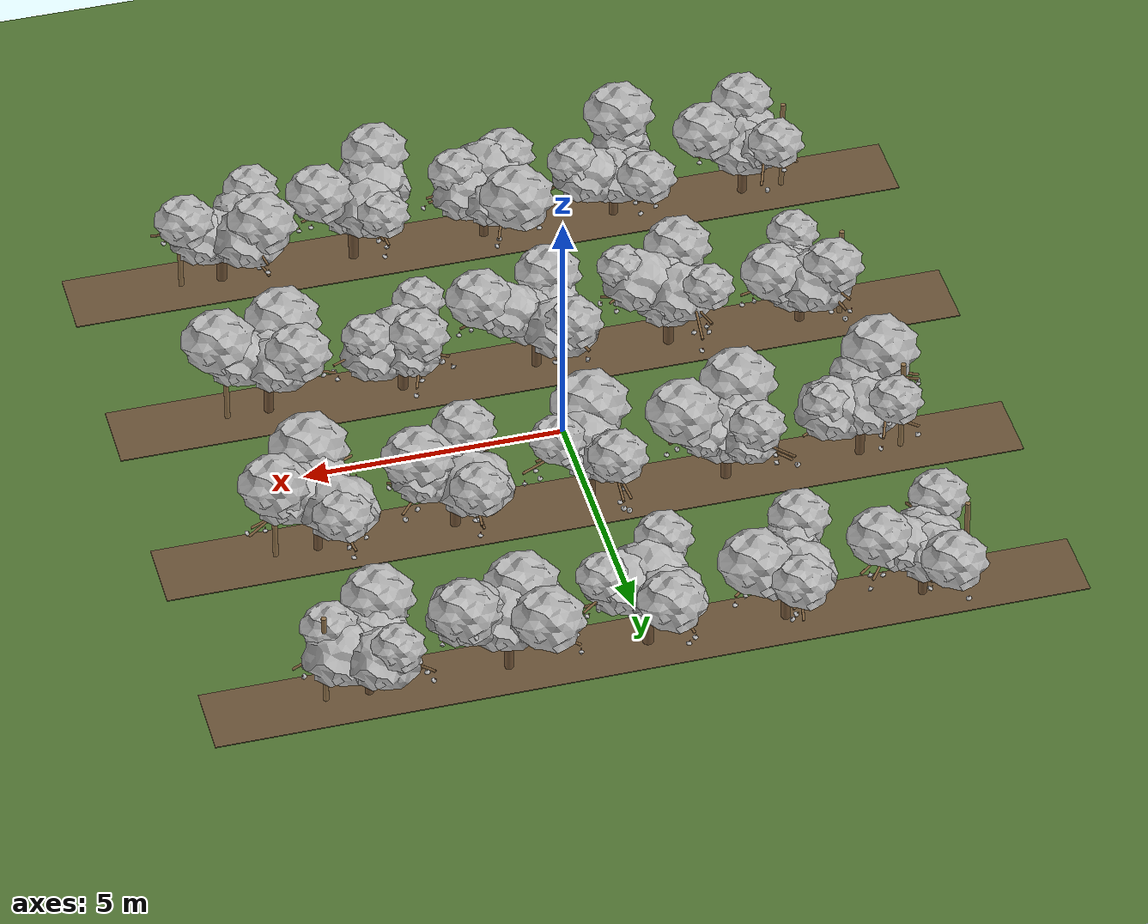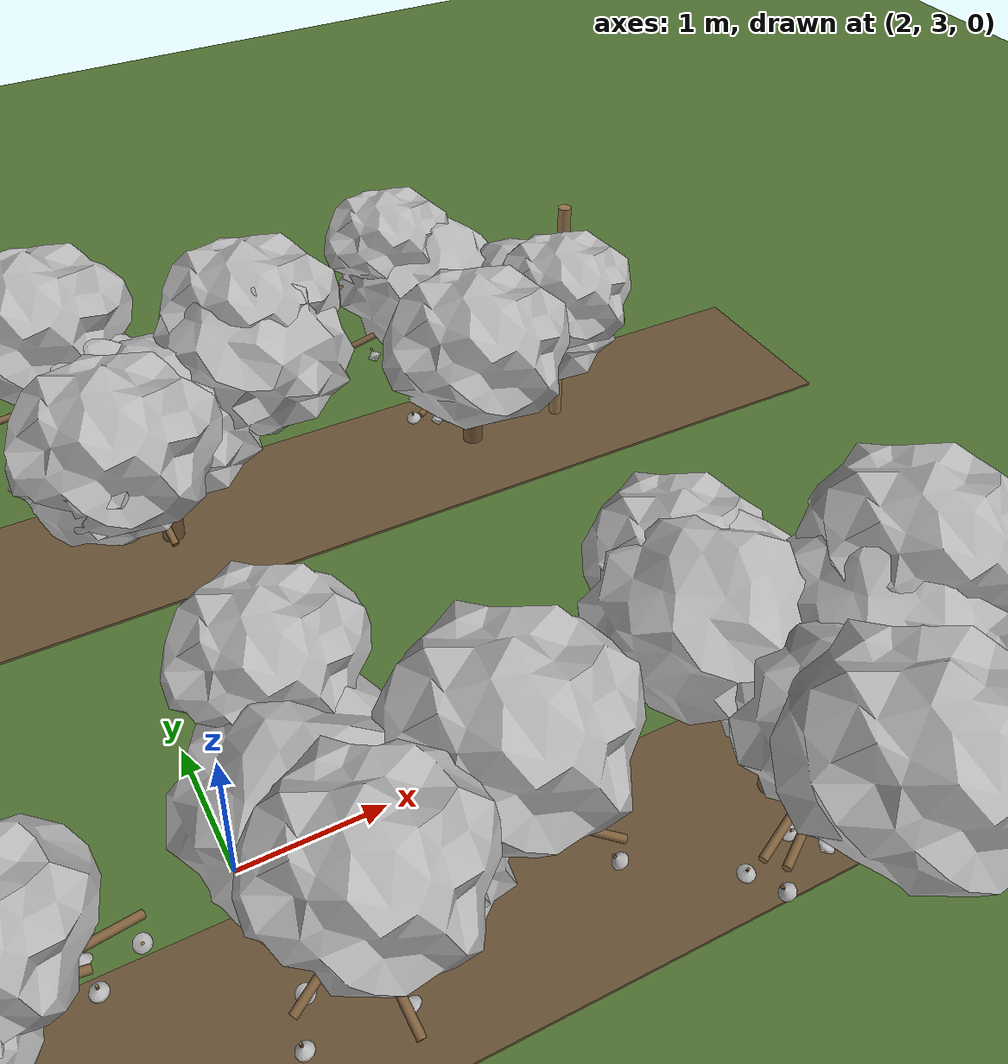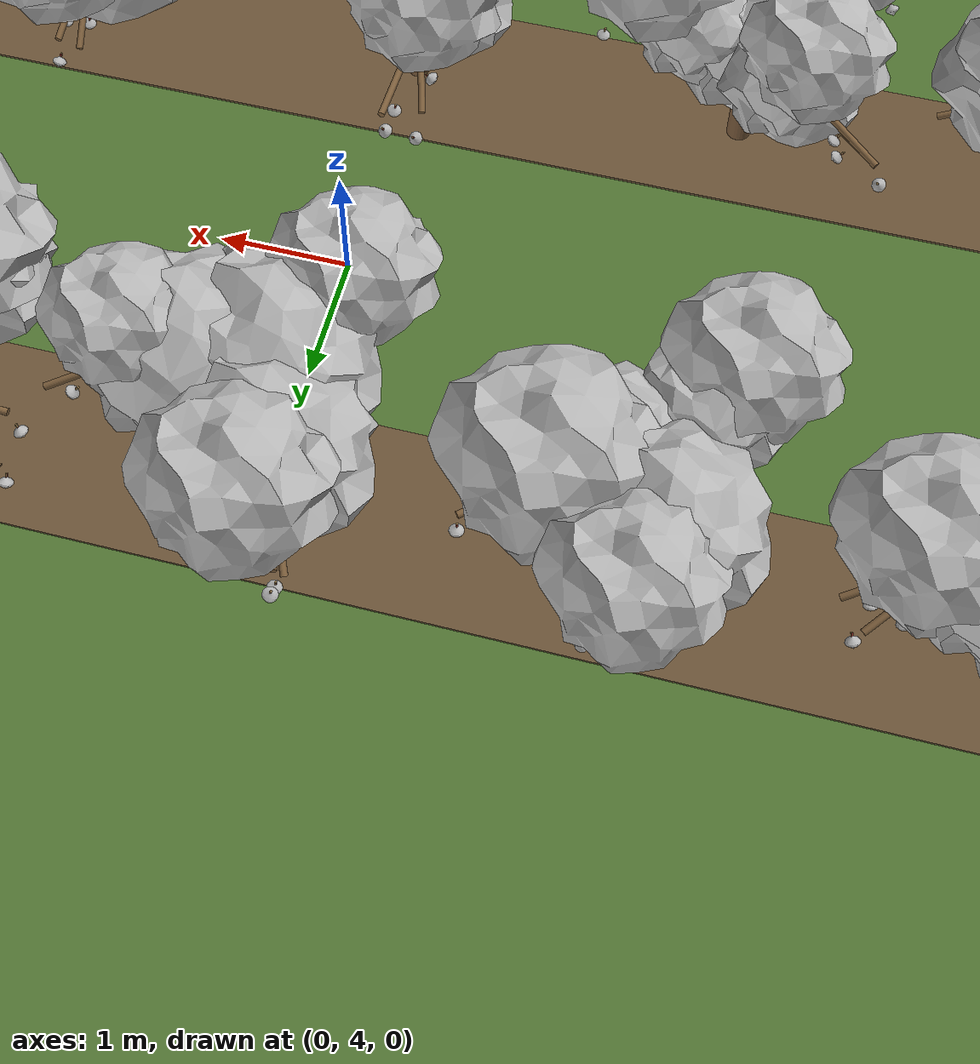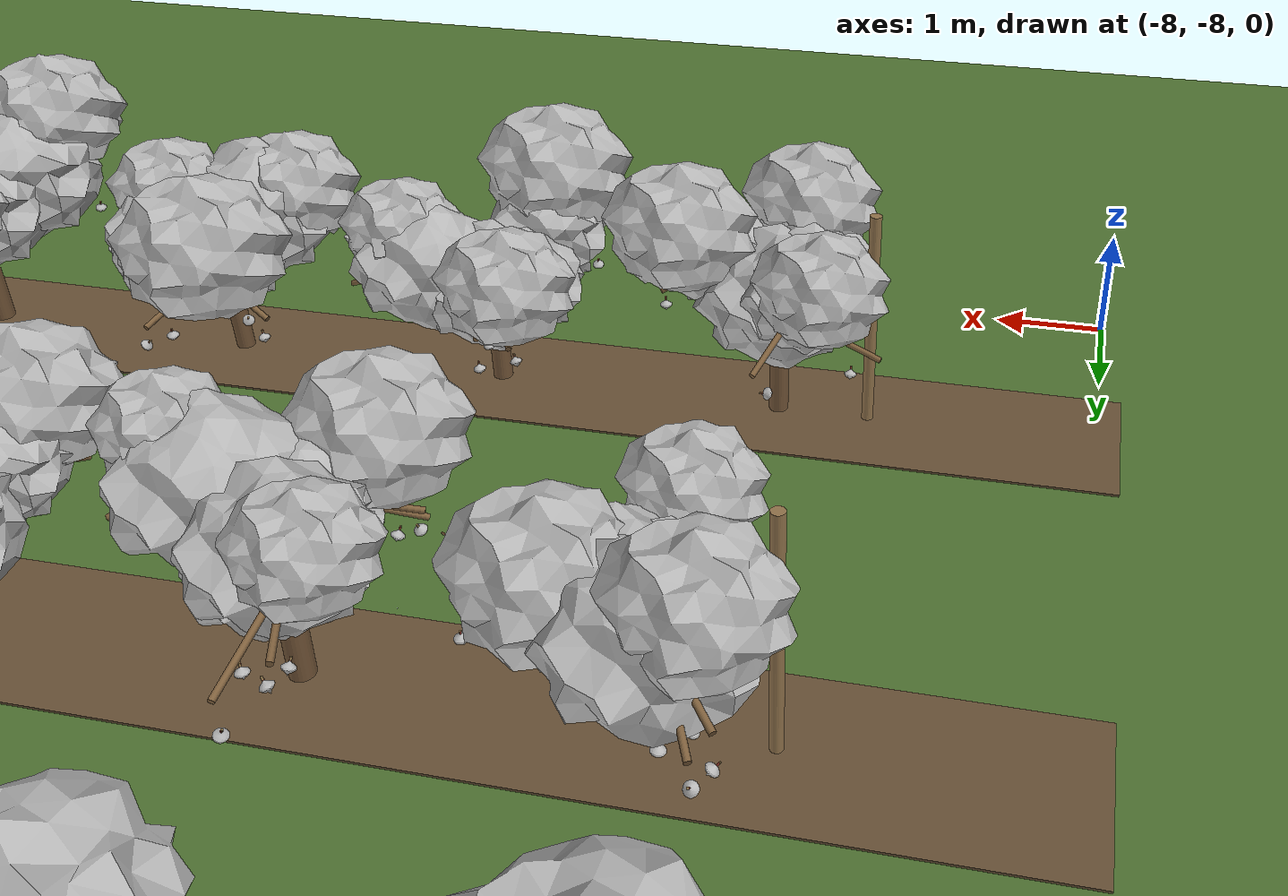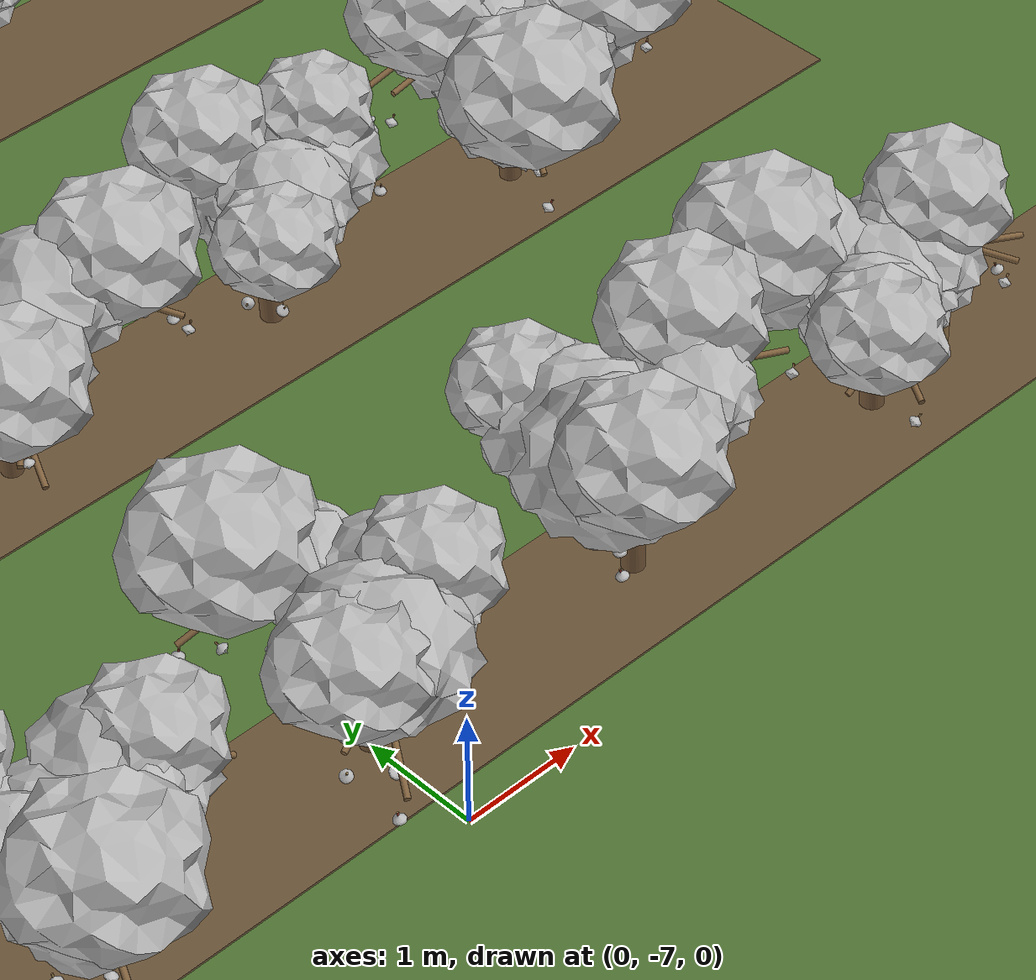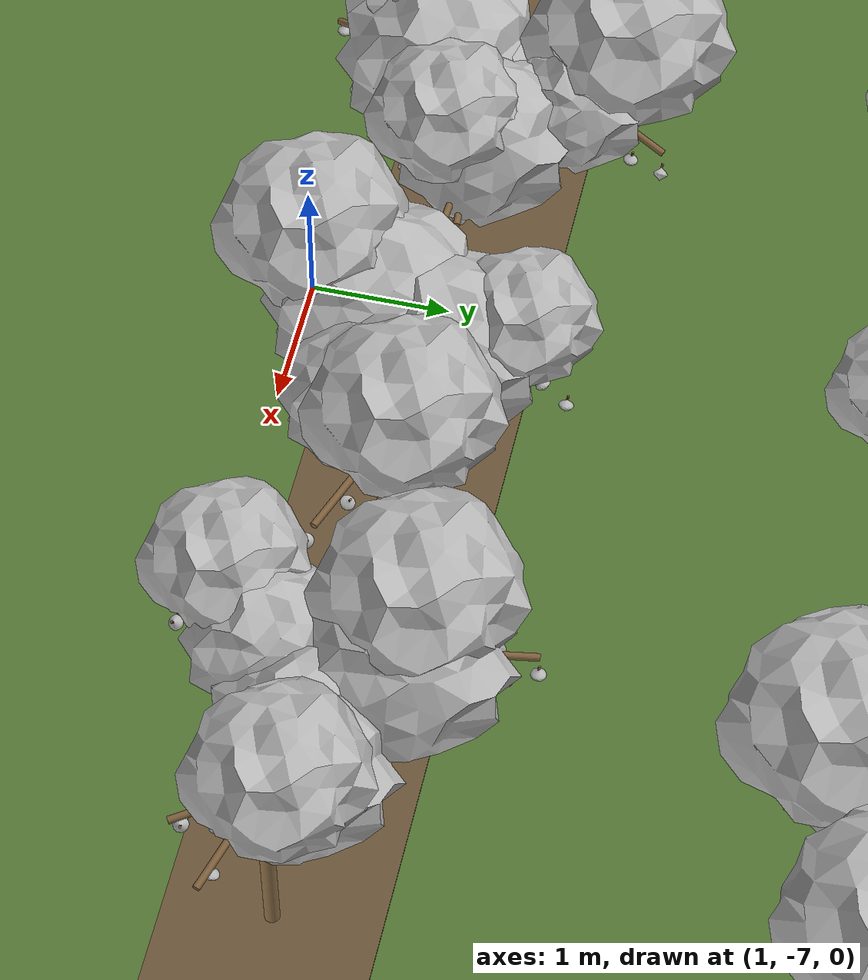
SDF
<?xml version="1.0" ?>
<sdf version="1.8">
  <world name="bagged_peach_orchard_hd">
    <physics name="1ms" type="ignored">
      <max_step_size>0.001</max_step_size>
      <real_time_factor>1.0</real_time_factor>
    </physics>
    <gravity>0 0 -9.8066</gravity>
    <scene>
      <ambient>0.55 0.55 0.60 1</ambient>
      <background>0.62 0.78 0.95 1</background>
      <shadows>true</shadows>
      <sky>
        <time>11.5</time>
        <clouds>
          <speed>0.6</speed>
        </clouds>
      </sky>
    </scene>
    <light type="directional" name="sun">
      <cast_shadows>true</cast_shadows>
      <pose>10 -8 15 0 0 0</pose>
      <diffuse>0.85 0.83 0.78 1</diffuse>
      <specular>0.15 0.15 0.15 1</specular>
      <attenuation>
        <range>80</range>
        <constant>0.9</constant>
        <linear>0.01</linear>
        <quadratic>0.001</quadratic>
      </attenuation>
      <direction>-0.35 0.30 -1</direction>
    </light>
    <plugin filename="gz-sim-sensors-system" name="gz::sim::systems::Sensors">
      <render_engine>ogre2</render_engine>
    </plugin>

    <model name="overview_cam">
      <static>true</static>
      <pose>13 -13 6.5 0 0.281 2.356</pose>
      <link name="link">
        <sensor name="overview_cam" type="camera">
          <pose>0 0 0 0 0 0</pose>
          <camera>
            <horizontal_fov>1.10</horizontal_fov>
            <image>
              <width>1280</width>
              <height>720</height>
              <format>RGB_INT8</format>
            </image>
            <clip>
              <near>0.1</near>
              <far>100</far>
            </clip>
          </camera>
          <always_on>true</always_on>
          <update_rate>5</update_rate>
          <topic>overview_cam/image</topic>
        </sensor>
      </link>
    </model>  <model name="ground">
    <static>true</static>
    <link name="link">
      <collision name="c">
        <geometry><plane><normal>0 0 1</normal><size>40.0 30.0</size></plane></geometry>
      </collision>
      <visual name="v">
        <geometry><plane><normal>0 0 1</normal><size>40.0 30.0</size></plane></geometry>
        <material><ambient>0.1600 0.2300 0.1000 1</ambient><diffuse>0.3200 0.4600 0.2000 1</diffuse><specular>0.05 0.05 0.05 1</specular></material>
      </visual>
    </link>
  </model>
  <model name="soil_strips">
    <static>true</static>
    <link name="link">
      <visual name="soil_r0_v">
        <pose>0 -6.0000 0.012 0 0 0</pose>
        <geometry><box><size>16.4000 1.4 0.02</size></box></geometry>
        <material><ambient>0.2100 0.1650 0.1100 1</ambient><diffuse>0.4200 0.3300 0.2200 1</diffuse><specular>0.05 0.05 0.05 1</specular></material>
      </visual>
      <visual name="soil_r1_v">
        <pose>0 -2.0000 0.012 0 0 0</pose>
        <geometry><box><size>16.4000 1.4 0.02</size></box></geometry>
        <material><ambient>0.2100 0.1650 0.1100 1</ambient><diffuse>0.4200 0.3300 0.2200 1</diffuse><specular>0.05 0.05 0.05 1</specular></material>
      </visual>
      <visual name="soil_r2_v">
        <pose>0 2.0000 0.012 0 0 0</pose>
        <geometry><box><size>16.4000 1.4 0.02</size></box></geometry>
        <material><ambient>0.2100 0.1650 0.1100 1</ambient><diffuse>0.4200 0.3300 0.2200 1</diffuse><specular>0.05 0.05 0.05 1</specular></material>
      </visual>
      <visual name="soil_r3_v">
        <pose>0 6.0000 0.012 0 0 0</pose>
        <geometry><box><size>16.4000 1.4 0.02</size></box></geometry>
        <material><ambient>0.2100 0.1650 0.1100 1</ambient><diffuse>0.4200 0.3300 0.2200 1</diffuse><specular>0.05 0.05 0.05 1</specular></material>
      </visual>
    </link>
  </model>
  <model name="posts">
    <static>true</static>
    <link name="link">
      <visual name="post0_v">
        <pose>-6.0000 -6.0000 1.0000 0.0000 0.0000 0.0000</pose>
        <geometry><cylinder><radius>0.0500</radius><length>2.0000</length></cylinder></geometry>
        <material><ambient>0.2900 0.2300 0.1500 1</ambient><diffuse>0.5800 0.4600 0.3000 1</diffuse><specular>0.05 0.05 0.05 1</specular></material>
      </visual>
      <collision name="post0_v_c">
        <pose>-6.0000 -6.0000 1.0000 0.0000 0.0000 0.0000</pose>
        <geometry><cylinder><radius>0.0500</radius><length>2.0000</length></cylinder></geometry>
      </collision>
      <visual name="post1_v">
        <pose>-6.0000 -2.0000 1.0000 0.0000 0.0000 0.0000</pose>
        <geometry><cylinder><radius>0.0500</radius><length>2.0000</length></cylinder></geometry>
        <material><ambient>0.2900 0.2300 0.1500 1</ambient><diffuse>0.5800 0.4600 0.3000 1</diffuse><specular>0.05 0.05 0.05 1</specular></material>
      </visual>
      <collision name="post1_v_c">
        <pose>-6.0000 -2.0000 1.0000 0.0000 0.0000 0.0000</pose>
        <geometry><cylinder><radius>0.0500</radius><length>2.0000</length></cylinder></geometry>
      </collision>
      <visual name="post2_v">
        <pose>-6.0000 2.0000 1.0000 0.0000 0.0000 0.0000</pose>
        <geometry><cylinder><radius>0.0500</radius><length>2.0000</length></cylinder></geometry>
        <material><ambient>0.2900 0.2300 0.1500 1</ambient><diffuse>0.5800 0.4600 0.3000 1</diffuse><specular>0.05 0.05 0.05 1</specular></material>
      </visual>
      <collision name="post2_v_c">
        <pose>-6.0000 2.0000 1.0000 0.0000 0.0000 0.0000</pose>
        <geometry><cylinder><radius>0.0500</radius><length>2.0000</length></cylinder></geometry>
      </collision>
      <visual name="post3_v">
        <pose>-6.0000 6.0000 1.0000 0.0000 0.0000 0.0000</pose>
        <geometry><cylinder><radius>0.0500</radius><length>2.0000</length></cylinder></geometry>
        <material><ambient>0.2900 0.2300 0.1500 1</ambient><diffuse>0.5800 0.4600 0.3000 1</diffuse><specular>0.05 0.05 0.05 1</specular></material>
      </visual>
      <collision name="post3_v_c">
        <pose>-6.0000 6.0000 1.0000 0.0000 0.0000 0.0000</pose>
        <geometry><cylinder><radius>0.0500</radius><length>2.0000</length></cylinder></geometry>
      </collision>
      <visual name="post4_v">
        <pose>6.0000 -6.0000 1.0000 0.0000 0.0000 0.0000</pose>
        <geometry><cylinder><radius>0.0500</radius><length>2.0000</length></cylinder></geometry>
        <material><ambient>0.2900 0.2300 0.1500 1</ambient><diffuse>0.5800 0.4600 0.3000 1</diffuse><specular>0.05 0.05 0.05 1</specular></material>
      </visual>
      <collision name="post4_v_c">
        <pose>6.0000 -6.0000 1.0000 0.0000 0.0000 0.0000</pose>
        <geometry><cylinder><radius>0.0500</radius><length>2.0000</length></cylinder></geometry>
      </collision>
      <visual name="post5_v">
        <pose>6.0000 -2.0000 1.0000 0.0000 0.0000 0.0000</pose>
        <geometry><cylinder><radius>0.0500</radius><length>2.0000</length></cylinder></geometry>
        <material><ambient>0.2900 0.2300 0.1500 1</ambient><diffuse>0.5800 0.4600 0.3000 1</diffuse><specular>0.05 0.05 0.05 1</specular></material>
      </visual>
      <collision name="post5_v_c">
        <pose>6.0000 -2.0000 1.0000 0.0000 0.0000 0.0000</pose>
        <geometry><cylinder><radius>0.0500</radius><length>2.0000</length></cylinder></geometry>
      </collision>
      <visual name="post6_v">
        <pose>6.0000 2.0000 1.0000 0.0000 0.0000 0.0000</pose>
        <geometry><cylinder><radius>0.0500</radius><length>2.0000</length></cylinder></geometry>
        <material><ambient>0.2900 0.2300 0.1500 1</ambient><diffuse>0.5800 0.4600 0.3000 1</diffuse><specular>0.05 0.05 0.05 1</specular></material>
      </visual>
      <collision name="post6_v_c">
        <pose>6.0000 2.0000 1.0000 0.0000 0.0000 0.0000</pose>
        <geometry><cylinder><radius>0.0500</radius><length>2.0000</length></cylinder></geometry>
      </collision>
      <visual name="post7_v">
        <pose>6.0000 6.0000 1.0000 0.0000 0.0000 0.0000</pose>
        <geometry><cylinder><radius>0.0500</radius><length>2.0000</length></cylinder></geometry>
        <material><ambient>0.2900 0.2300 0.1500 1</ambient><diffuse>0.5800 0.4600 0.3000 1</diffuse><specular>0.05 0.05 0.05 1</specular></material>
      </visual>
      <collision name="post7_v_c">
        <pose>6.0000 6.0000 1.0000 0.0000 0.0000 0.0000</pose>
        <geometry><cylinder><radius>0.0500</radius><length>2.0000</length></cylinder></geometry>
      </collision>
    </link>
  </model>
  <model name="tree_r0_t0">
    <static>true</static>
    <link name="trunk">
      <visual name="trunk_v">
        <pose>-5.2031 -5.9955 0.3535 -0.0127 -0.0087 0.0001</pose>
        <geometry><cylinder><radius>0.0849</radius><length>0.7071</length></cylinder></geometry>
        <material><ambient>0.2300 0.1700 0.1100 1</ambient><diffuse>0.4600 0.3400 0.2200 1</diffuse><specular>0.05 0.05 0.05 1</specular></material>
      </visual>
      <collision name="trunk_v_c">
        <pose>-5.2031 -5.9955 0.3535 -0.0127 -0.0087 0.0001</pose>
        <geometry><cylinder><radius>0.0849</radius><length>0.7071</length></cylinder></geometry>
      </collision>
    </link>
    <link name="frame">
      <visual name="leader0_v">
        <pose>-4.7853 -5.9922 1.2395 0.0021 0.6689 0.0007</pose>
        <geometry><cylinder><radius>0.0500</radius><length>1.3573</length></cylinder></geometry>
        <material><ambient>0.2300 0.1700 0.1100 1</ambient><diffuse>0.4600 0.3400 0.2200 1</diffuse><specular>0.05 0.05 0.05 1</specular></material>
      </visual>
      <collision name="leader0_v_c">
        <pose>-4.7853 -5.9922 1.2395 0.0021 0.6689 0.0007</pose>
        <geometry><cylinder><radius>0.0500</radius><length>1.3573</length></cylinder></geometry>
      </collision>
      <visual name="leader1_v">
        <pose>-5.3870 -5.6509 1.1695 -0.6341 -0.3053 0.1009</pose>
        <geometry><cylinder><radius>0.0500</radius><length>1.2037</length></cylinder></geometry>
        <material><ambient>0.2300 0.1700 0.1100 1</ambient><diffuse>0.4600 0.3400 0.2200 1</diffuse><specular>0.05 0.05 0.05 1</specular></material>
      </visual>
      <collision name="leader1_v_c">
        <pose>-5.3870 -5.6509 1.1695 -0.6341 -0.3053 0.1009</pose>
        <geometry><cylinder><radius>0.0500</radius><length>1.2037</length></cylinder></geometry>
      </collision>
      <visual name="leader2_v">
        <pose>-5.3781 -6.3351 1.1672 0.6420 -0.2908 -0.0973</pose>
        <geometry><cylinder><radius>0.0500</radius><length>1.1995</length></cylinder></geometry>
        <material><ambient>0.2300 0.1700 0.1100 1</ambient><diffuse>0.4600 0.3400 0.2200 1</diffuse><specular>0.05 0.05 0.05 1</specular></material>
      </visual>
      <collision name="leader2_v_c">
        <pose>-5.3781 -6.3351 1.1672 0.6420 -0.2908 -0.0973</pose>
        <geometry><cylinder><radius>0.0500</radius><length>1.1995</length></cylinder></geometry>
      </collision>
      <visual name="branch0_v">
        <pose>-4.4456 -5.8553 1.3283 -2.0812 0.9248 -1.4094</pose>
        <geometry><cylinder><radius>0.0250</radius><length>0.5225</length></cylinder></geometry>
        <material><ambient>0.2500 0.1900 0.1200 1</ambient><diffuse>0.5000 0.3800 0.2400 1</diffuse><specular>0.05 0.05 0.05 1</specular></material>
      </visual>
      <visual name="branch1_v">
        <pose>-4.4302 -6.1975 1.3490 2.0610 0.6647 1.0443</pose>
        <geometry><cylinder><radius>0.0250</radius><length>0.5901</length></cylinder></geometry>
        <material><ambient>0.2500 0.1900 0.1200 1</ambient><diffuse>0.5000 0.3800 0.2400 1</diffuse><specular>0.05 0.05 0.05 1</specular></material>
      </visual>
      <visual name="branch2_v">
        <pose>-5.7786 -5.5469 1.0788 -2.5477 -1.2037 2.3033</pose>
        <geometry><cylinder><radius>0.0250</radius><length>0.8137</length></cylinder></geometry>
        <material><ambient>0.2500 0.1900 0.1200 1</ambient><diffuse>0.5000 0.3800 0.2400 1</diffuse><specular>0.05 0.05 0.05 1</specular></material>
      </visual>
      <visual name="branch3_v">
        <pose>-5.3588 -5.1157 1.2715 -2.0000 0.3302 -0.5078</pose>
        <geometry><cylinder><radius>0.0250</radius><length>0.8006</length></cylinder></geometry>
        <material><ambient>0.2500 0.1900 0.1200 1</ambient><diffuse>0.5000 0.3800 0.2400 1</diffuse><specular>0.05 0.05 0.05 1</specular></material>
      </visual>
      <visual name="branch4_v">
        <pose>-5.4927 -6.6156 1.0998 1.8827 -0.3670 -0.4990</pose>
        <geometry><cylinder><radius>0.0250</radius><length>0.6002</length></cylinder></geometry>
        <material><ambient>0.2500 0.1900 0.1200 1</ambient><diffuse>0.5000 0.3800 0.2400 1</diffuse><specular>0.05 0.05 0.05 1</specular></material>
      </visual>
      <visual name="branch5_v">
        <pose>-5.5532 -6.7079 1.2432 1.8720 -0.4107 -0.5513</pose>
        <geometry><cylinder><radius>0.0250</radius><length>0.5858</length></cylinder></geometry>
        <material><ambient>0.2500 0.1900 0.1200 1</ambient><diffuse>0.5000 0.3800 0.2400 1</diffuse><specular>0.05 0.05 0.05 1</specular></material>
      </visual>
      <visual name="twig0_v">
        <pose>-5.3096 -4.7489 0.9815 -1.0052 0.7536 -0.4283</pose>
        <geometry><cylinder><radius>0.0080</radius><length>0.0260</length></cylinder></geometry>
        <material><ambient>0.2750 0.2250 0.1400 1</ambient><diffuse>0.5500 0.4500 0.2800 1</diffuse><specular>0.05 0.05 0.05 1</specular></material>
      </visual>
      <visual name="twig1_v">
        <pose>-4.3895 -6.0600 1.6297 0.6912 -0.0772 -0.0278</pose>
        <geometry><cylinder><radius>0.0080</radius><length>0.0260</length></cylinder></geometry>
        <material><ambient>0.2750 0.2250 0.1400 1</ambient><diffuse>0.5500 0.4500 0.2800 1</diffuse><specular>0.05 0.05 0.05 1</specular></material>
      </visual>
      <visual name="twig2_v">
        <pose>-4.2595 -5.7707 1.1537 0.0920 0.0520 0.0024</pose>
        <geometry><cylinder><radius>0.0080</radius><length>0.0260</length></cylinder></geometry>
        <material><ambient>0.2750 0.2250 0.1400 1</ambient><diffuse>0.5500 0.4500 0.2800 1</diffuse><specular>0.05 0.05 0.05 1</specular></material>
      </visual>
      <visual name="twig3_v">
        <pose>-4.4964 -6.3065 1.1321 0.2577 -0.2804 -0.0366</pose>
        <geometry><cylinder><radius>0.0080</radius><length>0.0260</length></cylinder></geometry>
        <material><ambient>0.2750 0.2250 0.1400 1</ambient><diffuse>0.5500 0.4500 0.2800 1</diffuse><specular>0.05 0.05 0.05 1</specular></material>
      </visual>
      <visual name="twig4_v">
        <pose>-5.6567 -6.8643 0.8494 -0.3086 0.5828 -0.0932</pose>
        <geometry><cylinder><radius>0.0080</radius><length>0.0260</length></cylinder></geometry>
        <material><ambient>0.2750 0.2250 0.1400 1</ambient><diffuse>0.5500 0.4500 0.2800 1</diffuse><specular>0.05 0.05 0.05 1</specular></material>
      </visual>
      <visual name="twig5_v">
        <pose>-5.7600 -6.9955 1.0210 -0.1649 0.2389 -0.0198</pose>
        <geometry><cylinder><radius>0.0080</radius><length>0.0260</length></cylinder></geometry>
        <material><ambient>0.2750 0.2250 0.1400 1</ambient><diffuse>0.5500 0.4500 0.2800 1</diffuse><specular>0.05 0.05 0.05 1</specular></material>
      </visual>
      <visual name="twig6_v">
        <pose>-5.9096 -5.5158 0.8286 0.2383 -0.0436 -0.0052</pose>
        <geometry><cylinder><radius>0.0080</radius><length>0.0260</length></cylinder></geometry>
        <material><ambient>0.2750 0.2250 0.1400 1</ambient><diffuse>0.5500 0.4500 0.2800 1</diffuse><specular>0.05 0.05 0.05 1</specular></material>
      </visual>
      <visual name="twig7_v">
        <pose>-5.5032 -6.7173 1.1171 -0.3463 -0.3552 0.0628</pose>
        <geometry><cylinder><radius>0.0080</radius><length>0.0260</length></cylinder></geometry>
        <material><ambient>0.2750 0.2250 0.1400 1</ambient><diffuse>0.5500 0.4500 0.2800 1</diffuse><specular>0.05 0.05 0.05 1</specular></material>
      </visual>
      <visual name="twig8_v">
        <pose>-4.4380 -5.8676 1.2010 0.0633 0.5613 0.0183</pose>
        <geometry><cylinder><radius>0.0080</radius><length>0.0260</length></cylinder></geometry>
        <material><ambient>0.2750 0.2250 0.1400 1</ambient><diffuse>0.5500 0.4500 0.2800 1</diffuse><specular>0.05 0.05 0.05 1</specular></material>
      </visual>
      <visual name="twig9_v">
        <pose>-4.2888 -6.4005 1.0095 0.2679 -0.6257 -0.0871</pose>
        <geometry><cylinder><radius>0.0080</radius><length>0.0260</length></cylinder></geometry>
        <material><ambient>0.2750 0.2250 0.1400 1</ambient><diffuse>0.5500 0.4500 0.2800 1</diffuse><specular>0.05 0.05 0.05 1</specular></material>
      </visual>
    </link>
    <link name="canopy">
      <visual name="blob0_v">
        <pose>-4.5808 -6.0627 1.4883 0.0000 0.0000 0.0000</pose>
        <geometry><mesh><uri>model://orchard_meshes/meshes/leaf_blob_a.obj</uri><scale>0.4976 0.4976 0.4229</scale></mesh></geometry>
      </visual>
      <collision name="blob0_c">
        <pose>-4.5808 -6.0627 1.4883 0 0 0</pose>
        <geometry><sphere><radius>0.4578</radius></sphere></geometry>
      </collision>
      <visual name="blob1_v">
        <pose>-4.3925 -5.8225 1.8202 0.0000 0.0000 0.0000</pose>
        <geometry><mesh><uri>model://orchard_meshes/meshes/leaf_blob_b.obj</uri><scale>0.5912 0.5912 0.5025</scale></mesh></geometry>
      </visual>
      <collision name="blob1_c">
        <pose>-4.3925 -5.8225 1.8202 0 0 0</pose>
        <geometry><sphere><radius>0.5439</radius></sphere></geometry>
      </collision>
      <visual name="blob2_v">
        <pose>-5.4269 -5.6123 1.3553 0.0000 0.0000 0.0000</pose>
        <geometry><mesh><uri>model://orchard_meshes/meshes/leaf_blob_a.obj</uri><scale>0.4688 0.4688 0.3985</scale></mesh></geometry>
      </visual>
      <collision name="blob2_c">
        <pose>-5.4269 -5.6123 1.3553 0 0 0</pose>
        <geometry><sphere><radius>0.4313</radius></sphere></geometry>
      </collision>
      <visual name="blob3_v">
        <pose>-5.6690 -5.3300 1.6397 0.0000 0.0000 0.0000</pose>
        <geometry><mesh><uri>model://orchard_meshes/meshes/leaf_blob_b.obj</uri><scale>0.5102 0.5102 0.4337</scale></mesh></geometry>
      </visual>
      <collision name="blob3_c">
        <pose>-5.6690 -5.3300 1.6397 0 0 0</pose>
        <geometry><sphere><radius>0.4694</radius></sphere></geometry>
      </collision>
      <visual name="blob4_v">
        <pose>-5.3295 -6.2272 1.2752 0.0000 0.0000 0.0000</pose>
        <geometry><mesh><uri>model://orchard_meshes/meshes/leaf_blob_a.obj</uri><scale>0.6183 0.6183 0.5256</scale></mesh></geometry>
      </visual>
      <collision name="blob4_c">
        <pose>-5.3295 -6.2272 1.2752 0 0 0</pose>
        <geometry><sphere><radius>0.5689</radius></sphere></geometry>
      </collision>
      <visual name="blob5_v">
        <pose>-5.3587 -6.6438 1.7709 0.0000 0.0000 0.0000</pose>
        <geometry><mesh><uri>model://orchard_meshes/meshes/leaf_blob_b.obj</uri><scale>0.5578 0.5578 0.4741</scale></mesh></geometry>
      </visual>
      <collision name="blob5_c">
        <pose>-5.3587 -6.6438 1.7709 0 0 0</pose>
        <geometry><sphere><radius>0.5131</radius></sphere></geometry>
      </collision>
      <visual name="blob6_v">
        <pose>-5.1944 -5.9322 1.1847 0.0000 0.0000 0.0000</pose>
        <geometry><mesh><uri>model://orchard_meshes/meshes/leaf_blob_a.obj</uri><scale>0.6431 0.6431 0.5466</scale></mesh></geometry>
      </visual>
      <collision name="blob6_c">
        <pose>-5.1944 -5.9322 1.1847 0 0 0</pose>
        <geometry><sphere><radius>0.5916</radius></sphere></geometry>
      </collision>
    </link>
    <link name="bag_r0_t0_b00">
      <pose>-5.3185 -4.7569 0.9764 -1.0052 0.7536 -0.4283</pose>
      <visual name="paper">
        <pose>0.0000 0.0000 0.0000 0.0000 0.0000 0.0000</pose>
        <geometry><mesh><uri>model://orchard_meshes/meshes/bag_a.obj</uri><scale>0.0520 0.0520 0.1040</scale></mesh></geometry>
      </visual>
      <visual name="twist">
        <pose>0 0 0.0100 0 0 0</pose>
        <geometry><cylinder><radius>0.0080</radius><length>0.0260</length></cylinder></geometry>
        <material><ambient>0.2750 0.1000 0.0750 1</ambient><diffuse>0.5500 0.2000 0.1500 1</diffuse><specular>0.05 0.05 0.05 1</specular></material>
      </visual>
      <collision name="paper_c">
        <pose>0 0 -0.0520 0 0 0</pose>
        <geometry><sphere><radius>0.0520</radius></sphere></geometry>
      </collision>
    </link>
    <link name="bag_r0_t0_b01">
      <pose>-4.3885 -6.0517 1.6197 0.6912 -0.0772 -0.0278</pose>
      <visual name="paper">
        <pose>0.0000 0.0000 0.0000 0.0000 0.0000 0.0000</pose>
        <geometry><mesh><uri>model://orchard_meshes/meshes/bag_b.obj</uri><scale>0.0520 0.0520 0.1040</scale></mesh></geometry>
      </visual>
      <visual name="twist">
        <pose>0 0 0.0100 0 0 0</pose>
        <geometry><cylinder><radius>0.0080</radius><length>0.0260</length></cylinder></geometry>
        <material><ambient>0.2750 0.1000 0.0750 1</ambient><diffuse>0.5500 0.2000 0.1500 1</diffuse><specular>0.05 0.05 0.05 1</specular></material>
      </visual>
      <collision name="paper_c">
        <pose>0 0 -0.0520 0 0 0</pose>
        <geometry><sphere><radius>0.0520</radius></sphere></geometry>
      </collision>
    </link>
    <link name="bag_r0_t0_b02">
      <pose>-4.2602 -5.7695 1.1407 0.0920 0.0520 0.0024</pose>
      <visual name="paper">
        <pose>0.0000 0.0000 0.0000 0.0000 0.0000 0.0000</pose>
        <geometry><mesh><uri>model://orchard_meshes/meshes/bag_a.obj</uri><scale>0.0520 0.0520 0.1040</scale></mesh></geometry>
      </visual>
      <visual name="twist">
        <pose>0 0 0.0100 0 0 0</pose>
        <geometry><cylinder><radius>0.0080</radius><length>0.0260</length></cylinder></geometry>
        <material><ambient>0.2750 0.1000 0.0750 1</ambient><diffuse>0.5500 0.2000 0.1500 1</diffuse><specular>0.05 0.05 0.05 1</specular></material>
      </visual>
      <collision name="paper_c">
        <pose>0 0 -0.0520 0 0 0</pose>
        <geometry><sphere><radius>0.0520</radius></sphere></geometry>
      </collision>
    </link>
    <link name="bag_r0_t0_b03">
      <pose>-4.4928 -6.3033 1.1200 0.2577 -0.2804 -0.0366</pose>
      <visual name="paper">
        <pose>0.0000 0.0000 0.0000 0.0000 0.0000 0.0000</pose>
        <geometry><mesh><uri>model://orchard_meshes/meshes/bag_b.obj</uri><scale>0.0520 0.0520 0.1040</scale></mesh></geometry>
      </visual>
      <visual name="twist">
        <pose>0 0 0.0100 0 0 0</pose>
        <geometry><cylinder><radius>0.0080</radius><length>0.0260</length></cylinder></geometry>
        <material><ambient>0.2750 0.1000 0.0750 1</ambient><diffuse>0.5500 0.2000 0.1500 1</diffuse><specular>0.05 0.05 0.05 1</specular></material>
      </visual>
      <collision name="paper_c">
        <pose>0 0 -0.0520 0 0 0</pose>
        <geometry><sphere><radius>0.0520</radius></sphere></geometry>
      </collision>
    </link>
    <link name="bag_r0_t0_b04">
      <pose>-5.6638 -6.8676 0.8391 -0.3086 0.5828 -0.0932</pose>
      <visual name="paper">
        <pose>0.0000 0.0000 0.0000 0.0000 0.0000 0.0000</pose>
        <geometry><mesh><uri>model://orchard_meshes/meshes/bag_a.obj</uri><scale>0.0520 0.0520 0.1040</scale></mesh></geometry>
      </visual>
      <visual name="twist">
        <pose>0 0 0.0100 0 0 0</pose>
        <geometry><cylinder><radius>0.0080</radius><length>0.0260</length></cylinder></geometry>
        <material><ambient>0.2750 0.1000 0.0750 1</ambient><diffuse>0.5500 0.2000 0.1500 1</diffuse><specular>0.05 0.05 0.05 1</specular></material>
      </visual>
      <collision name="paper_c">
        <pose>0 0 -0.0520 0 0 0</pose>
        <geometry><sphere><radius>0.0520</radius></sphere></geometry>
      </collision>
    </link>
    <link name="bag_r0_t0_b05">
      <pose>-5.7630 -6.9976 1.0085 -0.1649 0.2389 -0.0198</pose>
      <visual name="paper">
        <pose>0.0000 0.0000 0.0000 0.0000 0.0000 0.0000</pose>
        <geometry><mesh><uri>model://orchard_meshes/meshes/bag_b.obj</uri><scale>0.0520 0.0520 0.1040</scale></mesh></geometry>
      </visual>
      <visual name="twist">
        <pose>0 0 0.0100 0 0 0</pose>
        <geometry><cylinder><radius>0.0080</radius><length>0.0260</length></cylinder></geometry>
        <material><ambient>0.2750 0.1000 0.0750 1</ambient><diffuse>0.5500 0.2000 0.1500 1</diffuse><specular>0.05 0.05 0.05 1</specular></material>
      </visual>
      <collision name="paper_c">
        <pose>0 0 -0.0520 0 0 0</pose>
        <geometry><sphere><radius>0.0520</radius></sphere></geometry>
      </collision>
    </link>
    <link name="bag_r0_t0_b06">
      <pose>-5.9090 -5.5127 0.8160 0.2383 -0.0436 -0.0052</pose>
      <visual name="paper">
        <pose>0.0000 0.0000 0.0000 0.0000 0.0000 0.0000</pose>
        <geometry><mesh><uri>model://orchard_meshes/meshes/bag_a.obj</uri><scale>0.0520 0.0520 0.1040</scale></mesh></geometry>
      </visual>
      <visual name="twist">
        <pose>0 0 0.0100 0 0 0</pose>
        <geometry><cylinder><radius>0.0080</radius><length>0.0260</length></cylinder></geometry>
        <material><ambient>0.2750 0.1000 0.0750 1</ambient><diffuse>0.5500 0.2000 0.1500 1</diffuse><specular>0.05 0.05 0.05 1</specular></material>
      </visual>
      <collision name="paper_c">
        <pose>0 0 -0.0520 0 0 0</pose>
        <geometry><sphere><radius>0.0520</radius></sphere></geometry>
      </collision>
    </link>
    <link name="bag_r0_t0_b07">
      <pose>-5.4987 -6.7214 1.1056 -0.3463 -0.3552 0.0628</pose>
      <visual name="paper">
        <pose>0.0000 0.0000 0.0000 0.0000 0.0000 0.0000</pose>
        <geometry><mesh><uri>model://orchard_meshes/meshes/bag_b.obj</uri><scale>0.0520 0.0520 0.1040</scale></mesh></geometry>
      </visual>
      <visual name="twist">
        <pose>0 0 0.0100 0 0 0</pose>
        <geometry><cylinder><radius>0.0080</radius><length>0.0260</length></cylinder></geometry>
        <material><ambient>0.2750 0.1000 0.0750 1</ambient><diffuse>0.5500 0.2000 0.1500 1</diffuse><specular>0.05 0.05 0.05 1</specular></material>
      </visual>
      <collision name="paper_c">
        <pose>0 0 -0.0520 0 0 0</pose>
        <geometry><sphere><radius>0.0520</radius></sphere></geometry>
      </collision>
    </link>
    <link name="bag_r0_t0_b08">
      <pose>-4.4449 -5.8669 1.1900 0.0633 0.5613 0.0183</pose>
      <visual name="paper">
        <pose>0.0000 0.0000 0.0000 0.0000 0.0000 0.0000</pose>
        <geometry><mesh><uri>model://orchard_meshes/meshes/bag_a.obj</uri><scale>0.0520 0.0520 0.1040</scale></mesh></geometry>
      </visual>
      <visual name="twist">
        <pose>0 0 0.0100 0 0 0</pose>
        <geometry><cylinder><radius>0.0080</radius><length>0.0260</length></cylinder></geometry>
        <material><ambient>0.2750 0.1000 0.0750 1</ambient><diffuse>0.5500 0.2000 0.1500 1</diffuse><specular>0.05 0.05 0.05 1</specular></material>
      </visual>
      <collision name="paper_c">
        <pose>0 0 -0.0520 0 0 0</pose>
        <geometry><sphere><radius>0.0520</radius></sphere></geometry>
      </collision>
    </link>
    <link name="bag_r0_t0_b09">
      <pose>-4.2812 -6.3978 0.9994 0.2679 -0.6257 -0.0871</pose>
      <visual name="paper">
        <pose>0.0000 0.0000 0.0000 0.0000 0.0000 0.0000</pose>
        <geometry><mesh><uri>model://orchard_meshes/meshes/bag_b.obj</uri><scale>0.0520 0.0520 0.1040</scale></mesh></geometry>
      </visual>
      <visual name="twist">
        <pose>0 0 0.0100 0 0 0</pose>
        <geometry><cylinder><radius>0.0080</radius><length>0.0260</length></cylinder></geometry>
        <material><ambient>0.2750 0.1000 0.0750 1</ambient><diffuse>0.5500 0.2000 0.1500 1</diffuse><specular>0.05 0.05 0.05 1</specular></material>
      </visual>
      <collision name="paper_c">
        <pose>0 0 -0.0520 0 0 0</pose>
        <geometry><sphere><radius>0.0520</radius></sphere></geometry>
      </collision>
    </link>
  </model>
  <model name="tree_r0_t1">
    <static>true</static>
    <link name="trunk">
      <visual name="trunk_v">
        <pose>-2.5986 -6.0016 0.2909 0.0056 0.0048 0.0000</pose>
        <geometry><cylinder><radius>0.0880</radius><length>0.5818</length></cylinder></geometry>
        <material><ambient>0.2300 0.1700 0.1100 1</ambient><diffuse>0.4600 0.3400 0.2200 1</diffuse><specular>0.05 0.05 0.05 1</specular></material>
      </visual>
      <collision name="trunk_v_c">
        <pose>-2.5986 -6.0016 0.2909 0.0056 0.0048 0.0000</pose>
        <geometry><cylinder><radius>0.0880</radius><length>0.5818</length></cylinder></geometry>
      </collision>
    </link>
    <link name="frame">
      <visual name="leader0_v">
        <pose>-2.1349 -5.9357 0.9766 -0.1696 0.8568 -0.0776</pose>
        <geometry><cylinder><radius>0.0500</radius><length>1.2234</length></cylinder></geometry>
        <material><ambient>0.2300 0.1700 0.1100 1</ambient><diffuse>0.4600 0.3400 0.2200 1</diffuse><specular>0.05 0.05 0.05 1</specular></material>
      </visual>
      <collision name="leader0_v_c">
        <pose>-2.1349 -5.9357 0.9766 -0.1696 0.8568 -0.0776</pose>
        <geometry><cylinder><radius>0.0500</radius><length>1.2234</length></cylinder></geometry>
      </collision>
      <visual name="leader1_v">
        <pose>-2.7850 -5.6603 1.0091 -0.6764 -0.3301 0.1170</pose>
        <geometry><cylinder><radius>0.0500</radius><length>1.1583</length></cylinder></geometry>
        <material><ambient>0.2300 0.1700 0.1100 1</ambient><diffuse>0.4600 0.3400 0.2200 1</diffuse><specular>0.05 0.05 0.05 1</specular></material>
      </visual>
      <collision name="leader1_v_c">
        <pose>-2.7850 -5.6603 1.0091 -0.6764 -0.3301 0.1170</pose>
        <geometry><cylinder><radius>0.0500</radius><length>1.1583</length></cylinder></geometry>
      </collision>
      <visual name="leader2_v">
        <pose>-2.7677 -6.4229 1.1092 0.6722 -0.2477 -0.0869</pose>
        <geometry><cylinder><radius>0.0500</radius><length>1.3904</length></cylinder></geometry>
        <material><ambient>0.2300 0.1700 0.1100 1</ambient><diffuse>0.4600 0.3400 0.2200 1</diffuse><specular>0.05 0.05 0.05 1</specular></material>
      </visual>
      <collision name="leader2_v_c">
        <pose>-2.7677 -6.4229 1.1092 0.6722 -0.2477 -0.0869</pose>
        <geometry><cylinder><radius>0.0500</radius><length>1.3904</length></cylinder></geometry>
      </collision>
      <visual name="branch0_v">
        <pose>-1.6077 -5.9432 1.0182 2.8842 1.0581 2.7059</pose>
        <geometry><cylinder><radius>0.0250</radius><length>0.6709</length></cylinder></geometry>
        <material><ambient>0.2500 0.1900 0.1200 1</ambient><diffuse>0.5000 0.3800 0.2400 1</diffuse><specular>0.05 0.05 0.05 1</specular></material>
      </visual>
      <visual name="branch1_v">
        <pose>-1.5832 -5.9643 0.9728 2.8085 1.1397 2.6284</pose>
        <geometry><cylinder><radius>0.0250</radius><length>0.8114</length></cylinder></geometry>
        <material><ambient>0.2500 0.1900 0.1200 1</ambient><diffuse>0.5000 0.3800 0.2400 1</diffuse><specular>0.05 0.05 0.05 1</specular></material>
      </visual>
      <visual name="branch2_v">
        <pose>-3.0087 -5.2070 1.1138 -1.9485 -0.4042 0.5862</pose>
        <geometry><cylinder><radius>0.0250</radius><length>0.6553</length></cylinder></geometry>
        <material><ambient>0.2500 0.1900 0.1200 1</ambient><diffuse>0.5000 0.3800 0.2400 1</diffuse><specular>0.05 0.05 0.05 1</specular></material>
      </visual>
      <visual name="branch3_v">
        <pose>-2.8315 -5.2807 1.0692 -1.7390 0.0056 -0.0066</pose>
        <geometry><cylinder><radius>0.0250</radius><length>0.5914</length></cylinder></geometry>
        <material><ambient>0.2500 0.1900 0.1200 1</ambient><diffuse>0.5000 0.3800 0.2400 1</diffuse><specular>0.05 0.05 0.05 1</specular></material>
      </visual>
      <visual name="branch4_v">
        <pose>-2.9638 -6.9127 1.0716 2.0926 -0.3324 -0.5643</pose>
        <geometry><cylinder><radius>0.0250</radius><length>0.8702</length></cylinder></geometry>
        <material><ambient>0.2500 0.1900 0.1200 1</ambient><diffuse>0.5000 0.3800 0.2400 1</diffuse><specular>0.05 0.05 0.05 1</specular></material>
      </visual>
      <visual name="branch5_v">
        <pose>-3.0329 -6.5783 1.1603 1.9417 -1.1941 -1.5647</pose>
        <geometry><cylinder><radius>0.0250</radius><length>0.5111</length></cylinder></geometry>
        <material><ambient>0.2500 0.1900 0.1200 1</ambient><diffuse>0.5000 0.3800 0.2400 1</diffuse><specular>0.05 0.05 0.05 1</specular></material>
      </visual>
      <visual name="twig0_v">
        <pose>-2.9088 -6.8158 1.4398 -0.5037 -0.1329 0.0342</pose>
        <geometry><cylinder><radius>0.0080</radius><length>0.0260</length></cylinder></geometry>
        <material><ambient>0.2750 0.2250 0.1400 1</ambient><diffuse>0.5500 0.4500 0.2800 1</diffuse><specular>0.05 0.05 0.05 1</specular></material>
      </visual>
      <visual name="twig1_v">
        <pose>-1.6395 -5.8655 1.2609 -0.2313 0.0839 -0.0097</pose>
        <geometry><cylinder><radius>0.0080</radius><length>0.0260</length></cylinder></geometry>
        <material><ambient>0.2750 0.2250 0.1400 1</ambient><diffuse>0.5500 0.4500 0.2800 1</diffuse><specular>0.05 0.05 0.05 1</specular></material>
      </visual>
      <visual name="twig2_v">
        <pose>-2.8508 -4.9420 0.8280 0.0291 0.1436 0.0021</pose>
        <geometry><cylinder><radius>0.0080</radius><length>0.0260</length></cylinder></geometry>
        <material><ambient>0.2750 0.2250 0.1400 1</ambient><diffuse>0.5500 0.4500 0.2800 1</diffuse><specular>0.05 0.05 0.05 1</specular></material>
      </visual>
      <visual name="twig3_v">
        <pose>-3.0206 -6.9506 0.8921 -0.0368 0.3548 -0.0066</pose>
        <geometry><cylinder><radius>0.0080</radius><length>0.0260</length></cylinder></geometry>
        <material><ambient>0.2750 0.2250 0.1400 1</ambient><diffuse>0.5500 0.4500 0.2800 1</diffuse><specular>0.05 0.05 0.05 1</specular></material>
      </visual>
      <visual name="twig4_v">
        <pose>-3.3375 -6.7441 0.9135 -0.2993 -0.1077 0.0162</pose>
        <geometry><cylinder><radius>0.0080</radius><length>0.0260</length></cylinder></geometry>
        <material><ambient>0.2750 0.2250 0.1400 1</ambient><diffuse>0.5500 0.4500 0.2800 1</diffuse><specular>0.05 0.05 0.05 1</specular></material>
      </visual>
      <visual name="twig5_v">
        <pose>-1.5936 -5.9668 0.8321 -0.0254 0.6327 -0.0083</pose>
        <geometry><cylinder><radius>0.0080</radius><length>0.0260</length></cylinder></geometry>
        <material><ambient>0.2750 0.2250 0.1400 1</ambient><diffuse>0.5500 0.4500 0.2800 1</diffuse><specular>0.05 0.05 0.05 1</specular></material>
      </visual>
      <visual name="twig6_v">
        <pose>-2.8315 -5.2221 0.8809 -0.1049 0.1560 -0.0082</pose>
        <geometry><cylinder><radius>0.0080</radius><length>0.0260</length></cylinder></geometry>
        <material><ambient>0.2750 0.2250 0.1400 1</ambient><diffuse>0.5500 0.4500 0.2800 1</diffuse><specular>0.05 0.05 0.05 1</specular></material>
      </visual>
      <visual name="twig7_v">
        <pose>-3.0300 -5.3516 1.2111 -0.5595 0.1648 -0.0474</pose>
        <geometry><cylinder><radius>0.0080</radius><length>0.0260</length></cylinder></geometry>
        <material><ambient>0.2750 0.2250 0.1400 1</ambient><diffuse>0.5500 0.4500 0.2800 1</diffuse><specular>0.05 0.05 0.05 1</specular></material>
      </visual>
      <visual name="twig8_v">
        <pose>-3.2268 -6.5811 0.9816 0.1551 -0.5478 -0.0437</pose>
        <geometry><cylinder><radius>0.0080</radius><length>0.0260</length></cylinder></geometry>
        <material><ambient>0.2750 0.2250 0.1400 1</ambient><diffuse>0.5500 0.4500 0.2800 1</diffuse><specular>0.05 0.05 0.05 1</specular></material>
      </visual>
      <visual name="twig9_v">
        <pose>-3.1525 -4.9945 0.9114 0.2553 0.3324 0.0431</pose>
        <geometry><cylinder><radius>0.0080</radius><length>0.0260</length></cylinder></geometry>
        <material><ambient>0.2750 0.2250 0.1400 1</ambient><diffuse>0.5500 0.4500 0.2800 1</diffuse><specular>0.05 0.05 0.05 1</specular></material>
      </visual>
      <visual name="twig10_v">
        <pose>-3.0509 -5.1919 0.9854 0.5411 0.2122 0.0591</pose>
        <geometry><cylinder><radius>0.0080</radius><length>0.0260</length></cylinder></geometry>
        <material><ambient>0.2750 0.2250 0.1400 1</ambient><diffuse>0.5500 0.4500 0.2800 1</diffuse><specular>0.05 0.05 0.05 1</specular></material>
      </visual>
      <visual name="twig11_v">
        <pose>-3.0136 -6.5987 0.9886 0.0843 0.1651 0.0070</pose>
        <geometry><cylinder><radius>0.0080</radius><length>0.0260</length></cylinder></geometry>
        <material><ambient>0.2750 0.2250 0.1400 1</ambient><diffuse>0.5500 0.4500 0.2800 1</diffuse><specular>0.05 0.05 0.05 1</specular></material>
      </visual>
    </link>
    <link name="canopy">
      <visual name="blob0_v">
        <pose>-2.0437 -5.8691 1.1903 0.0000 0.0000 0.0000</pose>
        <geometry><mesh><uri>model://orchard_meshes/meshes/leaf_blob_a.obj</uri><scale>0.6216 0.6216 0.5284</scale></mesh></geometry>
      </visual>
      <collision name="blob0_c">
        <pose>-2.0437 -5.8691 1.1903 0 0 0</pose>
        <geometry><sphere><radius>0.5719</radius></sphere></geometry>
      </collision>
      <visual name="blob1_v">
        <pose>-1.8153 -5.9557 1.4630 0.0000 0.0000 0.0000</pose>
        <geometry><mesh><uri>model://orchard_meshes/meshes/leaf_blob_b.obj</uri><scale>0.5019 0.5019 0.4266</scale></mesh></geometry>
      </visual>
      <collision name="blob1_c">
        <pose>-1.8153 -5.9557 1.4630 0 0 0</pose>
        <geometry><sphere><radius>0.4618</radius></sphere></geometry>
      </collision>
      <visual name="blob2_v">
        <pose>-2.9813 -5.8302 1.1407 0.0000 0.0000 0.0000</pose>
        <geometry><mesh><uri>model://orchard_meshes/meshes/leaf_blob_a.obj</uri><scale>0.4856 0.4856 0.4127</scale></mesh></geometry>
      </visual>
      <collision name="blob2_c">
        <pose>-2.9813 -5.8302 1.1407 0 0 0</pose>
        <geometry><sphere><radius>0.4467</radius></sphere></geometry>
      </collision>
      <visual name="blob3_v">
        <pose>-3.0498 -5.1967 1.4407 0.0000 0.0000 0.0000</pose>
        <geometry><mesh><uri>model://orchard_meshes/meshes/leaf_blob_b.obj</uri><scale>0.5379 0.5379 0.4572</scale></mesh></geometry>
      </visual>
      <collision name="blob3_c">
        <pose>-3.0498 -5.1967 1.4407 0 0 0</pose>
        <geometry><sphere><radius>0.4949</radius></sphere></geometry>
      </collision>
      <visual name="blob4_v">
        <pose>-2.9073 -6.6325 1.2448 0.0000 0.0000 0.0000</pose>
        <geometry><mesh><uri>model://orchard_meshes/meshes/leaf_blob_a.obj</uri><scale>0.5312 0.5312 0.4515</scale></mesh></geometry>
      </visual>
      <collision name="blob4_c">
        <pose>-2.9073 -6.6325 1.2448 0 0 0</pose>
        <geometry><sphere><radius>0.4887</radius></sphere></geometry>
      </collision>
      <visual name="blob5_v">
        <pose>-2.9452 -6.8841 1.7423 0.0000 0.0000 0.0000</pose>
        <geometry><mesh><uri>model://orchard_meshes/meshes/leaf_blob_b.obj</uri><scale>0.6434 0.6434 0.5469</scale></mesh></geometry>
      </visual>
      <collision name="blob5_c">
        <pose>-2.9452 -6.8841 1.7423 0 0 0</pose>
        <geometry><sphere><radius>0.5919</radius></sphere></geometry>
      </collision>
      <visual name="blob6_v">
        <pose>-2.6103 -5.9341 0.9939 0.0000 0.0000 0.0000</pose>
        <geometry><mesh><uri>model://orchard_meshes/meshes/leaf_blob_a.obj</uri><scale>0.6110 0.6110 0.5193</scale></mesh></geometry>
      </visual>
      <collision name="blob6_c">
        <pose>-2.6103 -5.9341 0.9939 0 0 0</pose>
        <geometry><sphere><radius>0.5621</radius></sphere></geometry>
      </collision>
    </link>
    <link name="bag_r0_t1_b00">
      <pose>-2.9070 -6.8220 1.4285 -0.5037 -0.1329 0.0342</pose>
      <visual name="paper">
        <pose>0.0000 0.0000 0.0000 0.0000 0.0000 0.0000</pose>
        <geometry><mesh><uri>model://orchard_meshes/meshes/bag_b.obj</uri><scale>0.0520 0.0520 0.1040</scale></mesh></geometry>
      </visual>
      <visual name="twist">
        <pose>0 0 0.0100 0 0 0</pose>
        <geometry><cylinder><radius>0.0080</radius><length>0.0260</length></cylinder></geometry>
        <material><ambient>0.2750 0.1000 0.0750 1</ambient><diffuse>0.5500 0.2000 0.1500 1</diffuse><specular>0.05 0.05 0.05 1</specular></material>
      </visual>
      <collision name="paper_c">
        <pose>0 0 -0.0520 0 0 0</pose>
        <geometry><sphere><radius>0.0520</radius></sphere></geometry>
      </collision>
    </link>
    <link name="bag_r0_t1_b01">
      <pose>-1.6406 -5.8684 1.2483 -0.2313 0.0839 -0.0097</pose>
      <visual name="paper">
        <pose>0.0000 0.0000 0.0000 0.0000 0.0000 0.0000</pose>
        <geometry><mesh><uri>model://orchard_meshes/meshes/bag_a.obj</uri><scale>0.0520 0.0520 0.1040</scale></mesh></geometry>
      </visual>
      <visual name="twist">
        <pose>0 0 0.0100 0 0 0</pose>
        <geometry><cylinder><radius>0.0080</radius><length>0.0260</length></cylinder></geometry>
        <material><ambient>0.2750 0.1000 0.0750 1</ambient><diffuse>0.5500 0.2000 0.1500 1</diffuse><specular>0.05 0.05 0.05 1</specular></material>
      </visual>
      <collision name="paper_c">
        <pose>0 0 -0.0520 0 0 0</pose>
        <geometry><sphere><radius>0.0520</radius></sphere></geometry>
      </collision>
    </link>
    <link name="bag_r0_t1_b02">
      <pose>-2.8527 -4.9417 0.8151 0.0291 0.1436 0.0021</pose>
      <visual name="paper">
        <pose>0.0000 0.0000 0.0000 0.0000 0.0000 0.0000</pose>
        <geometry><mesh><uri>model://orchard_meshes/meshes/bag_b.obj</uri><scale>0.0520 0.0520 0.1040</scale></mesh></geometry>
      </visual>
      <visual name="twist">
        <pose>0 0 0.0100 0 0 0</pose>
        <geometry><cylinder><radius>0.0080</radius><length>0.0260</length></cylinder></geometry>
        <material><ambient>0.2750 0.1000 0.0750 1</ambient><diffuse>0.5500 0.2000 0.1500 1</diffuse><specular>0.05 0.05 0.05 1</specular></material>
      </visual>
      <collision name="paper_c">
        <pose>0 0 -0.0520 0 0 0</pose>
        <geometry><sphere><radius>0.0520</radius></sphere></geometry>
      </collision>
    </link>
    <link name="bag_r0_t1_b03">
      <pose>-3.0251 -6.9510 0.8799 -0.0368 0.3548 -0.0066</pose>
      <visual name="paper">
        <pose>0.0000 0.0000 0.0000 0.0000 0.0000 0.0000</pose>
        <geometry><mesh><uri>model://orchard_meshes/meshes/bag_a.obj</uri><scale>0.0520 0.0520 0.1040</scale></mesh></geometry>
      </visual>
      <visual name="twist">
        <pose>0 0 0.0100 0 0 0</pose>
        <geometry><cylinder><radius>0.0080</radius><length>0.0260</length></cylinder></geometry>
        <material><ambient>0.2750 0.1000 0.0750 1</ambient><diffuse>0.5500 0.2000 0.1500 1</diffuse><specular>0.05 0.05 0.05 1</specular></material>
      </visual>
      <collision name="paper_c">
        <pose>0 0 -0.0520 0 0 0</pose>
        <geometry><sphere><radius>0.0520</radius></sphere></geometry>
      </collision>
    </link>
    <link name="bag_r0_t1_b04">
      <pose>-3.3361 -6.7479 0.9011 -0.2993 -0.1077 0.0162</pose>
      <visual name="paper">
        <pose>0.0000 0.0000 0.0000 0.0000 0.0000 0.0000</pose>
        <geometry><mesh><uri>model://orchard_meshes/meshes/bag_b.obj</uri><scale>0.0520 0.0520 0.1040</scale></mesh></geometry>
      </visual>
      <visual name="twist">
        <pose>0 0 0.0100 0 0 0</pose>
        <geometry><cylinder><radius>0.0080</radius><length>0.0260</length></cylinder></geometry>
        <material><ambient>0.2750 0.1000 0.0750 1</ambient><diffuse>0.5500 0.2000 0.1500 1</diffuse><specular>0.05 0.05 0.05 1</specular></material>
      </visual>
      <collision name="paper_c">
        <pose>0 0 -0.0520 0 0 0</pose>
        <geometry><sphere><radius>0.0520</radius></sphere></geometry>
      </collision>
    </link>
    <link name="bag_r0_t1_b05">
      <pose>-1.6013 -5.9671 0.8216 -0.0254 0.6327 -0.0083</pose>
      <visual name="paper">
        <pose>0.0000 0.0000 0.0000 0.0000 0.0000 0.0000</pose>
        <geometry><mesh><uri>model://orchard_meshes/meshes/bag_a.obj</uri><scale>0.0520 0.0520 0.1040</scale></mesh></geometry>
      </visual>
      <visual name="twist">
        <pose>0 0 0.0100 0 0 0</pose>
        <geometry><cylinder><radius>0.0080</radius><length>0.0260</length></cylinder></geometry>
        <material><ambient>0.2750 0.1000 0.0750 1</ambient><diffuse>0.5500 0.2000 0.1500 1</diffuse><specular>0.05 0.05 0.05 1</specular></material>
      </visual>
      <collision name="paper_c">
        <pose>0 0 -0.0520 0 0 0</pose>
        <geometry><sphere><radius>0.0520</radius></sphere></geometry>
      </collision>
    </link>
    <link name="bag_r0_t1_b06">
      <pose>-2.8335 -5.2235 0.8682 -0.1049 0.1560 -0.0082</pose>
      <visual name="paper">
        <pose>0.0000 0.0000 0.0000 0.0000 0.0000 0.0000</pose>
        <geometry><mesh><uri>model://orchard_meshes/meshes/bag_b.obj</uri><scale>0.0520 0.0520 0.1040</scale></mesh></geometry>
      </visual>
      <visual name="twist">
        <pose>0 0 0.0100 0 0 0</pose>
        <geometry><cylinder><radius>0.0080</radius><length>0.0260</length></cylinder></geometry>
        <material><ambient>0.2750 0.1000 0.0750 1</ambient><diffuse>0.5500 0.2000 0.1500 1</diffuse><specular>0.05 0.05 0.05 1</specular></material>
      </visual>
      <collision name="paper_c">
        <pose>0 0 -0.0520 0 0 0</pose>
        <geometry><sphere><radius>0.0520</radius></sphere></geometry>
      </collision>
    </link>
    <link name="bag_r0_t1_b07">
      <pose>-3.0321 -5.3584 1.2002 -0.5595 0.1648 -0.0474</pose>
      <visual name="paper">
        <pose>0.0000 0.0000 0.0000 0.0000 0.0000 0.0000</pose>
        <geometry><mesh><uri>model://orchard_meshes/meshes/bag_a.obj</uri><scale>0.0520 0.0520 0.1040</scale></mesh></geometry>
      </visual>
      <visual name="twist">
        <pose>0 0 0.0100 0 0 0</pose>
        <geometry><cylinder><radius>0.0080</radius><length>0.0260</length></cylinder></geometry>
        <material><ambient>0.2750 0.1000 0.0750 1</ambient><diffuse>0.5500 0.2000 0.1500 1</diffuse><specular>0.05 0.05 0.05 1</specular></material>
      </visual>
      <collision name="paper_c">
        <pose>0 0 -0.0520 0 0 0</pose>
        <geometry><sphere><radius>0.0520</radius></sphere></geometry>
      </collision>
    </link>
    <link name="bag_r0_t1_b08">
      <pose>-3.2200 -6.5793 0.9706 0.1551 -0.5478 -0.0437</pose>
      <visual name="paper">
        <pose>0.0000 0.0000 0.0000 0.0000 0.0000 0.0000</pose>
        <geometry><mesh><uri>model://orchard_meshes/meshes/bag_b.obj</uri><scale>0.0520 0.0520 0.1040</scale></mesh></geometry>
      </visual>
      <visual name="twist">
        <pose>0 0 0.0100 0 0 0</pose>
        <geometry><cylinder><radius>0.0080</radius><length>0.0260</length></cylinder></geometry>
        <material><ambient>0.2750 0.1000 0.0750 1</ambient><diffuse>0.5500 0.2000 0.1500 1</diffuse><specular>0.05 0.05 0.05 1</specular></material>
      </visual>
      <collision name="paper_c">
        <pose>0 0 -0.0520 0 0 0</pose>
        <geometry><sphere><radius>0.0520</radius></sphere></geometry>
      </collision>
    </link>
    <link name="bag_r0_t1_b09">
      <pose>-3.1567 -4.9914 0.8995 0.2553 0.3324 0.0431</pose>
      <visual name="paper">
        <pose>0.0000 0.0000 0.0000 0.0000 0.0000 0.0000</pose>
        <geometry><mesh><uri>model://orchard_meshes/meshes/bag_a.obj</uri><scale>0.0520 0.0520 0.1040</scale></mesh></geometry>
      </visual>
      <visual name="twist">
        <pose>0 0 0.0100 0 0 0</pose>
        <geometry><cylinder><radius>0.0080</radius><length>0.0260</length></cylinder></geometry>
        <material><ambient>0.2750 0.1000 0.0750 1</ambient><diffuse>0.5500 0.2000 0.1500 1</diffuse><specular>0.05 0.05 0.05 1</specular></material>
      </visual>
      <collision name="paper_c">
        <pose>0 0 -0.0520 0 0 0</pose>
        <geometry><sphere><radius>0.0520</radius></sphere></geometry>
      </collision>
    </link>
    <link name="bag_r0_t1_b10">
      <pose>-3.0537 -5.1854 0.9745 0.5411 0.2122 0.0591</pose>
      <visual name="paper">
        <pose>0.0000 0.0000 0.0000 0.0000 0.0000 0.0000</pose>
        <geometry><mesh><uri>model://orchard_meshes/meshes/bag_b.obj</uri><scale>0.0520 0.0520 0.1040</scale></mesh></geometry>
      </visual>
      <visual name="twist">
        <pose>0 0 0.0100 0 0 0</pose>
        <geometry><cylinder><radius>0.0080</radius><length>0.0260</length></cylinder></geometry>
        <material><ambient>0.2750 0.1000 0.0750 1</ambient><diffuse>0.5500 0.2000 0.1500 1</diffuse><specular>0.05 0.05 0.05 1</specular></material>
      </visual>
      <collision name="paper_c">
        <pose>0 0 -0.0520 0 0 0</pose>
        <geometry><sphere><radius>0.0520</radius></sphere></geometry>
      </collision>
    </link>
    <link name="bag_r0_t1_b12">
      <pose>-3.0157 -6.5977 0.9758 0.0843 0.1651 0.0070</pose>
      <visual name="paper">
        <pose>0.0000 0.0000 0.0000 0.0000 0.0000 0.0000</pose>
        <geometry><mesh><uri>model://orchard_meshes/meshes/bag_b.obj</uri><scale>0.0520 0.0520 0.1040</scale></mesh></geometry>
      </visual>
      <visual name="twist">
        <pose>0 0 0.0100 0 0 0</pose>
        <geometry><cylinder><radius>0.0080</radius><length>0.0260</length></cylinder></geometry>
        <material><ambient>0.2750 0.1000 0.0750 1</ambient><diffuse>0.5500 0.2000 0.1500 1</diffuse><specular>0.05 0.05 0.05 1</specular></material>
      </visual>
      <collision name="paper_c">
        <pose>0 0 -0.0520 0 0 0</pose>
        <geometry><sphere><radius>0.0520</radius></sphere></geometry>
      </collision>
    </link>
  </model>
  <model name="tree_r0_t2">
    <static>true</static>
    <link name="trunk">
      <visual name="trunk_v">
        <pose>0.0026 -5.9906 0.2863 -0.0329 0.0091 -0.0001</pose>
        <geometry><cylinder><radius>0.0844</radius><length>0.5728</length></cylinder></geometry>
        <material><ambient>0.2300 0.1700 0.1100 1</ambient><diffuse>0.4600 0.3400 0.2200 1</diffuse><specular>0.05 0.05 0.05 1</specular></material>
      </visual>
      <collision name="trunk_v_c">
        <pose>0.0026 -5.9906 0.2863 -0.0329 0.0091 -0.0001</pose>
        <geometry><cylinder><radius>0.0844</radius><length>0.5728</length></cylinder></geometry>
      </collision>
    </link>
    <link name="frame">
      <visual name="leader0_v">
        <pose>0.3830 -5.9670 1.0239 -0.0313 0.6966 -0.0114</pose>
        <geometry><cylinder><radius>0.0500</radius><length>1.1775</length></cylinder></geometry>
        <material><ambient>0.2300 0.1700 0.1100 1</ambient><diffuse>0.4600 0.3400 0.2200 1</diffuse><specular>0.05 0.05 0.05 1</specular></material>
      </visual>
      <collision name="leader0_v_c">
        <pose>0.3830 -5.9670 1.0239 -0.0313 0.6966 -0.0114</pose>
        <geometry><cylinder><radius>0.0500</radius><length>1.1775</length></cylinder></geometry>
      </collision>
      <visual name="leader1_v">
        <pose>-0.1785 -5.4877 1.0510 -0.8007 -0.2612 0.1111</pose>
        <geometry><cylinder><radius>0.0500</radius><length>1.4229</length></cylinder></geometry>
        <material><ambient>0.2300 0.1700 0.1100 1</ambient><diffuse>0.4600 0.3400 0.2200 1</diffuse><specular>0.05 0.05 0.05 1</specular></material>
      </visual>
      <collision name="leader1_v_c">
        <pose>-0.1785 -5.4877 1.0510 -0.8007 -0.2612 0.1111</pose>
        <geometry><cylinder><radius>0.0500</radius><length>1.4229</length></cylinder></geometry>
      </collision>
      <visual name="leader2_v">
        <pose>-0.2228 -6.3662 1.0665 0.6622 -0.3492 -0.1211</pose>
        <geometry><cylinder><radius>0.0500</radius><length>1.3331</length></cylinder></geometry>
        <material><ambient>0.2300 0.1700 0.1100 1</ambient><diffuse>0.4600 0.3400 0.2200 1</diffuse><specular>0.05 0.05 0.05 1</specular></material>
      </visual>
      <collision name="leader2_v_c">
        <pose>-0.2228 -6.3662 1.0665 0.6622 -0.3492 -0.1211</pose>
        <geometry><cylinder><radius>0.0500</radius><length>1.3331</length></cylinder></geometry>
      </collision>
      <visual name="branch0_v">
        <pose>0.8037 -5.9446 1.1291 -2.7057 1.4305 -2.6424</pose>
        <geometry><cylinder><radius>0.0250</radius><length>0.6069</length></cylinder></geometry>
        <material><ambient>0.2500 0.1900 0.1200 1</ambient><diffuse>0.5000 0.3800 0.2400 1</diffuse><specular>0.05 0.05 0.05 1</specular></material>
      </visual>
      <visual name="branch1_v">
        <pose>0.8435 -5.9855 1.1862 2.6275 1.3959 2.5343</pose>
        <geometry><cylinder><radius>0.0250</radius><length>0.5843</length></cylinder></geometry>
        <material><ambient>0.2500 0.1900 0.1200 1</ambient><diffuse>0.5000 0.3800 0.2400 1</diffuse><specular>0.05 0.05 0.05 1</specular></material>
      </visual>
      <visual name="branch2_v">
        <pose>-0.0982 -5.0202 1.0665 -1.8869 0.3474 -0.4749</pose>
        <geometry><cylinder><radius>0.0250</radius><length>0.7557</length></cylinder></geometry>
        <material><ambient>0.2500 0.1900 0.1200 1</ambient><diffuse>0.5000 0.3800 0.2400 1</diffuse><specular>0.05 0.05 0.05 1</specular></material>
      </visual>
      <visual name="branch3_v">
        <pose>-0.5807 -5.1550 1.1111 -2.6243 -1.0159 2.2542</pose>
        <geometry><cylinder><radius>0.0250</radius><length>0.7391</length></cylinder></geometry>
        <material><ambient>0.2500 0.1900 0.1200 1</ambient><diffuse>0.5000 0.3800 0.2400 1</diffuse><specular>0.05 0.05 0.05 1</specular></material>
      </visual>
      <visual name="branch4_v">
        <pose>-0.6067 -6.6554 1.2196 2.3366 -1.1085 -1.9366</pose>
        <geometry><cylinder><radius>0.0250</radius><length>0.6035</length></cylinder></geometry>
        <material><ambient>0.2500 0.1900 0.1200 1</ambient><diffuse>0.5000 0.3800 0.2400 1</diffuse><specular>0.05 0.05 0.05 1</specular></material>
      </visual>
      <visual name="branch5_v">
        <pose>-0.5095 -6.8400 1.0637 1.9492 -0.5150 -0.7405</pose>
        <geometry><cylinder><radius>0.0250</radius><length>0.8984</length></cylinder></geometry>
        <material><ambient>0.2500 0.1900 0.1200 1</ambient><diffuse>0.5000 0.3800 0.2400 1</diffuse><specular>0.05 0.05 0.05 1</specular></material>
      </visual>
      <visual name="twig0_v">
        <pose>0.0254 -4.6837 0.8230 -0.0574 -0.7578 0.0229</pose>
        <geometry><cylinder><radius>0.0080</radius><length>0.0260</length></cylinder></geometry>
        <material><ambient>0.2750 0.2250 0.1400 1</ambient><diffuse>0.5500 0.4500 0.2800 1</diffuse><specular>0.05 0.05 0.05 1</specular></material>
      </visual>
      <visual name="twig1_v">
        <pose>1.1548 -6.0127 0.9513 -0.1115 -0.6225 0.0359</pose>
        <geometry><cylinder><radius>0.0080</radius><length>0.0260</length></cylinder></geometry>
        <material><ambient>0.2750 0.2250 0.1400 1</ambient><diffuse>0.5500 0.4500 0.2800 1</diffuse><specular>0.05 0.05 0.05 1</specular></material>
      </visual>
      <visual name="twig2_v">
        <pose>0.8160 -5.9384 1.3164 -0.6224 0.2261 -0.0730</pose>
        <geometry><cylinder><radius>0.0080</radius><length>0.0260</length></cylinder></geometry>
        <material><ambient>0.2750 0.2250 0.1400 1</ambient><diffuse>0.5500 0.4500 0.2800 1</diffuse><specular>0.05 0.05 0.05 1</specular></material>
      </visual>
      <visual name="twig3_v">
        <pose>0.9736 -5.9486 1.0160 0.1195 0.7183 0.0449</pose>
        <geometry><cylinder><radius>0.0080</radius><length>0.0260</length></cylinder></geometry>
        <material><ambient>0.2750 0.2250 0.1400 1</ambient><diffuse>0.5500 0.4500 0.2800 1</diffuse><specular>0.05 0.05 0.05 1</specular></material>
      </visual>
      <visual name="twig4_v">
        <pose>-0.7052 -6.6391 1.0961 0.5901 0.4363 0.1346</pose>
        <geometry><cylinder><radius>0.0080</radius><length>0.0260</length></cylinder></geometry>
        <material><ambient>0.2750 0.2250 0.1400 1</ambient><diffuse>0.5500 0.4500 0.2800 1</diffuse><specular>0.05 0.05 0.05 1</specular></material>
      </visual>
      <visual name="twig5_v">
        <pose>-0.8675 -6.7609 0.9313 0.4318 -0.2468 -0.0544</pose>
        <geometry><cylinder><radius>0.0080</radius><length>0.0260</length></cylinder></geometry>
        <material><ambient>0.2750 0.2250 0.1400 1</ambient><diffuse>0.5500 0.4500 0.2800 1</diffuse><specular>0.05 0.05 0.05 1</specular></material>
      </visual>
      <visual name="twig6_v">
        <pose>0.7888 -5.8627 0.9078 0.6170 -0.0238 -0.0076</pose>
        <geometry><cylinder><radius>0.0080</radius><length>0.0260</length></cylinder></geometry>
        <material><ambient>0.2750 0.2250 0.1400 1</ambient><diffuse>0.5500 0.4500 0.2800 1</diffuse><specular>0.05 0.05 0.05 1</specular></material>
      </visual>
      <visual name="twig7_v">
        <pose>-0.5393 -6.7847 1.3866 0.2143 -0.3349 -0.0364</pose>
        <geometry><cylinder><radius>0.0080</radius><length>0.0260</length></cylinder></geometry>
        <material><ambient>0.2750 0.2250 0.1400 1</ambient><diffuse>0.5500 0.4500 0.2800 1</diffuse><specular>0.05 0.05 0.05 1</specular></material>
      </visual>
      <visual name="twig8_v">
        <pose>-0.6384 -5.1675 0.8606 -0.6444 -0.3969 0.1341</pose>
        <geometry><cylinder><radius>0.0080</radius><length>0.0260</length></cylinder></geometry>
        <material><ambient>0.2750 0.2250 0.1400 1</ambient><diffuse>0.5500 0.4500 0.2800 1</diffuse><specular>0.05 0.05 0.05 1</specular></material>
      </visual>
      <visual name="twig9_v">
        <pose>-0.0422 -4.9100 0.8137 -0.1568 -0.0758 0.0060</pose>
        <geometry><cylinder><radius>0.0080</radius><length>0.0260</length></cylinder></geometry>
        <material><ambient>0.2750 0.2250 0.1400 1</ambient><diffuse>0.5500 0.4500 0.2800 1</diffuse><specular>0.05 0.05 0.05 1</specular></material>
      </visual>
      <visual name="twig10_v">
        <pose>-0.7999 -7.1807 0.8181 -0.0739 -0.1714 0.0064</pose>
        <geometry><cylinder><radius>0.0080</radius><length>0.0260</length></cylinder></geometry>
        <material><ambient>0.2750 0.2250 0.1400 1</ambient><diffuse>0.5500 0.4500 0.2800 1</diffuse><specular>0.05 0.05 0.05 1</specular></material>
      </visual>
      <visual name="twig11_v">
        <pose>-0.8483 -5.0168 0.8387 0.0193 0.1391 0.0013</pose>
        <geometry><cylinder><radius>0.0080</radius><length>0.0260</length></cylinder></geometry>
        <material><ambient>0.2750 0.2250 0.1400 1</ambient><diffuse>0.5500 0.4500 0.2800 1</diffuse><specular>0.05 0.05 0.05 1</specular></material>
      </visual>
      <visual name="twig12_v">
        <pose>-0.5611 -6.9496 0.8964 0.5381 0.4200 0.1174</pose>
        <geometry><cylinder><radius>0.0080</radius><length>0.0260</length></cylinder></geometry>
        <material><ambient>0.2750 0.2250 0.1400 1</ambient><diffuse>0.5500 0.4500 0.2800 1</diffuse><specular>0.05 0.05 0.05 1</specular></material>
      </visual>
    </link>
    <link name="canopy">
      <visual name="blob0_v">
        <pose>0.3619 -5.9014 1.2146 0.0000 0.0000 0.0000</pose>
        <geometry><mesh><uri>model://orchard_meshes/meshes/leaf_blob_a.obj</uri><scale>0.6163 0.6163 0.5238</scale></mesh></geometry>
      </visual>
      <collision name="blob0_c">
        <pose>0.3619 -5.9014 1.2146 0 0 0</pose>
        <geometry><sphere><radius>0.5670</radius></sphere></geometry>
      </collision>
      <visual name="blob1_v">
        <pose>0.5008 -6.1188 1.5506 0.0000 0.0000 0.0000</pose>
        <geometry><mesh><uri>model://orchard_meshes/meshes/leaf_blob_b.obj</uri><scale>0.5148 0.5148 0.4376</scale></mesh></geometry>
      </visual>
      <collision name="blob1_c">
        <pose>0.5008 -6.1188 1.5506 0 0 0</pose>
        <geometry><sphere><radius>0.4736</radius></sphere></geometry>
      </collision>
      <visual name="blob2_v">
        <pose>0.0059 -5.3063 1.3107 0.0000 0.0000 0.0000</pose>
        <geometry><mesh><uri>model://orchard_meshes/meshes/leaf_blob_a.obj</uri><scale>0.4785 0.4785 0.4068</scale></mesh></geometry>
      </visual>
      <collision name="blob2_c">
        <pose>0.0059 -5.3063 1.3107 0 0 0</pose>
        <geometry><sphere><radius>0.4403</radius></sphere></geometry>
      </collision>
      <visual name="blob3_v">
        <pose>-0.4303 -5.0414 1.6014 0.0000 0.0000 0.0000</pose>
        <geometry><mesh><uri>model://orchard_meshes/meshes/leaf_blob_b.obj</uri><scale>0.6759 0.6759 0.5745</scale></mesh></geometry>
      </visual>
      <collision name="blob3_c">
        <pose>-0.4303 -5.0414 1.6014 0 0 0</pose>
        <geometry><sphere><radius>0.6218</radius></sphere></geometry>
      </collision>
      <visual name="blob4_v">
        <pose>-0.2101 -6.3235 1.3219 0.0000 0.0000 0.0000</pose>
        <geometry><mesh><uri>model://orchard_meshes/meshes/leaf_blob_a.obj</uri><scale>0.6778 0.6778 0.5761</scale></mesh></geometry>
      </visual>
      <collision name="blob4_c">
        <pose>-0.2101 -6.3235 1.3219 0 0 0</pose>
        <geometry><sphere><radius>0.6235</radius></sphere></geometry>
      </collision>
      <visual name="blob5_v">
        <pose>-0.5386 -6.4626 1.5295 0.0000 0.0000 0.0000</pose>
        <geometry><mesh><uri>model://orchard_meshes/meshes/leaf_blob_b.obj</uri><scale>0.5528 0.5528 0.4699</scale></mesh></geometry>
      </visual>
      <collision name="blob5_c">
        <pose>-0.5386 -6.4626 1.5295 0 0 0</pose>
        <geometry><sphere><radius>0.5086</radius></sphere></geometry>
      </collision>
      <visual name="blob6_v">
        <pose>-0.0532 -5.9612 1.1017 0.0000 0.0000 0.0000</pose>
        <geometry><mesh><uri>model://orchard_meshes/meshes/leaf_blob_a.obj</uri><scale>0.5615 0.5615 0.4773</scale></mesh></geometry>
      </visual>
      <collision name="blob6_c">
        <pose>-0.0532 -5.9612 1.1017 0 0 0</pose>
        <geometry><sphere><radius>0.5166</radius></sphere></geometry>
      </collision>
    </link>
    <link name="bag_r0_t2_b00">
      <pose>0.0343 -4.6843 0.8136 -0.0574 -0.7578 0.0229</pose>
      <visual name="paper">
        <pose>0.0000 0.0000 0.0000 0.0000 0.0000 0.0000</pose>
        <geometry><mesh><uri>model://orchard_meshes/meshes/bag_a.obj</uri><scale>0.0520 0.0520 0.1040</scale></mesh></geometry>
      </visual>
      <visual name="twist">
        <pose>0 0 0.0100 0 0 0</pose>
        <geometry><cylinder><radius>0.0080</radius><length>0.0260</length></cylinder></geometry>
        <material><ambient>0.2750 0.1000 0.0750 1</ambient><diffuse>0.5500 0.2000 0.1500 1</diffuse><specular>0.05 0.05 0.05 1</specular></material>
      </visual>
      <collision name="paper_c">
        <pose>0 0 -0.0520 0 0 0</pose>
        <geometry><sphere><radius>0.0520</radius></sphere></geometry>
      </collision>
    </link>
    <link name="bag_r0_t2_b01">
      <pose>1.1623 -6.0138 0.9408 -0.1115 -0.6225 0.0359</pose>
      <visual name="paper">
        <pose>0.0000 0.0000 0.0000 0.0000 0.0000 0.0000</pose>
        <geometry><mesh><uri>model://orchard_meshes/meshes/bag_b.obj</uri><scale>0.0520 0.0520 0.1040</scale></mesh></geometry>
      </visual>
      <visual name="twist">
        <pose>0 0 0.0100 0 0 0</pose>
        <geometry><cylinder><radius>0.0080</radius><length>0.0260</length></cylinder></geometry>
        <material><ambient>0.2750 0.1000 0.0750 1</ambient><diffuse>0.5500 0.2000 0.1500 1</diffuse><specular>0.05 0.05 0.05 1</specular></material>
      </visual>
      <collision name="paper_c">
        <pose>0 0 -0.0520 0 0 0</pose>
        <geometry><sphere><radius>0.0520</radius></sphere></geometry>
      </collision>
    </link>
    <link name="bag_r0_t2_b02">
      <pose>0.8130 -5.9458 1.3061 -0.6224 0.2261 -0.0730</pose>
      <visual name="paper">
        <pose>0.0000 0.0000 0.0000 0.0000 0.0000 0.0000</pose>
        <geometry><mesh><uri>model://orchard_meshes/meshes/bag_a.obj</uri><scale>0.0520 0.0520 0.1040</scale></mesh></geometry>
      </visual>
      <visual name="twist">
        <pose>0 0 0.0100 0 0 0</pose>
        <geometry><cylinder><radius>0.0080</radius><length>0.0260</length></cylinder></geometry>
        <material><ambient>0.2750 0.1000 0.0750 1</ambient><diffuse>0.5500 0.2000 0.1500 1</diffuse><specular>0.05 0.05 0.05 1</specular></material>
      </visual>
      <collision name="paper_c">
        <pose>0 0 -0.0520 0 0 0</pose>
        <geometry><sphere><radius>0.0520</radius></sphere></geometry>
      </collision>
    </link>
    <link name="bag_r0_t2_b03">
      <pose>0.9650 -5.9474 1.0063 0.1195 0.7183 0.0449</pose>
      <visual name="paper">
        <pose>0.0000 0.0000 0.0000 0.0000 0.0000 0.0000</pose>
        <geometry><mesh><uri>model://orchard_meshes/meshes/bag_b.obj</uri><scale>0.0520 0.0520 0.1040</scale></mesh></geometry>
      </visual>
      <visual name="twist">
        <pose>0 0 0.0100 0 0 0</pose>
        <geometry><cylinder><radius>0.0080</radius><length>0.0260</length></cylinder></geometry>
        <material><ambient>0.2750 0.1000 0.0750 1</ambient><diffuse>0.5500 0.2000 0.1500 1</diffuse><specular>0.05 0.05 0.05 1</specular></material>
      </visual>
      <collision name="paper_c">
        <pose>0 0 -0.0520 0 0 0</pose>
        <geometry><sphere><radius>0.0520</radius></sphere></geometry>
      </collision>
    </link>
    <link name="bag_r0_t2_b04">
      <pose>-0.7107 -6.6326 1.0863 0.5901 0.4363 0.1346</pose>
      <visual name="paper">
        <pose>0.0000 0.0000 0.0000 0.0000 0.0000 0.0000</pose>
        <geometry><mesh><uri>model://orchard_meshes/meshes/bag_a.obj</uri><scale>0.0520 0.0520 0.1040</scale></mesh></geometry>
      </visual>
      <visual name="twist">
        <pose>0 0 0.0100 0 0 0</pose>
        <geometry><cylinder><radius>0.0080</radius><length>0.0260</length></cylinder></geometry>
        <material><ambient>0.2750 0.1000 0.0750 1</ambient><diffuse>0.5500 0.2000 0.1500 1</diffuse><specular>0.05 0.05 0.05 1</specular></material>
      </visual>
      <collision name="paper_c">
        <pose>0 0 -0.0520 0 0 0</pose>
        <geometry><sphere><radius>0.0520</radius></sphere></geometry>
      </collision>
    </link>
    <link name="bag_r0_t2_b05">
      <pose>-0.8643 -6.7556 0.9199 0.4318 -0.2468 -0.0544</pose>
      <visual name="paper">
        <pose>0.0000 0.0000 0.0000 0.0000 0.0000 0.0000</pose>
        <geometry><mesh><uri>model://orchard_meshes/meshes/bag_b.obj</uri><scale>0.0520 0.0520 0.1040</scale></mesh></geometry>
      </visual>
      <visual name="twist">
        <pose>0 0 0.0100 0 0 0</pose>
        <geometry><cylinder><radius>0.0080</radius><length>0.0260</length></cylinder></geometry>
        <material><ambient>0.2750 0.1000 0.0750 1</ambient><diffuse>0.5500 0.2000 0.1500 1</diffuse><specular>0.05 0.05 0.05 1</specular></material>
      </visual>
      <collision name="paper_c">
        <pose>0 0 -0.0520 0 0 0</pose>
        <geometry><sphere><radius>0.0520</radius></sphere></geometry>
      </collision>
    </link>
    <link name="bag_r0_t2_b06">
      <pose>0.7891 -5.8552 0.8972 0.6170 -0.0238 -0.0076</pose>
      <visual name="paper">
        <pose>0.0000 0.0000 0.0000 0.0000 0.0000 0.0000</pose>
        <geometry><mesh><uri>model://orchard_meshes/meshes/bag_a.obj</uri><scale>0.0520 0.0520 0.1040</scale></mesh></geometry>
      </visual>
      <visual name="twist">
        <pose>0 0 0.0100 0 0 0</pose>
        <geometry><cylinder><radius>0.0080</radius><length>0.0260</length></cylinder></geometry>
        <material><ambient>0.2750 0.1000 0.0750 1</ambient><diffuse>0.5500 0.2000 0.1500 1</diffuse><specular>0.05 0.05 0.05 1</specular></material>
      </visual>
      <collision name="paper_c">
        <pose>0 0 -0.0520 0 0 0</pose>
        <geometry><sphere><radius>0.0520</radius></sphere></geometry>
      </collision>
    </link>
    <link name="bag_r0_t2_b07">
      <pose>-0.5350 -6.7821 1.3746 0.2143 -0.3349 -0.0364</pose>
      <visual name="paper">
        <pose>0.0000 0.0000 0.0000 0.0000 0.0000 0.0000</pose>
        <geometry><mesh><uri>model://orchard_meshes/meshes/bag_b.obj</uri><scale>0.0520 0.0520 0.1040</scale></mesh></geometry>
      </visual>
      <visual name="twist">
        <pose>0 0 0.0100 0 0 0</pose>
        <geometry><cylinder><radius>0.0080</radius><length>0.0260</length></cylinder></geometry>
        <material><ambient>0.2750 0.1000 0.0750 1</ambient><diffuse>0.5500 0.2000 0.1500 1</diffuse><specular>0.05 0.05 0.05 1</specular></material>
      </visual>
      <collision name="paper_c">
        <pose>0 0 -0.0520 0 0 0</pose>
        <geometry><sphere><radius>0.0520</radius></sphere></geometry>
      </collision>
    </link>
    <link name="bag_r0_t2_b08">
      <pose>-0.6333 -5.1747 0.8510 -0.6444 -0.3969 0.1341</pose>
      <visual name="paper">
        <pose>0.0000 0.0000 0.0000 0.0000 0.0000 0.0000</pose>
        <geometry><mesh><uri>model://orchard_meshes/meshes/bag_a.obj</uri><scale>0.0520 0.0520 0.1040</scale></mesh></geometry>
      </visual>
      <visual name="twist">
        <pose>0 0 0.0100 0 0 0</pose>
        <geometry><cylinder><radius>0.0080</radius><length>0.0260</length></cylinder></geometry>
        <material><ambient>0.2750 0.1000 0.0750 1</ambient><diffuse>0.5500 0.2000 0.1500 1</diffuse><specular>0.05 0.05 0.05 1</specular></material>
      </visual>
      <collision name="paper_c">
        <pose>0 0 -0.0520 0 0 0</pose>
        <geometry><sphere><radius>0.0520</radius></sphere></geometry>
      </collision>
    </link>
    <link name="bag_r0_t2_b09">
      <pose>-0.0412 -4.9120 0.8009 -0.1568 -0.0758 0.0060</pose>
      <visual name="paper">
        <pose>0.0000 0.0000 0.0000 0.0000 0.0000 0.0000</pose>
        <geometry><mesh><uri>model://orchard_meshes/meshes/bag_b.obj</uri><scale>0.0520 0.0520 0.1040</scale></mesh></geometry>
      </visual>
      <visual name="twist">
        <pose>0 0 0.0100 0 0 0</pose>
        <geometry><cylinder><radius>0.0080</radius><length>0.0260</length></cylinder></geometry>
        <material><ambient>0.2750 0.1000 0.0750 1</ambient><diffuse>0.5500 0.2000 0.1500 1</diffuse><specular>0.05 0.05 0.05 1</specular></material>
      </visual>
      <collision name="paper_c">
        <pose>0 0 -0.0520 0 0 0</pose>
        <geometry><sphere><radius>0.0520</radius></sphere></geometry>
      </collision>
    </link>
    <link name="bag_r0_t2_b10">
      <pose>-0.7977 -7.1817 0.8053 -0.0739 -0.1714 0.0064</pose>
      <visual name="paper">
        <pose>0.0000 0.0000 0.0000 0.0000 0.0000 0.0000</pose>
        <geometry><mesh><uri>model://orchard_meshes/meshes/bag_a.obj</uri><scale>0.0520 0.0520 0.1040</scale></mesh></geometry>
      </visual>
      <visual name="twist">
        <pose>0 0 0.0100 0 0 0</pose>
        <geometry><cylinder><radius>0.0080</radius><length>0.0260</length></cylinder></geometry>
        <material><ambient>0.2750 0.1000 0.0750 1</ambient><diffuse>0.5500 0.2000 0.1500 1</diffuse><specular>0.05 0.05 0.05 1</specular></material>
      </visual>
      <collision name="paper_c">
        <pose>0 0 -0.0520 0 0 0</pose>
        <geometry><sphere><radius>0.0520</radius></sphere></geometry>
      </collision>
    </link>
    <link name="bag_r0_t2_b11">
      <pose>-0.8501 -5.0166 0.8258 0.0193 0.1391 0.0013</pose>
      <visual name="paper">
        <pose>0.0000 0.0000 0.0000 0.0000 0.0000 0.0000</pose>
        <geometry><mesh><uri>model://orchard_meshes/meshes/bag_b.obj</uri><scale>0.0520 0.0520 0.1040</scale></mesh></geometry>
      </visual>
      <visual name="twist">
        <pose>0 0 0.0100 0 0 0</pose>
        <geometry><cylinder><radius>0.0080</radius><length>0.0260</length></cylinder></geometry>
        <material><ambient>0.2750 0.1000 0.0750 1</ambient><diffuse>0.5500 0.2000 0.1500 1</diffuse><specular>0.05 0.05 0.05 1</specular></material>
      </visual>
      <collision name="paper_c">
        <pose>0 0 -0.0520 0 0 0</pose>
        <geometry><sphere><radius>0.0520</radius></sphere></geometry>
      </collision>
    </link>
    <link name="bag_r0_t2_b12">
      <pose>-0.5664 -6.9435 0.8862 0.5381 0.4200 0.1174</pose>
      <visual name="paper">
        <pose>0.0000 0.0000 0.0000 0.0000 0.0000 0.0000</pose>
        <geometry><mesh><uri>model://orchard_meshes/meshes/bag_a.obj</uri><scale>0.0520 0.0520 0.1040</scale></mesh></geometry>
      </visual>
      <visual name="twist">
        <pose>0 0 0.0100 0 0 0</pose>
        <geometry><cylinder><radius>0.0080</radius><length>0.0260</length></cylinder></geometry>
        <material><ambient>0.2750 0.1000 0.0750 1</ambient><diffuse>0.5500 0.2000 0.1500 1</diffuse><specular>0.05 0.05 0.05 1</specular></material>
      </visual>
      <collision name="paper_c">
        <pose>0 0 -0.0520 0 0 0</pose>
        <geometry><sphere><radius>0.0520</radius></sphere></geometry>
      </collision>
    </link>
  </model>
  <model name="tree_r0_t3">
    <static>true</static>
    <link name="trunk">
      <visual name="trunk_v">
        <pose>2.5980 -5.9908 0.3590 -0.0256 -0.0057 0.0001</pose>
        <geometry><cylinder><radius>0.0924</radius><length>0.7181</length></cylinder></geometry>
        <material><ambient>0.2300 0.1700 0.1100 1</ambient><diffuse>0.4600 0.3400 0.2200 1</diffuse><specular>0.05 0.05 0.05 1</specular></material>
      </visual>
      <collision name="trunk_v_c">
        <pose>2.5980 -5.9908 0.3590 -0.0256 -0.0057 0.0001</pose>
        <geometry><cylinder><radius>0.0924</radius><length>0.7181</length></cylinder></geometry>
      </collision>
    </link>
    <link name="frame">
      <visual name="leader0_v">
        <pose>3.0145 -5.9165 1.2530 -0.1211 0.6602 -0.0415</pose>
        <geometry><cylinder><radius>0.0500</radius><length>1.3650</length></cylinder></geometry>
        <material><ambient>0.2300 0.1700 0.1100 1</ambient><diffuse>0.4600 0.3400 0.2200 1</diffuse><specular>0.05 0.05 0.05 1</specular></material>
      </visual>
      <collision name="leader0_v_c">
        <pose>3.0145 -5.9165 1.2530 -0.1211 0.6602 -0.0415</pose>
        <geometry><cylinder><radius>0.0500</radius><length>1.3650</length></cylinder></geometry>
      </collision>
      <visual name="leader1_v">
        <pose>2.3402 -5.5631 1.1381 -0.7834 -0.4071 0.1701</pose>
        <geometry><cylinder><radius>0.0500</radius><length>1.2916</length></cylinder></geometry>
        <material><ambient>0.2300 0.1700 0.1100 1</ambient><diffuse>0.4600 0.3400 0.2200 1</diffuse><specular>0.05 0.05 0.05 1</specular></material>
      </visual>
      <collision name="leader1_v_c">
        <pose>2.3402 -5.5631 1.1381 -0.7834 -0.4071 0.1701</pose>
        <geometry><cylinder><radius>0.0500</radius><length>1.2916</length></cylinder></geometry>
      </collision>
      <visual name="leader2_v">
        <pose>2.3160 -6.3590 1.2985 0.5763 -0.3842 -0.1152</pose>
        <geometry><cylinder><radius>0.0500</radius><length>1.4937</length></cylinder></geometry>
        <material><ambient>0.2300 0.1700 0.1100 1</ambient><diffuse>0.4600 0.3400 0.2200 1</diffuse><specular>0.05 0.05 0.05 1</specular></material>
      </visual>
      <collision name="leader2_v_c">
        <pose>2.3160 -6.3590 1.2985 0.5763 -0.3842 -0.1152</pose>
        <geometry><cylinder><radius>0.0500</radius><length>1.4937</length></cylinder></geometry>
      </collision>
      <visual name="branch0_v">
        <pose>3.5757 -6.0467 1.4333 1.8133 1.1779 1.4130</pose>
        <geometry><cylinder><radius>0.0250</radius><length>0.8442</length></cylinder></geometry>
        <material><ambient>0.2500 0.1900 0.1200 1</ambient><diffuse>0.5000 0.3800 0.2400 1</diffuse><specular>0.05 0.05 0.05 1</specular></material>
      </visual>
      <visual name="branch1_v">
        <pose>3.3611 -5.8857 1.2681 -2.9158 1.2683 -2.8356</pose>
        <geometry><cylinder><radius>0.0250</radius><length>0.5668</length></cylinder></geometry>
        <material><ambient>0.2500 0.1900 0.1200 1</ambient><diffuse>0.5000 0.3800 0.2400 1</diffuse><specular>0.05 0.05 0.05 1</specular></material>
      </visual>
      <visual name="branch2_v">
        <pose>2.2639 -5.3067 1.1086 -1.7552 -0.2664 0.3198</pose>
        <geometry><cylinder><radius>0.0250</radius><length>0.5084</length></cylinder></geometry>
        <material><ambient>0.2500 0.1900 0.1200 1</ambient><diffuse>0.5000 0.3800 0.2400 1</diffuse><specular>0.05 0.05 0.05 1</specular></material>
      </visual>
      <visual name="branch3_v">
        <pose>2.1945 -5.2032 1.1343 -2.0833 -0.2496 0.4226</pose>
        <geometry><cylinder><radius>0.0250</radius><length>0.5520</length></cylinder></geometry>
        <material><ambient>0.2500 0.1900 0.1200 1</ambient><diffuse>0.5000 0.3800 0.2400 1</diffuse><specular>0.05 0.05 0.05 1</specular></material>
      </visual>
      <visual name="branch4_v">
        <pose>2.0443 -6.5313 1.3018 1.8772 -1.0336 -1.3197</pose>
        <geometry><cylinder><radius>0.0250</radius><length>0.5788</length></cylinder></geometry>
        <material><ambient>0.2500 0.1900 0.1200 1</ambient><diffuse>0.5000 0.3800 0.2400 1</diffuse><specular>0.05 0.05 0.05 1</specular></material>
      </visual>
      <visual name="branch5_v">
        <pose>2.0184 -6.5167 1.2574 2.4518 -1.0083 -1.9871</pose>
        <geometry><cylinder><radius>0.0250</radius><length>0.6079</length></cylinder></geometry>
        <material><ambient>0.2500 0.1900 0.1200 1</ambient><diffuse>0.5000 0.3800 0.2400 1</diffuse><specular>0.05 0.05 0.05 1</specular></material>
      </visual>
      <visual name="twig0_v">
        <pose>3.6734 -5.8599 1.0501 0.3143 -0.1992 -0.0317</pose>
        <geometry><cylinder><radius>0.0080</radius><length>0.0260</length></cylinder></geometry>
        <material><ambient>0.2750 0.2250 0.1400 1</ambient><diffuse>0.5500 0.4500 0.2800 1</diffuse><specular>0.05 0.05 0.05 1</specular></material>
      </visual>
      <visual name="twig1_v">
        <pose>2.0439 -6.7333 1.6918 -0.6706 0.0027 -0.0009</pose>
        <geometry><cylinder><radius>0.0080</radius><length>0.0260</length></cylinder></geometry>
        <material><ambient>0.2750 0.2250 0.1400 1</ambient><diffuse>0.5500 0.4500 0.2800 1</diffuse><specular>0.05 0.05 0.05 1</specular></material>
      </visual>
      <visual name="twig2_v">
        <pose>2.2582 -5.2719 0.9582 -0.2040 0.0496 -0.0051</pose>
        <geometry><cylinder><radius>0.0080</radius><length>0.0260</length></cylinder></geometry>
        <material><ambient>0.2750 0.2250 0.1400 1</ambient><diffuse>0.5500 0.4500 0.2800 1</diffuse><specular>0.05 0.05 0.05 1</specular></material>
      </visual>
      <visual name="twig3_v">
        <pose>2.2000 -4.9140 0.8451 -0.0855 -0.3768 0.0163</pose>
        <geometry><cylinder><radius>0.0080</radius><length>0.0260</length></cylinder></geometry>
        <material><ambient>0.2750 0.2250 0.1400 1</ambient><diffuse>0.5500 0.4500 0.2800 1</diffuse><specular>0.05 0.05 0.05 1</specular></material>
      </visual>
      <visual name="twig4_v">
        <pose>1.8936 -6.5450 1.0334 -0.0135 -0.1506 0.0010</pose>
        <geometry><cylinder><radius>0.0080</radius><length>0.0260</length></cylinder></geometry>
        <material><ambient>0.2750 0.2250 0.1400 1</ambient><diffuse>0.5500 0.4500 0.2800 1</diffuse><specular>0.05 0.05 0.05 1</specular></material>
      </visual>
      <visual name="twig5_v">
        <pose>3.4342 -5.8650 1.0692 -0.0977 -0.2394 0.0118</pose>
        <geometry><cylinder><radius>0.0080</radius><length>0.0260</length></cylinder></geometry>
        <material><ambient>0.2750 0.2250 0.1400 1</ambient><diffuse>0.5500 0.4500 0.2800 1</diffuse><specular>0.05 0.05 0.05 1</specular></material>
      </visual>
      <visual name="twig6_v">
        <pose>3.4248 -5.8404 1.6301 0.2516 -0.1891 -0.0240</pose>
        <geometry><cylinder><radius>0.0080</radius><length>0.0260</length></cylinder></geometry>
        <material><ambient>0.2750 0.2250 0.1400 1</ambient><diffuse>0.5500 0.4500 0.2800 1</diffuse><specular>0.05 0.05 0.05 1</specular></material>
      </visual>
      <visual name="twig7_v">
        <pose>3.9932 -6.2410 1.2556 -0.3443 0.5730 -0.1024</pose>
        <geometry><cylinder><radius>0.0080</radius><length>0.0260</length></cylinder></geometry>
        <material><ambient>0.2750 0.2250 0.1400 1</ambient><diffuse>0.5500 0.4500 0.2800 1</diffuse><specular>0.05 0.05 0.05 1</specular></material>
      </visual>
      <visual name="twig8_v">
        <pose>1.7481 -6.7014 1.0035 -0.1625 -0.2129 0.0174</pose>
        <geometry><cylinder><radius>0.0080</radius><length>0.0260</length></cylinder></geometry>
        <material><ambient>0.2750 0.2250 0.1400 1</ambient><diffuse>0.5500 0.4500 0.2800 1</diffuse><specular>0.05 0.05 0.05 1</specular></material>
      </visual>
      <visual name="twig9_v">
        <pose>3.6053 -6.0568 1.2289 -0.3664 0.2237 -0.0416</pose>
        <geometry><cylinder><radius>0.0080</radius><length>0.0260</length></cylinder></geometry>
        <material><ambient>0.2750 0.2250 0.1400 1</ambient><diffuse>0.5500 0.4500 0.2800 1</diffuse><specular>0.05 0.05 0.05 1</specular></material>
      </visual>
      <visual name="twig10_v">
        <pose>2.0870 -5.1079 1.4285 -0.3457 -0.1580 0.0276</pose>
        <geometry><cylinder><radius>0.0080</radius><length>0.0260</length></cylinder></geometry>
        <material><ambient>0.2750 0.2250 0.1400 1</ambient><diffuse>0.5500 0.4500 0.2800 1</diffuse><specular>0.05 0.05 0.05 1</specular></material>
      </visual>
      <visual name="twig11_v">
        <pose>2.1319 -5.1238 0.9189 0.4537 -0.1869 -0.0433</pose>
        <geometry><cylinder><radius>0.0080</radius><length>0.0260</length></cylinder></geometry>
        <material><ambient>0.2750 0.2250 0.1400 1</ambient><diffuse>0.5500 0.4500 0.2800 1</diffuse><specular>0.05 0.05 0.05 1</specular></material>
      </visual>
    </link>
    <link name="canopy">
      <visual name="blob0_v">
        <pose>2.9744 -6.1195 1.5360 0.0000 0.0000 0.0000</pose>
        <geometry><mesh><uri>model://orchard_meshes/meshes/leaf_blob_a.obj</uri><scale>0.5048 0.5048 0.4291</scale></mesh></geometry>
      </visual>
      <collision name="blob0_c">
        <pose>2.9744 -6.1195 1.5360 0 0 0</pose>
        <geometry><sphere><radius>0.4644</radius></sphere></geometry>
      </collision>
      <visual name="blob1_v">
        <pose>3.2946 -5.7623 1.9083 0.0000 0.0000 0.0000</pose>
        <geometry><mesh><uri>model://orchard_meshes/meshes/leaf_blob_b.obj</uri><scale>0.5979 0.5979 0.5082</scale></mesh></geometry>
      </visual>
      <collision name="blob1_c">
        <pose>3.2946 -5.7623 1.9083 0 0 0</pose>
        <geometry><sphere><radius>0.5500</radius></sphere></geometry>
      </collision>
      <visual name="blob2_v">
        <pose>2.3180 -5.7194 1.3701 0.0000 0.0000 0.0000</pose>
        <geometry><mesh><uri>model://orchard_meshes/meshes/leaf_blob_a.obj</uri><scale>0.6478 0.6478 0.5506</scale></mesh></geometry>
      </visual>
      <collision name="blob2_c">
        <pose>2.3180 -5.7194 1.3701 0 0 0</pose>
        <geometry><sphere><radius>0.5960</radius></sphere></geometry>
      </collision>
      <visual name="blob3_v">
        <pose>2.1635 -5.2323 1.5767 0.0000 0.0000 0.0000</pose>
        <geometry><mesh><uri>model://orchard_meshes/meshes/leaf_blob_b.obj</uri><scale>0.4719 0.4719 0.4011</scale></mesh></geometry>
      </visual>
      <collision name="blob3_c">
        <pose>2.1635 -5.2323 1.5767 0 0 0</pose>
        <geometry><sphere><radius>0.4341</radius></sphere></geometry>
      </collision>
      <visual name="blob4_v">
        <pose>2.1429 -6.2435 1.4932 0.0000 0.0000 0.0000</pose>
        <geometry><mesh><uri>model://orchard_meshes/meshes/leaf_blob_a.obj</uri><scale>0.6804 0.6804 0.5783</scale></mesh></geometry>
      </visual>
      <collision name="blob4_c">
        <pose>2.1429 -6.2435 1.4932 0 0 0</pose>
        <geometry><sphere><radius>0.6259</radius></sphere></geometry>
      </collision>
      <visual name="blob5_v">
        <pose>1.9741 -6.6787 1.9407 0.0000 0.0000 0.0000</pose>
        <geometry><mesh><uri>model://orchard_meshes/meshes/leaf_blob_b.obj</uri><scale>0.6040 0.6040 0.5134</scale></mesh></geometry>
      </visual>
      <collision name="blob5_c">
        <pose>1.9741 -6.6787 1.9407 0 0 0</pose>
        <geometry><sphere><radius>0.5557</radius></sphere></geometry>
      </collision>
      <visual name="blob6_v">
        <pose>2.6526 -6.0142 1.1640 0.0000 0.0000 0.0000</pose>
        <geometry><mesh><uri>model://orchard_meshes/meshes/leaf_blob_a.obj</uri><scale>0.5321 0.5321 0.4523</scale></mesh></geometry>
      </visual>
      <collision name="blob6_c">
        <pose>2.6526 -6.0142 1.1640 0 0 0</pose>
        <geometry><sphere><radius>0.4895</radius></sphere></geometry>
      </collision>
    </link>
    <link name="bag_r0_t3_b00">
      <pose>3.6759 -5.8559 1.0380 0.3143 -0.1992 -0.0317</pose>
      <visual name="paper">
        <pose>0.0000 0.0000 0.0000 0.0000 0.0000 0.0000</pose>
        <geometry><mesh><uri>model://orchard_meshes/meshes/bag_b.obj</uri><scale>0.0520 0.0520 0.1040</scale></mesh></geometry>
      </visual>
      <visual name="twist">
        <pose>0 0 0.0100 0 0 0</pose>
        <geometry><cylinder><radius>0.0080</radius><length>0.0260</length></cylinder></geometry>
        <material><ambient>0.2750 0.1000 0.0750 1</ambient><diffuse>0.5500 0.2000 0.1500 1</diffuse><specular>0.05 0.05 0.05 1</specular></material>
      </visual>
      <collision name="paper_c">
        <pose>0 0 -0.0520 0 0 0</pose>
        <geometry><sphere><radius>0.0520</radius></sphere></geometry>
      </collision>
    </link>
    <link name="bag_r0_t3_b01">
      <pose>2.0439 -6.7414 1.6816 -0.6706 0.0027 -0.0009</pose>
      <visual name="paper">
        <pose>0.0000 0.0000 0.0000 0.0000 0.0000 0.0000</pose>
        <geometry><mesh><uri>model://orchard_meshes/meshes/bag_a.obj</uri><scale>0.0520 0.0520 0.1040</scale></mesh></geometry>
      </visual>
      <visual name="twist">
        <pose>0 0 0.0100 0 0 0</pose>
        <geometry><cylinder><radius>0.0080</radius><length>0.0260</length></cylinder></geometry>
        <material><ambient>0.2750 0.1000 0.0750 1</ambient><diffuse>0.5500 0.2000 0.1500 1</diffuse><specular>0.05 0.05 0.05 1</specular></material>
      </visual>
      <collision name="paper_c">
        <pose>0 0 -0.0520 0 0 0</pose>
        <geometry><sphere><radius>0.0520</radius></sphere></geometry>
      </collision>
    </link>
    <link name="bag_r0_t3_b02">
      <pose>2.2576 -5.2745 0.9455 -0.2040 0.0496 -0.0051</pose>
      <visual name="paper">
        <pose>0.0000 0.0000 0.0000 0.0000 0.0000 0.0000</pose>
        <geometry><mesh><uri>model://orchard_meshes/meshes/bag_b.obj</uri><scale>0.0520 0.0520 0.1040</scale></mesh></geometry>
      </visual>
      <visual name="twist">
        <pose>0 0 0.0100 0 0 0</pose>
        <geometry><cylinder><radius>0.0080</radius><length>0.0260</length></cylinder></geometry>
        <material><ambient>0.2750 0.1000 0.0750 1</ambient><diffuse>0.5500 0.2000 0.1500 1</diffuse><specular>0.05 0.05 0.05 1</specular></material>
      </visual>
      <collision name="paper_c">
        <pose>0 0 -0.0520 0 0 0</pose>
        <geometry><sphere><radius>0.0520</radius></sphere></geometry>
      </collision>
    </link>
    <link name="bag_r0_t3_b03">
      <pose>2.2048 -4.9150 0.8330 -0.0855 -0.3768 0.0163</pose>
      <visual name="paper">
        <pose>0.0000 0.0000 0.0000 0.0000 0.0000 0.0000</pose>
        <geometry><mesh><uri>model://orchard_meshes/meshes/bag_a.obj</uri><scale>0.0520 0.0520 0.1040</scale></mesh></geometry>
      </visual>
      <visual name="twist">
        <pose>0 0 0.0100 0 0 0</pose>
        <geometry><cylinder><radius>0.0080</radius><length>0.0260</length></cylinder></geometry>
        <material><ambient>0.2750 0.1000 0.0750 1</ambient><diffuse>0.5500 0.2000 0.1500 1</diffuse><specular>0.05 0.05 0.05 1</specular></material>
      </visual>
      <collision name="paper_c">
        <pose>0 0 -0.0520 0 0 0</pose>
        <geometry><sphere><radius>0.0520</radius></sphere></geometry>
      </collision>
    </link>
    <link name="bag_r0_t3_b04">
      <pose>1.8955 -6.5452 1.0205 -0.0135 -0.1506 0.0010</pose>
      <visual name="paper">
        <pose>0.0000 0.0000 0.0000 0.0000 0.0000 0.0000</pose>
        <geometry><mesh><uri>model://orchard_meshes/meshes/bag_b.obj</uri><scale>0.0520 0.0520 0.1040</scale></mesh></geometry>
      </visual>
      <visual name="twist">
        <pose>0 0 0.0100 0 0 0</pose>
        <geometry><cylinder><radius>0.0080</radius><length>0.0260</length></cylinder></geometry>
        <material><ambient>0.2750 0.1000 0.0750 1</ambient><diffuse>0.5500 0.2000 0.1500 1</diffuse><specular>0.05 0.05 0.05 1</specular></material>
      </visual>
      <collision name="paper_c">
        <pose>0 0 -0.0520 0 0 0</pose>
        <geometry><sphere><radius>0.0520</radius></sphere></geometry>
      </collision>
    </link>
    <link name="bag_r0_t3_b05">
      <pose>3.4373 -5.8662 1.0566 -0.0977 -0.2394 0.0118</pose>
      <visual name="paper">
        <pose>0.0000 0.0000 0.0000 0.0000 0.0000 0.0000</pose>
        <geometry><mesh><uri>model://orchard_meshes/meshes/bag_a.obj</uri><scale>0.0520 0.0520 0.1040</scale></mesh></geometry>
      </visual>
      <visual name="twist">
        <pose>0 0 0.0100 0 0 0</pose>
        <geometry><cylinder><radius>0.0080</radius><length>0.0260</length></cylinder></geometry>
        <material><ambient>0.2750 0.1000 0.0750 1</ambient><diffuse>0.5500 0.2000 0.1500 1</diffuse><specular>0.05 0.05 0.05 1</specular></material>
      </visual>
      <collision name="paper_c">
        <pose>0 0 -0.0520 0 0 0</pose>
        <geometry><sphere><radius>0.0520</radius></sphere></geometry>
      </collision>
    </link>
    <link name="bag_r0_t3_b06">
      <pose>3.4273 -5.8372 1.6178 0.2516 -0.1891 -0.0240</pose>
      <visual name="paper">
        <pose>0.0000 0.0000 0.0000 0.0000 0.0000 0.0000</pose>
        <geometry><mesh><uri>model://orchard_meshes/meshes/bag_b.obj</uri><scale>0.0520 0.0520 0.1040</scale></mesh></geometry>
      </visual>
      <visual name="twist">
        <pose>0 0 0.0100 0 0 0</pose>
        <geometry><cylinder><radius>0.0080</radius><length>0.0260</length></cylinder></geometry>
        <material><ambient>0.2750 0.1000 0.0750 1</ambient><diffuse>0.5500 0.2000 0.1500 1</diffuse><specular>0.05 0.05 0.05 1</specular></material>
      </visual>
      <collision name="paper_c">
        <pose>0 0 -0.0520 0 0 0</pose>
        <geometry><sphere><radius>0.0520</radius></sphere></geometry>
      </collision>
    </link>
    <link name="bag_r0_t3_b07">
      <pose>3.9862 -6.2447 1.2453 -0.3443 0.5730 -0.1024</pose>
      <visual name="paper">
        <pose>0.0000 0.0000 0.0000 0.0000 0.0000 0.0000</pose>
        <geometry><mesh><uri>model://orchard_meshes/meshes/bag_a.obj</uri><scale>0.0520 0.0520 0.1040</scale></mesh></geometry>
      </visual>
      <visual name="twist">
        <pose>0 0 0.0100 0 0 0</pose>
        <geometry><cylinder><radius>0.0080</radius><length>0.0260</length></cylinder></geometry>
        <material><ambient>0.2750 0.1000 0.0750 1</ambient><diffuse>0.5500 0.2000 0.1500 1</diffuse><specular>0.05 0.05 0.05 1</specular></material>
      </visual>
      <collision name="paper_c">
        <pose>0 0 -0.0520 0 0 0</pose>
        <geometry><sphere><radius>0.0520</radius></sphere></geometry>
      </collision>
    </link>
    <link name="bag_r0_t3_b08">
      <pose>1.7508 -6.7035 0.9910 -0.1625 -0.2129 0.0174</pose>
      <visual name="paper">
        <pose>0.0000 0.0000 0.0000 0.0000 0.0000 0.0000</pose>
        <geometry><mesh><uri>model://orchard_meshes/meshes/bag_b.obj</uri><scale>0.0520 0.0520 0.1040</scale></mesh></geometry>
      </visual>
      <visual name="twist">
        <pose>0 0 0.0100 0 0 0</pose>
        <geometry><cylinder><radius>0.0080</radius><length>0.0260</length></cylinder></geometry>
        <material><ambient>0.2750 0.1000 0.0750 1</ambient><diffuse>0.5500 0.2000 0.1500 1</diffuse><specular>0.05 0.05 0.05 1</specular></material>
      </visual>
      <collision name="paper_c">
        <pose>0 0 -0.0520 0 0 0</pose>
        <geometry><sphere><radius>0.0520</radius></sphere></geometry>
      </collision>
    </link>
    <link name="bag_r0_t3_b09">
      <pose>3.6024 -6.0614 1.2171 -0.3664 0.2237 -0.0416</pose>
      <visual name="paper">
        <pose>0.0000 0.0000 0.0000 0.0000 0.0000 0.0000</pose>
        <geometry><mesh><uri>model://orchard_meshes/meshes/bag_a.obj</uri><scale>0.0520 0.0520 0.1040</scale></mesh></geometry>
      </visual>
      <visual name="twist">
        <pose>0 0 0.0100 0 0 0</pose>
        <geometry><cylinder><radius>0.0080</radius><length>0.0260</length></cylinder></geometry>
        <material><ambient>0.2750 0.1000 0.0750 1</ambient><diffuse>0.5500 0.2000 0.1500 1</diffuse><specular>0.05 0.05 0.05 1</specular></material>
      </visual>
      <collision name="paper_c">
        <pose>0 0 -0.0520 0 0 0</pose>
        <geometry><sphere><radius>0.0520</radius></sphere></geometry>
      </collision>
    </link>
    <link name="bag_r0_t3_b10">
      <pose>2.0890 -5.1123 1.4164 -0.3457 -0.1580 0.0276</pose>
      <visual name="paper">
        <pose>0.0000 0.0000 0.0000 0.0000 0.0000 0.0000</pose>
        <geometry><mesh><uri>model://orchard_meshes/meshes/bag_b.obj</uri><scale>0.0520 0.0520 0.1040</scale></mesh></geometry>
      </visual>
      <visual name="twist">
        <pose>0 0 0.0100 0 0 0</pose>
        <geometry><cylinder><radius>0.0080</radius><length>0.0260</length></cylinder></geometry>
        <material><ambient>0.2750 0.1000 0.0750 1</ambient><diffuse>0.5500 0.2000 0.1500 1</diffuse><specular>0.05 0.05 0.05 1</specular></material>
      </visual>
      <collision name="paper_c">
        <pose>0 0 -0.0520 0 0 0</pose>
        <geometry><sphere><radius>0.0520</radius></sphere></geometry>
      </collision>
    </link>
    <link name="bag_r0_t3_b11">
      <pose>2.1343 -5.1182 0.9074 0.4537 -0.1869 -0.0433</pose>
      <visual name="paper">
        <pose>0.0000 0.0000 0.0000 0.0000 0.0000 0.0000</pose>
        <geometry><mesh><uri>model://orchard_meshes/meshes/bag_a.obj</uri><scale>0.0520 0.0520 0.1040</scale></mesh></geometry>
      </visual>
      <visual name="twist">
        <pose>0 0 0.0100 0 0 0</pose>
        <geometry><cylinder><radius>0.0080</radius><length>0.0260</length></cylinder></geometry>
        <material><ambient>0.2750 0.1000 0.0750 1</ambient><diffuse>0.5500 0.2000 0.1500 1</diffuse><specular>0.05 0.05 0.05 1</specular></material>
      </visual>
      <collision name="paper_c">
        <pose>0 0 -0.0520 0 0 0</pose>
        <geometry><sphere><radius>0.0520</radius></sphere></geometry>
      </collision>
    </link>
  </model>
  <model name="tree_r0_t4">
    <static>true</static>
    <link name="trunk">
      <visual name="trunk_v">
        <pose>5.1897 -5.9958 0.3299 -0.0126 -0.0313 0.0002</pose>
        <geometry><cylinder><radius>0.0979</radius><length>0.6602</length></cylinder></geometry>
        <material><ambient>0.2300 0.1700 0.1100 1</ambient><diffuse>0.4600 0.3400 0.2200 1</diffuse><specular>0.05 0.05 0.05 1</specular></material>
      </visual>
      <collision name="trunk_v_c">
        <pose>5.1897 -5.9958 0.3299 -0.0126 -0.0313 0.0002</pose>
        <geometry><cylinder><radius>0.0979</radius><length>0.6602</length></cylinder></geometry>
      </collision>
    </link>
    <link name="frame">
      <visual name="leader0_v">
        <pose>5.6168 -6.0353 1.0787 0.1037 0.8044 0.0441</pose>
        <geometry><cylinder><radius>0.0500</radius><length>1.2144</length></cylinder></geometry>
        <material><ambient>0.2300 0.1700 0.1100 1</ambient><diffuse>0.4600 0.3400 0.2200 1</diffuse><specular>0.05 0.05 0.05 1</specular></material>
      </visual>
      <collision name="leader0_v_c">
        <pose>5.6168 -6.0353 1.0787 0.1037 0.8044 0.0441</pose>
        <geometry><cylinder><radius>0.0500</radius><length>1.2144</length></cylinder></geometry>
      </collision>
      <visual name="leader1_v">
        <pose>4.8857 -5.5529 1.1305 -0.7504 -0.4281 0.1708</pose>
        <geometry><cylinder><radius>0.0500</radius><length>1.4147</length></cylinder></geometry>
        <material><ambient>0.2300 0.1700 0.1100 1</ambient><diffuse>0.4600 0.3400 0.2200 1</diffuse><specular>0.05 0.05 0.05 1</specular></material>
      </visual>
      <collision name="leader1_v_c">
        <pose>4.8857 -5.5529 1.1305 -0.7504 -0.4281 0.1708</pose>
        <geometry><cylinder><radius>0.0500</radius><length>1.4147</length></cylinder></geometry>
      </collision>
      <visual name="leader2_v">
        <pose>4.8682 -6.3956 1.0957 0.7473 -0.4823 -0.1923</pose>
        <geometry><cylinder><radius>0.0500</radius><length>1.3416</length></cylinder></geometry>
        <material><ambient>0.2300 0.1700 0.1100 1</ambient><diffuse>0.4600 0.3400 0.2200 1</diffuse><specular>0.05 0.05 0.05 1</specular></material>
      </visual>
      <collision name="leader2_v_c">
        <pose>4.8682 -6.3956 1.0957 0.7473 -0.4823 -0.1923</pose>
        <geometry><cylinder><radius>0.0500</radius><length>1.3416</length></cylinder></geometry>
      </collision>
      <visual name="branch0_v">
        <pose>6.1322 -6.1745 1.1694 2.0440 1.1990 1.6819</pose>
        <geometry><cylinder><radius>0.0250</radius><length>0.7618</length></cylinder></geometry>
        <material><ambient>0.2500 0.1900 0.1200 1</ambient><diffuse>0.5000 0.3800 0.2400 1</diffuse><specular>0.05 0.05 0.05 1</specular></material>
      </visual>
      <visual name="branch1_v">
        <pose>5.9835 -6.3112 1.2484 1.7369 0.5132 0.6013</pose>
        <geometry><cylinder><radius>0.0250</radius><length>0.5908</length></cylinder></geometry>
        <material><ambient>0.2500 0.1900 0.1200 1</ambient><diffuse>0.5000 0.3800 0.2400 1</diffuse><specular>0.05 0.05 0.05 1</specular></material>
      </visual>
      <visual name="branch2_v">
        <pose>4.6725 -5.1364 1.0568 -2.0271 -0.4012 0.6308</pose>
        <geometry><cylinder><radius>0.0250</radius><length>0.8056</length></cylinder></geometry>
        <material><ambient>0.2500 0.1900 0.1200 1</ambient><diffuse>0.5000 0.3800 0.2400 1</diffuse><specular>0.05 0.05 0.05 1</specular></material>
      </visual>
      <visual name="branch3_v">
        <pose>4.6465 -4.9623 1.3610 -1.6606 -0.2148 0.2348</pose>
        <geometry><cylinder><radius>0.0250</radius><length>0.7124</length></cylinder></geometry>
        <material><ambient>0.2500 0.1900 0.1200 1</ambient><diffuse>0.5000 0.3800 0.2400 1</diffuse><specular>0.05 0.05 0.05 1</specular></material>
      </visual>
      <visual name="branch4_v">
        <pose>4.6654 -6.7524 1.1228 1.8053 -0.4566 -0.5725</pose>
        <geometry><cylinder><radius>0.0250</radius><length>0.6220</length></cylinder></geometry>
        <material><ambient>0.2500 0.1900 0.1200 1</ambient><diffuse>0.5000 0.3800 0.2400 1</diffuse><specular>0.05 0.05 0.05 1</specular></material>
      </visual>
      <visual name="branch5_v">
        <pose>4.5889 -6.4591 1.0235 3.0866 -1.0577 -3.0475</pose>
        <geometry><cylinder><radius>0.0250</radius><length>0.5419</length></cylinder></geometry>
        <material><ambient>0.2500 0.1900 0.1200 1</ambient><diffuse>0.5000 0.3800 0.2400 1</diffuse><specular>0.05 0.05 0.05 1</specular></material>
      </visual>
      <visual name="twig0_v">
        <pose>4.5565 -6.9954 0.8984 0.2781 0.5794 0.0834</pose>
        <geometry><cylinder><radius>0.0080</radius><length>0.0260</length></cylinder></geometry>
        <material><ambient>0.2750 0.2250 0.1400 1</ambient><diffuse>0.5500 0.4500 0.2800 1</diffuse><specular>0.05 0.05 0.05 1</specular></material>
      </visual>
      <visual name="twig1_v">
        <pose>4.4773 -6.8641 1.3975 0.7170 0.0521 0.0195</pose>
        <geometry><cylinder><radius>0.0080</radius><length>0.0260</length></cylinder></geometry>
        <material><ambient>0.2750 0.2250 0.1400 1</ambient><diffuse>0.5500 0.4500 0.2800 1</diffuse><specular>0.05 0.05 0.05 1</specular></material>
      </visual>
      <visual name="twig2_v">
        <pose>6.0192 -6.0216 1.3260 0.4722 -0.0077 -0.0019</pose>
        <geometry><cylinder><radius>0.0080</radius><length>0.0260</length></cylinder></geometry>
        <material><ambient>0.2750 0.2250 0.1400 1</ambient><diffuse>0.5500 0.4500 0.2800 1</diffuse><specular>0.05 0.05 0.05 1</specular></material>
      </visual>
      <visual name="twig3_v">
        <pose>6.0782 -6.5117 1.0678 -0.1976 0.7285 -0.0756</pose>
        <geometry><cylinder><radius>0.0080</radius><length>0.0260</length></cylinder></geometry>
        <material><ambient>0.2750 0.2250 0.1400 1</ambient><diffuse>0.5500 0.4500 0.2800 1</diffuse><specular>0.05 0.05 0.05 1</specular></material>
      </visual>
      <visual name="twig4_v">
        <pose>4.5928 -5.1023 1.4522 -0.4404 0.4242 -0.0963</pose>
        <geometry><cylinder><radius>0.0080</radius><length>0.0260</length></cylinder></geometry>
        <material><ambient>0.2750 0.2250 0.1400 1</ambient><diffuse>0.5500 0.4500 0.2800 1</diffuse><specular>0.05 0.05 0.05 1</specular></material>
      </visual>
      <visual name="twig5_v">
        <pose>6.2374 -6.2644 0.9447 -0.2106 -0.2829 0.0301</pose>
        <geometry><cylinder><radius>0.0080</radius><length>0.0260</length></cylinder></geometry>
        <material><ambient>0.2750 0.2250 0.1400 1</ambient><diffuse>0.5500 0.4500 0.2800 1</diffuse><specular>0.05 0.05 0.05 1</specular></material>
      </visual>
      <visual name="twig6_v">
        <pose>4.6103 -5.2224 0.8455 0.3025 -0.1443 -0.0220</pose>
        <geometry><cylinder><radius>0.0080</radius><length>0.0260</length></cylinder></geometry>
        <material><ambient>0.2750 0.2250 0.1400 1</ambient><diffuse>0.5500 0.4500 0.2800 1</diffuse><specular>0.05 0.05 0.05 1</specular></material>
      </visual>
      <visual name="twig7_v">
        <pose>4.5690 -4.6170 1.2058 -0.0300 -0.1524 0.0023</pose>
        <geometry><cylinder><radius>0.0080</radius><length>0.0260</length></cylinder></geometry>
        <material><ambient>0.2750 0.2250 0.1400 1</ambient><diffuse>0.5500 0.4500 0.2800 1</diffuse><specular>0.05 0.05 0.05 1</specular></material>
      </visual>
      <visual name="twig8_v">
        <pose>4.6466 -4.8997 1.2403 0.1561 -0.2190 -0.0172</pose>
        <geometry><cylinder><radius>0.0080</radius><length>0.0260</length></cylinder></geometry>
        <material><ambient>0.2750 0.2250 0.1400 1</ambient><diffuse>0.5500 0.4500 0.2800 1</diffuse><specular>0.05 0.05 0.05 1</specular></material>
      </visual>
      <visual name="twig9_v">
        <pose>6.0085 -6.2827 1.0980 -0.3627 -0.1772 0.0326</pose>
        <geometry><cylinder><radius>0.0080</radius><length>0.0260</length></cylinder></geometry>
        <material><ambient>0.2750 0.2250 0.1400 1</ambient><diffuse>0.5500 0.4500 0.2800 1</diffuse><specular>0.05 0.05 0.05 1</specular></material>
      </visual>
    </link>
    <link name="canopy">
      <visual name="blob0_v">
        <pose>5.5485 -5.8967 1.1873 0.0000 0.0000 0.0000</pose>
        <geometry><mesh><uri>model://orchard_meshes/meshes/leaf_blob_a.obj</uri><scale>0.5956 0.5956 0.5063</scale></mesh></geometry>
      </visual>
      <collision name="blob0_c">
        <pose>5.5485 -5.8967 1.1873 0 0 0</pose>
        <geometry><sphere><radius>0.5480</radius></sphere></geometry>
      </collision>
      <visual name="blob1_v">
        <pose>5.8868 -5.9218 1.6357 0.0000 0.0000 0.0000</pose>
        <geometry><mesh><uri>model://orchard_meshes/meshes/leaf_blob_b.obj</uri><scale>0.5447 0.5447 0.4630</scale></mesh></geometry>
      </visual>
      <collision name="blob1_c">
        <pose>5.8868 -5.9218 1.6357 0 0 0</pose>
        <geometry><sphere><radius>0.5011</radius></sphere></geometry>
      </collision>
      <visual name="blob2_v">
        <pose>4.7738 -5.3988 1.3955 0.0000 0.0000 0.0000</pose>
        <geometry><mesh><uri>model://orchard_meshes/meshes/leaf_blob_a.obj</uri><scale>0.6382 0.6382 0.5424</scale></mesh></geometry>
      </visual>
      <collision name="blob2_c">
        <pose>4.7738 -5.3988 1.3955 0 0 0</pose>
        <geometry><sphere><radius>0.5871</radius></sphere></geometry>
      </collision>
      <visual name="blob3_v">
        <pose>4.4978 -5.3886 1.7313 0.0000 0.0000 0.0000</pose>
        <geometry><mesh><uri>model://orchard_meshes/meshes/leaf_blob_b.obj</uri><scale>0.6272 0.6272 0.5331</scale></mesh></geometry>
      </visual>
      <collision name="blob3_c">
        <pose>4.4978 -5.3886 1.7313 0 0 0</pose>
        <geometry><sphere><radius>0.5770</radius></sphere></geometry>
      </collision>
      <visual name="blob4_v">
        <pose>4.7736 -6.2914 1.3143 0.0000 0.0000 0.0000</pose>
        <geometry><mesh><uri>model://orchard_meshes/meshes/leaf_blob_a.obj</uri><scale>0.5032 0.5032 0.4277</scale></mesh></geometry>
      </visual>
      <collision name="blob4_c">
        <pose>4.7736 -6.2914 1.3143 0 0 0</pose>
        <geometry><sphere><radius>0.4630</radius></sphere></geometry>
      </collision>
      <visual name="blob5_v">
        <pose>4.4346 -6.6389 1.5784 0.0000 0.0000 0.0000</pose>
        <geometry><mesh><uri>model://orchard_meshes/meshes/leaf_blob_b.obj</uri><scale>0.4988 0.4988 0.4240</scale></mesh></geometry>
      </visual>
      <collision name="blob5_c">
        <pose>4.4346 -6.6389 1.5784 0 0 0</pose>
        <geometry><sphere><radius>0.4589</radius></sphere></geometry>
      </collision>
      <visual name="blob6_v">
        <pose>5.2724 -5.9327 1.1441 0.0000 0.0000 0.0000</pose>
        <geometry><mesh><uri>model://orchard_meshes/meshes/leaf_blob_a.obj</uri><scale>0.5872 0.5872 0.4991</scale></mesh></geometry>
      </visual>
      <collision name="blob6_c">
        <pose>5.2724 -5.9327 1.1441 0 0 0</pose>
        <geometry><sphere><radius>0.5402</radius></sphere></geometry>
      </collision>
    </link>
    <link name="bag_r0_t4_b00">
      <pose>4.5494 -6.9924 0.8879 0.2781 0.5794 0.0834</pose>
      <visual name="paper">
        <pose>0.0000 0.0000 0.0000 0.0000 0.0000 0.0000</pose>
        <geometry><mesh><uri>model://orchard_meshes/meshes/bag_a.obj</uri><scale>0.0520 0.0520 0.1040</scale></mesh></geometry>
      </visual>
      <visual name="twist">
        <pose>0 0 0.0100 0 0 0</pose>
        <geometry><cylinder><radius>0.0080</radius><length>0.0260</length></cylinder></geometry>
        <material><ambient>0.2750 0.1000 0.0750 1</ambient><diffuse>0.5500 0.2000 0.1500 1</diffuse><specular>0.05 0.05 0.05 1</specular></material>
      </visual>
      <collision name="paper_c">
        <pose>0 0 -0.0520 0 0 0</pose>
        <geometry><sphere><radius>0.0520</radius></sphere></geometry>
      </collision>
    </link>
    <link name="bag_r0_t4_b01">
      <pose>4.4766 -6.8556 1.3877 0.7170 0.0521 0.0195</pose>
      <visual name="paper">
        <pose>0.0000 0.0000 0.0000 0.0000 0.0000 0.0000</pose>
        <geometry><mesh><uri>model://orchard_meshes/meshes/bag_b.obj</uri><scale>0.0520 0.0520 0.1040</scale></mesh></geometry>
      </visual>
      <visual name="twist">
        <pose>0 0 0.0100 0 0 0</pose>
        <geometry><cylinder><radius>0.0080</radius><length>0.0260</length></cylinder></geometry>
        <material><ambient>0.2750 0.1000 0.0750 1</ambient><diffuse>0.5500 0.2000 0.1500 1</diffuse><specular>0.05 0.05 0.05 1</specular></material>
      </visual>
      <collision name="paper_c">
        <pose>0 0 -0.0520 0 0 0</pose>
        <geometry><sphere><radius>0.0520</radius></sphere></geometry>
      </collision>
    </link>
    <link name="bag_r0_t4_b02">
      <pose>6.0193 -6.0157 1.3145 0.4722 -0.0077 -0.0019</pose>
      <visual name="paper">
        <pose>0.0000 0.0000 0.0000 0.0000 0.0000 0.0000</pose>
        <geometry><mesh><uri>model://orchard_meshes/meshes/bag_a.obj</uri><scale>0.0520 0.0520 0.1040</scale></mesh></geometry>
      </visual>
      <visual name="twist">
        <pose>0 0 0.0100 0 0 0</pose>
        <geometry><cylinder><radius>0.0080</radius><length>0.0260</length></cylinder></geometry>
        <material><ambient>0.2750 0.1000 0.0750 1</ambient><diffuse>0.5500 0.2000 0.1500 1</diffuse><specular>0.05 0.05 0.05 1</specular></material>
      </visual>
      <collision name="paper_c">
        <pose>0 0 -0.0520 0 0 0</pose>
        <geometry><sphere><radius>0.0520</radius></sphere></geometry>
      </collision>
    </link>
    <link name="bag_r0_t4_b03">
      <pose>6.0696 -6.5136 1.0583 -0.1976 0.7285 -0.0756</pose>
      <visual name="paper">
        <pose>0.0000 0.0000 0.0000 0.0000 0.0000 0.0000</pose>
        <geometry><mesh><uri>model://orchard_meshes/meshes/bag_b.obj</uri><scale>0.0520 0.0520 0.1040</scale></mesh></geometry>
      </visual>
      <visual name="twist">
        <pose>0 0 0.0100 0 0 0</pose>
        <geometry><cylinder><radius>0.0080</radius><length>0.0260</length></cylinder></geometry>
        <material><ambient>0.2750 0.1000 0.0750 1</ambient><diffuse>0.5500 0.2000 0.1500 1</diffuse><specular>0.05 0.05 0.05 1</specular></material>
      </visual>
      <collision name="paper_c">
        <pose>0 0 -0.0520 0 0 0</pose>
        <geometry><sphere><radius>0.0520</radius></sphere></geometry>
      </collision>
    </link>
    <link name="bag_r0_t4_b04">
      <pose>4.5875 -5.1074 1.4415 -0.4404 0.4242 -0.0963</pose>
      <visual name="paper">
        <pose>0.0000 0.0000 0.0000 0.0000 0.0000 0.0000</pose>
        <geometry><mesh><uri>model://orchard_meshes/meshes/bag_a.obj</uri><scale>0.0520 0.0520 0.1040</scale></mesh></geometry>
      </visual>
      <visual name="twist">
        <pose>0 0 0.0100 0 0 0</pose>
        <geometry><cylinder><radius>0.0080</radius><length>0.0260</length></cylinder></geometry>
        <material><ambient>0.2750 0.1000 0.0750 1</ambient><diffuse>0.5500 0.2000 0.1500 1</diffuse><specular>0.05 0.05 0.05 1</specular></material>
      </visual>
      <collision name="paper_c">
        <pose>0 0 -0.0520 0 0 0</pose>
        <geometry><sphere><radius>0.0520</radius></sphere></geometry>
      </collision>
    </link>
    <link name="bag_r0_t4_b05">
      <pose>6.2410 -6.2670 0.9325 -0.2106 -0.2829 0.0301</pose>
      <visual name="paper">
        <pose>0.0000 0.0000 0.0000 0.0000 0.0000 0.0000</pose>
        <geometry><mesh><uri>model://orchard_meshes/meshes/bag_b.obj</uri><scale>0.0520 0.0520 0.1040</scale></mesh></geometry>
      </visual>
      <visual name="twist">
        <pose>0 0 0.0100 0 0 0</pose>
        <geometry><cylinder><radius>0.0080</radius><length>0.0260</length></cylinder></geometry>
        <material><ambient>0.2750 0.1000 0.0750 1</ambient><diffuse>0.5500 0.2000 0.1500 1</diffuse><specular>0.05 0.05 0.05 1</specular></material>
      </visual>
      <collision name="paper_c">
        <pose>0 0 -0.0520 0 0 0</pose>
        <geometry><sphere><radius>0.0520</radius></sphere></geometry>
      </collision>
    </link>
    <link name="bag_r0_t4_b06">
      <pose>4.6122 -5.2186 0.8332 0.3025 -0.1443 -0.0220</pose>
      <visual name="paper">
        <pose>0.0000 0.0000 0.0000 0.0000 0.0000 0.0000</pose>
        <geometry><mesh><uri>model://orchard_meshes/meshes/bag_a.obj</uri><scale>0.0520 0.0520 0.1040</scale></mesh></geometry>
      </visual>
      <visual name="twist">
        <pose>0 0 0.0100 0 0 0</pose>
        <geometry><cylinder><radius>0.0080</radius><length>0.0260</length></cylinder></geometry>
        <material><ambient>0.2750 0.1000 0.0750 1</ambient><diffuse>0.5500 0.2000 0.1500 1</diffuse><specular>0.05 0.05 0.05 1</specular></material>
      </visual>
      <collision name="paper_c">
        <pose>0 0 -0.0520 0 0 0</pose>
        <geometry><sphere><radius>0.0520</radius></sphere></geometry>
      </collision>
    </link>
    <link name="bag_r0_t4_b07">
      <pose>4.5709 -4.6174 1.1930 -0.0300 -0.1524 0.0023</pose>
      <visual name="paper">
        <pose>0.0000 0.0000 0.0000 0.0000 0.0000 0.0000</pose>
        <geometry><mesh><uri>model://orchard_meshes/meshes/bag_b.obj</uri><scale>0.0520 0.0520 0.1040</scale></mesh></geometry>
      </visual>
      <visual name="twist">
        <pose>0 0 0.0100 0 0 0</pose>
        <geometry><cylinder><radius>0.0080</radius><length>0.0260</length></cylinder></geometry>
        <material><ambient>0.2750 0.1000 0.0750 1</ambient><diffuse>0.5500 0.2000 0.1500 1</diffuse><specular>0.05 0.05 0.05 1</specular></material>
      </visual>
      <collision name="paper_c">
        <pose>0 0 -0.0520 0 0 0</pose>
        <geometry><sphere><radius>0.0520</radius></sphere></geometry>
      </collision>
    </link>
    <link name="bag_r0_t4_b08">
      <pose>4.6495 -4.8977 1.2278 0.1561 -0.2190 -0.0172</pose>
      <visual name="paper">
        <pose>0.0000 0.0000 0.0000 0.0000 0.0000 0.0000</pose>
        <geometry><mesh><uri>model://orchard_meshes/meshes/bag_a.obj</uri><scale>0.0520 0.0520 0.1040</scale></mesh></geometry>
      </visual>
      <visual name="twist">
        <pose>0 0 0.0100 0 0 0</pose>
        <geometry><cylinder><radius>0.0080</radius><length>0.0260</length></cylinder></geometry>
        <material><ambient>0.2750 0.1000 0.0750 1</ambient><diffuse>0.5500 0.2000 0.1500 1</diffuse><specular>0.05 0.05 0.05 1</specular></material>
      </visual>
      <collision name="paper_c">
        <pose>0 0 -0.0520 0 0 0</pose>
        <geometry><sphere><radius>0.0520</radius></sphere></geometry>
      </collision>
    </link>
    <link name="bag_r0_t4_b09">
      <pose>6.0108 -6.2873 1.0861 -0.3627 -0.1772 0.0326</pose>
      <visual name="paper">
        <pose>0.0000 0.0000 0.0000 0.0000 0.0000 0.0000</pose>
        <geometry><mesh><uri>model://orchard_meshes/meshes/bag_b.obj</uri><scale>0.0520 0.0520 0.1040</scale></mesh></geometry>
      </visual>
      <visual name="twist">
        <pose>0 0 0.0100 0 0 0</pose>
        <geometry><cylinder><radius>0.0080</radius><length>0.0260</length></cylinder></geometry>
        <material><ambient>0.2750 0.1000 0.0750 1</ambient><diffuse>0.5500 0.2000 0.1500 1</diffuse><specular>0.05 0.05 0.05 1</specular></material>
      </visual>
      <collision name="paper_c">
        <pose>0 0 -0.0520 0 0 0</pose>
        <geometry><sphere><radius>0.0520</radius></sphere></geometry>
      </collision>
    </link>
  </model>
  <model name="tree_r1_t0">
    <static>true</static>
    <link name="trunk">
      <visual name="trunk_v">
        <pose>-5.2008 -1.9945 0.2872 -0.0192 -0.0027 0.0000</pose>
        <geometry><cylinder><radius>0.0919</radius><length>0.5746</length></cylinder></geometry>
        <material><ambient>0.2300 0.1700 0.1100 1</ambient><diffuse>0.4600 0.3400 0.2200 1</diffuse><specular>0.05 0.05 0.05 1</specular></material>
      </visual>
      <collision name="trunk_v_c">
        <pose>-5.2008 -1.9945 0.2872 -0.0192 -0.0027 0.0000</pose>
        <geometry><cylinder><radius>0.0919</radius><length>0.5746</length></cylinder></geometry>
      </collision>
    </link>
    <link name="frame">
      <visual name="leader0_v">
        <pose>-4.7827 -1.9122 1.0538 -0.1587 0.7120 -0.0591</pose>
        <geometry><cylinder><radius>0.0500</radius><length>1.2824</length></cylinder></geometry>
        <material><ambient>0.2300 0.1700 0.1100 1</ambient><diffuse>0.4600 0.3400 0.2200 1</diffuse><specular>0.05 0.05 0.05 1</specular></material>
      </visual>
      <collision name="leader0_v_c">
        <pose>-4.7827 -1.9122 1.0538 -0.1587 0.7120 -0.0591</pose>
        <geometry><cylinder><radius>0.0500</radius><length>1.2824</length></cylinder></geometry>
      </collision>
      <visual name="leader1_v">
        <pose>-5.3660 -1.5709 1.1369 -0.6392 -0.2304 0.0766</pose>
        <geometry><cylinder><radius>0.0500</radius><length>1.4397</length></cylinder></geometry>
        <material><ambient>0.2300 0.1700 0.1100 1</ambient><diffuse>0.4600 0.3400 0.2200 1</diffuse><specular>0.05 0.05 0.05 1</specular></material>
      </visual>
      <collision name="leader1_v_c">
        <pose>-5.3660 -1.5709 1.1369 -0.6392 -0.2304 0.0766</pose>
        <geometry><cylinder><radius>0.0500</radius><length>1.4397</length></cylinder></geometry>
      </collision>
      <visual name="leader2_v">
        <pose>-5.3125 -2.3198 1.0049 0.6554 -0.2016 -0.0688</pose>
        <geometry><cylinder><radius>0.0500</radius><length>1.1082</length></cylinder></geometry>
        <material><ambient>0.2300 0.1700 0.1100 1</ambient><diffuse>0.4600 0.3400 0.2200 1</diffuse><specular>0.05 0.05 0.05 1</specular></material>
      </visual>
      <collision name="leader2_v_c">
        <pose>-5.3125 -2.3198 1.0049 0.6554 -0.2016 -0.0688</pose>
        <geometry><cylinder><radius>0.0500</radius><length>1.1082</length></cylinder></geometry>
      </collision>
      <visual name="branch0_v">
        <pose>-4.4840 -2.0060 1.0681 2.2642 0.9597 1.6743</pose>
        <geometry><cylinder><radius>0.0250</radius><length>0.5023</length></cylinder></geometry>
        <material><ambient>0.2500 0.1900 0.1200 1</ambient><diffuse>0.5000 0.3800 0.2400 1</diffuse><specular>0.05 0.05 0.05 1</specular></material>
      </visual>
      <visual name="branch1_v">
        <pose>-4.3476 -1.8602 1.0590 -2.5059 1.3868 -2.3877</pose>
        <geometry><cylinder><radius>0.0250</radius><length>0.7744</length></cylinder></geometry>
        <material><ambient>0.2500 0.1900 0.1200 1</ambient><diffuse>0.5000 0.3800 0.2400 1</diffuse><specular>0.05 0.05 0.05 1</specular></material>
      </visual>
      <visual name="branch2_v">
        <pose>-5.6578 -1.1139 1.3515 -2.0258 -0.6838 1.0365</pose>
        <geometry><cylinder><radius>0.0250</radius><length>0.6265</length></cylinder></geometry>
        <material><ambient>0.2500 0.1900 0.1200 1</ambient><diffuse>0.5000 0.3800 0.2400 1</diffuse><specular>0.05 0.05 0.05 1</specular></material>
      </visual>
      <visual name="branch3_v">
        <pose>-5.5799 -1.1008 1.2199 -1.8692 -0.4307 0.5758</pose>
        <geometry><cylinder><radius>0.0250</radius><length>0.7654</length></cylinder></geometry>
        <material><ambient>0.2500 0.1900 0.1200 1</ambient><diffuse>0.5000 0.3800 0.2400 1</diffuse><specular>0.05 0.05 0.05 1</specular></material>
      </visual>
      <visual name="branch4_v">
        <pose>-5.4619 -2.8170 1.1326 1.9139 -0.2576 -0.3635</pose>
        <geometry><cylinder><radius>0.0250</radius><length>0.6875</length></cylinder></geometry>
        <material><ambient>0.2500 0.1900 0.1200 1</ambient><diffuse>0.5000 0.3800 0.2400 1</diffuse><specular>0.05 0.05 0.05 1</specular></material>
      </visual>
      <visual name="branch5_v">
        <pose>-5.4881 -2.5899 0.9128 1.9647 -0.5503 -0.8005</pose>
        <geometry><cylinder><radius>0.0250</radius><length>0.6564</length></cylinder></geometry>
        <material><ambient>0.2500 0.1900 0.1200 1</ambient><diffuse>0.5000 0.3800 0.2400 1</diffuse><specular>0.05 0.05 0.05 1</specular></material>
      </visual>
      <visual name="twig0_v">
        <pose>-3.9761 -1.7481 0.8854 -0.0935 -0.0219 0.0010</pose>
        <geometry><cylinder><radius>0.0080</radius><length>0.0260</length></cylinder></geometry>
        <material><ambient>0.2750 0.2250 0.1400 1</ambient><diffuse>0.5500 0.4500 0.2800 1</diffuse><specular>0.05 0.05 0.05 1</specular></material>
      </visual>
      <visual name="twig1_v">
        <pose>-5.5511 -1.1115 1.5846 0.2321 -0.0649 -0.0076</pose>
        <geometry><cylinder><radius>0.0080</radius><length>0.0260</length></cylinder></geometry>
        <material><ambient>0.2750 0.2250 0.1400 1</ambient><diffuse>0.5500 0.4500 0.2800 1</diffuse><specular>0.05 0.05 0.05 1</specular></material>
      </visual>
      <visual name="twig2_v">
        <pose>-5.5418 -3.1307 0.8938 0.1488 0.1383 0.0103</pose>
        <geometry><cylinder><radius>0.0080</radius><length>0.0260</length></cylinder></geometry>
        <material><ambient>0.2750 0.2250 0.1400 1</ambient><diffuse>0.5500 0.4500 0.2800 1</diffuse><specular>0.05 0.05 0.05 1</specular></material>
      </visual>
      <visual name="twig3_v">
        <pose>-4.3242 -2.0994 0.8275 0.3325 -0.2855 -0.0482</pose>
        <geometry><cylinder><radius>0.0080</radius><length>0.0260</length></cylinder></geometry>
        <material><ambient>0.2750 0.2250 0.1400 1</ambient><diffuse>0.5500 0.4500 0.2800 1</diffuse><specular>0.05 0.05 0.05 1</specular></material>
      </visual>
      <visual name="twig4_v">
        <pose>-4.4445 -1.9297 0.8495 -0.1027 0.3012 -0.0156</pose>
        <geometry><cylinder><radius>0.0080</radius><length>0.0260</length></cylinder></geometry>
        <material><ambient>0.2750 0.2250 0.1400 1</ambient><diffuse>0.5500 0.4500 0.2800 1</diffuse><specular>0.05 0.05 0.05 1</specular></material>
      </visual>
      <visual name="twig5_v">
        <pose>-5.4717 -2.8299 0.9486 -0.0852 1.0744 -0.0508</pose>
        <geometry><cylinder><radius>0.0080</radius><length>0.0260</length></cylinder></geometry>
        <material><ambient>0.2750 0.2250 0.1400 1</ambient><diffuse>0.5500 0.4500 0.2800 1</diffuse><specular>0.05 0.05 0.05 1</specular></material>
      </visual>
      <visual name="twig6_v">
        <pose>-4.4197 -1.8799 1.3701 0.4155 -0.2748 -0.0583</pose>
        <geometry><cylinder><radius>0.0080</radius><length>0.0260</length></cylinder></geometry>
        <material><ambient>0.2750 0.2250 0.1400 1</ambient><diffuse>0.5500 0.4500 0.2800 1</diffuse><specular>0.05 0.05 0.05 1</specular></material>
      </visual>
      <visual name="twig7_v">
        <pose>-5.7163 -1.0580 1.1170 0.0133 -0.4500 -0.0030</pose>
        <geometry><cylinder><radius>0.0080</radius><length>0.0260</length></cylinder></geometry>
        <material><ambient>0.2750 0.2250 0.1400 1</ambient><diffuse>0.5500 0.4500 0.2800 1</diffuse><specular>0.05 0.05 0.05 1</specular></material>
      </visual>
      <visual name="twig8_v">
        <pose>-5.5163 -0.9776 1.0139 0.0351 -0.1637 -0.0029</pose>
        <geometry><cylinder><radius>0.0080</radius><length>0.0260</length></cylinder></geometry>
        <material><ambient>0.2750 0.2250 0.1400 1</ambient><diffuse>0.5500 0.4500 0.2800 1</diffuse><specular>0.05 0.05 0.05 1</specular></material>
      </visual>
      <visual name="twig9_v">
        <pose>-5.8880 -0.8998 1.0109 0.2630 -0.6764 -0.0930</pose>
        <geometry><cylinder><radius>0.0080</radius><length>0.0260</length></cylinder></geometry>
        <material><ambient>0.2750 0.2250 0.1400 1</ambient><diffuse>0.5500 0.4500 0.2800 1</diffuse><specular>0.05 0.05 0.05 1</specular></material>
      </visual>
      <visual name="twig10_v">
        <pose>-5.4039 -2.6472 1.3218 0.2771 -0.6410 -0.0925</pose>
        <geometry><cylinder><radius>0.0080</radius><length>0.0260</length></cylinder></geometry>
        <material><ambient>0.2750 0.2250 0.1400 1</ambient><diffuse>0.5500 0.4500 0.2800 1</diffuse><specular>0.05 0.05 0.05 1</specular></material>
      </visual>
      <visual name="twig11_v">
        <pose>-5.7379 -0.7743 0.9107 -0.6930 0.0579 -0.0209</pose>
        <geometry><cylinder><radius>0.0080</radius><length>0.0260</length></cylinder></geometry>
        <material><ambient>0.2750 0.2250 0.1400 1</ambient><diffuse>0.5500 0.4500 0.2800 1</diffuse><specular>0.05 0.05 0.05 1</specular></material>
      </visual>
      <visual name="twig12_v">
        <pose>-4.2133 -1.8103 0.8847 0.6242 0.2737 0.0888</pose>
        <geometry><cylinder><radius>0.0080</radius><length>0.0260</length></cylinder></geometry>
        <material><ambient>0.2750 0.2250 0.1400 1</ambient><diffuse>0.5500 0.4500 0.2800 1</diffuse><specular>0.05 0.05 0.05 1</specular></material>
      </visual>
    </link>
    <link name="canopy">
      <visual name="blob0_v">
        <pose>-4.9333 -2.0023 1.1598 0.0000 0.0000 0.0000</pose>
        <geometry><mesh><uri>model://orchard_meshes/meshes/leaf_blob_a.obj</uri><scale>0.6389 0.6389 0.5431</scale></mesh></geometry>
      </visual>
      <collision name="blob0_c">
        <pose>-4.9333 -2.0023 1.1598 0 0 0</pose>
        <geometry><sphere><radius>0.5878</radius></sphere></geometry>
      </collision>
      <visual name="blob1_v">
        <pose>-4.5920 -1.7200 1.5239 0.0000 0.0000 0.0000</pose>
        <geometry><mesh><uri>model://orchard_meshes/meshes/leaf_blob_b.obj</uri><scale>0.5989 0.5989 0.5091</scale></mesh></geometry>
      </visual>
      <collision name="blob1_c">
        <pose>-4.5920 -1.7200 1.5239 0 0 0</pose>
        <geometry><sphere><radius>0.5510</radius></sphere></geometry>
      </collision>
      <visual name="blob2_v">
        <pose>-5.3081 -1.4701 1.3590 0.0000 0.0000 0.0000</pose>
        <geometry><mesh><uri>model://orchard_meshes/meshes/leaf_blob_a.obj</uri><scale>0.6673 0.6673 0.5672</scale></mesh></geometry>
      </visual>
      <collision name="blob2_c">
        <pose>-5.3081 -1.4701 1.3590 0 0 0</pose>
        <geometry><sphere><radius>0.6140</radius></sphere></geometry>
      </collision>
      <visual name="blob3_v">
        <pose>-5.6504 -1.3790 1.7627 0.0000 0.0000 0.0000</pose>
        <geometry><mesh><uri>model://orchard_meshes/meshes/leaf_blob_b.obj</uri><scale>0.5447 0.5447 0.4630</scale></mesh></geometry>
      </visual>
      <collision name="blob3_c">
        <pose>-5.6504 -1.3790 1.7627 0 0 0</pose>
        <geometry><sphere><radius>0.5011</radius></sphere></geometry>
      </collision>
      <visual name="blob4_v">
        <pose>-5.2477 -2.1907 1.1617 0.0000 0.0000 0.0000</pose>
        <geometry><mesh><uri>model://orchard_meshes/meshes/leaf_blob_a.obj</uri><scale>0.4608 0.4608 0.3917</scale></mesh></geometry>
      </visual>
      <collision name="blob4_c">
        <pose>-5.2477 -2.1907 1.1617 0 0 0</pose>
        <geometry><sphere><radius>0.4239</radius></sphere></geometry>
      </collision>
      <visual name="blob5_v">
        <pose>-5.2706 -2.7920 1.4990 0.0000 0.0000 0.0000</pose>
        <geometry><mesh><uri>model://orchard_meshes/meshes/leaf_blob_b.obj</uri><scale>0.4703 0.4703 0.3997</scale></mesh></geometry>
      </visual>
      <collision name="blob5_c">
        <pose>-5.2706 -2.7920 1.4990 0 0 0</pose>
        <geometry><sphere><radius>0.4326</radius></sphere></geometry>
      </collision>
      <visual name="blob6_v">
        <pose>-5.1764 -1.9152 1.0366 0.0000 0.0000 0.0000</pose>
        <geometry><mesh><uri>model://orchard_meshes/meshes/leaf_blob_a.obj</uri><scale>0.6753 0.6753 0.5740</scale></mesh></geometry>
      </visual>
      <collision name="blob6_c">
        <pose>-5.1764 -1.9152 1.0366 0 0 0</pose>
        <geometry><sphere><radius>0.6213</radius></sphere></geometry>
      </collision>
    </link>
    <link name="bag_r1_t0_b00">
      <pose>-3.9759 -1.7493 0.8725 -0.0935 -0.0219 0.0010</pose>
      <visual name="paper">
        <pose>0.0000 0.0000 0.0000 0.0000 0.0000 0.0000</pose>
        <geometry><mesh><uri>model://orchard_meshes/meshes/bag_b.obj</uri><scale>0.0520 0.0520 0.1040</scale></mesh></geometry>
      </visual>
      <visual name="twist">
        <pose>0 0 0.0100 0 0 0</pose>
        <geometry><cylinder><radius>0.0080</radius><length>0.0260</length></cylinder></geometry>
        <material><ambient>0.2750 0.1000 0.0750 1</ambient><diffuse>0.5500 0.2000 0.1500 1</diffuse><specular>0.05 0.05 0.05 1</specular></material>
      </visual>
      <collision name="paper_c">
        <pose>0 0 -0.0520 0 0 0</pose>
        <geometry><sphere><radius>0.0520</radius></sphere></geometry>
      </collision>
    </link>
    <link name="bag_r1_t0_b01">
      <pose>-5.5502 -1.1085 1.5720 0.2321 -0.0649 -0.0076</pose>
      <visual name="paper">
        <pose>0.0000 0.0000 0.0000 0.0000 0.0000 0.0000</pose>
        <geometry><mesh><uri>model://orchard_meshes/meshes/bag_a.obj</uri><scale>0.0520 0.0520 0.1040</scale></mesh></geometry>
      </visual>
      <visual name="twist">
        <pose>0 0 0.0100 0 0 0</pose>
        <geometry><cylinder><radius>0.0080</radius><length>0.0260</length></cylinder></geometry>
        <material><ambient>0.2750 0.1000 0.0750 1</ambient><diffuse>0.5500 0.2000 0.1500 1</diffuse><specular>0.05 0.05 0.05 1</specular></material>
      </visual>
      <collision name="paper_c">
        <pose>0 0 -0.0520 0 0 0</pose>
        <geometry><sphere><radius>0.0520</radius></sphere></geometry>
      </collision>
    </link>
    <link name="bag_r1_t0_b02">
      <pose>-5.5436 -3.1288 0.8811 0.1488 0.1383 0.0103</pose>
      <visual name="paper">
        <pose>0.0000 0.0000 0.0000 0.0000 0.0000 0.0000</pose>
        <geometry><mesh><uri>model://orchard_meshes/meshes/bag_b.obj</uri><scale>0.0520 0.0520 0.1040</scale></mesh></geometry>
      </visual>
      <visual name="twist">
        <pose>0 0 0.0100 0 0 0</pose>
        <geometry><cylinder><radius>0.0080</radius><length>0.0260</length></cylinder></geometry>
        <material><ambient>0.2750 0.1000 0.0750 1</ambient><diffuse>0.5500 0.2000 0.1500 1</diffuse><specular>0.05 0.05 0.05 1</specular></material>
      </visual>
      <collision name="paper_c">
        <pose>0 0 -0.0520 0 0 0</pose>
        <geometry><sphere><radius>0.0520</radius></sphere></geometry>
      </collision>
    </link>
    <link name="bag_r1_t0_b03">
      <pose>-4.3206 -2.0953 0.8157 0.3325 -0.2855 -0.0482</pose>
      <visual name="paper">
        <pose>0.0000 0.0000 0.0000 0.0000 0.0000 0.0000</pose>
        <geometry><mesh><uri>model://orchard_meshes/meshes/bag_a.obj</uri><scale>0.0520 0.0520 0.1040</scale></mesh></geometry>
      </visual>
      <visual name="twist">
        <pose>0 0 0.0100 0 0 0</pose>
        <geometry><cylinder><radius>0.0080</radius><length>0.0260</length></cylinder></geometry>
        <material><ambient>0.2750 0.1000 0.0750 1</ambient><diffuse>0.5500 0.2000 0.1500 1</diffuse><specular>0.05 0.05 0.05 1</specular></material>
      </visual>
      <collision name="paper_c">
        <pose>0 0 -0.0520 0 0 0</pose>
        <geometry><sphere><radius>0.0520</radius></sphere></geometry>
      </collision>
    </link>
    <link name="bag_r1_t0_b04">
      <pose>-4.4483 -1.9310 0.8372 -0.1027 0.3012 -0.0156</pose>
      <visual name="paper">
        <pose>0.0000 0.0000 0.0000 0.0000 0.0000 0.0000</pose>
        <geometry><mesh><uri>model://orchard_meshes/meshes/bag_b.obj</uri><scale>0.0520 0.0520 0.1040</scale></mesh></geometry>
      </visual>
      <visual name="twist">
        <pose>0 0 0.0100 0 0 0</pose>
        <geometry><cylinder><radius>0.0080</radius><length>0.0260</length></cylinder></geometry>
        <material><ambient>0.2750 0.1000 0.0750 1</ambient><diffuse>0.5500 0.2000 0.1500 1</diffuse><specular>0.05 0.05 0.05 1</specular></material>
      </visual>
      <collision name="paper_c">
        <pose>0 0 -0.0520 0 0 0</pose>
        <geometry><sphere><radius>0.0520</radius></sphere></geometry>
      </collision>
    </link>
    <link name="bag_r1_t0_b05">
      <pose>-5.4831 -2.8304 0.9424 -0.0852 1.0744 -0.0508</pose>
      <visual name="paper">
        <pose>0.0000 0.0000 0.0000 0.0000 0.0000 0.0000</pose>
        <geometry><mesh><uri>model://orchard_meshes/meshes/bag_a.obj</uri><scale>0.0520 0.0520 0.1040</scale></mesh></geometry>
      </visual>
      <visual name="twist">
        <pose>0 0 0.0100 0 0 0</pose>
        <geometry><cylinder><radius>0.0080</radius><length>0.0260</length></cylinder></geometry>
        <material><ambient>0.2750 0.1000 0.0750 1</ambient><diffuse>0.5500 0.2000 0.1500 1</diffuse><specular>0.05 0.05 0.05 1</specular></material>
      </visual>
      <collision name="paper_c">
        <pose>0 0 -0.0520 0 0 0</pose>
        <geometry><sphere><radius>0.0520</radius></sphere></geometry>
      </collision>
    </link>
    <link name="bag_r1_t0_b06">
      <pose>-4.4162 -1.8748 1.3586 0.4155 -0.2748 -0.0583</pose>
      <visual name="paper">
        <pose>0.0000 0.0000 0.0000 0.0000 0.0000 0.0000</pose>
        <geometry><mesh><uri>model://orchard_meshes/meshes/bag_b.obj</uri><scale>0.0520 0.0520 0.1040</scale></mesh></geometry>
      </visual>
      <visual name="twist">
        <pose>0 0 0.0100 0 0 0</pose>
        <geometry><cylinder><radius>0.0080</radius><length>0.0260</length></cylinder></geometry>
        <material><ambient>0.2750 0.1000 0.0750 1</ambient><diffuse>0.5500 0.2000 0.1500 1</diffuse><specular>0.05 0.05 0.05 1</specular></material>
      </visual>
      <collision name="paper_c">
        <pose>0 0 -0.0520 0 0 0</pose>
        <geometry><sphere><radius>0.0520</radius></sphere></geometry>
      </collision>
    </link>
    <link name="bag_r1_t0_b07">
      <pose>-5.7106 -1.0578 1.1053 0.0133 -0.4500 -0.0030</pose>
      <visual name="paper">
        <pose>0.0000 0.0000 0.0000 0.0000 0.0000 0.0000</pose>
        <geometry><mesh><uri>model://orchard_meshes/meshes/bag_a.obj</uri><scale>0.0520 0.0520 0.1040</scale></mesh></geometry>
      </visual>
      <visual name="twist">
        <pose>0 0 0.0100 0 0 0</pose>
        <geometry><cylinder><radius>0.0080</radius><length>0.0260</length></cylinder></geometry>
        <material><ambient>0.2750 0.1000 0.0750 1</ambient><diffuse>0.5500 0.2000 0.1500 1</diffuse><specular>0.05 0.05 0.05 1</specular></material>
      </visual>
      <collision name="paper_c">
        <pose>0 0 -0.0520 0 0 0</pose>
        <geometry><sphere><radius>0.0520</radius></sphere></geometry>
      </collision>
    </link>
    <link name="bag_r1_t0_b08">
      <pose>-5.5142 -0.9772 1.0010 0.0351 -0.1637 -0.0029</pose>
      <visual name="paper">
        <pose>0.0000 0.0000 0.0000 0.0000 0.0000 0.0000</pose>
        <geometry><mesh><uri>model://orchard_meshes/meshes/bag_b.obj</uri><scale>0.0520 0.0520 0.1040</scale></mesh></geometry>
      </visual>
      <visual name="twist">
        <pose>0 0 0.0100 0 0 0</pose>
        <geometry><cylinder><radius>0.0080</radius><length>0.0260</length></cylinder></geometry>
        <material><ambient>0.2750 0.1000 0.0750 1</ambient><diffuse>0.5500 0.2000 0.1500 1</diffuse><specular>0.05 0.05 0.05 1</specular></material>
      </visual>
      <collision name="paper_c">
        <pose>0 0 -0.0520 0 0 0</pose>
        <geometry><sphere><radius>0.0520</radius></sphere></geometry>
      </collision>
    </link>
    <link name="bag_r1_t0_b09">
      <pose>-5.8799 -0.8971 1.0012 0.2630 -0.6764 -0.0930</pose>
      <visual name="paper">
        <pose>0.0000 0.0000 0.0000 0.0000 0.0000 0.0000</pose>
        <geometry><mesh><uri>model://orchard_meshes/meshes/bag_a.obj</uri><scale>0.0520 0.0520 0.1040</scale></mesh></geometry>
      </visual>
      <visual name="twist">
        <pose>0 0 0.0100 0 0 0</pose>
        <geometry><cylinder><radius>0.0080</radius><length>0.0260</length></cylinder></geometry>
        <material><ambient>0.2750 0.1000 0.0750 1</ambient><diffuse>0.5500 0.2000 0.1500 1</diffuse><specular>0.05 0.05 0.05 1</specular></material>
      </visual>
      <collision name="paper_c">
        <pose>0 0 -0.0520 0 0 0</pose>
        <geometry><sphere><radius>0.0520</radius></sphere></geometry>
      </collision>
    </link>
    <link name="bag_r1_t0_b10">
      <pose>-5.3961 -2.6444 1.3118 0.2771 -0.6410 -0.0925</pose>
      <visual name="paper">
        <pose>0.0000 0.0000 0.0000 0.0000 0.0000 0.0000</pose>
        <geometry><mesh><uri>model://orchard_meshes/meshes/bag_b.obj</uri><scale>0.0520 0.0520 0.1040</scale></mesh></geometry>
      </visual>
      <visual name="twist">
        <pose>0 0 0.0100 0 0 0</pose>
        <geometry><cylinder><radius>0.0080</radius><length>0.0260</length></cylinder></geometry>
        <material><ambient>0.2750 0.1000 0.0750 1</ambient><diffuse>0.5500 0.2000 0.1500 1</diffuse><specular>0.05 0.05 0.05 1</specular></material>
      </visual>
      <collision name="paper_c">
        <pose>0 0 -0.0520 0 0 0</pose>
        <geometry><sphere><radius>0.0520</radius></sphere></geometry>
      </collision>
    </link>
    <link name="bag_r1_t0_b11">
      <pose>-5.7387 -0.7825 0.9008 -0.6930 0.0579 -0.0209</pose>
      <visual name="paper">
        <pose>0.0000 0.0000 0.0000 0.0000 0.0000 0.0000</pose>
        <geometry><mesh><uri>model://orchard_meshes/meshes/bag_a.obj</uri><scale>0.0520 0.0520 0.1040</scale></mesh></geometry>
      </visual>
      <visual name="twist">
        <pose>0 0 0.0100 0 0 0</pose>
        <geometry><cylinder><radius>0.0080</radius><length>0.0260</length></cylinder></geometry>
        <material><ambient>0.2750 0.1000 0.0750 1</ambient><diffuse>0.5500 0.2000 0.1500 1</diffuse><specular>0.05 0.05 0.05 1</specular></material>
      </visual>
      <collision name="paper_c">
        <pose>0 0 -0.0520 0 0 0</pose>
        <geometry><sphere><radius>0.0520</radius></sphere></geometry>
      </collision>
    </link>
    <link name="bag_r1_t0_b12">
      <pose>-4.2168 -1.8030 0.8746 0.6242 0.2737 0.0888</pose>
      <visual name="paper">
        <pose>0.0000 0.0000 0.0000 0.0000 0.0000 0.0000</pose>
        <geometry><mesh><uri>model://orchard_meshes/meshes/bag_b.obj</uri><scale>0.0520 0.0520 0.1040</scale></mesh></geometry>
      </visual>
      <visual name="twist">
        <pose>0 0 0.0100 0 0 0</pose>
        <geometry><cylinder><radius>0.0080</radius><length>0.0260</length></cylinder></geometry>
        <material><ambient>0.2750 0.1000 0.0750 1</ambient><diffuse>0.5500 0.2000 0.1500 1</diffuse><specular>0.05 0.05 0.05 1</specular></material>
      </visual>
      <collision name="paper_c">
        <pose>0 0 -0.0520 0 0 0</pose>
        <geometry><sphere><radius>0.0520</radius></sphere></geometry>
      </collision>
    </link>
  </model>
  <model name="tree_r1_t1">
    <static>true</static>
    <link name="trunk">
      <visual name="trunk_v">
        <pose>-2.6032 -1.9987 0.3138 -0.0042 -0.0103 0.0000</pose>
        <geometry><cylinder><radius>0.0996</radius><length>0.6277</length></cylinder></geometry>
        <material><ambient>0.2300 0.1700 0.1100 1</ambient><diffuse>0.4600 0.3400 0.2200 1</diffuse><specular>0.05 0.05 0.05 1</specular></material>
      </visual>
      <collision name="trunk_v_c">
        <pose>-2.6032 -1.9987 0.3138 -0.0042 -0.0103 0.0000</pose>
        <geometry><cylinder><radius>0.0996</radius><length>0.6277</length></cylinder></geometry>
      </collision>
    </link>
    <link name="frame">
      <visual name="leader0_v">
        <pose>-2.1173 -2.0639 1.1878 0.1182 0.7144 0.0441</pose>
        <geometry><cylinder><radius>0.0500</radius><length>1.4932</length></cylinder></geometry>
        <material><ambient>0.2300 0.1700 0.1100 1</ambient><diffuse>0.4600 0.3400 0.2200 1</diffuse><specular>0.05 0.05 0.05 1</specular></material>
      </visual>
      <collision name="leader0_v_c">
        <pose>-2.1173 -2.0639 1.1878 0.1182 0.7144 0.0441</pose>
        <geometry><cylinder><radius>0.0500</radius><length>1.4932</length></cylinder></geometry>
      </collision>
      <visual name="leader1_v">
        <pose>-2.8658 -1.6284 1.1611 -0.6052 -0.3803 0.1200</pose>
        <geometry><cylinder><radius>0.0500</radius><length>1.3970</length></cylinder></geometry>
        <material><ambient>0.2300 0.1700 0.1100 1</ambient><diffuse>0.4600 0.3400 0.2200 1</diffuse><specular>0.05 0.05 0.05 1</specular></material>
      </visual>
      <collision name="leader1_v_c">
        <pose>-2.8658 -1.6284 1.1611 -0.6052 -0.3803 0.1200</pose>
        <geometry><cylinder><radius>0.0500</radius><length>1.3970</length></cylinder></geometry>
      </collision>
      <visual name="leader2_v">
        <pose>-2.7985 -2.4081 1.0493 0.7723 -0.3153 -0.1291</pose>
        <geometry><cylinder><radius>0.0500</radius><length>1.2383</length></cylinder></geometry>
        <material><ambient>0.2300 0.1700 0.1100 1</ambient><diffuse>0.4600 0.3400 0.2200 1</diffuse><specular>0.05 0.05 0.05 1</specular></material>
      </visual>
      <collision name="leader2_v_c">
        <pose>-2.7985 -2.4081 1.0493 0.7723 -0.3153 -0.1291</pose>
        <geometry><cylinder><radius>0.0500</radius><length>1.2383</length></cylinder></geometry>
      </collision>
      <visual name="branch0_v">
        <pose>-1.7518 -2.2881 1.0847 2.1071 0.9247 1.4388</pose>
        <geometry><cylinder><radius>0.0250</radius><length>0.8538</length></cylinder></geometry>
        <material><ambient>0.2500 0.1900 0.1200 1</ambient><diffuse>0.5000 0.3800 0.2400 1</diffuse><specular>0.05 0.05 0.05 1</specular></material>
      </visual>
      <visual name="branch1_v">
        <pose>-1.6610 -2.0212 1.3462 -2.5115 1.0743 -2.1402</pose>
        <geometry><cylinder><radius>0.0250</radius><length>0.5233</length></cylinder></geometry>
        <material><ambient>0.2500 0.1900 0.1200 1</ambient><diffuse>0.5000 0.3800 0.2400 1</diffuse><specular>0.05 0.05 0.05 1</specular></material>
      </visual>
      <visual name="branch2_v">
        <pose>-3.0344 -1.2309 1.2479 -1.6780 -0.3352 0.3724</pose>
        <geometry><cylinder><radius>0.0250</radius><length>0.6689</length></cylinder></geometry>
        <material><ambient>0.2500 0.1900 0.1200 1</ambient><diffuse>0.5000 0.3800 0.2400 1</diffuse><specular>0.05 0.05 0.05 1</specular></material>
      </visual>
      <visual name="branch3_v">
        <pose>-2.9201 -1.0805 1.2227 -1.8380 0.0728 -0.0954</pose>
        <geometry><cylinder><radius>0.0250</radius><length>0.8833</length></cylinder></geometry>
        <material><ambient>0.2500 0.1900 0.1200 1</ambient><diffuse>0.5000 0.3800 0.2400 1</diffuse><specular>0.05 0.05 0.05 1</specular></material>
      </visual>
      <visual name="branch4_v">
        <pose>-3.0885 -2.6666 1.0406 2.3541 -0.8825 -1.6988</pose>
        <geometry><cylinder><radius>0.0250</radius><length>0.6020</length></cylinder></geometry>
        <material><ambient>0.2500 0.1900 0.1200 1</ambient><diffuse>0.5000 0.3800 0.2400 1</diffuse><specular>0.05 0.05 0.05 1</specular></material>
      </visual>
      <visual name="branch5_v">
        <pose>-3.1177 -2.6013 1.1312 2.2787 -1.2647 -2.0197</pose>
        <geometry><cylinder><radius>0.0250</radius><length>0.5406</length></cylinder></geometry>
        <material><ambient>0.2500 0.1900 0.1200 1</ambient><diffuse>0.5000 0.3800 0.2400 1</diffuse><specular>0.05 0.05 0.05 1</specular></material>
      </visual>
      <visual name="twig0_v">
        <pose>-3.0659 -0.9236 1.0775 0.1227 0.4355 0.0272</pose>
        <geometry><cylinder><radius>0.0080</radius><length>0.0260</length></cylinder></geometry>
        <material><ambient>0.2750 0.2250 0.1400 1</ambient><diffuse>0.5500 0.4500 0.2800 1</diffuse><specular>0.05 0.05 0.05 1</specular></material>
      </visual>
      <visual name="twig1_v">
        <pose>-1.5572 -1.9579 1.0706 -0.1418 0.1384 -0.0098</pose>
        <geometry><cylinder><radius>0.0080</radius><length>0.0260</length></cylinder></geometry>
        <material><ambient>0.2750 0.2250 0.1400 1</ambient><diffuse>0.5500 0.4500 0.2800 1</diffuse><specular>0.05 0.05 0.05 1</specular></material>
      </visual>
      <visual name="twig2_v">
        <pose>-3.2098 -2.5792 0.9645 0.3478 -0.2543 -0.0449</pose>
        <geometry><cylinder><radius>0.0080</radius><length>0.0260</length></cylinder></geometry>
        <material><ambient>0.2750 0.2250 0.1400 1</ambient><diffuse>0.5500 0.4500 0.2800 1</diffuse><specular>0.05 0.05 0.05 1</specular></material>
      </visual>
      <visual name="twig3_v">
        <pose>-3.1823 -1.2652 1.5069 0.4742 0.0538 0.0130</pose>
        <geometry><cylinder><radius>0.0080</radius><length>0.0260</length></cylinder></geometry>
        <material><ambient>0.2750 0.2250 0.1400 1</ambient><diffuse>0.5500 0.4500 0.2800 1</diffuse><specular>0.05 0.05 0.05 1</specular></material>
      </visual>
      <visual name="twig4_v">
        <pose>-2.9044 -0.6592 0.8707 -0.1981 -0.3581 0.0360</pose>
        <geometry><cylinder><radius>0.0080</radius><length>0.0260</length></cylinder></geometry>
        <material><ambient>0.2750 0.2250 0.1400 1</ambient><diffuse>0.5500 0.4500 0.2800 1</diffuse><specular>0.05 0.05 0.05 1</specular></material>
      </visual>
      <visual name="twig5_v">
        <pose>-3.2519 -2.7476 0.8584 -0.4397 0.1339 -0.0300</pose>
        <geometry><cylinder><radius>0.0080</radius><length>0.0260</length></cylinder></geometry>
        <material><ambient>0.2750 0.2250 0.1400 1</ambient><diffuse>0.5500 0.4500 0.2800 1</diffuse><specular>0.05 0.05 0.05 1</specular></material>
      </visual>
      <visual name="twig6_v">
        <pose>-3.0440 -2.7886 1.3626 0.2239 -0.4893 -0.0561</pose>
        <geometry><cylinder><radius>0.0080</radius><length>0.0260</length></cylinder></geometry>
        <material><ambient>0.2750 0.2250 0.1400 1</ambient><diffuse>0.5500 0.4500 0.2800 1</diffuse><specular>0.05 0.05 0.05 1</specular></material>
      </visual>
      <visual name="twig7_v">
        <pose>-3.1153 -1.1728 1.0197 0.5413 -0.1164 -0.0323</pose>
        <geometry><cylinder><radius>0.0080</radius><length>0.0260</length></cylinder></geometry>
        <material><ambient>0.2750 0.2250 0.1400 1</ambient><diffuse>0.5500 0.4500 0.2800 1</diffuse><specular>0.05 0.05 0.05 1</specular></material>
      </visual>
      <visual name="twig8_v">
        <pose>-1.6672 -2.3821 0.8912 0.1288 0.0639 0.0041</pose>
        <geometry><cylinder><radius>0.0080</radius><length>0.0260</length></cylinder></geometry>
        <material><ambient>0.2750 0.2250 0.1400 1</ambient><diffuse>0.5500 0.4500 0.2800 1</diffuse><specular>0.05 0.05 0.05 1</specular></material>
      </visual>
      <visual name="twig9_v">
        <pose>-3.4785 -2.6725 0.8862 -0.3782 0.6521 -0.1293</pose>
        <geometry><cylinder><radius>0.0080</radius><length>0.0260</length></cylinder></geometry>
        <material><ambient>0.2750 0.2250 0.1400 1</ambient><diffuse>0.5500 0.4500 0.2800 1</diffuse><specular>0.05 0.05 0.05 1</specular></material>
      </visual>
      <visual name="twig10_v">
        <pose>-2.8276 -1.0669 1.0094 0.1396 0.1454 0.0102</pose>
        <geometry><cylinder><radius>0.0080</radius><length>0.0260</length></cylinder></geometry>
        <material><ambient>0.2750 0.2250 0.1400 1</ambient><diffuse>0.5500 0.4500 0.2800 1</diffuse><specular>0.05 0.05 0.05 1</specular></material>
      </visual>
      <visual name="twig11_v">
        <pose>-1.4150 -2.5010 0.8216 -0.6245 -0.2751 0.0893</pose>
        <geometry><cylinder><radius>0.0080</radius><length>0.0260</length></cylinder></geometry>
        <material><ambient>0.2750 0.2250 0.1400 1</ambient><diffuse>0.5500 0.4500 0.2800 1</diffuse><specular>0.05 0.05 0.05 1</specular></material>
      </visual>
    </link>
    <link name="canopy">
      <visual name="blob0_v">
        <pose>-2.0990 -2.1908 1.4740 0.0000 0.0000 0.0000</pose>
        <geometry><mesh><uri>model://orchard_meshes/meshes/leaf_blob_a.obj</uri><scale>0.6599 0.6599 0.5609</scale></mesh></geometry>
      </visual>
      <collision name="blob0_c">
        <pose>-2.0990 -2.1908 1.4740 0 0 0</pose>
        <geometry><sphere><radius>0.6071</radius></sphere></geometry>
      </collision>
      <visual name="blob1_v">
        <pose>-1.7701 -2.3134 1.7767 0.0000 0.0000 0.0000</pose>
        <geometry><mesh><uri>model://orchard_meshes/meshes/leaf_blob_b.obj</uri><scale>0.4534 0.4534 0.3854</scale></mesh></geometry>
      </visual>
      <collision name="blob1_c">
        <pose>-1.7701 -2.3134 1.7767 0 0 0</pose>
        <geometry><sphere><radius>0.4172</radius></sphere></geometry>
      </collision>
      <visual name="blob2_v">
        <pose>-2.7797 -1.7888 1.3558 0.0000 0.0000 0.0000</pose>
        <geometry><mesh><uri>model://orchard_meshes/meshes/leaf_blob_a.obj</uri><scale>0.6220 0.6220 0.5287</scale></mesh></geometry>
      </visual>
      <collision name="blob2_c">
        <pose>-2.7797 -1.7888 1.3558 0 0 0</pose>
        <geometry><sphere><radius>0.5723</radius></sphere></geometry>
      </collision>
      <visual name="blob3_v">
        <pose>-3.2097 -1.4045 1.7260 0.0000 0.0000 0.0000</pose>
        <geometry><mesh><uri>model://orchard_meshes/meshes/leaf_blob_b.obj</uri><scale>0.4597 0.4597 0.3907</scale></mesh></geometry>
      </visual>
      <collision name="blob3_c">
        <pose>-3.2097 -1.4045 1.7260 0 0 0</pose>
        <geometry><sphere><radius>0.4229</radius></sphere></geometry>
      </collision>
      <visual name="blob4_v">
        <pose>-2.6078 -2.3908 1.2201 0.0000 0.0000 0.0000</pose>
        <geometry><mesh><uri>model://orchard_meshes/meshes/leaf_blob_a.obj</uri><scale>0.5838 0.5838 0.4962</scale></mesh></geometry>
      </visual>
      <collision name="blob4_c">
        <pose>-2.6078 -2.3908 1.2201 0 0 0</pose>
        <geometry><sphere><radius>0.5371</radius></sphere></geometry>
      </collision>
      <visual name="blob5_v">
        <pose>-3.0134 -2.8824 1.5875 0.0000 0.0000 0.0000</pose>
        <geometry><mesh><uri>model://orchard_meshes/meshes/leaf_blob_b.obj</uri><scale>0.6068 0.6068 0.5158</scale></mesh></geometry>
      </visual>
      <collision name="blob5_c">
        <pose>-3.0134 -2.8824 1.5875 0 0 0</pose>
        <geometry><sphere><radius>0.5583</radius></sphere></geometry>
      </collision>
      <visual name="blob6_v">
        <pose>-2.5702 -1.9561 1.0440 0.0000 0.0000 0.0000</pose>
        <geometry><mesh><uri>model://orchard_meshes/meshes/leaf_blob_a.obj</uri><scale>0.5476 0.5476 0.4654</scale></mesh></geometry>
      </visual>
      <collision name="blob6_c">
        <pose>-2.5702 -1.9561 1.0440 0 0 0</pose>
        <geometry><sphere><radius>0.5038</radius></sphere></geometry>
      </collision>
    </link>
    <link name="bag_r1_t1_b00">
      <pose>-3.0713 -0.9222 1.0658 0.1227 0.4355 0.0272</pose>
      <visual name="paper">
        <pose>0.0000 0.0000 0.0000 0.0000 0.0000 0.0000</pose>
        <geometry><mesh><uri>model://orchard_meshes/meshes/bag_a.obj</uri><scale>0.0520 0.0520 0.1040</scale></mesh></geometry>
      </visual>
      <visual name="twist">
        <pose>0 0 0.0100 0 0 0</pose>
        <geometry><cylinder><radius>0.0080</radius><length>0.0260</length></cylinder></geometry>
        <material><ambient>0.2750 0.1000 0.0750 1</ambient><diffuse>0.5500 0.2000 0.1500 1</diffuse><specular>0.05 0.05 0.05 1</specular></material>
      </visual>
      <collision name="paper_c">
        <pose>0 0 -0.0520 0 0 0</pose>
        <geometry><sphere><radius>0.0520</radius></sphere></geometry>
      </collision>
    </link>
    <link name="bag_r1_t1_b01">
      <pose>-1.5590 -1.9597 1.0578 -0.1418 0.1384 -0.0098</pose>
      <visual name="paper">
        <pose>0.0000 0.0000 0.0000 0.0000 0.0000 0.0000</pose>
        <geometry><mesh><uri>model://orchard_meshes/meshes/bag_b.obj</uri><scale>0.0520 0.0520 0.1040</scale></mesh></geometry>
      </visual>
      <visual name="twist">
        <pose>0 0 0.0100 0 0 0</pose>
        <geometry><cylinder><radius>0.0080</radius><length>0.0260</length></cylinder></geometry>
        <material><ambient>0.2750 0.1000 0.0750 1</ambient><diffuse>0.5500 0.2000 0.1500 1</diffuse><specular>0.05 0.05 0.05 1</specular></material>
      </visual>
      <collision name="paper_c">
        <pose>0 0 -0.0520 0 0 0</pose>
        <geometry><sphere><radius>0.0520</radius></sphere></geometry>
      </collision>
    </link>
    <link name="bag_r1_t1_b02">
      <pose>-3.2066 -2.5749 0.9527 0.3478 -0.2543 -0.0449</pose>
      <visual name="paper">
        <pose>0.0000 0.0000 0.0000 0.0000 0.0000 0.0000</pose>
        <geometry><mesh><uri>model://orchard_meshes/meshes/bag_a.obj</uri><scale>0.0520 0.0520 0.1040</scale></mesh></geometry>
      </visual>
      <visual name="twist">
        <pose>0 0 0.0100 0 0 0</pose>
        <geometry><cylinder><radius>0.0080</radius><length>0.0260</length></cylinder></geometry>
        <material><ambient>0.2750 0.1000 0.0750 1</ambient><diffuse>0.5500 0.2000 0.1500 1</diffuse><specular>0.05 0.05 0.05 1</specular></material>
      </visual>
      <collision name="paper_c">
        <pose>0 0 -0.0520 0 0 0</pose>
        <geometry><sphere><radius>0.0520</radius></sphere></geometry>
      </collision>
    </link>
    <link name="bag_r1_t1_b03">
      <pose>-3.1830 -1.2592 1.4954 0.4742 0.0538 0.0130</pose>
      <visual name="paper">
        <pose>0.0000 0.0000 0.0000 0.0000 0.0000 0.0000</pose>
        <geometry><mesh><uri>model://orchard_meshes/meshes/bag_b.obj</uri><scale>0.0520 0.0520 0.1040</scale></mesh></geometry>
      </visual>
      <visual name="twist">
        <pose>0 0 0.0100 0 0 0</pose>
        <geometry><cylinder><radius>0.0080</radius><length>0.0260</length></cylinder></geometry>
        <material><ambient>0.2750 0.1000 0.0750 1</ambient><diffuse>0.5500 0.2000 0.1500 1</diffuse><specular>0.05 0.05 0.05 1</specular></material>
      </visual>
      <collision name="paper_c">
        <pose>0 0 -0.0520 0 0 0</pose>
        <geometry><sphere><radius>0.0520</radius></sphere></geometry>
      </collision>
    </link>
    <link name="bag_r1_t1_b04">
      <pose>-2.8998 -0.6616 0.8587 -0.1981 -0.3581 0.0360</pose>
      <visual name="paper">
        <pose>0.0000 0.0000 0.0000 0.0000 0.0000 0.0000</pose>
        <geometry><mesh><uri>model://orchard_meshes/meshes/bag_a.obj</uri><scale>0.0520 0.0520 0.1040</scale></mesh></geometry>
      </visual>
      <visual name="twist">
        <pose>0 0 0.0100 0 0 0</pose>
        <geometry><cylinder><radius>0.0080</radius><length>0.0260</length></cylinder></geometry>
        <material><ambient>0.2750 0.1000 0.0750 1</ambient><diffuse>0.5500 0.2000 0.1500 1</diffuse><specular>0.05 0.05 0.05 1</specular></material>
      </visual>
      <collision name="paper_c">
        <pose>0 0 -0.0520 0 0 0</pose>
        <geometry><sphere><radius>0.0520</radius></sphere></geometry>
      </collision>
    </link>
    <link name="bag_r1_t1_b05">
      <pose>-3.2536 -2.7531 0.8468 -0.4397 0.1339 -0.0300</pose>
      <visual name="paper">
        <pose>0.0000 0.0000 0.0000 0.0000 0.0000 0.0000</pose>
        <geometry><mesh><uri>model://orchard_meshes/meshes/bag_b.obj</uri><scale>0.0520 0.0520 0.1040</scale></mesh></geometry>
      </visual>
      <visual name="twist">
        <pose>0 0 0.0100 0 0 0</pose>
        <geometry><cylinder><radius>0.0080</radius><length>0.0260</length></cylinder></geometry>
        <material><ambient>0.2750 0.1000 0.0750 1</ambient><diffuse>0.5500 0.2000 0.1500 1</diffuse><specular>0.05 0.05 0.05 1</specular></material>
      </visual>
      <collision name="paper_c">
        <pose>0 0 -0.0520 0 0 0</pose>
        <geometry><sphere><radius>0.0520</radius></sphere></geometry>
      </collision>
    </link>
    <link name="bag_r1_t1_b06">
      <pose>-3.0379 -2.7861 1.3515 0.2239 -0.4893 -0.0561</pose>
      <visual name="paper">
        <pose>0.0000 0.0000 0.0000 0.0000 0.0000 0.0000</pose>
        <geometry><mesh><uri>model://orchard_meshes/meshes/bag_a.obj</uri><scale>0.0520 0.0520 0.1040</scale></mesh></geometry>
      </visual>
      <visual name="twist">
        <pose>0 0 0.0100 0 0 0</pose>
        <geometry><cylinder><radius>0.0080</radius><length>0.0260</length></cylinder></geometry>
        <material><ambient>0.2750 0.1000 0.0750 1</ambient><diffuse>0.5500 0.2000 0.1500 1</diffuse><specular>0.05 0.05 0.05 1</specular></material>
      </visual>
      <collision name="paper_c">
        <pose>0 0 -0.0520 0 0 0</pose>
        <geometry><sphere><radius>0.0520</radius></sphere></geometry>
      </collision>
    </link>
    <link name="bag_r1_t1_b07">
      <pose>-3.1137 -1.1662 1.0087 0.5413 -0.1164 -0.0323</pose>
      <visual name="paper">
        <pose>0.0000 0.0000 0.0000 0.0000 0.0000 0.0000</pose>
        <geometry><mesh><uri>model://orchard_meshes/meshes/bag_b.obj</uri><scale>0.0520 0.0520 0.1040</scale></mesh></geometry>
      </visual>
      <visual name="twist">
        <pose>0 0 0.0100 0 0 0</pose>
        <geometry><cylinder><radius>0.0080</radius><length>0.0260</length></cylinder></geometry>
        <material><ambient>0.2750 0.1000 0.0750 1</ambient><diffuse>0.5500 0.2000 0.1500 1</diffuse><specular>0.05 0.05 0.05 1</specular></material>
      </visual>
      <collision name="paper_c">
        <pose>0 0 -0.0520 0 0 0</pose>
        <geometry><sphere><radius>0.0520</radius></sphere></geometry>
      </collision>
    </link>
    <link name="bag_r1_t1_b08">
      <pose>-1.6680 -2.3804 0.8784 0.1288 0.0639 0.0041</pose>
      <visual name="paper">
        <pose>0.0000 0.0000 0.0000 0.0000 0.0000 0.0000</pose>
        <geometry><mesh><uri>model://orchard_meshes/meshes/bag_a.obj</uri><scale>0.0520 0.0520 0.1040</scale></mesh></geometry>
      </visual>
      <visual name="twist">
        <pose>0 0 0.0100 0 0 0</pose>
        <geometry><cylinder><radius>0.0080</radius><length>0.0260</length></cylinder></geometry>
        <material><ambient>0.2750 0.1000 0.0750 1</ambient><diffuse>0.5500 0.2000 0.1500 1</diffuse><specular>0.05 0.05 0.05 1</specular></material>
      </visual>
      <collision name="paper_c">
        <pose>0 0 -0.0520 0 0 0</pose>
        <geometry><sphere><radius>0.0520</radius></sphere></geometry>
      </collision>
    </link>
    <link name="bag_r1_t1_b09">
      <pose>-3.4864 -2.6764 0.8766 -0.3782 0.6521 -0.1293</pose>
      <visual name="paper">
        <pose>0.0000 0.0000 0.0000 0.0000 0.0000 0.0000</pose>
        <geometry><mesh><uri>model://orchard_meshes/meshes/bag_b.obj</uri><scale>0.0520 0.0520 0.1040</scale></mesh></geometry>
      </visual>
      <visual name="twist">
        <pose>0 0 0.0100 0 0 0</pose>
        <geometry><cylinder><radius>0.0080</radius><length>0.0260</length></cylinder></geometry>
        <material><ambient>0.2750 0.1000 0.0750 1</ambient><diffuse>0.5500 0.2000 0.1500 1</diffuse><specular>0.05 0.05 0.05 1</specular></material>
      </visual>
      <collision name="paper_c">
        <pose>0 0 -0.0520 0 0 0</pose>
        <geometry><sphere><radius>0.0520</radius></sphere></geometry>
      </collision>
    </link>
    <link name="bag_r1_t1_b10">
      <pose>-2.8295 -1.0652 0.9966 0.1396 0.1454 0.0102</pose>
      <visual name="paper">
        <pose>0.0000 0.0000 0.0000 0.0000 0.0000 0.0000</pose>
        <geometry><mesh><uri>model://orchard_meshes/meshes/bag_a.obj</uri><scale>0.0520 0.0520 0.1040</scale></mesh></geometry>
      </visual>
      <visual name="twist">
        <pose>0 0 0.0100 0 0 0</pose>
        <geometry><cylinder><radius>0.0080</radius><length>0.0260</length></cylinder></geometry>
        <material><ambient>0.2750 0.1000 0.0750 1</ambient><diffuse>0.5500 0.2000 0.1500 1</diffuse><specular>0.05 0.05 0.05 1</specular></material>
      </visual>
      <collision name="paper_c">
        <pose>0 0 -0.0520 0 0 0</pose>
        <geometry><sphere><radius>0.0520</radius></sphere></geometry>
      </collision>
    </link>
    <link name="bag_r1_t1_b11">
      <pose>-1.4114 -2.5083 0.8115 -0.6245 -0.2751 0.0893</pose>
      <visual name="paper">
        <pose>0.0000 0.0000 0.0000 0.0000 0.0000 0.0000</pose>
        <geometry><mesh><uri>model://orchard_meshes/meshes/bag_b.obj</uri><scale>0.0520 0.0520 0.1040</scale></mesh></geometry>
      </visual>
      <visual name="twist">
        <pose>0 0 0.0100 0 0 0</pose>
        <geometry><cylinder><radius>0.0080</radius><length>0.0260</length></cylinder></geometry>
        <material><ambient>0.2750 0.1000 0.0750 1</ambient><diffuse>0.5500 0.2000 0.1500 1</diffuse><specular>0.05 0.05 0.05 1</specular></material>
      </visual>
      <collision name="paper_c">
        <pose>0 0 -0.0520 0 0 0</pose>
        <geometry><sphere><radius>0.0520</radius></sphere></geometry>
      </collision>
    </link>
  </model>
  <model name="tree_r1_t2">
    <static>true</static>
    <link name="trunk">
      <visual name="trunk_v">
        <pose>-0.0036 -2.0030 0.3050 0.0098 -0.0119 -0.0001</pose>
        <geometry><cylinder><radius>0.0903</radius><length>0.6102</length></cylinder></geometry>
        <material><ambient>0.2300 0.1700 0.1100 1</ambient><diffuse>0.4600 0.3400 0.2200 1</diffuse><specular>0.05 0.05 0.05 1</specular></material>
      </visual>
      <collision name="trunk_v_c">
        <pose>-0.0036 -2.0030 0.3050 0.0098 -0.0119 -0.0001</pose>
        <geometry><cylinder><radius>0.0903</radius><length>0.6102</length></cylinder></geometry>
      </collision>
    </link>
    <link name="frame">
      <visual name="leader0_v">
        <pose>0.4839 -2.0499 1.1463 0.0817 0.7399 0.0317</pose>
        <geometry><cylinder><radius>0.0500</radius><length>1.4570</length></cylinder></geometry>
        <material><ambient>0.2300 0.1700 0.1100 1</ambient><diffuse>0.4600 0.3400 0.2200 1</diffuse><specular>0.05 0.05 0.05 1</specular></material>
      </visual>
      <collision name="leader0_v_c">
        <pose>0.4839 -2.0499 1.1463 0.0817 0.7399 0.0317</pose>
        <geometry><cylinder><radius>0.0500</radius><length>1.4570</length></cylinder></geometry>
      </collision>
      <visual name="leader1_v">
        <pose>-0.2891 -1.6130 1.1031 -0.6730 -0.4203 0.1490</pose>
        <geometry><cylinder><radius>0.0500</radius><length>1.3812</length></cylinder></geometry>
        <material><ambient>0.2300 0.1700 0.1100 1</ambient><diffuse>0.4600 0.3400 0.2200 1</diffuse><specular>0.05 0.05 0.05 1</specular></material>
      </visual>
      <collision name="leader1_v_c">
        <pose>-0.2891 -1.6130 1.1031 -0.6730 -0.4203 0.1490</pose>
        <geometry><cylinder><radius>0.0500</radius><length>1.3812</length></cylinder></geometry>
      </collision>
      <visual name="leader2_v">
        <pose>-0.1763 -2.3774 1.0331 0.7207 -0.2916 -0.1105</pose>
        <geometry><cylinder><radius>0.0500</radius><length>1.1756</length></cylinder></geometry>
        <material><ambient>0.2300 0.1700 0.1100 1</ambient><diffuse>0.4600 0.3400 0.2200 1</diffuse><specular>0.05 0.05 0.05 1</specular></material>
      </visual>
      <collision name="leader2_v_c">
        <pose>-0.1763 -2.3774 1.0331 0.7207 -0.2916 -0.1105</pose>
        <geometry><cylinder><radius>0.0500</radius><length>1.1756</length></cylinder></geometry>
      </collision>
      <visual name="branch0_v">
        <pose>1.0614 -2.1473 1.2003 2.7474 1.0553 2.4814</pose>
        <geometry><cylinder><radius>0.0250</radius><length>0.8206</length></cylinder></geometry>
        <material><ambient>0.2500 0.1900 0.1200 1</ambient><diffuse>0.5000 0.3800 0.2400 1</diffuse><specular>0.05 0.05 0.05 1</specular></material>
      </visual>
      <visual name="branch1_v">
        <pose>0.9648 -2.4043 1.3591 1.8098 0.5580 0.6993</pose>
        <geometry><cylinder><radius>0.0250</radius><length>0.8018</length></cylinder></geometry>
        <material><ambient>0.2500 0.1900 0.1200 1</ambient><diffuse>0.5000 0.3800 0.2400 1</diffuse><specular>0.05 0.05 0.05 1</specular></material>
      </visual>
      <visual name="branch2_v">
        <pose>-0.5741 -1.1247 1.2410 -1.8405 -0.4547 0.5902</pose>
        <geometry><cylinder><radius>0.0250</radius><length>0.7160</length></cylinder></geometry>
        <material><ambient>0.2500 0.1900 0.1200 1</ambient><diffuse>0.5000 0.3800 0.2400 1</diffuse><specular>0.05 0.05 0.05 1</specular></material>
      </visual>
      <visual name="branch3_v">
        <pose>-0.2456 -1.2161 1.0042 -1.9669 0.1848 -0.2767</pose>
        <geometry><cylinder><radius>0.0250</radius><length>0.7867</length></cylinder></geometry>
        <material><ambient>0.2500 0.1900 0.1200 1</ambient><diffuse>0.5000 0.3800 0.2400 1</diffuse><specular>0.05 0.05 0.05 1</specular></material>
      </visual>
      <visual name="branch4_v">
        <pose>-0.4576 -2.8296 1.2082 1.8598 -0.6387 -0.8345</pose>
        <geometry><cylinder><radius>0.0250</radius><length>0.6148</length></cylinder></geometry>
        <material><ambient>0.2500 0.1900 0.1200 1</ambient><diffuse>0.5000 0.3800 0.2400 1</diffuse><specular>0.05 0.05 0.05 1</specular></material>
      </visual>
      <visual name="branch5_v">
        <pose>-0.3237 -2.7499 0.9555 1.9851 -0.3393 -0.5134</pose>
        <geometry><cylinder><radius>0.0250</radius><length>0.7365</length></cylinder></geometry>
        <material><ambient>0.2500 0.1900 0.1200 1</ambient><diffuse>0.5000 0.3800 0.2400 1</diffuse><specular>0.05 0.05 0.05 1</specular></material>
      </visual>
      <visual name="twig0_v">
        <pose>-0.5346 -1.2049 1.4547 0.2498 0.6916 0.0904</pose>
        <geometry><cylinder><radius>0.0080</radius><length>0.0260</length></cylinder></geometry>
        <material><ambient>0.2750 0.2250 0.1400 1</ambient><diffuse>0.5500 0.4500 0.2800 1</diffuse><specular>0.05 0.05 0.05 1</specular></material>
      </visual>
      <visual name="twig1_v">
        <pose>1.4223 -2.2725 0.8821 0.1699 -0.1808 -0.0154</pose>
        <geometry><cylinder><radius>0.0080</radius><length>0.0260</length></cylinder></geometry>
        <material><ambient>0.2750 0.2250 0.1400 1</ambient><diffuse>0.5500 0.4500 0.2800 1</diffuse><specular>0.05 0.05 0.05 1</specular></material>
      </visual>
      <visual name="twig2_v">
        <pose>-0.5856 -1.1013 1.0824 -0.0533 -0.7243 0.0202</pose>
        <geometry><cylinder><radius>0.0080</radius><length>0.0260</length></cylinder></geometry>
        <material><ambient>0.2750 0.2250 0.1400 1</ambient><diffuse>0.5500 0.4500 0.2800 1</diffuse><specular>0.05 0.05 0.05 1</specular></material>
      </visual>
      <visual name="twig3_v">
        <pose>-0.6600 -0.8116 1.0309 0.6077 0.4407 0.1402</pose>
        <geometry><cylinder><radius>0.0080</radius><length>0.0260</length></cylinder></geometry>
        <material><ambient>0.2750 0.2250 0.1400 1</ambient><diffuse>0.5500 0.4500 0.2800 1</diffuse><specular>0.05 0.05 0.05 1</specular></material>
      </visual>
      <visual name="twig4_v">
        <pose>-0.3186 -2.7817 1.2334 0.1372 0.4988 0.0350</pose>
        <geometry><cylinder><radius>0.0080</radius><length>0.0260</length></cylinder></geometry>
        <material><ambient>0.2750 0.2250 0.1400 1</ambient><diffuse>0.5500 0.4500 0.2800 1</diffuse><specular>0.05 0.05 0.05 1</specular></material>
      </visual>
      <visual name="twig5_v">
        <pose>-0.4632 -2.8990 1.0250 -0.2349 0.0278 -0.0033</pose>
        <geometry><cylinder><radius>0.0080</radius><length>0.0260</length></cylinder></geometry>
        <material><ambient>0.2750 0.2250 0.1400 1</ambient><diffuse>0.5500 0.4500 0.2800 1</diffuse><specular>0.05 0.05 0.05 1</specular></material>
      </visual>
      <visual name="twig6_v">
        <pose>0.9748 -2.0922 1.5148 0.0521 0.6867 0.0186</pose>
        <geometry><cylinder><radius>0.0080</radius><length>0.0260</length></cylinder></geometry>
        <material><ambient>0.2750 0.2250 0.1400 1</ambient><diffuse>0.5500 0.4500 0.2800 1</diffuse><specular>0.05 0.05 0.05 1</specular></material>
      </visual>
      <visual name="twig7_v">
        <pose>1.2245 -2.2121 1.0191 0.5848 0.1273 0.0384</pose>
        <geometry><cylinder><radius>0.0080</radius><length>0.0260</length></cylinder></geometry>
        <material><ambient>0.2750 0.2250 0.1400 1</ambient><diffuse>0.5500 0.4500 0.2800 1</diffuse><specular>0.05 0.05 0.05 1</specular></material>
      </visual>
      <visual name="twig8_v">
        <pose>-0.1495 -1.0944 0.8350 -0.0805 -0.1473 0.0059</pose>
        <geometry><cylinder><radius>0.0080</radius><length>0.0260</length></cylinder></geometry>
        <material><ambient>0.2750 0.2250 0.1400 1</ambient><diffuse>0.5500 0.4500 0.2800 1</diffuse><specular>0.05 0.05 0.05 1</specular></material>
      </visual>
      <visual name="twig9_v">
        <pose>1.2663 -2.6849 1.1422 -0.1161 0.4588 -0.0271</pose>
        <geometry><cylinder><radius>0.0080</radius><length>0.0260</length></cylinder></geometry>
        <material><ambient>0.2750 0.2250 0.1400 1</ambient><diffuse>0.5500 0.4500 0.2800 1</diffuse><specular>0.05 0.05 0.05 1</specular></material>
      </visual>
    </link>
    <link name="canopy">
      <visual name="blob0_v">
        <pose>0.5023 -2.0095 1.4459 0.0000 0.0000 0.0000</pose>
        <geometry><mesh><uri>model://orchard_meshes/meshes/leaf_blob_a.obj</uri><scale>0.5842 0.5842 0.4966</scale></mesh></geometry>
      </visual>
      <collision name="blob0_c">
        <pose>0.5023 -2.0095 1.4459 0 0 0</pose>
        <geometry><sphere><radius>0.5374</radius></sphere></geometry>
      </collision>
      <visual name="blob1_v">
        <pose>1.0366 -2.1723 1.7055 0.0000 0.0000 0.0000</pose>
        <geometry><mesh><uri>model://orchard_meshes/meshes/leaf_blob_b.obj</uri><scale>0.6102 0.6102 0.5187</scale></mesh></geometry>
      </visual>
      <collision name="blob1_c">
        <pose>1.0366 -2.1723 1.7055 0 0 0</pose>
        <geometry><sphere><radius>0.5614</radius></sphere></geometry>
      </collision>
      <visual name="blob2_v">
        <pose>-0.3469 -1.4560 1.2890 0.0000 0.0000 0.0000</pose>
        <geometry><mesh><uri>model://orchard_meshes/meshes/leaf_blob_a.obj</uri><scale>0.6480 0.6480 0.5508</scale></mesh></geometry>
      </visual>
      <collision name="blob2_c">
        <pose>-0.3469 -1.4560 1.2890 0 0 0</pose>
        <geometry><sphere><radius>0.5962</radius></sphere></geometry>
      </collision>
      <visual name="blob3_v">
        <pose>-0.5371 -1.2440 1.5704 0.0000 0.0000 0.0000</pose>
        <geometry><mesh><uri>model://orchard_meshes/meshes/leaf_blob_b.obj</uri><scale>0.5218 0.5218 0.4435</scale></mesh></geometry>
      </visual>
      <collision name="blob3_c">
        <pose>-0.5371 -1.2440 1.5704 0 0 0</pose>
        <geometry><sphere><radius>0.4801</radius></sphere></geometry>
      </collision>
      <visual name="blob4_v">
        <pose>-0.3929 -2.2413 1.3245 0.0000 0.0000 0.0000</pose>
        <geometry><mesh><uri>model://orchard_meshes/meshes/leaf_blob_a.obj</uri><scale>0.4860 0.4860 0.4131</scale></mesh></geometry>
      </visual>
      <collision name="blob4_c">
        <pose>-0.3929 -2.2413 1.3245 0 0 0</pose>
        <geometry><sphere><radius>0.4471</radius></sphere></geometry>
      </collision>
      <visual name="blob5_v">
        <pose>-0.4241 -2.7140 1.5962 0.0000 0.0000 0.0000</pose>
        <geometry><mesh><uri>model://orchard_meshes/meshes/leaf_blob_b.obj</uri><scale>0.5952 0.5952 0.5060</scale></mesh></geometry>
      </visual>
      <collision name="blob5_c">
        <pose>-0.4241 -2.7140 1.5962 0 0 0</pose>
        <geometry><sphere><radius>0.5476</radius></sphere></geometry>
      </collision>
      <visual name="blob6_v">
        <pose>0.0046 -2.0730 1.1259 0.0000 0.0000 0.0000</pose>
        <geometry><mesh><uri>model://orchard_meshes/meshes/leaf_blob_a.obj</uri><scale>0.6133 0.6133 0.5213</scale></mesh></geometry>
      </visual>
      <collision name="blob6_c">
        <pose>0.0046 -2.0730 1.1259 0 0 0</pose>
        <geometry><sphere><radius>0.5643</radius></sphere></geometry>
      </collision>
    </link>
    <link name="bag_r1_t2_b00">
      <pose>-0.5429 -1.2024 1.4450 0.2498 0.6916 0.0904</pose>
      <visual name="paper">
        <pose>0.0000 0.0000 0.0000 0.0000 0.0000 0.0000</pose>
        <geometry><mesh><uri>model://orchard_meshes/meshes/bag_b.obj</uri><scale>0.0520 0.0520 0.1040</scale></mesh></geometry>
      </visual>
      <visual name="twist">
        <pose>0 0 0.0100 0 0 0</pose>
        <geometry><cylinder><radius>0.0080</radius><length>0.0260</length></cylinder></geometry>
        <material><ambient>0.2750 0.1000 0.0750 1</ambient><diffuse>0.5500 0.2000 0.1500 1</diffuse><specular>0.05 0.05 0.05 1</specular></material>
      </visual>
      <collision name="paper_c">
        <pose>0 0 -0.0520 0 0 0</pose>
        <geometry><sphere><radius>0.0520</radius></sphere></geometry>
      </collision>
    </link>
    <link name="bag_r1_t2_b01">
      <pose>1.4246 -2.2704 0.8695 0.1699 -0.1808 -0.0154</pose>
      <visual name="paper">
        <pose>0.0000 0.0000 0.0000 0.0000 0.0000 0.0000</pose>
        <geometry><mesh><uri>model://orchard_meshes/meshes/bag_a.obj</uri><scale>0.0520 0.0520 0.1040</scale></mesh></geometry>
      </visual>
      <visual name="twist">
        <pose>0 0 0.0100 0 0 0</pose>
        <geometry><cylinder><radius>0.0080</radius><length>0.0260</length></cylinder></geometry>
        <material><ambient>0.2750 0.1000 0.0750 1</ambient><diffuse>0.5500 0.2000 0.1500 1</diffuse><specular>0.05 0.05 0.05 1</specular></material>
      </visual>
      <collision name="paper_c">
        <pose>0 0 -0.0520 0 0 0</pose>
        <geometry><sphere><radius>0.0520</radius></sphere></geometry>
      </collision>
    </link>
    <link name="bag_r1_t2_b02">
      <pose>-0.5770 -1.1018 1.0727 -0.0533 -0.7243 0.0202</pose>
      <visual name="paper">
        <pose>0.0000 0.0000 0.0000 0.0000 0.0000 0.0000</pose>
        <geometry><mesh><uri>model://orchard_meshes/meshes/bag_b.obj</uri><scale>0.0520 0.0520 0.1040</scale></mesh></geometry>
      </visual>
      <visual name="twist">
        <pose>0 0 0.0100 0 0 0</pose>
        <geometry><cylinder><radius>0.0080</radius><length>0.0260</length></cylinder></geometry>
        <material><ambient>0.2750 0.1000 0.0750 1</ambient><diffuse>0.5500 0.2000 0.1500 1</diffuse><specular>0.05 0.05 0.05 1</specular></material>
      </visual>
      <collision name="paper_c">
        <pose>0 0 -0.0520 0 0 0</pose>
        <geometry><sphere><radius>0.0520</radius></sphere></geometry>
      </collision>
    </link>
    <link name="bag_r1_t2_b03">
      <pose>-0.6656 -0.8049 1.0213 0.6077 0.4407 0.1402</pose>
      <visual name="paper">
        <pose>0.0000 0.0000 0.0000 0.0000 0.0000 0.0000</pose>
        <geometry><mesh><uri>model://orchard_meshes/meshes/bag_a.obj</uri><scale>0.0520 0.0520 0.1040</scale></mesh></geometry>
      </visual>
      <visual name="twist">
        <pose>0 0 0.0100 0 0 0</pose>
        <geometry><cylinder><radius>0.0080</radius><length>0.0260</length></cylinder></geometry>
        <material><ambient>0.2750 0.1000 0.0750 1</ambient><diffuse>0.5500 0.2000 0.1500 1</diffuse><specular>0.05 0.05 0.05 1</specular></material>
      </visual>
      <collision name="paper_c">
        <pose>0 0 -0.0520 0 0 0</pose>
        <geometry><sphere><radius>0.0520</radius></sphere></geometry>
      </collision>
    </link>
    <link name="bag_r1_t2_b04">
      <pose>-0.3248 -2.7801 1.2221 0.1372 0.4988 0.0350</pose>
      <visual name="paper">
        <pose>0.0000 0.0000 0.0000 0.0000 0.0000 0.0000</pose>
        <geometry><mesh><uri>model://orchard_meshes/meshes/bag_b.obj</uri><scale>0.0520 0.0520 0.1040</scale></mesh></geometry>
      </visual>
      <visual name="twist">
        <pose>0 0 0.0100 0 0 0</pose>
        <geometry><cylinder><radius>0.0080</radius><length>0.0260</length></cylinder></geometry>
        <material><ambient>0.2750 0.1000 0.0750 1</ambient><diffuse>0.5500 0.2000 0.1500 1</diffuse><specular>0.05 0.05 0.05 1</specular></material>
      </visual>
      <collision name="paper_c">
        <pose>0 0 -0.0520 0 0 0</pose>
        <geometry><sphere><radius>0.0520</radius></sphere></geometry>
      </collision>
    </link>
    <link name="bag_r1_t2_b05">
      <pose>-0.4636 -2.9020 1.0124 -0.2349 0.0278 -0.0033</pose>
      <visual name="paper">
        <pose>0.0000 0.0000 0.0000 0.0000 0.0000 0.0000</pose>
        <geometry><mesh><uri>model://orchard_meshes/meshes/bag_a.obj</uri><scale>0.0520 0.0520 0.1040</scale></mesh></geometry>
      </visual>
      <visual name="twist">
        <pose>0 0 0.0100 0 0 0</pose>
        <geometry><cylinder><radius>0.0080</radius><length>0.0260</length></cylinder></geometry>
        <material><ambient>0.2750 0.1000 0.0750 1</ambient><diffuse>0.5500 0.2000 0.1500 1</diffuse><specular>0.05 0.05 0.05 1</specular></material>
      </visual>
      <collision name="paper_c">
        <pose>0 0 -0.0520 0 0 0</pose>
        <geometry><sphere><radius>0.0520</radius></sphere></geometry>
      </collision>
    </link>
    <link name="bag_r1_t2_b06">
      <pose>0.9665 -2.0917 1.5048 0.0521 0.6867 0.0186</pose>
      <visual name="paper">
        <pose>0.0000 0.0000 0.0000 0.0000 0.0000 0.0000</pose>
        <geometry><mesh><uri>model://orchard_meshes/meshes/bag_b.obj</uri><scale>0.0520 0.0520 0.1040</scale></mesh></geometry>
      </visual>
      <visual name="twist">
        <pose>0 0 0.0100 0 0 0</pose>
        <geometry><cylinder><radius>0.0080</radius><length>0.0260</length></cylinder></geometry>
        <material><ambient>0.2750 0.1000 0.0750 1</ambient><diffuse>0.5500 0.2000 0.1500 1</diffuse><specular>0.05 0.05 0.05 1</specular></material>
      </visual>
      <collision name="paper_c">
        <pose>0 0 -0.0520 0 0 0</pose>
        <geometry><sphere><radius>0.0520</radius></sphere></geometry>
      </collision>
    </link>
    <link name="bag_r1_t2_b07">
      <pose>1.2228 -2.2050 1.0084 0.5848 0.1273 0.0384</pose>
      <visual name="paper">
        <pose>0.0000 0.0000 0.0000 0.0000 0.0000 0.0000</pose>
        <geometry><mesh><uri>model://orchard_meshes/meshes/bag_a.obj</uri><scale>0.0520 0.0520 0.1040</scale></mesh></geometry>
      </visual>
      <visual name="twist">
        <pose>0 0 0.0100 0 0 0</pose>
        <geometry><cylinder><radius>0.0080</radius><length>0.0260</length></cylinder></geometry>
        <material><ambient>0.2750 0.1000 0.0750 1</ambient><diffuse>0.5500 0.2000 0.1500 1</diffuse><specular>0.05 0.05 0.05 1</specular></material>
      </visual>
      <collision name="paper_c">
        <pose>0 0 -0.0520 0 0 0</pose>
        <geometry><sphere><radius>0.0520</radius></sphere></geometry>
      </collision>
    </link>
    <link name="bag_r1_t2_b08">
      <pose>-0.1476 -1.0954 0.8222 -0.0805 -0.1473 0.0059</pose>
      <visual name="paper">
        <pose>0.0000 0.0000 0.0000 0.0000 0.0000 0.0000</pose>
        <geometry><mesh><uri>model://orchard_meshes/meshes/bag_b.obj</uri><scale>0.0520 0.0520 0.1040</scale></mesh></geometry>
      </visual>
      <visual name="twist">
        <pose>0 0 0.0100 0 0 0</pose>
        <geometry><cylinder><radius>0.0080</radius><length>0.0260</length></cylinder></geometry>
        <material><ambient>0.2750 0.1000 0.0750 1</ambient><diffuse>0.5500 0.2000 0.1500 1</diffuse><specular>0.05 0.05 0.05 1</specular></material>
      </visual>
      <collision name="paper_c">
        <pose>0 0 -0.0520 0 0 0</pose>
        <geometry><sphere><radius>0.0520</radius></sphere></geometry>
      </collision>
    </link>
    <link name="bag_r1_t2_b09">
      <pose>1.2605 -2.6862 1.1306 -0.1161 0.4588 -0.0271</pose>
      <visual name="paper">
        <pose>0.0000 0.0000 0.0000 0.0000 0.0000 0.0000</pose>
        <geometry><mesh><uri>model://orchard_meshes/meshes/bag_a.obj</uri><scale>0.0520 0.0520 0.1040</scale></mesh></geometry>
      </visual>
      <visual name="twist">
        <pose>0 0 0.0100 0 0 0</pose>
        <geometry><cylinder><radius>0.0080</radius><length>0.0260</length></cylinder></geometry>
        <material><ambient>0.2750 0.1000 0.0750 1</ambient><diffuse>0.5500 0.2000 0.1500 1</diffuse><specular>0.05 0.05 0.05 1</specular></material>
      </visual>
      <collision name="paper_c">
        <pose>0 0 -0.0520 0 0 0</pose>
        <geometry><sphere><radius>0.0520</radius></sphere></geometry>
      </collision>
    </link>
  </model>
  <model name="tree_r1_t3">
    <static>true</static>
    <link name="trunk">
      <visual name="trunk_v">
        <pose>2.5961 -1.9836 0.3516 -0.0465 -0.0111 0.0003</pose>
        <geometry><cylinder><radius>0.0956</radius><length>0.7040</length></cylinder></geometry>
        <material><ambient>0.2300 0.1700 0.1100 1</ambient><diffuse>0.4600 0.3400 0.2200 1</diffuse><specular>0.05 0.05 0.05 1</specular></material>
      </visual>
      <collision name="trunk_v_c">
        <pose>2.5961 -1.9836 0.3516 -0.0465 -0.0111 0.0003</pose>
        <geometry><cylinder><radius>0.0956</radius><length>0.7040</length></cylinder></geometry>
      </collision>
    </link>
    <link name="frame">
      <visual name="leader0_v">
        <pose>3.0143 -1.9113 1.0763 -0.1490 0.8414 -0.0668</pose>
        <geometry><cylinder><radius>0.0500</radius><length>1.1323</length></cylinder></geometry>
        <material><ambient>0.2300 0.1700 0.1100 1</ambient><diffuse>0.4600 0.3400 0.2200 1</diffuse><specular>0.05 0.05 0.05 1</specular></material>
      </visual>
      <collision name="leader0_v_c">
        <pose>3.0143 -1.9113 1.0763 -0.1490 0.8414 -0.0668</pose>
        <geometry><cylinder><radius>0.0500</radius><length>1.1323</length></cylinder></geometry>
      </collision>
      <visual name="leader1_v">
        <pose>2.4211 -1.6057 1.1304 -0.7024 -0.2966 0.1093</pose>
        <geometry><cylinder><radius>0.0500</radius><length>1.1706</length></cylinder></geometry>
        <material><ambient>0.2300 0.1700 0.1100 1</ambient><diffuse>0.4600 0.3400 0.2200 1</diffuse><specular>0.05 0.05 0.05 1</specular></material>
      </visual>
      <collision name="leader1_v_c">
        <pose>2.4211 -1.6057 1.1304 -0.7024 -0.2966 0.1093</pose>
        <geometry><cylinder><radius>0.0500</radius><length>1.1706</length></cylinder></geometry>
      </collision>
      <visual name="leader2_v">
        <pose>2.3975 -2.3365 1.0705 0.7879 -0.3578 -0.1500</pose>
        <geometry><cylinder><radius>0.0500</radius><length>1.1121</length></cylinder></geometry>
        <material><ambient>0.2300 0.1700 0.1100 1</ambient><diffuse>0.4600 0.3400 0.2200 1</diffuse><specular>0.05 0.05 0.05 1</specular></material>
      </visual>
      <collision name="leader2_v_c">
        <pose>2.3975 -2.3365 1.0705 0.7879 -0.3578 -0.1500</pose>
        <geometry><cylinder><radius>0.0500</radius><length>1.1121</length></cylinder></geometry>
      </collision>
      <visual name="branch0_v">
        <pose>3.6127 -1.7570 1.2089 -1.8900 1.2461 -1.5650</pose>
        <geometry><cylinder><radius>0.0250</radius><length>0.8452</length></cylinder></geometry>
        <material><ambient>0.2500 0.1900 0.1200 1</ambient><diffuse>0.5000 0.3800 0.2400 1</diffuse><specular>0.05 0.05 0.05 1</specular></material>
      </visual>
      <visual name="branch1_v">
        <pose>3.4260 -2.0225 1.0911 2.3732 0.8881 1.7328</pose>
        <geometry><cylinder><radius>0.0250</radius><length>0.6128</length></cylinder></geometry>
        <material><ambient>0.2500 0.1900 0.1200 1</ambient><diffuse>0.5000 0.3800 0.2400 1</diffuse><specular>0.05 0.05 0.05 1</specular></material>
      </visual>
      <visual name="branch2_v">
        <pose>2.1055 -1.4015 1.2271 -2.2277 -1.2183 1.9138</pose>
        <geometry><cylinder><radius>0.0250</radius><length>0.5413</length></cylinder></geometry>
        <material><ambient>0.2500 0.1900 0.1200 1</ambient><diffuse>0.5000 0.3800 0.2400 1</diffuse><specular>0.05 0.05 0.05 1</specular></material>
      </visual>
      <visual name="branch3_v">
        <pose>2.4859 -1.1218 1.1508 -2.0063 0.3511 -0.5426</pose>
        <geometry><cylinder><radius>0.0250</radius><length>0.7866</length></cylinder></geometry>
        <material><ambient>0.2500 0.1900 0.1200 1</ambient><diffuse>0.5000 0.3800 0.2400 1</diffuse><specular>0.05 0.05 0.05 1</specular></material>
      </visual>
      <visual name="branch4_v">
        <pose>2.1198 -2.5252 1.1067 2.0549 -1.1166 -1.6043</pose>
        <geometry><cylinder><radius>0.0250</radius><length>0.5135</length></cylinder></geometry>
        <material><ambient>0.2500 0.1900 0.1200 1</ambient><diffuse>0.5000 0.3800 0.2400 1</diffuse><specular>0.05 0.05 0.05 1</specular></material>
      </visual>
      <visual name="branch5_v">
        <pose>2.1109 -2.7078 1.1956 1.7548 -0.7596 -0.8956</pose>
        <geometry><cylinder><radius>0.0250</radius><length>0.5805</length></cylinder></geometry>
        <material><ambient>0.2500 0.1900 0.1200 1</ambient><diffuse>0.5000 0.3800 0.2400 1</diffuse><specular>0.05 0.05 0.05 1</specular></material>
      </visual>
      <visual name="twig0_v">
        <pose>1.8876 -2.5858 0.8834 0.9558 -0.7376 -0.3951</pose>
        <geometry><cylinder><radius>0.0080</radius><length>0.0260</length></cylinder></geometry>
        <material><ambient>0.2750 0.2250 0.1400 1</ambient><diffuse>0.5500 0.4500 0.2800 1</diffuse><specular>0.05 0.05 0.05 1</specular></material>
      </visual>
      <visual name="twig1_v">
        <pose>1.9991 -1.3425 1.0854 -0.4150 0.3375 -0.0717</pose>
        <geometry><cylinder><radius>0.0080</radius><length>0.0260</length></cylinder></geometry>
        <material><ambient>0.2750 0.2250 0.1400 1</ambient><diffuse>0.5500 0.4500 0.2800 1</diffuse><specular>0.05 0.05 0.05 1</specular></material>
      </visual>
      <visual name="twig2_v">
        <pose>3.6544 -1.6284 1.0340 -0.1362 -0.2580 0.0177</pose>
        <geometry><cylinder><radius>0.0080</radius><length>0.0260</length></cylinder></geometry>
        <material><ambient>0.2750 0.2250 0.1400 1</ambient><diffuse>0.5500 0.4500 0.2800 1</diffuse><specular>0.05 0.05 0.05 1</specular></material>
      </visual>
      <visual name="twig3_v">
        <pose>2.4597 -1.0581 0.9938 0.1300 0.1604 0.0105</pose>
        <geometry><cylinder><radius>0.0080</radius><length>0.0260</length></cylinder></geometry>
        <material><ambient>0.2750 0.2250 0.1400 1</ambient><diffuse>0.5500 0.4500 0.2800 1</diffuse><specular>0.05 0.05 0.05 1</specular></material>
      </visual>
      <visual name="twig4_v">
        <pose>2.0093 -2.7504 1.0627 -0.0788 -0.4187 0.0167</pose>
        <geometry><cylinder><radius>0.0080</radius><length>0.0260</length></cylinder></geometry>
        <material><ambient>0.2750 0.2250 0.1400 1</ambient><diffuse>0.5500 0.4500 0.2800 1</diffuse><specular>0.05 0.05 0.05 1</specular></material>
      </visual>
      <visual name="twig5_v">
        <pose>3.6597 -2.1421 0.8164 0.1664 -0.0194 -0.0016</pose>
        <geometry><cylinder><radius>0.0080</radius><length>0.0260</length></cylinder></geometry>
        <material><ambient>0.2750 0.2250 0.1400 1</ambient><diffuse>0.5500 0.4500 0.2800 1</diffuse><specular>0.05 0.05 0.05 1</specular></material>
      </visual>
      <visual name="twig6_v">
        <pose>1.9503 -2.9660 1.0529 0.5426 0.0811 0.0226</pose>
        <geometry><cylinder><radius>0.0080</radius><length>0.0260</length></cylinder></geometry>
        <material><ambient>0.2750 0.2250 0.1400 1</ambient><diffuse>0.5500 0.4500 0.2800 1</diffuse><specular>0.05 0.05 0.05 1</specular></material>
      </visual>
      <visual name="twig7_v">
        <pose>3.5168 -1.8605 1.3248 -0.5686 0.0629 -0.0184</pose>
        <geometry><cylinder><radius>0.0080</radius><length>0.0260</length></cylinder></geometry>
        <material><ambient>0.2750 0.2250 0.1400 1</ambient><diffuse>0.5500 0.4500 0.2800 1</diffuse><specular>0.05 0.05 0.05 1</specular></material>
      </visual>
      <visual name="twig8_v">
        <pose>2.2726 -2.6738 1.2163 -0.2716 -0.0677 0.0093</pose>
        <geometry><cylinder><radius>0.0080</radius><length>0.0260</length></cylinder></geometry>
        <material><ambient>0.2750 0.2250 0.1400 1</ambient><diffuse>0.5500 0.4500 0.2800 1</diffuse><specular>0.05 0.05 0.05 1</specular></material>
      </visual>
      <visual name="twig9_v">
        <pose>2.6068 -0.7925 0.8605 -0.2632 -0.3131 0.0418</pose>
        <geometry><cylinder><radius>0.0080</radius><length>0.0260</length></cylinder></geometry>
        <material><ambient>0.2750 0.2250 0.1400 1</ambient><diffuse>0.5500 0.4500 0.2800 1</diffuse><specular>0.05 0.05 0.05 1</specular></material>
      </visual>
      <visual name="twig10_v">
        <pose>3.9894 -1.6187 1.0560 -0.3920 -0.2610 0.0521</pose>
        <geometry><cylinder><radius>0.0080</radius><length>0.0260</length></cylinder></geometry>
        <material><ambient>0.2750 0.2250 0.1400 1</ambient><diffuse>0.5500 0.4500 0.2800 1</diffuse><specular>0.05 0.05 0.05 1</specular></material>
      </visual>
      <visual name="twig11_v">
        <pose>2.2060 -1.2935 1.4470 -0.4932 0.2102 -0.0531</pose>
        <geometry><cylinder><radius>0.0080</radius><length>0.0260</length></cylinder></geometry>
        <material><ambient>0.2750 0.2250 0.1400 1</ambient><diffuse>0.5500 0.4500 0.2800 1</diffuse><specular>0.05 0.05 0.05 1</specular></material>
      </visual>
      <visual name="twig12_v">
        <pose>1.8184 -1.2948 0.9880 0.4694 0.4866 0.1186</pose>
        <geometry><cylinder><radius>0.0080</radius><length>0.0260</length></cylinder></geometry>
        <material><ambient>0.2750 0.2250 0.1400 1</ambient><diffuse>0.5500 0.4500 0.2800 1</diffuse><specular>0.05 0.05 0.05 1</specular></material>
      </visual>
    </link>
    <link name="canopy">
      <visual name="blob0_v">
        <pose>3.1678 -1.7808 1.1763 0.0000 0.0000 0.0000</pose>
        <geometry><mesh><uri>model://orchard_meshes/meshes/leaf_blob_a.obj</uri><scale>0.6130 0.6130 0.5211</scale></mesh></geometry>
      </visual>
      <collision name="blob0_c">
        <pose>3.1678 -1.7808 1.1763 0 0 0</pose>
        <geometry><sphere><radius>0.5640</radius></sphere></geometry>
      </collision>
      <visual name="blob1_v">
        <pose>3.3044 -1.7886 1.5852 0.0000 0.0000 0.0000</pose>
        <geometry><mesh><uri>model://orchard_meshes/meshes/leaf_blob_b.obj</uri><scale>0.4616 0.4616 0.3924</scale></mesh></geometry>
      </visual>
      <collision name="blob1_c">
        <pose>3.3044 -1.7886 1.5852 0 0 0</pose>
        <geometry><sphere><radius>0.4247</radius></sphere></geometry>
      </collision>
      <visual name="blob2_v">
        <pose>2.5264 -1.4133 1.2722 0.0000 0.0000 0.0000</pose>
        <geometry><mesh><uri>model://orchard_meshes/meshes/leaf_blob_a.obj</uri><scale>0.4641 0.4641 0.3945</scale></mesh></geometry>
      </visual>
      <collision name="blob2_c">
        <pose>2.5264 -1.4133 1.2722 0 0 0</pose>
        <geometry><sphere><radius>0.4270</radius></sphere></geometry>
      </collision>
      <visual name="blob3_v">
        <pose>2.3861 -1.5039 1.6729 0.0000 0.0000 0.0000</pose>
        <geometry><mesh><uri>model://orchard_meshes/meshes/leaf_blob_b.obj</uri><scale>0.5361 0.5361 0.4557</scale></mesh></geometry>
      </visual>
      <collision name="blob3_c">
        <pose>2.3861 -1.5039 1.6729 0 0 0</pose>
        <geometry><sphere><radius>0.4932</radius></sphere></geometry>
      </collision>
      <visual name="blob4_v">
        <pose>2.5956 -2.1986 1.2722 0.0000 0.0000 0.0000</pose>
        <geometry><mesh><uri>model://orchard_meshes/meshes/leaf_blob_a.obj</uri><scale>0.5311 0.5311 0.4514</scale></mesh></geometry>
      </visual>
      <collision name="blob4_c">
        <pose>2.5956 -2.1986 1.2722 0 0 0</pose>
        <geometry><sphere><radius>0.4886</radius></sphere></geometry>
      </collision>
      <visual name="blob5_v">
        <pose>2.0900 -2.7236 1.4668 0.0000 0.0000 0.0000</pose>
        <geometry><mesh><uri>model://orchard_meshes/meshes/leaf_blob_b.obj</uri><scale>0.4697 0.4697 0.3992</scale></mesh></geometry>
      </visual>
      <collision name="blob5_c">
        <pose>2.0900 -2.7236 1.4668 0 0 0</pose>
        <geometry><sphere><radius>0.4321</radius></sphere></geometry>
      </collision>
      <visual name="blob6_v">
        <pose>2.5853 -1.9537 1.1386 0.0000 0.0000 0.0000</pose>
        <geometry><mesh><uri>model://orchard_meshes/meshes/leaf_blob_a.obj</uri><scale>0.5358 0.5358 0.4554</scale></mesh></geometry>
      </visual>
      <collision name="blob6_c">
        <pose>2.5853 -1.9537 1.1386 0 0 0</pose>
        <geometry><sphere><radius>0.4929</radius></sphere></geometry>
      </collision>
    </link>
    <link name="bag_r1_t3_b00">
      <pose>1.8963 -2.5779 0.8778 0.9558 -0.7376 -0.3951</pose>
      <visual name="paper">
        <pose>0.0000 0.0000 0.0000 0.0000 0.0000 0.0000</pose>
        <geometry><mesh><uri>model://orchard_meshes/meshes/bag_a.obj</uri><scale>0.0520 0.0520 0.1040</scale></mesh></geometry>
      </visual>
      <visual name="twist">
        <pose>0 0 0.0100 0 0 0</pose>
        <geometry><cylinder><radius>0.0080</radius><length>0.0260</length></cylinder></geometry>
        <material><ambient>0.2750 0.1000 0.0750 1</ambient><diffuse>0.5500 0.2000 0.1500 1</diffuse><specular>0.05 0.05 0.05 1</specular></material>
      </visual>
      <collision name="paper_c">
        <pose>0 0 -0.0520 0 0 0</pose>
        <geometry><sphere><radius>0.0520</radius></sphere></geometry>
      </collision>
    </link>
    <link name="bag_r1_t3_b01">
      <pose>1.9948 -1.3475 1.0741 -0.4150 0.3375 -0.0717</pose>
      <visual name="paper">
        <pose>0.0000 0.0000 0.0000 0.0000 0.0000 0.0000</pose>
        <geometry><mesh><uri>model://orchard_meshes/meshes/bag_b.obj</uri><scale>0.0520 0.0520 0.1040</scale></mesh></geometry>
      </visual>
      <visual name="twist">
        <pose>0 0 0.0100 0 0 0</pose>
        <geometry><cylinder><radius>0.0080</radius><length>0.0260</length></cylinder></geometry>
        <material><ambient>0.2750 0.1000 0.0750 1</ambient><diffuse>0.5500 0.2000 0.1500 1</diffuse><specular>0.05 0.05 0.05 1</specular></material>
      </visual>
      <collision name="paper_c">
        <pose>0 0 -0.0520 0 0 0</pose>
        <geometry><sphere><radius>0.0520</radius></sphere></geometry>
      </collision>
    </link>
    <link name="bag_r1_t3_b02">
      <pose>3.6578 -1.6301 1.0215 -0.1362 -0.2580 0.0177</pose>
      <visual name="paper">
        <pose>0.0000 0.0000 0.0000 0.0000 0.0000 0.0000</pose>
        <geometry><mesh><uri>model://orchard_meshes/meshes/bag_a.obj</uri><scale>0.0520 0.0520 0.1040</scale></mesh></geometry>
      </visual>
      <visual name="twist">
        <pose>0 0 0.0100 0 0 0</pose>
        <geometry><cylinder><radius>0.0080</radius><length>0.0260</length></cylinder></geometry>
        <material><ambient>0.2750 0.1000 0.0750 1</ambient><diffuse>0.5500 0.2000 0.1500 1</diffuse><specular>0.05 0.05 0.05 1</specular></material>
      </visual>
      <collision name="paper_c">
        <pose>0 0 -0.0520 0 0 0</pose>
        <geometry><sphere><radius>0.0520</radius></sphere></geometry>
      </collision>
    </link>
    <link name="bag_r1_t3_b03">
      <pose>2.4576 -1.0564 0.9811 0.1300 0.1604 0.0105</pose>
      <visual name="paper">
        <pose>0.0000 0.0000 0.0000 0.0000 0.0000 0.0000</pose>
        <geometry><mesh><uri>model://orchard_meshes/meshes/bag_b.obj</uri><scale>0.0520 0.0520 0.1040</scale></mesh></geometry>
      </visual>
      <visual name="twist">
        <pose>0 0 0.0100 0 0 0</pose>
        <geometry><cylinder><radius>0.0080</radius><length>0.0260</length></cylinder></geometry>
        <material><ambient>0.2750 0.1000 0.0750 1</ambient><diffuse>0.5500 0.2000 0.1500 1</diffuse><specular>0.05 0.05 0.05 1</specular></material>
      </visual>
      <collision name="paper_c">
        <pose>0 0 -0.0520 0 0 0</pose>
        <geometry><sphere><radius>0.0520</radius></sphere></geometry>
      </collision>
    </link>
    <link name="bag_r1_t3_b04">
      <pose>2.0146 -2.7514 1.0509 -0.0788 -0.4187 0.0167</pose>
      <visual name="paper">
        <pose>0.0000 0.0000 0.0000 0.0000 0.0000 0.0000</pose>
        <geometry><mesh><uri>model://orchard_meshes/meshes/bag_a.obj</uri><scale>0.0520 0.0520 0.1040</scale></mesh></geometry>
      </visual>
      <visual name="twist">
        <pose>0 0 0.0100 0 0 0</pose>
        <geometry><cylinder><radius>0.0080</radius><length>0.0260</length></cylinder></geometry>
        <material><ambient>0.2750 0.1000 0.0750 1</ambient><diffuse>0.5500 0.2000 0.1500 1</diffuse><specular>0.05 0.05 0.05 1</specular></material>
      </visual>
      <collision name="paper_c">
        <pose>0 0 -0.0520 0 0 0</pose>
        <geometry><sphere><radius>0.0520</radius></sphere></geometry>
      </collision>
    </link>
    <link name="bag_r1_t3_b05">
      <pose>3.6600 -2.1400 0.8036 0.1664 -0.0194 -0.0016</pose>
      <visual name="paper">
        <pose>0.0000 0.0000 0.0000 0.0000 0.0000 0.0000</pose>
        <geometry><mesh><uri>model://orchard_meshes/meshes/bag_b.obj</uri><scale>0.0520 0.0520 0.1040</scale></mesh></geometry>
      </visual>
      <visual name="twist">
        <pose>0 0 0.0100 0 0 0</pose>
        <geometry><cylinder><radius>0.0080</radius><length>0.0260</length></cylinder></geometry>
        <material><ambient>0.2750 0.1000 0.0750 1</ambient><diffuse>0.5500 0.2000 0.1500 1</diffuse><specular>0.05 0.05 0.05 1</specular></material>
      </visual>
      <collision name="paper_c">
        <pose>0 0 -0.0520 0 0 0</pose>
        <geometry><sphere><radius>0.0520</radius></sphere></geometry>
      </collision>
    </link>
    <link name="bag_r1_t3_b06">
      <pose>1.9493 -2.9593 1.0418 0.5426 0.0811 0.0226</pose>
      <visual name="paper">
        <pose>0.0000 0.0000 0.0000 0.0000 0.0000 0.0000</pose>
        <geometry><mesh><uri>model://orchard_meshes/meshes/bag_a.obj</uri><scale>0.0520 0.0520 0.1040</scale></mesh></geometry>
      </visual>
      <visual name="twist">
        <pose>0 0 0.0100 0 0 0</pose>
        <geometry><cylinder><radius>0.0080</radius><length>0.0260</length></cylinder></geometry>
        <material><ambient>0.2750 0.1000 0.0750 1</ambient><diffuse>0.5500 0.2000 0.1500 1</diffuse><specular>0.05 0.05 0.05 1</specular></material>
      </visual>
      <collision name="paper_c">
        <pose>0 0 -0.0520 0 0 0</pose>
        <geometry><sphere><radius>0.0520</radius></sphere></geometry>
      </collision>
    </link>
    <link name="bag_r1_t3_b07">
      <pose>3.5160 -1.8674 1.3138 -0.5686 0.0629 -0.0184</pose>
      <visual name="paper">
        <pose>0.0000 0.0000 0.0000 0.0000 0.0000 0.0000</pose>
        <geometry><mesh><uri>model://orchard_meshes/meshes/bag_b.obj</uri><scale>0.0520 0.0520 0.1040</scale></mesh></geometry>
      </visual>
      <visual name="twist">
        <pose>0 0 0.0100 0 0 0</pose>
        <geometry><cylinder><radius>0.0080</radius><length>0.0260</length></cylinder></geometry>
        <material><ambient>0.2750 0.1000 0.0750 1</ambient><diffuse>0.5500 0.2000 0.1500 1</diffuse><specular>0.05 0.05 0.05 1</specular></material>
      </visual>
      <collision name="paper_c">
        <pose>0 0 -0.0520 0 0 0</pose>
        <geometry><sphere><radius>0.0520</radius></sphere></geometry>
      </collision>
    </link>
    <link name="bag_r1_t3_b08">
      <pose>2.2734 -2.6773 1.2038 -0.2716 -0.0677 0.0093</pose>
      <visual name="paper">
        <pose>0.0000 0.0000 0.0000 0.0000 0.0000 0.0000</pose>
        <geometry><mesh><uri>model://orchard_meshes/meshes/bag_a.obj</uri><scale>0.0520 0.0520 0.1040</scale></mesh></geometry>
      </visual>
      <visual name="twist">
        <pose>0 0 0.0100 0 0 0</pose>
        <geometry><cylinder><radius>0.0080</radius><length>0.0260</length></cylinder></geometry>
        <material><ambient>0.2750 0.1000 0.0750 1</ambient><diffuse>0.5500 0.2000 0.1500 1</diffuse><specular>0.05 0.05 0.05 1</specular></material>
      </visual>
      <collision name="paper_c">
        <pose>0 0 -0.0520 0 0 0</pose>
        <geometry><sphere><radius>0.0520</radius></sphere></geometry>
      </collision>
    </link>
    <link name="bag_r1_t3_b09">
      <pose>2.6108 -0.7957 0.8486 -0.2632 -0.3131 0.0418</pose>
      <visual name="paper">
        <pose>0.0000 0.0000 0.0000 0.0000 0.0000 0.0000</pose>
        <geometry><mesh><uri>model://orchard_meshes/meshes/bag_b.obj</uri><scale>0.0520 0.0520 0.1040</scale></mesh></geometry>
      </visual>
      <visual name="twist">
        <pose>0 0 0.0100 0 0 0</pose>
        <geometry><cylinder><radius>0.0080</radius><length>0.0260</length></cylinder></geometry>
        <material><ambient>0.2750 0.1000 0.0750 1</ambient><diffuse>0.5500 0.2000 0.1500 1</diffuse><specular>0.05 0.05 0.05 1</specular></material>
      </visual>
      <collision name="paper_c">
        <pose>0 0 -0.0520 0 0 0</pose>
        <geometry><sphere><radius>0.0520</radius></sphere></geometry>
      </collision>
    </link>
    <link name="bag_r1_t3_b10">
      <pose>3.9927 -1.6235 1.0443 -0.3920 -0.2610 0.0521</pose>
      <visual name="paper">
        <pose>0.0000 0.0000 0.0000 0.0000 0.0000 0.0000</pose>
        <geometry><mesh><uri>model://orchard_meshes/meshes/bag_a.obj</uri><scale>0.0520 0.0520 0.1040</scale></mesh></geometry>
      </visual>
      <visual name="twist">
        <pose>0 0 0.0100 0 0 0</pose>
        <geometry><cylinder><radius>0.0080</radius><length>0.0260</length></cylinder></geometry>
        <material><ambient>0.2750 0.1000 0.0750 1</ambient><diffuse>0.5500 0.2000 0.1500 1</diffuse><specular>0.05 0.05 0.05 1</specular></material>
      </visual>
      <collision name="paper_c">
        <pose>0 0 -0.0520 0 0 0</pose>
        <geometry><sphere><radius>0.0520</radius></sphere></geometry>
      </collision>
    </link>
    <link name="bag_r1_t3_b11">
      <pose>2.2032 -1.2995 1.4358 -0.4932 0.2102 -0.0531</pose>
      <visual name="paper">
        <pose>0.0000 0.0000 0.0000 0.0000 0.0000 0.0000</pose>
        <geometry><mesh><uri>model://orchard_meshes/meshes/bag_b.obj</uri><scale>0.0520 0.0520 0.1040</scale></mesh></geometry>
      </visual>
      <visual name="twist">
        <pose>0 0 0.0100 0 0 0</pose>
        <geometry><cylinder><radius>0.0080</radius><length>0.0260</length></cylinder></geometry>
        <material><ambient>0.2750 0.1000 0.0750 1</ambient><diffuse>0.5500 0.2000 0.1500 1</diffuse><specular>0.05 0.05 0.05 1</specular></material>
      </visual>
      <collision name="paper_c">
        <pose>0 0 -0.0520 0 0 0</pose>
        <geometry><sphere><radius>0.0520</radius></sphere></geometry>
      </collision>
    </link>
    <link name="bag_r1_t3_b12">
      <pose>1.8124 -1.2896 0.9777 0.4694 0.4866 0.1186</pose>
      <visual name="paper">
        <pose>0.0000 0.0000 0.0000 0.0000 0.0000 0.0000</pose>
        <geometry><mesh><uri>model://orchard_meshes/meshes/bag_a.obj</uri><scale>0.0520 0.0520 0.1040</scale></mesh></geometry>
      </visual>
      <visual name="twist">
        <pose>0 0 0.0100 0 0 0</pose>
        <geometry><cylinder><radius>0.0080</radius><length>0.0260</length></cylinder></geometry>
        <material><ambient>0.2750 0.1000 0.0750 1</ambient><diffuse>0.5500 0.2000 0.1500 1</diffuse><specular>0.05 0.05 0.05 1</specular></material>
      </visual>
      <collision name="paper_c">
        <pose>0 0 -0.0520 0 0 0</pose>
        <geometry><sphere><radius>0.0520</radius></sphere></geometry>
      </collision>
    </link>
  </model>
  <model name="tree_r1_t4">
    <static>true</static>
    <link name="trunk">
      <visual name="trunk_v">
        <pose>5.1966 -1.9945 0.3507 -0.0157 -0.0096 0.0001</pose>
        <geometry><cylinder><radius>0.0906</radius><length>0.7015</length></cylinder></geometry>
        <material><ambient>0.2300 0.1700 0.1100 1</ambient><diffuse>0.4600 0.3400 0.2200 1</diffuse><specular>0.05 0.05 0.05 1</specular></material>
      </visual>
      <collision name="trunk_v_c">
        <pose>5.1966 -1.9945 0.3507 -0.0157 -0.0096 0.0001</pose>
        <geometry><cylinder><radius>0.0906</radius><length>0.7015</length></cylinder></geometry>
      </collision>
    </link>
    <link name="frame">
      <visual name="leader0_v">
        <pose>5.6058 -2.0148 1.1467 0.0578 0.7464 0.0226</pose>
        <geometry><cylinder><radius>0.0500</radius><length>1.2152</length></cylinder></geometry>
        <material><ambient>0.2300 0.1700 0.1100 1</ambient><diffuse>0.4600 0.3400 0.2200 1</diffuse><specular>0.05 0.05 0.05 1</specular></material>
      </visual>
      <collision name="leader0_v_c">
        <pose>5.6058 -2.0148 1.1467 0.0578 0.7464 0.0226</pose>
        <geometry><cylinder><radius>0.0500</radius><length>1.2152</length></cylinder></geometry>
      </collision>
      <visual name="leader1_v">
        <pose>4.9383 -1.6743 1.1563 -0.6053 -0.4318 0.1368</pose>
        <geometry><cylinder><radius>0.0500</radius><length>1.2181</length></cylinder></geometry>
        <material><ambient>0.2300 0.1700 0.1100 1</ambient><diffuse>0.4600 0.3400 0.2200 1</diffuse><specular>0.05 0.05 0.05 1</specular></material>
      </visual>
      <collision name="leader1_v_c">
        <pose>4.9383 -1.6743 1.1563 -0.6053 -0.4318 0.1368</pose>
        <geometry><cylinder><radius>0.0500</radius><length>1.2181</length></cylinder></geometry>
      </collision>
      <visual name="leader2_v">
        <pose>4.9633 -2.2903 1.1324 0.6102 -0.4122 -0.1315</pose>
        <geometry><cylinder><radius>0.0500</radius><length>1.1478</length></cylinder></geometry>
        <material><ambient>0.2300 0.1700 0.1100 1</ambient><diffuse>0.4600 0.3400 0.2200 1</diffuse><specular>0.05 0.05 0.05 1</specular></material>
      </visual>
      <collision name="leader2_v_c">
        <pose>4.9633 -2.2903 1.1324 0.6102 -0.4122 -0.1315</pose>
        <geometry><cylinder><radius>0.0500</radius><length>1.1478</length></cylinder></geometry>
      </collision>
      <visual name="branch0_v">
        <pose>6.0314 -2.2524 1.2129 1.9557 0.8466 1.1787</pose>
        <geometry><cylinder><radius>0.0250</radius><length>0.7439</length></cylinder></geometry>
        <material><ambient>0.2500 0.1900 0.1200 1</ambient><diffuse>0.5000 0.3800 0.2400 1</diffuse><specular>0.05 0.05 0.05 1</specular></material>
      </visual>
      <visual name="branch1_v">
        <pose>5.9568 -2.2438 1.2369 1.9582 0.6641 0.9482</pose>
        <geometry><cylinder><radius>0.0250</radius><length>0.5997</length></cylinder></geometry>
        <material><ambient>0.2500 0.1900 0.1200 1</ambient><diffuse>0.5000 0.3800 0.2400 1</diffuse><specular>0.05 0.05 0.05 1</specular></material>
      </visual>
      <visual name="branch2_v">
        <pose>4.5721 -1.6380 1.1906 2.7484 -1.4198 -2.6861</pose>
        <geometry><cylinder><radius>0.0250</radius><length>0.6507</length></cylinder></geometry>
        <material><ambient>0.2500 0.1900 0.1200 1</ambient><diffuse>0.5000 0.3800 0.2400 1</diffuse><specular>0.05 0.05 0.05 1</specular></material>
      </visual>
      <visual name="branch3_v">
        <pose>4.4173 -1.4952 1.2464 -2.8519 -1.2754 2.7529</pose>
        <geometry><cylinder><radius>0.0250</radius><length>0.8455</length></cylinder></geometry>
        <material><ambient>0.2500 0.1900 0.1200 1</ambient><diffuse>0.5000 0.3800 0.2400 1</diffuse><specular>0.05 0.05 0.05 1</specular></material>
      </visual>
      <visual name="branch4_v">
        <pose>4.8424 -2.6377 1.1288 1.9866 -0.2019 -0.3085</pose>
        <geometry><cylinder><radius>0.0250</radius><length>0.5965</length></cylinder></geometry>
        <material><ambient>0.2500 0.1900 0.1200 1</ambient><diffuse>0.5000 0.3800 0.2400 1</diffuse><specular>0.05 0.05 0.05 1</specular></material>
      </visual>
      <visual name="branch5_v">
        <pose>4.6630 -2.7963 1.1965 2.0743 -0.4166 -0.6871</pose>
        <geometry><cylinder><radius>0.0250</radius><length>0.8312</length></cylinder></geometry>
        <material><ambient>0.2500 0.1900 0.1200 1</ambient><diffuse>0.5000 0.3800 0.2400 1</diffuse><specular>0.05 0.05 0.05 1</specular></material>
      </visual>
      <visual name="twig0_v">
        <pose>6.0561 -2.3421 1.0422 0.4581 0.0505 0.0118</pose>
        <geometry><cylinder><radius>0.0080</radius><length>0.0260</length></cylinder></geometry>
        <material><ambient>0.2750 0.2250 0.1400 1</ambient><diffuse>0.5500 0.4500 0.2800 1</diffuse><specular>0.05 0.05 0.05 1</specular></material>
      </visual>
      <visual name="twig1_v">
        <pose>3.9577 -1.5039 0.9876 0.2980 -0.3300 -0.0500</pose>
        <geometry><cylinder><radius>0.0080</radius><length>0.0260</length></cylinder></geometry>
        <material><ambient>0.2750 0.2250 0.1400 1</ambient><diffuse>0.5500 0.4500 0.2800 1</diffuse><specular>0.05 0.05 0.05 1</specular></material>
      </visual>
      <visual name="twig2_v">
        <pose>4.7126 -2.8808 0.8551 0.1287 0.4242 0.0277</pose>
        <geometry><cylinder><radius>0.0080</radius><length>0.0260</length></cylinder></geometry>
        <material><ambient>0.2750 0.2250 0.1400 1</ambient><diffuse>0.5500 0.4500 0.2800 1</diffuse><specular>0.05 0.05 0.05 1</specular></material>
      </visual>
      <visual name="twig3_v">
        <pose>4.7043 -1.3580 1.3812 -0.5877 -0.2001 0.0607</pose>
        <geometry><cylinder><radius>0.0080</radius><length>0.0260</length></cylinder></geometry>
        <material><ambient>0.2750 0.2250 0.1400 1</ambient><diffuse>0.5500 0.4500 0.2800 1</diffuse><specular>0.05 0.05 0.05 1</specular></material>
      </visual>
      <visual name="twig4_v">
        <pose>6.0474 -1.9437 1.4595 -0.1342 0.2770 -0.0187</pose>
        <geometry><cylinder><radius>0.0080</radius><length>0.0260</length></cylinder></geometry>
        <material><ambient>0.2750 0.2250 0.1400 1</ambient><diffuse>0.5500 0.4500 0.2800 1</diffuse><specular>0.05 0.05 0.05 1</specular></material>
      </visual>
      <visual name="twig5_v">
        <pose>4.2174 -1.6940 0.9687 0.0100 0.4604 0.0023</pose>
        <geometry><cylinder><radius>0.0080</radius><length>0.0260</length></cylinder></geometry>
        <material><ambient>0.2750 0.2250 0.1400 1</ambient><diffuse>0.5500 0.4500 0.2800 1</diffuse><specular>0.05 0.05 0.05 1</specular></material>
      </visual>
      <visual name="twig6_v">
        <pose>4.7605 -2.6097 1.3620 -0.2211 0.3612 -0.0405</pose>
        <geometry><cylinder><radius>0.0080</radius><length>0.0260</length></cylinder></geometry>
        <material><ambient>0.2750 0.2250 0.1400 1</ambient><diffuse>0.5500 0.4500 0.2800 1</diffuse><specular>0.05 0.05 0.05 1</specular></material>
      </visual>
      <visual name="twig7_v">
        <pose>6.3615 -2.4151 0.9994 -0.2657 0.3830 -0.0518</pose>
        <geometry><cylinder><radius>0.0080</radius><length>0.0260</length></cylinder></geometry>
        <material><ambient>0.2750 0.2250 0.1400 1</ambient><diffuse>0.5500 0.4500 0.2800 1</diffuse><specular>0.05 0.05 0.05 1</specular></material>
      </visual>
      <visual name="twig8_v">
        <pose>4.5465 -2.8437 0.9952 -0.5703 0.2351 -0.0692</pose>
        <geometry><cylinder><radius>0.0080</radius><length>0.0260</length></cylinder></geometry>
        <material><ambient>0.2750 0.2250 0.1400 1</ambient><diffuse>0.5500 0.4500 0.2800 1</diffuse><specular>0.05 0.05 0.05 1</specular></material>
      </visual>
      <visual name="twig9_v">
        <pose>4.4668 -3.2446 0.8344 0.2132 0.5370 0.0589</pose>
        <geometry><cylinder><radius>0.0080</radius><length>0.0260</length></cylinder></geometry>
        <material><ambient>0.2750 0.2250 0.1400 1</ambient><diffuse>0.5500 0.4500 0.2800 1</diffuse><specular>0.05 0.05 0.05 1</specular></material>
      </visual>
    </link>
    <link name="canopy">
      <visual name="blob0_v">
        <pose>5.7361 -2.0833 1.3728 0.0000 0.0000 0.0000</pose>
        <geometry><mesh><uri>model://orchard_meshes/meshes/leaf_blob_a.obj</uri><scale>0.6179 0.6179 0.5252</scale></mesh></geometry>
      </visual>
      <collision name="blob0_c">
        <pose>5.7361 -2.0833 1.3728 0 0 0</pose>
        <geometry><sphere><radius>0.5684</radius></sphere></geometry>
      </collision>
      <visual name="blob1_v">
        <pose>6.0683 -2.2155 1.7099 0.0000 0.0000 0.0000</pose>
        <geometry><mesh><uri>model://orchard_meshes/meshes/leaf_blob_b.obj</uri><scale>0.6597 0.6597 0.5608</scale></mesh></geometry>
      </visual>
      <collision name="blob1_c">
        <pose>6.0683 -2.2155 1.7099 0 0 0</pose>
        <geometry><sphere><radius>0.6069</radius></sphere></geometry>
      </collision>
      <visual name="blob2_v">
        <pose>5.0183 -1.7329 1.3414 0.0000 0.0000 0.0000</pose>
        <geometry><mesh><uri>model://orchard_meshes/meshes/leaf_blob_a.obj</uri><scale>0.6029 0.6029 0.5124</scale></mesh></geometry>
      </visual>
      <collision name="blob2_c">
        <pose>5.0183 -1.7329 1.3414 0 0 0</pose>
        <geometry><sphere><radius>0.5546</radius></sphere></geometry>
      </collision>
      <visual name="blob3_v">
        <pose>4.6919 -1.5406 1.7198 0.0000 0.0000 0.0000</pose>
        <geometry><mesh><uri>model://orchard_meshes/meshes/leaf_blob_b.obj</uri><scale>0.5800 0.5800 0.4930</scale></mesh></geometry>
      </visual>
      <collision name="blob3_c">
        <pose>4.6919 -1.5406 1.7198 0 0 0</pose>
        <geometry><sphere><radius>0.5336</radius></sphere></geometry>
      </collision>
      <visual name="blob4_v">
        <pose>4.7702 -2.5281 1.2759 0.0000 0.0000 0.0000</pose>
        <geometry><mesh><uri>model://orchard_meshes/meshes/leaf_blob_a.obj</uri><scale>0.5683 0.5683 0.4831</scale></mesh></geometry>
      </visual>
      <collision name="blob4_c">
        <pose>4.7702 -2.5281 1.2759 0 0 0</pose>
        <geometry><sphere><radius>0.5228</radius></sphere></geometry>
      </collision>
      <visual name="blob5_v">
        <pose>4.7208 -2.7391 1.5399 0.0000 0.0000 0.0000</pose>
        <geometry><mesh><uri>model://orchard_meshes/meshes/leaf_blob_b.obj</uri><scale>0.6725 0.6725 0.5717</scale></mesh></geometry>
      </visual>
      <collision name="blob5_c">
        <pose>4.7208 -2.7391 1.5399 0 0 0</pose>
        <geometry><sphere><radius>0.6187</radius></sphere></geometry>
      </collision>
      <visual name="blob6_v">
        <pose>5.1017 -2.0885 1.2269 0.0000 0.0000 0.0000</pose>
        <geometry><mesh><uri>model://orchard_meshes/meshes/leaf_blob_a.obj</uri><scale>0.5913 0.5913 0.5026</scale></mesh></geometry>
      </visual>
      <collision name="blob6_c">
        <pose>5.1017 -2.0885 1.2269 0 0 0</pose>
        <geometry><sphere><radius>0.5440</radius></sphere></geometry>
      </collision>
    </link>
    <link name="bag_r1_t4_b00">
      <pose>6.0554 -2.3364 1.0305 0.4581 0.0505 0.0118</pose>
      <visual name="paper">
        <pose>0.0000 0.0000 0.0000 0.0000 0.0000 0.0000</pose>
        <geometry><mesh><uri>model://orchard_meshes/meshes/bag_b.obj</uri><scale>0.0520 0.0520 0.1040</scale></mesh></geometry>
      </visual>
      <visual name="twist">
        <pose>0 0 0.0100 0 0 0</pose>
        <geometry><cylinder><radius>0.0080</radius><length>0.0260</length></cylinder></geometry>
        <material><ambient>0.2750 0.1000 0.0750 1</ambient><diffuse>0.5500 0.2000 0.1500 1</diffuse><specular>0.05 0.05 0.05 1</specular></material>
      </visual>
      <collision name="paper_c">
        <pose>0 0 -0.0520 0 0 0</pose>
        <geometry><sphere><radius>0.0520</radius></sphere></geometry>
      </collision>
    </link>
    <link name="bag_r1_t4_b01">
      <pose>3.9619 -1.5002 0.9759 0.2980 -0.3300 -0.0500</pose>
      <visual name="paper">
        <pose>0.0000 0.0000 0.0000 0.0000 0.0000 0.0000</pose>
        <geometry><mesh><uri>model://orchard_meshes/meshes/bag_a.obj</uri><scale>0.0520 0.0520 0.1040</scale></mesh></geometry>
      </visual>
      <visual name="twist">
        <pose>0 0 0.0100 0 0 0</pose>
        <geometry><cylinder><radius>0.0080</radius><length>0.0260</length></cylinder></geometry>
        <material><ambient>0.2750 0.1000 0.0750 1</ambient><diffuse>0.5500 0.2000 0.1500 1</diffuse><specular>0.05 0.05 0.05 1</specular></material>
      </visual>
      <collision name="paper_c">
        <pose>0 0 -0.0520 0 0 0</pose>
        <geometry><sphere><radius>0.0520</radius></sphere></geometry>
      </collision>
    </link>
    <link name="bag_r1_t4_b02">
      <pose>4.7073 -2.8793 0.8434 0.1287 0.4242 0.0277</pose>
      <visual name="paper">
        <pose>0.0000 0.0000 0.0000 0.0000 0.0000 0.0000</pose>
        <geometry><mesh><uri>model://orchard_meshes/meshes/bag_b.obj</uri><scale>0.0520 0.0520 0.1040</scale></mesh></geometry>
      </visual>
      <visual name="twist">
        <pose>0 0 0.0100 0 0 0</pose>
        <geometry><cylinder><radius>0.0080</radius><length>0.0260</length></cylinder></geometry>
        <material><ambient>0.2750 0.1000 0.0750 1</ambient><diffuse>0.5500 0.2000 0.1500 1</diffuse><specular>0.05 0.05 0.05 1</specular></material>
      </visual>
      <collision name="paper_c">
        <pose>0 0 -0.0520 0 0 0</pose>
        <geometry><sphere><radius>0.0520</radius></sphere></geometry>
      </collision>
    </link>
    <link name="bag_r1_t4_b03">
      <pose>4.7068 -1.3650 1.3706 -0.5877 -0.2001 0.0607</pose>
      <visual name="paper">
        <pose>0.0000 0.0000 0.0000 0.0000 0.0000 0.0000</pose>
        <geometry><mesh><uri>model://orchard_meshes/meshes/bag_a.obj</uri><scale>0.0520 0.0520 0.1040</scale></mesh></geometry>
      </visual>
      <visual name="twist">
        <pose>0 0 0.0100 0 0 0</pose>
        <geometry><cylinder><radius>0.0080</radius><length>0.0260</length></cylinder></geometry>
        <material><ambient>0.2750 0.1000 0.0750 1</ambient><diffuse>0.5500 0.2000 0.1500 1</diffuse><specular>0.05 0.05 0.05 1</specular></material>
      </visual>
      <collision name="paper_c">
        <pose>0 0 -0.0520 0 0 0</pose>
        <geometry><sphere><radius>0.0520</radius></sphere></geometry>
      </collision>
    </link>
    <link name="bag_r1_t4_b04">
      <pose>6.0438 -1.9454 1.4471 -0.1342 0.2770 -0.0187</pose>
      <visual name="paper">
        <pose>0.0000 0.0000 0.0000 0.0000 0.0000 0.0000</pose>
        <geometry><mesh><uri>model://orchard_meshes/meshes/bag_b.obj</uri><scale>0.0520 0.0520 0.1040</scale></mesh></geometry>
      </visual>
      <visual name="twist">
        <pose>0 0 0.0100 0 0 0</pose>
        <geometry><cylinder><radius>0.0080</radius><length>0.0260</length></cylinder></geometry>
        <material><ambient>0.2750 0.1000 0.0750 1</ambient><diffuse>0.5500 0.2000 0.1500 1</diffuse><specular>0.05 0.05 0.05 1</specular></material>
      </visual>
      <collision name="paper_c">
        <pose>0 0 -0.0520 0 0 0</pose>
        <geometry><sphere><radius>0.0520</radius></sphere></geometry>
      </collision>
    </link>
    <link name="bag_r1_t4_b05">
      <pose>4.2117 -1.6939 0.9570 0.0100 0.4604 0.0023</pose>
      <visual name="paper">
        <pose>0.0000 0.0000 0.0000 0.0000 0.0000 0.0000</pose>
        <geometry><mesh><uri>model://orchard_meshes/meshes/bag_a.obj</uri><scale>0.0520 0.0520 0.1040</scale></mesh></geometry>
      </visual>
      <visual name="twist">
        <pose>0 0 0.0100 0 0 0</pose>
        <geometry><cylinder><radius>0.0080</radius><length>0.0260</length></cylinder></geometry>
        <material><ambient>0.2750 0.1000 0.0750 1</ambient><diffuse>0.5500 0.2000 0.1500 1</diffuse><specular>0.05 0.05 0.05 1</specular></material>
      </visual>
      <collision name="paper_c">
        <pose>0 0 -0.0520 0 0 0</pose>
        <geometry><sphere><radius>0.0520</radius></sphere></geometry>
      </collision>
    </link>
    <link name="bag_r1_t4_b06">
      <pose>4.7559 -2.6123 1.3501 -0.2211 0.3612 -0.0405</pose>
      <visual name="paper">
        <pose>0.0000 0.0000 0.0000 0.0000 0.0000 0.0000</pose>
        <geometry><mesh><uri>model://orchard_meshes/meshes/bag_b.obj</uri><scale>0.0520 0.0520 0.1040</scale></mesh></geometry>
      </visual>
      <visual name="twist">
        <pose>0 0 0.0100 0 0 0</pose>
        <geometry><cylinder><radius>0.0080</radius><length>0.0260</length></cylinder></geometry>
        <material><ambient>0.2750 0.1000 0.0750 1</ambient><diffuse>0.5500 0.2000 0.1500 1</diffuse><specular>0.05 0.05 0.05 1</specular></material>
      </visual>
      <collision name="paper_c">
        <pose>0 0 -0.0520 0 0 0</pose>
        <geometry><sphere><radius>0.0520</radius></sphere></geometry>
      </collision>
    </link>
    <link name="bag_r1_t4_b07">
      <pose>6.3566 -2.4182 0.9877 -0.2657 0.3830 -0.0518</pose>
      <visual name="paper">
        <pose>0.0000 0.0000 0.0000 0.0000 0.0000 0.0000</pose>
        <geometry><mesh><uri>model://orchard_meshes/meshes/bag_a.obj</uri><scale>0.0520 0.0520 0.1040</scale></mesh></geometry>
      </visual>
      <visual name="twist">
        <pose>0 0 0.0100 0 0 0</pose>
        <geometry><cylinder><radius>0.0080</radius><length>0.0260</length></cylinder></geometry>
        <material><ambient>0.2750 0.1000 0.0750 1</ambient><diffuse>0.5500 0.2000 0.1500 1</diffuse><specular>0.05 0.05 0.05 1</specular></material>
      </visual>
      <collision name="paper_c">
        <pose>0 0 -0.0520 0 0 0</pose>
        <geometry><sphere><radius>0.0520</radius></sphere></geometry>
      </collision>
    </link>
    <link name="bag_r1_t4_b08">
      <pose>4.5435 -2.8505 0.9846 -0.5703 0.2351 -0.0692</pose>
      <visual name="paper">
        <pose>0.0000 0.0000 0.0000 0.0000 0.0000 0.0000</pose>
        <geometry><mesh><uri>model://orchard_meshes/meshes/bag_b.obj</uri><scale>0.0520 0.0520 0.1040</scale></mesh></geometry>
      </visual>
      <visual name="twist">
        <pose>0 0 0.0100 0 0 0</pose>
        <geometry><cylinder><radius>0.0080</radius><length>0.0260</length></cylinder></geometry>
        <material><ambient>0.2750 0.1000 0.0750 1</ambient><diffuse>0.5500 0.2000 0.1500 1</diffuse><specular>0.05 0.05 0.05 1</specular></material>
      </visual>
      <collision name="paper_c">
        <pose>0 0 -0.0520 0 0 0</pose>
        <geometry><sphere><radius>0.0520</radius></sphere></geometry>
      </collision>
    </link>
    <link name="bag_r1_t4_b09">
      <pose>4.4601 -3.2422 0.8235 0.2132 0.5370 0.0589</pose>
      <visual name="paper">
        <pose>0.0000 0.0000 0.0000 0.0000 0.0000 0.0000</pose>
        <geometry><mesh><uri>model://orchard_meshes/meshes/bag_a.obj</uri><scale>0.0520 0.0520 0.1040</scale></mesh></geometry>
      </visual>
      <visual name="twist">
        <pose>0 0 0.0100 0 0 0</pose>
        <geometry><cylinder><radius>0.0080</radius><length>0.0260</length></cylinder></geometry>
        <material><ambient>0.2750 0.1000 0.0750 1</ambient><diffuse>0.5500 0.2000 0.1500 1</diffuse><specular>0.05 0.05 0.05 1</specular></material>
      </visual>
      <collision name="paper_c">
        <pose>0 0 -0.0520 0 0 0</pose>
        <geometry><sphere><radius>0.0520</radius></sphere></geometry>
      </collision>
    </link>
  </model>
  <model name="tree_r2_t0">
    <static>true</static>
    <link name="trunk">
      <visual name="trunk_v">
        <pose>-5.2028 2.0004 0.3385 -0.0013 -0.0082 0.0000</pose>
        <geometry><cylinder><radius>0.0847</radius><length>0.6770</length></cylinder></geometry>
        <material><ambient>0.2300 0.1700 0.1100 1</ambient><diffuse>0.4600 0.3400 0.2200 1</diffuse><specular>0.05 0.05 0.05 1</specular></material>
      </visual>
      <collision name="trunk_v_c">
        <pose>-5.2028 2.0004 0.3385 -0.0013 -0.0082 0.0000</pose>
        <geometry><cylinder><radius>0.0847</radius><length>0.6770</length></cylinder></geometry>
      </collision>
    </link>
    <link name="frame">
      <visual name="leader0_v">
        <pose>-4.7323 2.1015 1.1005 -0.2332 0.8271 -0.1027</pose>
        <geometry><cylinder><radius>0.0500</radius><length>1.2860</length></cylinder></geometry>
        <material><ambient>0.2300 0.1700 0.1100 1</ambient><diffuse>0.4600 0.3400 0.2200 1</diffuse><specular>0.05 0.05 0.05 1</specular></material>
      </visual>
      <collision name="leader0_v_c">
        <pose>-4.7323 2.1015 1.1005 -0.2332 0.8271 -0.1027</pose>
        <geometry><cylinder><radius>0.0500</radius><length>1.2860</length></cylinder></geometry>
      </collision>
      <visual name="leader1_v">
        <pose>-5.3921 2.4201 1.1439 -0.7317 -0.2889 0.1114</pose>
        <geometry><cylinder><radius>0.0500</radius><length>1.3093</length></cylinder></geometry>
        <material><ambient>0.2300 0.1700 0.1100 1</ambient><diffuse>0.4600 0.3400 0.2200 1</diffuse><specular>0.05 0.05 0.05 1</specular></material>
      </visual>
      <collision name="leader1_v_c">
        <pose>-5.3921 2.4201 1.1439 -0.7317 -0.2889 0.1114</pose>
        <geometry><cylinder><radius>0.0500</radius><length>1.3093</length></cylinder></geometry>
      </collision>
      <visual name="leader2_v">
        <pose>-5.5411 1.5810 1.1571 0.7186 -0.4843 -0.1850</pose>
        <geometry><cylinder><radius>0.0500</radius><length>1.4414</length></cylinder></geometry>
        <material><ambient>0.2300 0.1700 0.1100 1</ambient><diffuse>0.4600 0.3400 0.2200 1</diffuse><specular>0.05 0.05 0.05 1</specular></material>
      </visual>
      <collision name="leader2_v_c">
        <pose>-5.5411 1.5810 1.1571 0.7186 -0.4843 -0.1850</pose>
        <geometry><cylinder><radius>0.0500</radius><length>1.4414</length></cylinder></geometry>
      </collision>
      <visual name="branch0_v">
        <pose>-4.3402 2.2002 1.0361 -2.4725 1.1768 -2.1811</pose>
        <geometry><cylinder><radius>0.0250</radius><length>0.7367</length></cylinder></geometry>
        <material><ambient>0.2500 0.1900 0.1200 1</ambient><diffuse>0.5000 0.3800 0.2400 1</diffuse><specular>0.05 0.05 0.05 1</specular></material>
      </visual>
      <visual name="branch1_v">
        <pose>-4.3790 1.9462 1.0831 2.0150 0.9814 1.4043</pose>
        <geometry><cylinder><radius>0.0250</radius><length>0.6791</length></cylinder></geometry>
        <material><ambient>0.2500 0.1900 0.1200 1</ambient><diffuse>0.5000 0.3800 0.2400 1</diffuse><specular>0.05 0.05 0.05 1</specular></material>
      </visual>
      <visual name="branch2_v">
        <pose>-5.3871 2.8749 1.3275 -1.7518 0.3644 -0.4350</pose>
        <geometry><cylinder><radius>0.0250</radius><length>0.5417</length></cylinder></geometry>
        <material><ambient>0.2500 0.1900 0.1200 1</ambient><diffuse>0.5000 0.3800 0.2400 1</diffuse><specular>0.05 0.05 0.05 1</specular></material>
      </visual>
      <visual name="branch3_v">
        <pose>-5.7628 2.8287 1.3650 -1.8891 -0.9920 1.2845</pose>
        <geometry><cylinder><radius>0.0250</radius><length>0.6238</length></cylinder></geometry>
        <material><ambient>0.2500 0.1900 0.1200 1</ambient><diffuse>0.5000 0.3800 0.2400 1</diffuse><specular>0.05 0.05 0.05 1</specular></material>
      </visual>
      <visual name="branch4_v">
        <pose>-6.1215 1.3475 1.2557 3.1300 -1.1730 -3.1242</pose>
        <geometry><cylinder><radius>0.0250</radius><length>0.8578</length></cylinder></geometry>
        <material><ambient>0.2500 0.1900 0.1200 1</ambient><diffuse>0.5000 0.3800 0.2400 1</diffuse><specular>0.05 0.05 0.05 1</specular></material>
      </visual>
      <visual name="branch5_v">
        <pose>-6.0673 1.4608 1.2152 -2.9658 -1.3326 2.9183</pose>
        <geometry><cylinder><radius>0.0250</radius><length>0.8564</length></cylinder></geometry>
        <material><ambient>0.2500 0.1900 0.1200 1</ambient><diffuse>0.5000 0.3800 0.2400 1</diffuse><specular>0.05 0.05 0.05 1</specular></material>
      </visual>
      <visual name="twig0_v">
        <pose>-4.2685 1.9535 0.9410 -0.2546 -0.0475 0.0061</pose>
        <geometry><cylinder><radius>0.0080</radius><length>0.0260</length></cylinder></geometry>
        <material><ambient>0.2750 0.2250 0.1400 1</ambient><diffuse>0.5500 0.4500 0.2800 1</diffuse><specular>0.05 0.05 0.05 1</specular></material>
      </visual>
      <visual name="twig1_v">
        <pose>-6.4829 1.4276 1.0127 0.5130 0.0608 0.0159</pose>
        <geometry><cylinder><radius>0.0080</radius><length>0.0260</length></cylinder></geometry>
        <material><ambient>0.2750 0.2250 0.1400 1</ambient><diffuse>0.5500 0.4500 0.2800 1</diffuse><specular>0.05 0.05 0.05 1</specular></material>
      </visual>
      <visual name="twig2_v">
        <pose>-5.2766 3.1209 1.0815 -0.3471 -0.4139 0.0736</pose>
        <geometry><cylinder><radius>0.0080</radius><length>0.0260</length></cylinder></geometry>
        <material><ambient>0.2750 0.2250 0.1400 1</ambient><diffuse>0.5500 0.4500 0.2800 1</diffuse><specular>0.05 0.05 0.05 1</specular></material>
      </visual>
      <visual name="twig3_v">
        <pose>-5.3235 2.8670 1.1828 -0.1267 0.1397 -0.0089</pose>
        <geometry><cylinder><radius>0.0080</radius><length>0.0260</length></cylinder></geometry>
        <material><ambient>0.2750 0.2250 0.1400 1</ambient><diffuse>0.5500 0.4500 0.2800 1</diffuse><specular>0.05 0.05 0.05 1</specular></material>
      </visual>
      <visual name="twig4_v">
        <pose>-6.0205 2.9450 1.1130 -0.3367 0.0315 -0.0053</pose>
        <geometry><cylinder><radius>0.0080</radius><length>0.0260</length></cylinder></geometry>
        <material><ambient>0.2750 0.2250 0.1400 1</ambient><diffuse>0.5500 0.4500 0.2800 1</diffuse><specular>0.05 0.05 0.05 1</specular></material>
      </visual>
      <visual name="twig5_v">
        <pose>-6.2000 1.4207 1.0078 0.3481 0.0048 0.0008</pose>
        <geometry><cylinder><radius>0.0080</radius><length>0.0260</length></cylinder></geometry>
        <material><ambient>0.2750 0.2250 0.1400 1</ambient><diffuse>0.5500 0.4500 0.2800 1</diffuse><specular>0.05 0.05 0.05 1</specular></material>
      </visual>
      <visual name="twig6_v">
        <pose>-5.5030 2.8195 1.3878 -0.4472 -0.1696 0.0387</pose>
        <geometry><cylinder><radius>0.0080</radius><length>0.0260</length></cylinder></geometry>
        <material><ambient>0.2750 0.2250 0.1400 1</ambient><diffuse>0.5500 0.4500 0.2800 1</diffuse><specular>0.05 0.05 0.05 1</specular></material>
      </visual>
      <visual name="twig7_v">
        <pose>-6.4915 1.2623 0.8859 -0.4743 1.2243 -0.3362</pose>
        <geometry><cylinder><radius>0.0080</radius><length>0.0260</length></cylinder></geometry>
        <material><ambient>0.2750 0.2250 0.1400 1</ambient><diffuse>0.5500 0.4500 0.2800 1</diffuse><specular>0.05 0.05 0.05 1</specular></material>
      </visual>
      <visual name="twig8_v">
        <pose>-4.1024 1.7143 0.8983 -0.3266 0.0817 -0.0135</pose>
        <geometry><cylinder><radius>0.0080</radius><length>0.0260</length></cylinder></geometry>
        <material><ambient>0.2750 0.2250 0.1400 1</ambient><diffuse>0.5500 0.4500 0.2800 1</diffuse><specular>0.05 0.05 0.05 1</specular></material>
      </visual>
      <visual name="twig9_v">
        <pose>-4.3905 2.2281 0.8373 0.4927 -0.0189 -0.0048</pose>
        <geometry><cylinder><radius>0.0080</radius><length>0.0260</length></cylinder></geometry>
        <material><ambient>0.2750 0.2250 0.1400 1</ambient><diffuse>0.5500 0.4500 0.2800 1</diffuse><specular>0.05 0.05 0.05 1</specular></material>
      </visual>
    </link>
    <link name="canopy">
      <visual name="blob0_v">
        <pose>-4.6184 2.1334 1.3298 0.0000 0.0000 0.0000</pose>
        <geometry><mesh><uri>model://orchard_meshes/meshes/leaf_blob_a.obj</uri><scale>0.6666 0.6666 0.5666</scale></mesh></geometry>
      </visual>
      <collision name="blob0_c">
        <pose>-4.6184 2.1334 1.3298 0 0 0</pose>
        <geometry><sphere><radius>0.6133</radius></sphere></geometry>
      </collision>
      <visual name="blob1_v">
        <pose>-4.4774 2.2415 1.5786 0.0000 0.0000 0.0000</pose>
        <geometry><mesh><uri>model://orchard_meshes/meshes/leaf_blob_b.obj</uri><scale>0.4541 0.4541 0.3860</scale></mesh></geometry>
      </visual>
      <collision name="blob1_c">
        <pose>-4.4774 2.2415 1.5786 0 0 0</pose>
        <geometry><sphere><radius>0.4178</radius></sphere></geometry>
      </collision>
      <visual name="blob2_v">
        <pose>-5.2520 2.2819 1.3701 0.0000 0.0000 0.0000</pose>
        <geometry><mesh><uri>model://orchard_meshes/meshes/leaf_blob_a.obj</uri><scale>0.5931 0.5931 0.5042</scale></mesh></geometry>
      </visual>
      <collision name="blob2_c">
        <pose>-5.2520 2.2819 1.3701 0 0 0</pose>
        <geometry><sphere><radius>0.5457</radius></sphere></geometry>
      </collision>
      <visual name="blob3_v">
        <pose>-5.6684 2.6357 1.7397 0.0000 0.0000 0.0000</pose>
        <geometry><mesh><uri>model://orchard_meshes/meshes/leaf_blob_b.obj</uri><scale>0.4782 0.4782 0.4065</scale></mesh></geometry>
      </visual>
      <collision name="blob3_c">
        <pose>-5.6684 2.6357 1.7397 0 0 0</pose>
        <geometry><sphere><radius>0.4399</radius></sphere></geometry>
      </collision>
      <visual name="blob4_v">
        <pose>-5.3653 1.4067 1.2555 0.0000 0.0000 0.0000</pose>
        <geometry><mesh><uri>model://orchard_meshes/meshes/leaf_blob_a.obj</uri><scale>0.5938 0.5938 0.5047</scale></mesh></geometry>
      </visual>
      <collision name="blob4_c">
        <pose>-5.3653 1.4067 1.2555 0 0 0</pose>
        <geometry><sphere><radius>0.5463</radius></sphere></geometry>
      </collision>
      <visual name="blob5_v">
        <pose>-5.8145 1.1441 1.7208 0.0000 0.0000 0.0000</pose>
        <geometry><mesh><uri>model://orchard_meshes/meshes/leaf_blob_b.obj</uri><scale>0.6885 0.6885 0.5853</scale></mesh></geometry>
      </visual>
      <collision name="blob5_c">
        <pose>-5.8145 1.1441 1.7208 0 0 0</pose>
        <geometry><sphere><radius>0.6335</radius></sphere></geometry>
      </collision>
      <visual name="blob6_v">
        <pose>-5.1216 1.9318 1.1389 0.0000 0.0000 0.0000</pose>
        <geometry><mesh><uri>model://orchard_meshes/meshes/leaf_blob_a.obj</uri><scale>0.5156 0.5156 0.4382</scale></mesh></geometry>
      </visual>
      <collision name="blob6_c">
        <pose>-5.1216 1.9318 1.1389 0 0 0</pose>
        <geometry><sphere><radius>0.4743</radius></sphere></geometry>
      </collision>
    </link>
    <link name="bag_r2_t0_b00">
      <pose>-4.2679 1.9502 0.9284 -0.2546 -0.0475 0.0061</pose>
      <visual name="paper">
        <pose>0.0000 0.0000 0.0000 0.0000 0.0000 0.0000</pose>
        <geometry><mesh><uri>model://orchard_meshes/meshes/bag_a.obj</uri><scale>0.0520 0.0520 0.1040</scale></mesh></geometry>
      </visual>
      <visual name="twist">
        <pose>0 0 0.0100 0 0 0</pose>
        <geometry><cylinder><radius>0.0080</radius><length>0.0260</length></cylinder></geometry>
        <material><ambient>0.2750 0.1000 0.0750 1</ambient><diffuse>0.5500 0.2000 0.1500 1</diffuse><specular>0.05 0.05 0.05 1</specular></material>
      </visual>
      <collision name="paper_c">
        <pose>0 0 -0.0520 0 0 0</pose>
        <geometry><sphere><radius>0.0520</radius></sphere></geometry>
      </collision>
    </link>
    <link name="bag_r2_t0_b01">
      <pose>-6.4837 1.4340 1.0013 0.5130 0.0608 0.0159</pose>
      <visual name="paper">
        <pose>0.0000 0.0000 0.0000 0.0000 0.0000 0.0000</pose>
        <geometry><mesh><uri>model://orchard_meshes/meshes/bag_b.obj</uri><scale>0.0520 0.0520 0.1040</scale></mesh></geometry>
      </visual>
      <visual name="twist">
        <pose>0 0 0.0100 0 0 0</pose>
        <geometry><cylinder><radius>0.0080</radius><length>0.0260</length></cylinder></geometry>
        <material><ambient>0.2750 0.1000 0.0750 1</ambient><diffuse>0.5500 0.2000 0.1500 1</diffuse><specular>0.05 0.05 0.05 1</specular></material>
      </visual>
      <collision name="paper_c">
        <pose>0 0 -0.0520 0 0 0</pose>
        <geometry><sphere><radius>0.0520</radius></sphere></geometry>
      </collision>
    </link>
    <link name="bag_r2_t0_b02">
      <pose>-5.2713 3.1169 1.0703 -0.3471 -0.4139 0.0736</pose>
      <visual name="paper">
        <pose>0.0000 0.0000 0.0000 0.0000 0.0000 0.0000</pose>
        <geometry><mesh><uri>model://orchard_meshes/meshes/bag_a.obj</uri><scale>0.0520 0.0520 0.1040</scale></mesh></geometry>
      </visual>
      <visual name="twist">
        <pose>0 0 0.0100 0 0 0</pose>
        <geometry><cylinder><radius>0.0080</radius><length>0.0260</length></cylinder></geometry>
        <material><ambient>0.2750 0.1000 0.0750 1</ambient><diffuse>0.5500 0.2000 0.1500 1</diffuse><specular>0.05 0.05 0.05 1</specular></material>
      </visual>
      <collision name="paper_c">
        <pose>0 0 -0.0520 0 0 0</pose>
        <geometry><sphere><radius>0.0520</radius></sphere></geometry>
      </collision>
    </link>
    <link name="bag_r2_t0_b03">
      <pose>-5.3253 2.8654 1.1701 -0.1267 0.1397 -0.0089</pose>
      <visual name="paper">
        <pose>0.0000 0.0000 0.0000 0.0000 0.0000 0.0000</pose>
        <geometry><mesh><uri>model://orchard_meshes/meshes/bag_b.obj</uri><scale>0.0520 0.0520 0.1040</scale></mesh></geometry>
      </visual>
      <visual name="twist">
        <pose>0 0 0.0100 0 0 0</pose>
        <geometry><cylinder><radius>0.0080</radius><length>0.0260</length></cylinder></geometry>
        <material><ambient>0.2750 0.1000 0.0750 1</ambient><diffuse>0.5500 0.2000 0.1500 1</diffuse><specular>0.05 0.05 0.05 1</specular></material>
      </visual>
      <collision name="paper_c">
        <pose>0 0 -0.0520 0 0 0</pose>
        <geometry><sphere><radius>0.0520</radius></sphere></geometry>
      </collision>
    </link>
    <link name="bag_r2_t0_b04">
      <pose>-6.0209 2.9407 1.1008 -0.3367 0.0315 -0.0053</pose>
      <visual name="paper">
        <pose>0.0000 0.0000 0.0000 0.0000 0.0000 0.0000</pose>
        <geometry><mesh><uri>model://orchard_meshes/meshes/bag_a.obj</uri><scale>0.0520 0.0520 0.1040</scale></mesh></geometry>
      </visual>
      <visual name="twist">
        <pose>0 0 0.0100 0 0 0</pose>
        <geometry><cylinder><radius>0.0080</radius><length>0.0260</length></cylinder></geometry>
        <material><ambient>0.2750 0.1000 0.0750 1</ambient><diffuse>0.5500 0.2000 0.1500 1</diffuse><specular>0.05 0.05 0.05 1</specular></material>
      </visual>
      <collision name="paper_c">
        <pose>0 0 -0.0520 0 0 0</pose>
        <geometry><sphere><radius>0.0520</radius></sphere></geometry>
      </collision>
    </link>
    <link name="bag_r2_t0_b05">
      <pose>-6.2000 1.4251 0.9956 0.3481 0.0048 0.0008</pose>
      <visual name="paper">
        <pose>0.0000 0.0000 0.0000 0.0000 0.0000 0.0000</pose>
        <geometry><mesh><uri>model://orchard_meshes/meshes/bag_b.obj</uri><scale>0.0520 0.0520 0.1040</scale></mesh></geometry>
      </visual>
      <visual name="twist">
        <pose>0 0 0.0100 0 0 0</pose>
        <geometry><cylinder><radius>0.0080</radius><length>0.0260</length></cylinder></geometry>
        <material><ambient>0.2750 0.1000 0.0750 1</ambient><diffuse>0.5500 0.2000 0.1500 1</diffuse><specular>0.05 0.05 0.05 1</specular></material>
      </visual>
      <collision name="paper_c">
        <pose>0 0 -0.0520 0 0 0</pose>
        <geometry><sphere><radius>0.0520</radius></sphere></geometry>
      </collision>
    </link>
    <link name="bag_r2_t0_b06">
      <pose>-5.5008 2.8140 1.3762 -0.4472 -0.1696 0.0387</pose>
      <visual name="paper">
        <pose>0.0000 0.0000 0.0000 0.0000 0.0000 0.0000</pose>
        <geometry><mesh><uri>model://orchard_meshes/meshes/bag_a.obj</uri><scale>0.0520 0.0520 0.1040</scale></mesh></geometry>
      </visual>
      <visual name="twist">
        <pose>0 0 0.0100 0 0 0</pose>
        <geometry><cylinder><radius>0.0080</radius><length>0.0260</length></cylinder></geometry>
        <material><ambient>0.2750 0.1000 0.0750 1</ambient><diffuse>0.5500 0.2000 0.1500 1</diffuse><specular>0.05 0.05 0.05 1</specular></material>
      </visual>
      <collision name="paper_c">
        <pose>0 0 -0.0520 0 0 0</pose>
        <geometry><sphere><radius>0.0520</radius></sphere></geometry>
      </collision>
    </link>
    <link name="bag_r2_t0_b07">
      <pose>-6.5037 1.2603 0.8820 -0.4743 1.2243 -0.3362</pose>
      <visual name="paper">
        <pose>0.0000 0.0000 0.0000 0.0000 0.0000 0.0000</pose>
        <geometry><mesh><uri>model://orchard_meshes/meshes/bag_b.obj</uri><scale>0.0520 0.0520 0.1040</scale></mesh></geometry>
      </visual>
      <visual name="twist">
        <pose>0 0 0.0100 0 0 0</pose>
        <geometry><cylinder><radius>0.0080</radius><length>0.0260</length></cylinder></geometry>
        <material><ambient>0.2750 0.1000 0.0750 1</ambient><diffuse>0.5500 0.2000 0.1500 1</diffuse><specular>0.05 0.05 0.05 1</specular></material>
      </visual>
      <collision name="paper_c">
        <pose>0 0 -0.0520 0 0 0</pose>
        <geometry><sphere><radius>0.0520</radius></sphere></geometry>
      </collision>
    </link>
    <link name="bag_r2_t0_b08">
      <pose>-4.1035 1.7102 0.8860 -0.3266 0.0817 -0.0135</pose>
      <visual name="paper">
        <pose>0.0000 0.0000 0.0000 0.0000 0.0000 0.0000</pose>
        <geometry><mesh><uri>model://orchard_meshes/meshes/bag_a.obj</uri><scale>0.0520 0.0520 0.1040</scale></mesh></geometry>
      </visual>
      <visual name="twist">
        <pose>0 0 0.0100 0 0 0</pose>
        <geometry><cylinder><radius>0.0080</radius><length>0.0260</length></cylinder></geometry>
        <material><ambient>0.2750 0.1000 0.0750 1</ambient><diffuse>0.5500 0.2000 0.1500 1</diffuse><specular>0.05 0.05 0.05 1</specular></material>
      </visual>
      <collision name="paper_c">
        <pose>0 0 -0.0520 0 0 0</pose>
        <geometry><sphere><radius>0.0520</radius></sphere></geometry>
      </collision>
    </link>
    <link name="bag_r2_t0_b09">
      <pose>-4.3902 2.2342 0.8258 0.4927 -0.0189 -0.0048</pose>
      <visual name="paper">
        <pose>0.0000 0.0000 0.0000 0.0000 0.0000 0.0000</pose>
        <geometry><mesh><uri>model://orchard_meshes/meshes/bag_b.obj</uri><scale>0.0520 0.0520 0.1040</scale></mesh></geometry>
      </visual>
      <visual name="twist">
        <pose>0 0 0.0100 0 0 0</pose>
        <geometry><cylinder><radius>0.0080</radius><length>0.0260</length></cylinder></geometry>
        <material><ambient>0.2750 0.1000 0.0750 1</ambient><diffuse>0.5500 0.2000 0.1500 1</diffuse><specular>0.05 0.05 0.05 1</specular></material>
      </visual>
      <collision name="paper_c">
        <pose>0 0 -0.0520 0 0 0</pose>
        <geometry><sphere><radius>0.0520</radius></sphere></geometry>
      </collision>
    </link>
  </model>
  <model name="tree_r2_t1">
    <static>true</static>
    <link name="trunk">
      <visual name="trunk_v">
        <pose>-2.5997 1.9877 0.2778 0.0444 0.0012 0.0000</pose>
        <geometry><cylinder><radius>0.0924</radius><length>0.5562</length></cylinder></geometry>
        <material><ambient>0.2300 0.1700 0.1100 1</ambient><diffuse>0.4600 0.3400 0.2200 1</diffuse><specular>0.05 0.05 0.05 1</specular></material>
      </visual>
      <collision name="trunk_v_c">
        <pose>-2.5997 1.9877 0.2778 0.0444 0.0012 0.0000</pose>
        <geometry><cylinder><radius>0.0924</radius><length>0.5562</length></cylinder></geometry>
      </collision>
    </link>
    <link name="frame">
      <visual name="leader0_v">
        <pose>-2.0796 1.9259 1.0559 0.0985 0.8021 0.0418</pose>
        <geometry><cylinder><radius>0.0500</radius><length>1.4461</length></cylinder></geometry>
        <material><ambient>0.2300 0.1700 0.1100 1</ambient><diffuse>0.4600 0.3400 0.2200 1</diffuse><specular>0.05 0.05 0.05 1</specular></material>
      </visual>
      <collision name="leader0_v_c">
        <pose>-2.0796 1.9259 1.0559 0.0985 0.8021 0.0418</pose>
        <geometry><cylinder><radius>0.0500</radius><length>1.4461</length></cylinder></geometry>
      </collision>
      <visual name="leader1_v">
        <pose>-2.8608 2.3946 1.0774 -0.6769 -0.3724 0.1324</pose>
        <geometry><cylinder><radius>0.0500</radius><length>1.4373</length></cylinder></geometry>
        <material><ambient>0.2300 0.1700 0.1100 1</ambient><diffuse>0.4600 0.3400 0.2200 1</diffuse><specular>0.05 0.05 0.05 1</specular></material>
      </visual>
      <collision name="leader1_v_c">
        <pose>-2.8608 2.3946 1.0774 -0.6769 -0.3724 0.1324</pose>
        <geometry><cylinder><radius>0.0500</radius><length>1.4373</length></cylinder></geometry>
      </collision>
      <visual name="leader2_v">
        <pose>-2.8752 1.4756 1.0383 0.8027 -0.3780 -0.1620</pose>
        <geometry><cylinder><radius>0.0500</radius><length>1.4950</length></cylinder></geometry>
        <material><ambient>0.2300 0.1700 0.1100 1</ambient><diffuse>0.4600 0.3400 0.2200 1</diffuse><specular>0.05 0.05 0.05 1</specular></material>
      </visual>
      <collision name="leader2_v_c">
        <pose>-2.8752 1.4756 1.0383 0.8027 -0.3780 -0.1620</pose>
        <geometry><cylinder><radius>0.0500</radius><length>1.4950</length></cylinder></geometry>
      </collision>
      <visual name="branch0_v">
        <pose>-1.7291 1.7044 1.1219 2.0472 0.6426 0.9999</pose>
        <geometry><cylinder><radius>0.0250</radius><length>0.5748</length></cylinder></geometry>
        <material><ambient>0.2500 0.1900 0.1200 1</ambient><diffuse>0.5000 0.3800 0.2400 1</diffuse><specular>0.05 0.05 0.05 1</specular></material>
      </visual>
      <visual name="branch1_v">
        <pose>-1.7613 1.9482 1.0702 -2.5610 1.3763 -2.4447</pose>
        <geometry><cylinder><radius>0.0250</radius><length>0.5280</length></cylinder></geometry>
        <material><ambient>0.2500 0.1900 0.1200 1</ambient><diffuse>0.5000 0.3800 0.2400 1</diffuse><specular>0.05 0.05 0.05 1</specular></material>
      </visual>
      <visual name="branch2_v">
        <pose>-3.2947 2.6680 1.0588 -2.5462 -0.9736 2.0908</pose>
        <geometry><cylinder><radius>0.0250</radius><length>0.8361</length></cylinder></geometry>
        <material><ambient>0.2500 0.1900 0.1200 1</ambient><diffuse>0.5000 0.3800 0.2400 1</diffuse><specular>0.05 0.05 0.05 1</specular></material>
      </visual>
      <visual name="branch3_v">
        <pose>-3.3020 2.8254 1.2413 -1.8912 -0.9098 1.1912</pose>
        <geometry><cylinder><radius>0.0250</radius><length>0.8103</length></cylinder></geometry>
        <material><ambient>0.2500 0.1900 0.1200 1</ambient><diffuse>0.5000 0.3800 0.2400 1</diffuse><specular>0.05 0.05 0.05 1</specular></material>
      </visual>
      <visual name="branch4_v">
        <pose>-3.0465 0.9828 0.9613 2.0075 -0.2579 -0.4017</pose>
        <geometry><cylinder><radius>0.0250</radius><length>0.8810</length></cylinder></geometry>
        <material><ambient>0.2500 0.1900 0.1200 1</ambient><diffuse>0.5000 0.3800 0.2400 1</diffuse><specular>0.05 0.05 0.05 1</specular></material>
      </visual>
      <visual name="branch5_v">
        <pose>-3.2034 1.2135 1.1042 2.4421 -1.0428 -2.0101</pose>
        <geometry><cylinder><radius>0.0250</radius><length>0.5360</length></cylinder></geometry>
        <material><ambient>0.2500 0.1900 0.1200 1</ambient><diffuse>0.5000 0.3800 0.2400 1</diffuse><specular>0.05 0.05 0.05 1</specular></material>
      </visual>
      <visual name="twig0_v">
        <pose>-3.6684 3.0397 0.9557 -0.6057 0.2281 -0.0716</pose>
        <geometry><cylinder><radius>0.0080</radius><length>0.0260</length></cylinder></geometry>
        <material><ambient>0.2750 0.2250 0.1400 1</ambient><diffuse>0.5500 0.4500 0.2800 1</diffuse><specular>0.05 0.05 0.05 1</specular></material>
      </visual>
      <visual name="twig1_v">
        <pose>-1.4713 1.9617 0.8160 -0.0245 -0.1273 0.0016</pose>
        <geometry><cylinder><radius>0.0080</radius><length>0.0260</length></cylinder></geometry>
        <material><ambient>0.2750 0.2250 0.1400 1</ambient><diffuse>0.5500 0.4500 0.2800 1</diffuse><specular>0.05 0.05 0.05 1</specular></material>
      </visual>
      <visual name="twig2_v">
        <pose>-1.6918 1.9372 0.8564 -0.4763 -0.1991 0.0485</pose>
        <geometry><cylinder><radius>0.0080</radius><length>0.0260</length></cylinder></geometry>
        <material><ambient>0.2750 0.2250 0.1400 1</ambient><diffuse>0.5500 0.4500 0.2800 1</diffuse><specular>0.05 0.05 0.05 1</specular></material>
      </visual>
      <visual name="twig3_v">
        <pose>-1.5155 1.9435 1.4586 -1.0119 0.7678 -0.4404</pose>
        <geometry><cylinder><radius>0.0080</radius><length>0.0260</length></cylinder></geometry>
        <material><ambient>0.2750 0.2250 0.1400 1</ambient><diffuse>0.5500 0.4500 0.2800 1</diffuse><specular>0.05 0.05 0.05 1</specular></material>
      </visual>
      <visual name="twig4_v">
        <pose>-3.2807 1.1916 0.8836 0.0334 -0.2286 -0.0038</pose>
        <geometry><cylinder><radius>0.0080</radius><length>0.0260</length></cylinder></geometry>
        <material><ambient>0.2750 0.2250 0.1400 1</ambient><diffuse>0.5500 0.4500 0.2800 1</diffuse><specular>0.05 0.05 0.05 1</specular></material>
      </visual>
      <visual name="twig5_v">
        <pose>-3.1185 0.9489 1.3559 -0.6842 -0.0687 0.0245</pose>
        <geometry><cylinder><radius>0.0080</radius><length>0.0260</length></cylinder></geometry>
        <material><ambient>0.2750 0.2250 0.1400 1</ambient><diffuse>0.5500 0.4500 0.2800 1</diffuse><specular>0.05 0.05 0.05 1</specular></material>
      </visual>
      <visual name="twig6_v">
        <pose>-3.3931 2.7303 0.8444 0.0953 -0.6404 -0.0316</pose>
        <geometry><cylinder><radius>0.0080</radius><length>0.0260</length></cylinder></geometry>
        <material><ambient>0.2750 0.2250 0.1400 1</ambient><diffuse>0.5500 0.4500 0.2800 1</diffuse><specular>0.05 0.05 0.05 1</specular></material>
      </visual>
      <visual name="twig7_v">
        <pose>-3.3333 2.8228 1.1272 0.1895 -0.4980 -0.0483</pose>
        <geometry><cylinder><radius>0.0080</radius><length>0.0260</length></cylinder></geometry>
        <material><ambient>0.2750 0.2250 0.1400 1</ambient><diffuse>0.5500 0.4500 0.2800 1</diffuse><specular>0.05 0.05 0.05 1</specular></material>
      </visual>
      <visual name="twig8_v">
        <pose>-1.7194 1.7466 1.0058 0.2191 -0.6886 -0.0789</pose>
        <geometry><cylinder><radius>0.0080</radius><length>0.0260</length></cylinder></geometry>
        <material><ambient>0.2750 0.2250 0.1400 1</ambient><diffuse>0.5500 0.4500 0.2800 1</diffuse><specular>0.05 0.05 0.05 1</specular></material>
      </visual>
      <visual name="twig9_v">
        <pose>-3.5219 1.1578 0.8319 0.5235 0.5076 0.1388</pose>
        <geometry><cylinder><radius>0.0080</radius><length>0.0260</length></cylinder></geometry>
        <material><ambient>0.2750 0.2250 0.1400 1</ambient><diffuse>0.5500 0.4500 0.2800 1</diffuse><specular>0.05 0.05 0.05 1</specular></material>
      </visual>
      <visual name="twig10_v">
        <pose>-3.1141 2.8103 1.3809 0.1507 0.1058 0.0080</pose>
        <geometry><cylinder><radius>0.0080</radius><length>0.0260</length></cylinder></geometry>
        <material><ambient>0.2750 0.2250 0.1400 1</ambient><diffuse>0.5500 0.4500 0.2800 1</diffuse><specular>0.05 0.05 0.05 1</specular></material>
      </visual>
      <visual name="twig11_v">
        <pose>-1.5575 1.4899 0.8603 0.4803 0.3856 0.0955</pose>
        <geometry><cylinder><radius>0.0080</radius><length>0.0260</length></cylinder></geometry>
        <material><ambient>0.2750 0.2250 0.1400 1</ambient><diffuse>0.5500 0.4500 0.2800 1</diffuse><specular>0.05 0.05 0.05 1</specular></material>
      </visual>
    </link>
    <link name="canopy">
      <visual name="blob0_v">
        <pose>-2.1772 2.0922 1.1934 0.0000 0.0000 0.0000</pose>
        <geometry><mesh><uri>model://orchard_meshes/meshes/leaf_blob_a.obj</uri><scale>0.4598 0.4598 0.3908</scale></mesh></geometry>
      </visual>
      <collision name="blob0_c">
        <pose>-2.1772 2.0922 1.1934 0 0 0</pose>
        <geometry><sphere><radius>0.4230</radius></sphere></geometry>
      </collision>
      <visual name="blob1_v">
        <pose>-1.7989 1.8910 1.6777 0.0000 0.0000 0.0000</pose>
        <geometry><mesh><uri>model://orchard_meshes/meshes/leaf_blob_b.obj</uri><scale>0.6642 0.6642 0.5646</scale></mesh></geometry>
      </visual>
      <collision name="blob1_c">
        <pose>-1.7989 1.8910 1.6777 0 0 0</pose>
        <geometry><sphere><radius>0.6111</radius></sphere></geometry>
      </collision>
      <visual name="blob2_v">
        <pose>-2.9227 2.4775 1.1940 0.0000 0.0000 0.0000</pose>
        <geometry><mesh><uri>model://orchard_meshes/meshes/leaf_blob_a.obj</uri><scale>0.4688 0.4688 0.3984</scale></mesh></geometry>
      </visual>
      <collision name="blob2_c">
        <pose>-2.9227 2.4775 1.1940 0 0 0</pose>
        <geometry><sphere><radius>0.4313</radius></sphere></geometry>
      </collision>
      <visual name="blob3_v">
        <pose>-3.0486 2.5103 1.5910 0.0000 0.0000 0.0000</pose>
        <geometry><mesh><uri>model://orchard_meshes/meshes/leaf_blob_b.obj</uri><scale>0.4960 0.4960 0.4216</scale></mesh></geometry>
      </visual>
      <collision name="blob3_c">
        <pose>-3.0486 2.5103 1.5910 0 0 0</pose>
        <geometry><sphere><radius>0.4563</radius></sphere></geometry>
      </collision>
      <visual name="blob4_v">
        <pose>-2.8178 1.6340 1.2586 0.0000 0.0000 0.0000</pose>
        <geometry><mesh><uri>model://orchard_meshes/meshes/leaf_blob_a.obj</uri><scale>0.4936 0.4936 0.4195</scale></mesh></geometry>
      </visual>
      <collision name="blob4_c">
        <pose>-2.8178 1.6340 1.2586 0 0 0</pose>
        <geometry><sphere><radius>0.4541</radius></sphere></geometry>
      </collision>
      <visual name="blob5_v">
        <pose>-3.0645 1.1447 1.5311 0.0000 0.0000 0.0000</pose>
        <geometry><mesh><uri>model://orchard_meshes/meshes/leaf_blob_b.obj</uri><scale>0.6798 0.6798 0.5778</scale></mesh></geometry>
      </visual>
      <collision name="blob5_c">
        <pose>-3.0645 1.1447 1.5311 0 0 0</pose>
        <geometry><sphere><radius>0.6254</radius></sphere></geometry>
      </collision>
      <visual name="blob6_v">
        <pose>-2.6390 1.9246 1.0052 0.0000 0.0000 0.0000</pose>
        <geometry><mesh><uri>model://orchard_meshes/meshes/leaf_blob_a.obj</uri><scale>0.6433 0.6433 0.5468</scale></mesh></geometry>
      </visual>
      <collision name="blob6_c">
        <pose>-2.6390 1.9246 1.0052 0 0 0</pose>
        <geometry><sphere><radius>0.5918</radius></sphere></geometry>
      </collision>
    </link>
    <link name="bag_r2_t1_b00">
      <pose>-3.6713 3.0325 0.9453 -0.6057 0.2281 -0.0716</pose>
      <visual name="paper">
        <pose>0.0000 0.0000 0.0000 0.0000 0.0000 0.0000</pose>
        <geometry><mesh><uri>model://orchard_meshes/meshes/bag_b.obj</uri><scale>0.0520 0.0520 0.1040</scale></mesh></geometry>
      </visual>
      <visual name="twist">
        <pose>0 0 0.0100 0 0 0</pose>
        <geometry><cylinder><radius>0.0080</radius><length>0.0260</length></cylinder></geometry>
        <material><ambient>0.2750 0.1000 0.0750 1</ambient><diffuse>0.5500 0.2000 0.1500 1</diffuse><specular>0.05 0.05 0.05 1</specular></material>
      </visual>
      <collision name="paper_c">
        <pose>0 0 -0.0520 0 0 0</pose>
        <geometry><sphere><radius>0.0520</radius></sphere></geometry>
      </collision>
    </link>
    <link name="bag_r2_t1_b01">
      <pose>-1.4697 1.9613 0.8031 -0.0245 -0.1273 0.0016</pose>
      <visual name="paper">
        <pose>0.0000 0.0000 0.0000 0.0000 0.0000 0.0000</pose>
        <geometry><mesh><uri>model://orchard_meshes/meshes/bag_a.obj</uri><scale>0.0520 0.0520 0.1040</scale></mesh></geometry>
      </visual>
      <visual name="twist">
        <pose>0 0 0.0100 0 0 0</pose>
        <geometry><cylinder><radius>0.0080</radius><length>0.0260</length></cylinder></geometry>
        <material><ambient>0.2750 0.1000 0.0750 1</ambient><diffuse>0.5500 0.2000 0.1500 1</diffuse><specular>0.05 0.05 0.05 1</specular></material>
      </visual>
      <collision name="paper_c">
        <pose>0 0 -0.0520 0 0 0</pose>
        <geometry><sphere><radius>0.0520</radius></sphere></geometry>
      </collision>
    </link>
    <link name="bag_r2_t1_b02">
      <pose>-1.6893 1.9314 0.8451 -0.4763 -0.1991 0.0485</pose>
      <visual name="paper">
        <pose>0.0000 0.0000 0.0000 0.0000 0.0000 0.0000</pose>
        <geometry><mesh><uri>model://orchard_meshes/meshes/bag_b.obj</uri><scale>0.0520 0.0520 0.1040</scale></mesh></geometry>
      </visual>
      <visual name="twist">
        <pose>0 0 0.0100 0 0 0</pose>
        <geometry><cylinder><radius>0.0080</radius><length>0.0260</length></cylinder></geometry>
        <material><ambient>0.2750 0.1000 0.0750 1</ambient><diffuse>0.5500 0.2000 0.1500 1</diffuse><specular>0.05 0.05 0.05 1</specular></material>
      </visual>
      <collision name="paper_c">
        <pose>0 0 -0.0520 0 0 0</pose>
        <geometry><sphere><radius>0.0520</radius></sphere></geometry>
      </collision>
    </link>
    <link name="bag_r2_t1_b03">
      <pose>-1.5245 1.9356 1.4537 -1.0119 0.7678 -0.4404</pose>
      <visual name="paper">
        <pose>0.0000 0.0000 0.0000 0.0000 0.0000 0.0000</pose>
        <geometry><mesh><uri>model://orchard_meshes/meshes/bag_a.obj</uri><scale>0.0520 0.0520 0.1040</scale></mesh></geometry>
      </visual>
      <visual name="twist">
        <pose>0 0 0.0100 0 0 0</pose>
        <geometry><cylinder><radius>0.0080</radius><length>0.0260</length></cylinder></geometry>
        <material><ambient>0.2750 0.1000 0.0750 1</ambient><diffuse>0.5500 0.2000 0.1500 1</diffuse><specular>0.05 0.05 0.05 1</specular></material>
      </visual>
      <collision name="paper_c">
        <pose>0 0 -0.0520 0 0 0</pose>
        <geometry><sphere><radius>0.0520</radius></sphere></geometry>
      </collision>
    </link>
    <link name="bag_r2_t1_b04">
      <pose>-3.2778 1.1920 0.8710 0.0334 -0.2286 -0.0038</pose>
      <visual name="paper">
        <pose>0.0000 0.0000 0.0000 0.0000 0.0000 0.0000</pose>
        <geometry><mesh><uri>model://orchard_meshes/meshes/bag_b.obj</uri><scale>0.0520 0.0520 0.1040</scale></mesh></geometry>
      </visual>
      <visual name="twist">
        <pose>0 0 0.0100 0 0 0</pose>
        <geometry><cylinder><radius>0.0080</radius><length>0.0260</length></cylinder></geometry>
        <material><ambient>0.2750 0.1000 0.0750 1</ambient><diffuse>0.5500 0.2000 0.1500 1</diffuse><specular>0.05 0.05 0.05 1</specular></material>
      </visual>
      <collision name="paper_c">
        <pose>0 0 -0.0520 0 0 0</pose>
        <geometry><sphere><radius>0.0520</radius></sphere></geometry>
      </collision>
    </link>
    <link name="bag_r2_t1_b05">
      <pose>-3.1176 0.9407 1.3459 -0.6842 -0.0687 0.0245</pose>
      <visual name="paper">
        <pose>0.0000 0.0000 0.0000 0.0000 0.0000 0.0000</pose>
        <geometry><mesh><uri>model://orchard_meshes/meshes/bag_a.obj</uri><scale>0.0520 0.0520 0.1040</scale></mesh></geometry>
      </visual>
      <visual name="twist">
        <pose>0 0 0.0100 0 0 0</pose>
        <geometry><cylinder><radius>0.0080</radius><length>0.0260</length></cylinder></geometry>
        <material><ambient>0.2750 0.1000 0.0750 1</ambient><diffuse>0.5500 0.2000 0.1500 1</diffuse><specular>0.05 0.05 0.05 1</specular></material>
      </visual>
      <collision name="paper_c">
        <pose>0 0 -0.0520 0 0 0</pose>
        <geometry><sphere><radius>0.0520</radius></sphere></geometry>
      </collision>
    </link>
    <link name="bag_r2_t1_b06">
      <pose>-3.3854 2.7313 0.8340 0.0953 -0.6404 -0.0316</pose>
      <visual name="paper">
        <pose>0.0000 0.0000 0.0000 0.0000 0.0000 0.0000</pose>
        <geometry><mesh><uri>model://orchard_meshes/meshes/bag_b.obj</uri><scale>0.0520 0.0520 0.1040</scale></mesh></geometry>
      </visual>
      <visual name="twist">
        <pose>0 0 0.0100 0 0 0</pose>
        <geometry><cylinder><radius>0.0080</radius><length>0.0260</length></cylinder></geometry>
        <material><ambient>0.2750 0.1000 0.0750 1</ambient><diffuse>0.5500 0.2000 0.1500 1</diffuse><specular>0.05 0.05 0.05 1</specular></material>
      </visual>
      <collision name="paper_c">
        <pose>0 0 -0.0520 0 0 0</pose>
        <geometry><sphere><radius>0.0520</radius></sphere></geometry>
      </collision>
    </link>
    <link name="bag_r2_t1_b07">
      <pose>-3.3271 2.8249 1.1160 0.1895 -0.4980 -0.0483</pose>
      <visual name="paper">
        <pose>0.0000 0.0000 0.0000 0.0000 0.0000 0.0000</pose>
        <geometry><mesh><uri>model://orchard_meshes/meshes/bag_a.obj</uri><scale>0.0520 0.0520 0.1040</scale></mesh></geometry>
      </visual>
      <visual name="twist">
        <pose>0 0 0.0100 0 0 0</pose>
        <geometry><cylinder><radius>0.0080</radius><length>0.0260</length></cylinder></geometry>
        <material><ambient>0.2750 0.1000 0.0750 1</ambient><diffuse>0.5500 0.2000 0.1500 1</diffuse><specular>0.05 0.05 0.05 1</specular></material>
      </visual>
      <collision name="paper_c">
        <pose>0 0 -0.0520 0 0 0</pose>
        <geometry><sphere><radius>0.0520</radius></sphere></geometry>
      </collision>
    </link>
    <link name="bag_r2_t1_b08">
      <pose>-1.7112 1.7488 0.9960 0.2191 -0.6886 -0.0789</pose>
      <visual name="paper">
        <pose>0.0000 0.0000 0.0000 0.0000 0.0000 0.0000</pose>
        <geometry><mesh><uri>model://orchard_meshes/meshes/bag_b.obj</uri><scale>0.0520 0.0520 0.1040</scale></mesh></geometry>
      </visual>
      <visual name="twist">
        <pose>0 0 0.0100 0 0 0</pose>
        <geometry><cylinder><radius>0.0080</radius><length>0.0260</length></cylinder></geometry>
        <material><ambient>0.2750 0.1000 0.0750 1</ambient><diffuse>0.5500 0.2000 0.1500 1</diffuse><specular>0.05 0.05 0.05 1</specular></material>
      </visual>
      <collision name="paper_c">
        <pose>0 0 -0.0520 0 0 0</pose>
        <geometry><sphere><radius>0.0520</radius></sphere></geometry>
      </collision>
    </link>
    <link name="bag_r2_t1_b09">
      <pose>-3.5282 1.1634 0.8221 0.5235 0.5076 0.1388</pose>
      <visual name="paper">
        <pose>0.0000 0.0000 0.0000 0.0000 0.0000 0.0000</pose>
        <geometry><mesh><uri>model://orchard_meshes/meshes/bag_a.obj</uri><scale>0.0520 0.0520 0.1040</scale></mesh></geometry>
      </visual>
      <visual name="twist">
        <pose>0 0 0.0100 0 0 0</pose>
        <geometry><cylinder><radius>0.0080</radius><length>0.0260</length></cylinder></geometry>
        <material><ambient>0.2750 0.1000 0.0750 1</ambient><diffuse>0.5500 0.2000 0.1500 1</diffuse><specular>0.05 0.05 0.05 1</specular></material>
      </visual>
      <collision name="paper_c">
        <pose>0 0 -0.0520 0 0 0</pose>
        <geometry><sphere><radius>0.0520</radius></sphere></geometry>
      </collision>
    </link>
    <link name="bag_r2_t1_b10">
      <pose>-3.1155 2.8122 1.3682 0.1507 0.1058 0.0080</pose>
      <visual name="paper">
        <pose>0.0000 0.0000 0.0000 0.0000 0.0000 0.0000</pose>
        <geometry><mesh><uri>model://orchard_meshes/meshes/bag_b.obj</uri><scale>0.0520 0.0520 0.1040</scale></mesh></geometry>
      </visual>
      <visual name="twist">
        <pose>0 0 0.0100 0 0 0</pose>
        <geometry><cylinder><radius>0.0080</radius><length>0.0260</length></cylinder></geometry>
        <material><ambient>0.2750 0.1000 0.0750 1</ambient><diffuse>0.5500 0.2000 0.1500 1</diffuse><specular>0.05 0.05 0.05 1</specular></material>
      </visual>
      <collision name="paper_c">
        <pose>0 0 -0.0520 0 0 0</pose>
        <geometry><sphere><radius>0.0520</radius></sphere></geometry>
      </collision>
    </link>
    <link name="bag_r2_t1_b11">
      <pose>-1.5623 1.4954 0.8497 0.4803 0.3856 0.0955</pose>
      <visual name="paper">
        <pose>0.0000 0.0000 0.0000 0.0000 0.0000 0.0000</pose>
        <geometry><mesh><uri>model://orchard_meshes/meshes/bag_a.obj</uri><scale>0.0520 0.0520 0.1040</scale></mesh></geometry>
      </visual>
      <visual name="twist">
        <pose>0 0 0.0100 0 0 0</pose>
        <geometry><cylinder><radius>0.0080</radius><length>0.0260</length></cylinder></geometry>
        <material><ambient>0.2750 0.1000 0.0750 1</ambient><diffuse>0.5500 0.2000 0.1500 1</diffuse><specular>0.05 0.05 0.05 1</specular></material>
      </visual>
      <collision name="paper_c">
        <pose>0 0 -0.0520 0 0 0</pose>
        <geometry><sphere><radius>0.0520</radius></sphere></geometry>
      </collision>
    </link>
  </model>
  <model name="tree_r2_t2">
    <static>true</static>
    <link name="trunk">
      <visual name="trunk_v">
        <pose>0.0037 2.0130 0.3387 -0.0385 0.0108 -0.0002</pose>
        <geometry><cylinder><radius>0.0845</radius><length>0.6779</length></cylinder></geometry>
        <material><ambient>0.2300 0.1700 0.1100 1</ambient><diffuse>0.4600 0.3400 0.2200 1</diffuse><specular>0.05 0.05 0.05 1</specular></material>
      </visual>
      <collision name="trunk_v_c">
        <pose>0.0037 2.0130 0.3387 -0.0385 0.0108 -0.0002</pose>
        <geometry><cylinder><radius>0.0845</radius><length>0.6779</length></cylinder></geometry>
      </collision>
    </link>
    <link name="frame">
      <visual name="leader0_v">
        <pose>0.4112 1.9999 1.1263 0.0583 0.7319 0.0224</pose>
        <geometry><cylinder><radius>0.0500</radius><length>1.2089</length></cylinder></geometry>
        <material><ambient>0.2300 0.1700 0.1100 1</ambient><diffuse>0.4600 0.3400 0.2200 1</diffuse><specular>0.05 0.05 0.05 1</specular></material>
      </visual>
      <collision name="leader0_v_c">
        <pose>0.4112 1.9999 1.1263 0.0583 0.7319 0.0224</pose>
        <geometry><cylinder><radius>0.0500</radius><length>1.2089</length></cylinder></geometry>
      </collision>
      <visual name="leader1_v">
        <pose>-0.1636 2.5027 1.1327 -0.8083 -0.2537 0.1090</pose>
        <geometry><cylinder><radius>0.0500</radius><length>1.3619</length></cylinder></geometry>
        <material><ambient>0.2300 0.1700 0.1100 1</ambient><diffuse>0.4600 0.3400 0.2200 1</diffuse><specular>0.05 0.05 0.05 1</specular></material>
      </visual>
      <collision name="leader1_v_c">
        <pose>-0.1636 2.5027 1.1327 -0.8083 -0.2537 0.1090</pose>
        <geometry><cylinder><radius>0.0500</radius><length>1.3619</length></cylinder></geometry>
      </collision>
      <visual name="leader2_v">
        <pose>-0.1298 1.6630 1.1507 0.6544 -0.2260 -0.0770</pose>
        <geometry><cylinder><radius>0.0500</radius><length>1.2242</length></cylinder></geometry>
        <material><ambient>0.2300 0.1700 0.1100 1</ambient><diffuse>0.4600 0.3400 0.2200 1</diffuse><specular>0.05 0.05 0.05 1</specular></material>
      </visual>
      <collision name="leader2_v_c">
        <pose>-0.1298 1.6630 1.1507 0.6544 -0.2260 -0.0770</pose>
        <geometry><cylinder><radius>0.0500</radius><length>1.2242</length></cylinder></geometry>
      </collision>
      <visual name="branch0_v">
        <pose>0.9602 2.0938 1.2158 -2.2494 1.2430 -1.9641</pose>
        <geometry><cylinder><radius>0.0250</radius><length>0.8302</length></cylinder></geometry>
        <material><ambient>0.2500 0.1900 0.1200 1</ambient><diffuse>0.5000 0.3800 0.2400 1</diffuse><specular>0.05 0.05 0.05 1</specular></material>
      </visual>
      <visual name="branch1_v">
        <pose>0.8024 1.9932 1.2365 -3.0883 1.3705 -3.0764</pose>
        <geometry><cylinder><radius>0.0250</radius><length>0.5041</length></cylinder></geometry>
        <material><ambient>0.2500 0.1900 0.1200 1</ambient><diffuse>0.5000 0.3800 0.2400 1</diffuse><specular>0.05 0.05 0.05 1</specular></material>
      </visual>
      <visual name="branch2_v">
        <pose>-0.2228 3.1596 1.3239 -1.6644 0.0651 -0.0715</pose>
        <geometry><cylinder><radius>0.0250</radius><length>0.8373</length></cylinder></geometry>
        <material><ambient>0.2500 0.1900 0.1200 1</ambient><diffuse>0.5000 0.3800 0.2400 1</diffuse><specular>0.05 0.05 0.05 1</specular></material>
      </visual>
      <visual name="branch3_v">
        <pose>-0.3324 3.0298 1.2203 -2.0360 -0.2516 0.4044</pose>
        <geometry><cylinder><radius>0.0250</radius><length>0.6595</length></cylinder></geometry>
        <material><ambient>0.2500 0.1900 0.1200 1</ambient><diffuse>0.5000 0.3800 0.2400 1</diffuse><specular>0.05 0.05 0.05 1</specular></material>
      </visual>
      <visual name="branch4_v">
        <pose>-0.4211 1.3500 1.3066 2.3423 -0.9474 -1.7632</pose>
        <geometry><cylinder><radius>0.0250</radius><length>0.5293</length></cylinder></geometry>
        <material><ambient>0.2500 0.1900 0.1200 1</ambient><diffuse>0.5000 0.3800 0.2400 1</diffuse><specular>0.05 0.05 0.05 1</specular></material>
      </visual>
      <visual name="branch5_v">
        <pose>-0.5034 1.2912 1.3294 1.8514 -0.9916 -1.2464</pose>
        <geometry><cylinder><radius>0.0250</radius><length>0.7308</length></cylinder></geometry>
        <material><ambient>0.2500 0.1900 0.1200 1</ambient><diffuse>0.5000 0.3800 0.2400 1</diffuse><specular>0.05 0.05 0.05 1</specular></material>
      </visual>
      <visual name="twig0_v">
        <pose>-0.3376 2.9832 1.4575 -0.1984 -0.2580 0.0258</pose>
        <geometry><cylinder><radius>0.0080</radius><length>0.0260</length></cylinder></geometry>
        <material><ambient>0.2750 0.2250 0.1400 1</ambient><diffuse>0.5500 0.4500 0.2800 1</diffuse><specular>0.05 0.05 0.05 1</specular></material>
      </visual>
      <visual name="twig1_v">
        <pose>-0.4755 1.2681 1.2138 -0.1040 0.6885 -0.0373</pose>
        <geometry><cylinder><radius>0.0080</radius><length>0.0260</length></cylinder></geometry>
        <material><ambient>0.2750 0.2250 0.1400 1</ambient><diffuse>0.5500 0.4500 0.2800 1</diffuse><specular>0.05 0.05 0.05 1</specular></material>
      </visual>
      <visual name="twig2_v">
        <pose>1.3163 2.1780 0.9344 0.5805 -0.0387 -0.0116</pose>
        <geometry><cylinder><radius>0.0080</radius><length>0.0260</length></cylinder></geometry>
        <material><ambient>0.2750 0.2250 0.1400 1</ambient><diffuse>0.5500 0.4500 0.2800 1</diffuse><specular>0.05 0.05 0.05 1</specular></material>
      </visual>
      <visual name="twig3_v">
        <pose>-0.3458 2.9474 1.0652 -0.2148 0.6528 -0.0730</pose>
        <geometry><cylinder><radius>0.0080</radius><length>0.0260</length></cylinder></geometry>
        <material><ambient>0.2750 0.2250 0.1400 1</ambient><diffuse>0.5500 0.4500 0.2800 1</diffuse><specular>0.05 0.05 0.05 1</specular></material>
      </visual>
      <visual name="twig4_v">
        <pose>-0.6077 1.2051 1.0736 -0.1390 0.0632 -0.0044</pose>
        <geometry><cylinder><radius>0.0080</radius><length>0.0260</length></cylinder></geometry>
        <material><ambient>0.2750 0.2250 0.1400 1</ambient><diffuse>0.5500 0.4500 0.2800 1</diffuse><specular>0.05 0.05 0.05 1</specular></material>
      </visual>
      <visual name="twig5_v">
        <pose>1.0519 1.9957 1.0284 0.1272 -0.0548 -0.0035</pose>
        <geometry><cylinder><radius>0.0080</radius><length>0.0260</length></cylinder></geometry>
        <material><ambient>0.2750 0.2250 0.1400 1</ambient><diffuse>0.5500 0.4500 0.2800 1</diffuse><specular>0.05 0.05 0.05 1</specular></material>
      </visual>
      <visual name="twig6_v">
        <pose>-0.3612 3.3916 0.8776 -0.6702 0.1762 -0.0615</pose>
        <geometry><cylinder><radius>0.0080</radius><length>0.0260</length></cylinder></geometry>
        <material><ambient>0.2750 0.2250 0.1400 1</ambient><diffuse>0.5500 0.4500 0.2800 1</diffuse><specular>0.05 0.05 0.05 1</specular></material>
      </visual>
      <visual name="twig7_v">
        <pose>0.8077 1.9805 1.4583 0.0906 0.6462 0.0303</pose>
        <geometry><cylinder><radius>0.0080</radius><length>0.0260</length></cylinder></geometry>
        <material><ambient>0.2750 0.2250 0.1400 1</ambient><diffuse>0.5500 0.4500 0.2800 1</diffuse><specular>0.05 0.05 0.05 1</specular></material>
      </visual>
      <visual name="twig8_v">
        <pose>-0.2038 1.3134 1.4328 0.0831 -0.1465 -0.0061</pose>
        <geometry><cylinder><radius>0.0080</radius><length>0.0260</length></cylinder></geometry>
        <material><ambient>0.2750 0.2250 0.1400 1</ambient><diffuse>0.5500 0.4500 0.2800 1</diffuse><specular>0.05 0.05 0.05 1</specular></material>
      </visual>
      <visual name="twig9_v">
        <pose>-0.2175 3.3124 1.0893 -0.1311 -0.2110 0.0139</pose>
        <geometry><cylinder><radius>0.0080</radius><length>0.0260</length></cylinder></geometry>
        <material><ambient>0.2750 0.2250 0.1400 1</ambient><diffuse>0.5500 0.4500 0.2800 1</diffuse><specular>0.05 0.05 0.05 1</specular></material>
      </visual>
      <visual name="twig10_v">
        <pose>1.0196 2.2295 1.0074 -0.3552 -0.1403 0.0252</pose>
        <geometry><cylinder><radius>0.0080</radius><length>0.0260</length></cylinder></geometry>
        <material><ambient>0.2750 0.2250 0.1400 1</ambient><diffuse>0.5500 0.4500 0.2800 1</diffuse><specular>0.05 0.05 0.05 1</specular></material>
      </visual>
      <visual name="twig11_v">
        <pose>-0.2004 3.5773 1.1394 -0.5089 0.1458 -0.0380</pose>
        <geometry><cylinder><radius>0.0080</radius><length>0.0260</length></cylinder></geometry>
        <material><ambient>0.2750 0.2250 0.1400 1</ambient><diffuse>0.5500 0.4500 0.2800 1</diffuse><specular>0.05 0.05 0.05 1</specular></material>
      </visual>
      <visual name="twig12_v">
        <pose>-0.7505 1.0135 1.1154 -0.3147 -0.2269 0.0362</pose>
        <geometry><cylinder><radius>0.0080</radius><length>0.0260</length></cylinder></geometry>
        <material><ambient>0.2750 0.2250 0.1400 1</ambient><diffuse>0.5500 0.4500 0.2800 1</diffuse><specular>0.05 0.05 0.05 1</specular></material>
      </visual>
    </link>
    <link name="canopy">
      <visual name="blob0_v">
        <pose>0.2626 1.7999 1.4084 0.0000 0.0000 0.0000</pose>
        <geometry><mesh><uri>model://orchard_meshes/meshes/leaf_blob_a.obj</uri><scale>0.4836 0.4836 0.4111</scale></mesh></geometry>
      </visual>
      <collision name="blob0_c">
        <pose>0.2626 1.7999 1.4084 0 0 0</pose>
        <geometry><sphere><radius>0.4449</radius></sphere></geometry>
      </collision>
      <visual name="blob1_v">
        <pose>0.6539 2.0796 1.7050 0.0000 0.0000 0.0000</pose>
        <geometry><mesh><uri>model://orchard_meshes/meshes/leaf_blob_b.obj</uri><scale>0.4993 0.4993 0.4244</scale></mesh></geometry>
      </visual>
      <collision name="blob1_c">
        <pose>0.6539 2.0796 1.7050 0 0 0</pose>
        <geometry><sphere><radius>0.4593</radius></sphere></geometry>
      </collision>
      <visual name="blob2_v">
        <pose>-0.2727 2.4160 1.3870 0.0000 0.0000 0.0000</pose>
        <geometry><mesh><uri>model://orchard_meshes/meshes/leaf_blob_a.obj</uri><scale>0.5572 0.5572 0.4736</scale></mesh></geometry>
      </visual>
      <collision name="blob2_c">
        <pose>-0.2727 2.4160 1.3870 0 0 0</pose>
        <geometry><sphere><radius>0.5126</radius></sphere></geometry>
      </collision>
      <visual name="blob3_v">
        <pose>-0.2957 2.8091 1.7171 0.0000 0.0000 0.0000</pose>
        <geometry><mesh><uri>model://orchard_meshes/meshes/leaf_blob_b.obj</uri><scale>0.5259 0.5259 0.4470</scale></mesh></geometry>
      </visual>
      <collision name="blob3_c">
        <pose>-0.2957 2.8091 1.7171 0 0 0</pose>
        <geometry><sphere><radius>0.4839</radius></sphere></geometry>
      </collision>
      <visual name="blob4_v">
        <pose>0.0723 1.8163 1.4096 0.0000 0.0000 0.0000</pose>
        <geometry><mesh><uri>model://orchard_meshes/meshes/leaf_blob_a.obj</uri><scale>0.6303 0.6303 0.5357</scale></mesh></geometry>
      </visual>
      <collision name="blob4_c">
        <pose>0.0723 1.8163 1.4096 0 0 0</pose>
        <geometry><sphere><radius>0.5798</radius></sphere></geometry>
      </collision>
      <visual name="blob5_v">
        <pose>-0.1787 1.2633 1.7007 0.0000 0.0000 0.0000</pose>
        <geometry><mesh><uri>model://orchard_meshes/meshes/leaf_blob_b.obj</uri><scale>0.6993 0.6993 0.5944</scale></mesh></geometry>
      </visual>
      <collision name="blob5_c">
        <pose>-0.1787 1.2633 1.7007 0 0 0</pose>
        <geometry><sphere><radius>0.6434</radius></sphere></geometry>
      </collision>
      <visual name="blob6_v">
        <pose>-0.0296 2.0361 1.2100 0.0000 0.0000 0.0000</pose>
        <geometry><mesh><uri>model://orchard_meshes/meshes/leaf_blob_a.obj</uri><scale>0.5729 0.5729 0.4870</scale></mesh></geometry>
      </visual>
      <collision name="blob6_c">
        <pose>-0.0296 2.0361 1.2100 0 0 0</pose>
        <geometry><sphere><radius>0.5271</radius></sphere></geometry>
      </collision>
    </link>
    <link name="bag_r2_t2_b00">
      <pose>-0.3343 2.9807 1.4451 -0.1984 -0.2580 0.0258</pose>
      <visual name="paper">
        <pose>0.0000 0.0000 0.0000 0.0000 0.0000 0.0000</pose>
        <geometry><mesh><uri>model://orchard_meshes/meshes/bag_a.obj</uri><scale>0.0520 0.0520 0.1040</scale></mesh></geometry>
      </visual>
      <visual name="twist">
        <pose>0 0 0.0100 0 0 0</pose>
        <geometry><cylinder><radius>0.0080</radius><length>0.0260</length></cylinder></geometry>
        <material><ambient>0.2750 0.1000 0.0750 1</ambient><diffuse>0.5500 0.2000 0.1500 1</diffuse><specular>0.05 0.05 0.05 1</specular></material>
      </visual>
      <collision name="paper_c">
        <pose>0 0 -0.0520 0 0 0</pose>
        <geometry><sphere><radius>0.0520</radius></sphere></geometry>
      </collision>
    </link>
    <link name="bag_r2_t2_b01">
      <pose>-0.4837 1.2670 1.2038 -0.1040 0.6885 -0.0373</pose>
      <visual name="paper">
        <pose>0.0000 0.0000 0.0000 0.0000 0.0000 0.0000</pose>
        <geometry><mesh><uri>model://orchard_meshes/meshes/bag_b.obj</uri><scale>0.0520 0.0520 0.1040</scale></mesh></geometry>
      </visual>
      <visual name="twist">
        <pose>0 0 0.0100 0 0 0</pose>
        <geometry><cylinder><radius>0.0080</radius><length>0.0260</length></cylinder></geometry>
        <material><ambient>0.2750 0.1000 0.0750 1</ambient><diffuse>0.5500 0.2000 0.1500 1</diffuse><specular>0.05 0.05 0.05 1</specular></material>
      </visual>
      <collision name="paper_c">
        <pose>0 0 -0.0520 0 0 0</pose>
        <geometry><sphere><radius>0.0520</radius></sphere></geometry>
      </collision>
    </link>
    <link name="bag_r2_t2_b02">
      <pose>1.3168 2.1851 0.9236 0.5805 -0.0387 -0.0116</pose>
      <visual name="paper">
        <pose>0.0000 0.0000 0.0000 0.0000 0.0000 0.0000</pose>
        <geometry><mesh><uri>model://orchard_meshes/meshes/bag_a.obj</uri><scale>0.0520 0.0520 0.1040</scale></mesh></geometry>
      </visual>
      <visual name="twist">
        <pose>0 0 0.0100 0 0 0</pose>
        <geometry><cylinder><radius>0.0080</radius><length>0.0260</length></cylinder></geometry>
        <material><ambient>0.2750 0.1000 0.0750 1</ambient><diffuse>0.5500 0.2000 0.1500 1</diffuse><specular>0.05 0.05 0.05 1</specular></material>
      </visual>
      <collision name="paper_c">
        <pose>0 0 -0.0520 0 0 0</pose>
        <geometry><sphere><radius>0.0520</radius></sphere></geometry>
      </collision>
    </link>
    <link name="bag_r2_t2_b03">
      <pose>-0.3537 2.9452 1.0551 -0.2148 0.6528 -0.0730</pose>
      <visual name="paper">
        <pose>0.0000 0.0000 0.0000 0.0000 0.0000 0.0000</pose>
        <geometry><mesh><uri>model://orchard_meshes/meshes/bag_b.obj</uri><scale>0.0520 0.0520 0.1040</scale></mesh></geometry>
      </visual>
      <visual name="twist">
        <pose>0 0 0.0100 0 0 0</pose>
        <geometry><cylinder><radius>0.0080</radius><length>0.0260</length></cylinder></geometry>
        <material><ambient>0.2750 0.1000 0.0750 1</ambient><diffuse>0.5500 0.2000 0.1500 1</diffuse><specular>0.05 0.05 0.05 1</specular></material>
      </visual>
      <collision name="paper_c">
        <pose>0 0 -0.0520 0 0 0</pose>
        <geometry><sphere><radius>0.0520</radius></sphere></geometry>
      </collision>
    </link>
    <link name="bag_r2_t2_b04">
      <pose>-0.6085 1.2033 1.0607 -0.1390 0.0632 -0.0044</pose>
      <visual name="paper">
        <pose>0.0000 0.0000 0.0000 0.0000 0.0000 0.0000</pose>
        <geometry><mesh><uri>model://orchard_meshes/meshes/bag_a.obj</uri><scale>0.0520 0.0520 0.1040</scale></mesh></geometry>
      </visual>
      <visual name="twist">
        <pose>0 0 0.0100 0 0 0</pose>
        <geometry><cylinder><radius>0.0080</radius><length>0.0260</length></cylinder></geometry>
        <material><ambient>0.2750 0.1000 0.0750 1</ambient><diffuse>0.5500 0.2000 0.1500 1</diffuse><specular>0.05 0.05 0.05 1</specular></material>
      </visual>
      <collision name="paper_c">
        <pose>0 0 -0.0520 0 0 0</pose>
        <geometry><sphere><radius>0.0520</radius></sphere></geometry>
      </collision>
    </link>
    <link name="bag_r2_t2_b05">
      <pose>1.0526 1.9974 1.0155 0.1272 -0.0548 -0.0035</pose>
      <visual name="paper">
        <pose>0.0000 0.0000 0.0000 0.0000 0.0000 0.0000</pose>
        <geometry><mesh><uri>model://orchard_meshes/meshes/bag_b.obj</uri><scale>0.0520 0.0520 0.1040</scale></mesh></geometry>
      </visual>
      <visual name="twist">
        <pose>0 0 0.0100 0 0 0</pose>
        <geometry><cylinder><radius>0.0080</radius><length>0.0260</length></cylinder></geometry>
        <material><ambient>0.2750 0.1000 0.0750 1</ambient><diffuse>0.5500 0.2000 0.1500 1</diffuse><specular>0.05 0.05 0.05 1</specular></material>
      </visual>
      <collision name="paper_c">
        <pose>0 0 -0.0520 0 0 0</pose>
        <geometry><sphere><radius>0.0520</radius></sphere></geometry>
      </collision>
    </link>
    <link name="bag_r2_t2_b06">
      <pose>-0.3635 3.3836 0.8676 -0.6702 0.1762 -0.0615</pose>
      <visual name="paper">
        <pose>0.0000 0.0000 0.0000 0.0000 0.0000 0.0000</pose>
        <geometry><mesh><uri>model://orchard_meshes/meshes/bag_a.obj</uri><scale>0.0520 0.0520 0.1040</scale></mesh></geometry>
      </visual>
      <visual name="twist">
        <pose>0 0 0.0100 0 0 0</pose>
        <geometry><cylinder><radius>0.0080</radius><length>0.0260</length></cylinder></geometry>
        <material><ambient>0.2750 0.1000 0.0750 1</ambient><diffuse>0.5500 0.2000 0.1500 1</diffuse><specular>0.05 0.05 0.05 1</specular></material>
      </visual>
      <collision name="paper_c">
        <pose>0 0 -0.0520 0 0 0</pose>
        <geometry><sphere><radius>0.0520</radius></sphere></geometry>
      </collision>
    </link>
    <link name="bag_r2_t2_b07">
      <pose>0.7998 1.9814 1.4479 0.0906 0.6462 0.0303</pose>
      <visual name="paper">
        <pose>0.0000 0.0000 0.0000 0.0000 0.0000 0.0000</pose>
        <geometry><mesh><uri>model://orchard_meshes/meshes/bag_b.obj</uri><scale>0.0520 0.0520 0.1040</scale></mesh></geometry>
      </visual>
      <visual name="twist">
        <pose>0 0 0.0100 0 0 0</pose>
        <geometry><cylinder><radius>0.0080</radius><length>0.0260</length></cylinder></geometry>
        <material><ambient>0.2750 0.1000 0.0750 1</ambient><diffuse>0.5500 0.2000 0.1500 1</diffuse><specular>0.05 0.05 0.05 1</specular></material>
      </visual>
      <collision name="paper_c">
        <pose>0 0 -0.0520 0 0 0</pose>
        <geometry><sphere><radius>0.0520</radius></sphere></geometry>
      </collision>
    </link>
    <link name="bag_r2_t2_b08">
      <pose>-0.2019 1.3144 1.4200 0.0831 -0.1465 -0.0061</pose>
      <visual name="paper">
        <pose>0.0000 0.0000 0.0000 0.0000 0.0000 0.0000</pose>
        <geometry><mesh><uri>model://orchard_meshes/meshes/bag_a.obj</uri><scale>0.0520 0.0520 0.1040</scale></mesh></geometry>
      </visual>
      <visual name="twist">
        <pose>0 0 0.0100 0 0 0</pose>
        <geometry><cylinder><radius>0.0080</radius><length>0.0260</length></cylinder></geometry>
        <material><ambient>0.2750 0.1000 0.0750 1</ambient><diffuse>0.5500 0.2000 0.1500 1</diffuse><specular>0.05 0.05 0.05 1</specular></material>
      </visual>
      <collision name="paper_c">
        <pose>0 0 -0.0520 0 0 0</pose>
        <geometry><sphere><radius>0.0520</radius></sphere></geometry>
      </collision>
    </link>
    <link name="bag_r2_t2_b09">
      <pose>-0.2148 3.3108 1.0767 -0.1311 -0.2110 0.0139</pose>
      <visual name="paper">
        <pose>0.0000 0.0000 0.0000 0.0000 0.0000 0.0000</pose>
        <geometry><mesh><uri>model://orchard_meshes/meshes/bag_b.obj</uri><scale>0.0520 0.0520 0.1040</scale></mesh></geometry>
      </visual>
      <visual name="twist">
        <pose>0 0 0.0100 0 0 0</pose>
        <geometry><cylinder><radius>0.0080</radius><length>0.0260</length></cylinder></geometry>
        <material><ambient>0.2750 0.1000 0.0750 1</ambient><diffuse>0.5500 0.2000 0.1500 1</diffuse><specular>0.05 0.05 0.05 1</specular></material>
      </visual>
      <collision name="paper_c">
        <pose>0 0 -0.0520 0 0 0</pose>
        <geometry><sphere><radius>0.0520</radius></sphere></geometry>
      </collision>
    </link>
    <link name="bag_r2_t2_b10">
      <pose>1.0214 2.2250 0.9954 -0.3552 -0.1403 0.0252</pose>
      <visual name="paper">
        <pose>0.0000 0.0000 0.0000 0.0000 0.0000 0.0000</pose>
        <geometry><mesh><uri>model://orchard_meshes/meshes/bag_a.obj</uri><scale>0.0520 0.0520 0.1040</scale></mesh></geometry>
      </visual>
      <visual name="twist">
        <pose>0 0 0.0100 0 0 0</pose>
        <geometry><cylinder><radius>0.0080</radius><length>0.0260</length></cylinder></geometry>
        <material><ambient>0.2750 0.1000 0.0750 1</ambient><diffuse>0.5500 0.2000 0.1500 1</diffuse><specular>0.05 0.05 0.05 1</specular></material>
      </visual>
      <collision name="paper_c">
        <pose>0 0 -0.0520 0 0 0</pose>
        <geometry><sphere><radius>0.0520</radius></sphere></geometry>
      </collision>
    </link>
    <link name="bag_r2_t2_b11">
      <pose>-0.2023 3.5711 1.1281 -0.5089 0.1458 -0.0380</pose>
      <visual name="paper">
        <pose>0.0000 0.0000 0.0000 0.0000 0.0000 0.0000</pose>
        <geometry><mesh><uri>model://orchard_meshes/meshes/bag_b.obj</uri><scale>0.0520 0.0520 0.1040</scale></mesh></geometry>
      </visual>
      <visual name="twist">
        <pose>0 0 0.0100 0 0 0</pose>
        <geometry><cylinder><radius>0.0080</radius><length>0.0260</length></cylinder></geometry>
        <material><ambient>0.2750 0.1000 0.0750 1</ambient><diffuse>0.5500 0.2000 0.1500 1</diffuse><specular>0.05 0.05 0.05 1</specular></material>
      </visual>
      <collision name="paper_c">
        <pose>0 0 -0.0520 0 0 0</pose>
        <geometry><sphere><radius>0.0520</radius></sphere></geometry>
      </collision>
    </link>
    <link name="bag_r2_t2_b12">
      <pose>-0.7475 1.0096 1.1034 -0.3147 -0.2269 0.0362</pose>
      <visual name="paper">
        <pose>0.0000 0.0000 0.0000 0.0000 0.0000 0.0000</pose>
        <geometry><mesh><uri>model://orchard_meshes/meshes/bag_a.obj</uri><scale>0.0520 0.0520 0.1040</scale></mesh></geometry>
      </visual>
      <visual name="twist">
        <pose>0 0 0.0100 0 0 0</pose>
        <geometry><cylinder><radius>0.0080</radius><length>0.0260</length></cylinder></geometry>
        <material><ambient>0.2750 0.1000 0.0750 1</ambient><diffuse>0.5500 0.2000 0.1500 1</diffuse><specular>0.05 0.05 0.05 1</specular></material>
      </visual>
      <collision name="paper_c">
        <pose>0 0 -0.0520 0 0 0</pose>
        <geometry><sphere><radius>0.0520</radius></sphere></geometry>
      </collision>
    </link>
  </model>
  <model name="tree_r2_t3">
    <static>true</static>
    <link name="trunk">
      <visual name="trunk_v">
        <pose>2.5930 2.0047 0.3682 -0.0128 -0.0191 0.0001</pose>
        <geometry><cylinder><radius>0.0969</radius><length>0.7366</length></cylinder></geometry>
        <material><ambient>0.2300 0.1700 0.1100 1</ambient><diffuse>0.4600 0.3400 0.2200 1</diffuse><specular>0.05 0.05 0.05 1</specular></material>
      </visual>
      <collision name="trunk_v_c">
        <pose>2.5930 2.0047 0.3682 -0.0128 -0.0191 0.0001</pose>
        <geometry><cylinder><radius>0.0969</radius><length>0.7366</length></cylinder></geometry>
      </collision>
    </link>
    <link name="frame">
      <visual name="leader0_v">
        <pose>3.0798 2.0015 1.1588 0.0188 0.8632 0.0086</pose>
        <geometry><cylinder><radius>0.0500</radius><length>1.2998</length></cylinder></geometry>
        <material><ambient>0.2300 0.1700 0.1100 1</ambient><diffuse>0.4600 0.3400 0.2200 1</diffuse><specular>0.05 0.05 0.05 1</specular></material>
      </visual>
      <collision name="leader0_v_c">
        <pose>3.0798 2.0015 1.1588 0.0188 0.8632 0.0086</pose>
        <geometry><cylinder><radius>0.0500</radius><length>1.2998</length></cylinder></geometry>
      </collision>
      <visual name="leader1_v">
        <pose>2.4135 2.4540 1.1368 -0.8375 -0.2807 0.1256</pose>
        <geometry><cylinder><radius>0.0500</radius><length>1.2453</length></cylinder></geometry>
        <material><ambient>0.2300 0.1700 0.1100 1</ambient><diffuse>0.4600 0.3400 0.2200 1</diffuse><specular>0.05 0.05 0.05 1</specular></material>
      </visual>
      <collision name="leader1_v_c">
        <pose>2.4135 2.4540 1.1368 -0.8375 -0.2807 0.1256</pose>
        <geometry><cylinder><radius>0.0500</radius><length>1.2453</length></cylinder></geometry>
      </collision>
      <visual name="leader2_v">
        <pose>2.3049 1.6315 1.2977 0.5926 -0.3936 -0.1216</pose>
        <geometry><cylinder><radius>0.0500</radius><length>1.4655</length></cylinder></geometry>
        <material><ambient>0.2300 0.1700 0.1100 1</ambient><diffuse>0.4600 0.3400 0.2200 1</diffuse><specular>0.05 0.05 0.05 1</specular></material>
      </visual>
      <collision name="leader2_v_c">
        <pose>2.3049 1.6315 1.2977 0.5926 -0.3936 -0.1216</pose>
        <geometry><cylinder><radius>0.0500</radius><length>1.4655</length></cylinder></geometry>
      </collision>
      <visual name="branch0_v">
        <pose>3.4133 2.2472 1.0543 -2.0949 0.7935 -1.2559</pose>
        <geometry><cylinder><radius>0.0250</radius><length>0.8114</length></cylinder></geometry>
        <material><ambient>0.2500 0.1900 0.1200 1</ambient><diffuse>0.5000 0.3800 0.2400 1</diffuse><specular>0.05 0.05 0.05 1</specular></material>
      </visual>
      <visual name="branch1_v">
        <pose>3.4281 1.7916 1.0399 2.1023 0.9536 1.4689</pose>
        <geometry><cylinder><radius>0.0250</radius><length>0.8412</length></cylinder></geometry>
        <material><ambient>0.2500 0.1900 0.1200 1</ambient><diffuse>0.5000 0.3800 0.2400 1</diffuse><specular>0.05 0.05 0.05 1</specular></material>
      </visual>
      <visual name="branch2_v">
        <pose>2.3825 2.9121 1.1253 -1.9085 0.0426 -0.0601</pose>
        <geometry><cylinder><radius>0.0250</radius><length>0.7188</length></cylinder></geometry>
        <material><ambient>0.2500 0.1900 0.1200 1</ambient><diffuse>0.5000 0.3800 0.2400 1</diffuse><specular>0.05 0.05 0.05 1</specular></material>
      </visual>
      <visual name="branch3_v">
        <pose>2.3630 2.7995 0.9783 -2.0689 -0.1144 0.1921</pose>
        <geometry><cylinder><radius>0.0250</radius><length>0.7452</length></cylinder></geometry>
        <material><ambient>0.2500 0.1900 0.1200 1</ambient><diffuse>0.5000 0.3800 0.2400 1</diffuse><specular>0.05 0.05 0.05 1</specular></material>
      </visual>
      <visual name="branch4_v">
        <pose>2.0394 1.4823 1.2415 2.4365 -0.9644 -1.9162</pose>
        <geometry><cylinder><radius>0.0250</radius><length>0.5653</length></cylinder></geometry>
        <material><ambient>0.2500 0.1900 0.1200 1</ambient><diffuse>0.5000 0.3800 0.2400 1</diffuse><specular>0.05 0.05 0.05 1</specular></material>
      </visual>
      <visual name="branch5_v">
        <pose>2.2447 1.2427 1.3338 1.9575 0.0523 0.0777</pose>
        <geometry><cylinder><radius>0.0250</radius><length>0.6185</length></cylinder></geometry>
        <material><ambient>0.2500 0.1900 0.1200 1</ambient><diffuse>0.5000 0.3800 0.2400 1</diffuse><specular>0.05 0.05 0.05 1</specular></material>
      </visual>
      <visual name="twig0_v">
        <pose>3.4086 2.3474 0.8981 -0.1380 0.4096 -0.0287</pose>
        <geometry><cylinder><radius>0.0080</radius><length>0.0260</length></cylinder></geometry>
        <material><ambient>0.2750 0.2250 0.1400 1</ambient><diffuse>0.5500 0.4500 0.2800 1</diffuse><specular>0.05 0.05 0.05 1</specular></material>
      </visual>
      <visual name="twig1_v">
        <pose>3.5284 1.9113 1.3705 -0.2251 -0.0361 0.0041</pose>
        <geometry><cylinder><radius>0.0080</radius><length>0.0260</length></cylinder></geometry>
        <material><ambient>0.2750 0.2250 0.1400 1</ambient><diffuse>0.5500 0.4500 0.2800 1</diffuse><specular>0.05 0.05 0.05 1</specular></material>
      </visual>
      <visual name="twig2_v">
        <pose>2.4387 2.9735 0.9709 0.2207 -0.2651 -0.0295</pose>
        <geometry><cylinder><radius>0.0080</radius><length>0.0260</length></cylinder></geometry>
        <material><ambient>0.2750 0.2250 0.1400 1</ambient><diffuse>0.5500 0.4500 0.2800 1</diffuse><specular>0.05 0.05 0.05 1</specular></material>
      </visual>
      <visual name="twig3_v">
        <pose>3.7002 1.5751 0.8250 -0.2630 -0.5623 0.0764</pose>
        <geometry><cylinder><radius>0.0080</radius><length>0.0260</length></cylinder></geometry>
        <material><ambient>0.2750 0.2250 0.1400 1</ambient><diffuse>0.5500 0.4500 0.2800 1</diffuse><specular>0.05 0.05 0.05 1</specular></material>
      </visual>
      <visual name="twig4_v">
        <pose>3.6301 2.5011 0.8185 -0.5046 -0.2184 0.0565</pose>
        <geometry><cylinder><radius>0.0080</radius><length>0.0260</length></cylinder></geometry>
        <material><ambient>0.2750 0.2250 0.1400 1</ambient><diffuse>0.5500 0.4500 0.2800 1</diffuse><specular>0.05 0.05 0.05 1</specular></material>
      </visual>
      <visual name="twig5_v">
        <pose>2.4163 3.2388 0.8284 0.4337 -0.2261 -0.0500</pose>
        <geometry><cylinder><radius>0.0080</radius><length>0.0260</length></cylinder></geometry>
        <material><ambient>0.2750 0.2250 0.1400 1</ambient><diffuse>0.5500 0.4500 0.2800 1</diffuse><specular>0.05 0.05 0.05 1</specular></material>
      </visual>
      <visual name="twig6_v">
        <pose>2.3386 2.8412 0.8292 -0.0431 -0.2508 0.0054</pose>
        <geometry><cylinder><radius>0.0080</radius><length>0.0260</length></cylinder></geometry>
        <material><ambient>0.2750 0.2250 0.1400 1</ambient><diffuse>0.5500 0.4500 0.2800 1</diffuse><specular>0.05 0.05 0.05 1</specular></material>
      </visual>
      <visual name="twig7_v">
        <pose>2.3061 1.2263 1.1220 -0.4798 -0.3192 0.0787</pose>
        <geometry><cylinder><radius>0.0080</radius><length>0.0260</length></cylinder></geometry>
        <material><ambient>0.2750 0.2250 0.1400 1</ambient><diffuse>0.5500 0.4500 0.2800 1</diffuse><specular>0.05 0.05 0.05 1</specular></material>
      </visual>
      <visual name="twig8_v">
        <pose>1.8196 1.3517 0.9016 -0.0628 -0.2168 0.0068</pose>
        <geometry><cylinder><radius>0.0080</radius><length>0.0260</length></cylinder></geometry>
        <material><ambient>0.2750 0.2250 0.1400 1</ambient><diffuse>0.5500 0.4500 0.2800 1</diffuse><specular>0.05 0.05 0.05 1</specular></material>
      </visual>
      <visual name="twig9_v">
        <pose>1.9015 1.4808 1.0517 0.6623 -0.2541 -0.0878</pose>
        <geometry><cylinder><radius>0.0080</radius><length>0.0260</length></cylinder></geometry>
        <material><ambient>0.2750 0.2250 0.1400 1</ambient><diffuse>0.5500 0.4500 0.2800 1</diffuse><specular>0.05 0.05 0.05 1</specular></material>
      </visual>
    </link>
    <link name="canopy">
      <visual name="blob0_v">
        <pose>3.2204 2.1522 1.4276 0.0000 0.0000 0.0000</pose>
        <geometry><mesh><uri>model://orchard_meshes/meshes/leaf_blob_a.obj</uri><scale>0.5397 0.5397 0.4587</scale></mesh></geometry>
      </visual>
      <collision name="blob0_c">
        <pose>3.2204 2.1522 1.4276 0 0 0</pose>
        <geometry><sphere><radius>0.4965</radius></sphere></geometry>
      </collision>
      <visual name="blob1_v">
        <pose>3.2640 1.9615 1.7318 0.0000 0.0000 0.0000</pose>
        <geometry><mesh><uri>model://orchard_meshes/meshes/leaf_blob_b.obj</uri><scale>0.6475 0.6475 0.5504</scale></mesh></geometry>
      </visual>
      <collision name="blob1_c">
        <pose>3.2640 1.9615 1.7318 0 0 0</pose>
        <geometry><sphere><radius>0.5957</radius></sphere></geometry>
      </collision>
      <visual name="blob2_v">
        <pose>2.3123 2.3452 1.2310 0.0000 0.0000 0.0000</pose>
        <geometry><mesh><uri>model://orchard_meshes/meshes/leaf_blob_a.obj</uri><scale>0.6883 0.6883 0.5850</scale></mesh></geometry>
      </visual>
      <collision name="blob2_c">
        <pose>2.3123 2.3452 1.2310 0 0 0</pose>
        <geometry><sphere><radius>0.6332</radius></sphere></geometry>
      </collision>
      <visual name="blob3_v">
        <pose>2.3680 3.0086 1.6885 0.0000 0.0000 0.0000</pose>
        <geometry><mesh><uri>model://orchard_meshes/meshes/leaf_blob_b.obj</uri><scale>0.5222 0.5222 0.4439</scale></mesh></geometry>
      </visual>
      <collision name="blob3_c">
        <pose>2.3680 3.0086 1.6885 0 0 0</pose>
        <geometry><sphere><radius>0.4804</radius></sphere></geometry>
      </collision>
      <visual name="blob4_v">
        <pose>2.4485 1.6848 1.4369 0.0000 0.0000 0.0000</pose>
        <geometry><mesh><uri>model://orchard_meshes/meshes/leaf_blob_a.obj</uri><scale>0.4532 0.4532 0.3852</scale></mesh></geometry>
      </visual>
      <collision name="blob4_c">
        <pose>2.4485 1.6848 1.4369 0 0 0</pose>
        <geometry><sphere><radius>0.4169</radius></sphere></geometry>
      </collision>
      <visual name="blob5_v">
        <pose>2.2794 1.4902 1.8548 0.0000 0.0000 0.0000</pose>
        <geometry><mesh><uri>model://orchard_meshes/meshes/leaf_blob_b.obj</uri><scale>0.5592 0.5592 0.4753</scale></mesh></geometry>
      </visual>
      <collision name="blob5_c">
        <pose>2.2794 1.4902 1.8548 0 0 0</pose>
        <geometry><sphere><radius>0.5144</radius></sphere></geometry>
      </collision>
      <visual name="blob6_v">
        <pose>2.6157 1.9325 1.2151 0.0000 0.0000 0.0000</pose>
        <geometry><mesh><uri>model://orchard_meshes/meshes/leaf_blob_a.obj</uri><scale>0.5545 0.5545 0.4713</scale></mesh></geometry>
      </visual>
      <collision name="blob6_c">
        <pose>2.6157 1.9325 1.2151 0 0 0</pose>
        <geometry><sphere><radius>0.5101</radius></sphere></geometry>
      </collision>
    </link>
    <link name="bag_r2_t3_b00">
      <pose>3.4034 2.3457 0.8863 -0.1380 0.4096 -0.0287</pose>
      <visual name="paper">
        <pose>0.0000 0.0000 0.0000 0.0000 0.0000 0.0000</pose>
        <geometry><mesh><uri>model://orchard_meshes/meshes/bag_b.obj</uri><scale>0.0520 0.0520 0.1040</scale></mesh></geometry>
      </visual>
      <visual name="twist">
        <pose>0 0 0.0100 0 0 0</pose>
        <geometry><cylinder><radius>0.0080</radius><length>0.0260</length></cylinder></geometry>
        <material><ambient>0.2750 0.1000 0.0750 1</ambient><diffuse>0.5500 0.2000 0.1500 1</diffuse><specular>0.05 0.05 0.05 1</specular></material>
      </visual>
      <collision name="paper_c">
        <pose>0 0 -0.0520 0 0 0</pose>
        <geometry><sphere><radius>0.0520</radius></sphere></geometry>
      </collision>
    </link>
    <link name="bag_r2_t3_b01">
      <pose>3.5288 1.9084 1.3579 -0.2251 -0.0361 0.0041</pose>
      <visual name="paper">
        <pose>0.0000 0.0000 0.0000 0.0000 0.0000 0.0000</pose>
        <geometry><mesh><uri>model://orchard_meshes/meshes/bag_a.obj</uri><scale>0.0520 0.0520 0.1040</scale></mesh></geometry>
      </visual>
      <visual name="twist">
        <pose>0 0 0.0100 0 0 0</pose>
        <geometry><cylinder><radius>0.0080</radius><length>0.0260</length></cylinder></geometry>
        <material><ambient>0.2750 0.1000 0.0750 1</ambient><diffuse>0.5500 0.2000 0.1500 1</diffuse><specular>0.05 0.05 0.05 1</specular></material>
      </visual>
      <collision name="paper_c">
        <pose>0 0 -0.0520 0 0 0</pose>
        <geometry><sphere><radius>0.0520</radius></sphere></geometry>
      </collision>
    </link>
    <link name="bag_r2_t3_b02">
      <pose>2.4421 2.9762 0.9587 0.2207 -0.2651 -0.0295</pose>
      <visual name="paper">
        <pose>0.0000 0.0000 0.0000 0.0000 0.0000 0.0000</pose>
        <geometry><mesh><uri>model://orchard_meshes/meshes/bag_b.obj</uri><scale>0.0520 0.0520 0.1040</scale></mesh></geometry>
      </visual>
      <visual name="twist">
        <pose>0 0 0.0100 0 0 0</pose>
        <geometry><cylinder><radius>0.0080</radius><length>0.0260</length></cylinder></geometry>
        <material><ambient>0.2750 0.1000 0.0750 1</ambient><diffuse>0.5500 0.2000 0.1500 1</diffuse><specular>0.05 0.05 0.05 1</specular></material>
      </visual>
      <collision name="paper_c">
        <pose>0 0 -0.0520 0 0 0</pose>
        <geometry><sphere><radius>0.0520</radius></sphere></geometry>
      </collision>
    </link>
    <link name="bag_r2_t3_b03">
      <pose>3.7072 1.5723 0.8144 -0.2630 -0.5623 0.0764</pose>
      <visual name="paper">
        <pose>0.0000 0.0000 0.0000 0.0000 0.0000 0.0000</pose>
        <geometry><mesh><uri>model://orchard_meshes/meshes/bag_a.obj</uri><scale>0.0520 0.0520 0.1040</scale></mesh></geometry>
      </visual>
      <visual name="twist">
        <pose>0 0 0.0100 0 0 0</pose>
        <geometry><cylinder><radius>0.0080</radius><length>0.0260</length></cylinder></geometry>
        <material><ambient>0.2750 0.1000 0.0750 1</ambient><diffuse>0.5500 0.2000 0.1500 1</diffuse><specular>0.05 0.05 0.05 1</specular></material>
      </visual>
      <collision name="paper_c">
        <pose>0 0 -0.0520 0 0 0</pose>
        <geometry><sphere><radius>0.0520</radius></sphere></geometry>
      </collision>
    </link>
    <link name="bag_r2_t3_b04">
      <pose>3.6329 2.4950 0.8074 -0.5046 -0.2184 0.0565</pose>
      <visual name="paper">
        <pose>0.0000 0.0000 0.0000 0.0000 0.0000 0.0000</pose>
        <geometry><mesh><uri>model://orchard_meshes/meshes/bag_b.obj</uri><scale>0.0520 0.0520 0.1040</scale></mesh></geometry>
      </visual>
      <visual name="twist">
        <pose>0 0 0.0100 0 0 0</pose>
        <geometry><cylinder><radius>0.0080</radius><length>0.0260</length></cylinder></geometry>
        <material><ambient>0.2750 0.1000 0.0750 1</ambient><diffuse>0.5500 0.2000 0.1500 1</diffuse><specular>0.05 0.05 0.05 1</specular></material>
      </visual>
      <collision name="paper_c">
        <pose>0 0 -0.0520 0 0 0</pose>
        <geometry><sphere><radius>0.0520</radius></sphere></geometry>
      </collision>
    </link>
    <link name="bag_r2_t3_b05">
      <pose>2.4192 3.2442 0.8169 0.4337 -0.2261 -0.0500</pose>
      <visual name="paper">
        <pose>0.0000 0.0000 0.0000 0.0000 0.0000 0.0000</pose>
        <geometry><mesh><uri>model://orchard_meshes/meshes/bag_a.obj</uri><scale>0.0520 0.0520 0.1040</scale></mesh></geometry>
      </visual>
      <visual name="twist">
        <pose>0 0 0.0100 0 0 0</pose>
        <geometry><cylinder><radius>0.0080</radius><length>0.0260</length></cylinder></geometry>
        <material><ambient>0.2750 0.1000 0.0750 1</ambient><diffuse>0.5500 0.2000 0.1500 1</diffuse><specular>0.05 0.05 0.05 1</specular></material>
      </visual>
      <collision name="paper_c">
        <pose>0 0 -0.0520 0 0 0</pose>
        <geometry><sphere><radius>0.0520</radius></sphere></geometry>
      </collision>
    </link>
    <link name="bag_r2_t3_b06">
      <pose>2.3419 2.8407 0.8166 -0.0431 -0.2508 0.0054</pose>
      <visual name="paper">
        <pose>0.0000 0.0000 0.0000 0.0000 0.0000 0.0000</pose>
        <geometry><mesh><uri>model://orchard_meshes/meshes/bag_b.obj</uri><scale>0.0520 0.0520 0.1040</scale></mesh></geometry>
      </visual>
      <visual name="twist">
        <pose>0 0 0.0100 0 0 0</pose>
        <geometry><cylinder><radius>0.0080</radius><length>0.0260</length></cylinder></geometry>
        <material><ambient>0.2750 0.1000 0.0750 1</ambient><diffuse>0.5500 0.2000 0.1500 1</diffuse><specular>0.05 0.05 0.05 1</specular></material>
      </visual>
      <collision name="paper_c">
        <pose>0 0 -0.0520 0 0 0</pose>
        <geometry><sphere><radius>0.0520</radius></sphere></geometry>
      </collision>
    </link>
    <link name="bag_r2_t3_b07">
      <pose>2.3102 1.2206 1.1111 -0.4798 -0.3192 0.0787</pose>
      <visual name="paper">
        <pose>0.0000 0.0000 0.0000 0.0000 0.0000 0.0000</pose>
        <geometry><mesh><uri>model://orchard_meshes/meshes/bag_a.obj</uri><scale>0.0520 0.0520 0.1040</scale></mesh></geometry>
      </visual>
      <visual name="twist">
        <pose>0 0 0.0100 0 0 0</pose>
        <geometry><cylinder><radius>0.0080</radius><length>0.0260</length></cylinder></geometry>
        <material><ambient>0.2750 0.1000 0.0750 1</ambient><diffuse>0.5500 0.2000 0.1500 1</diffuse><specular>0.05 0.05 0.05 1</specular></material>
      </visual>
      <collision name="paper_c">
        <pose>0 0 -0.0520 0 0 0</pose>
        <geometry><sphere><radius>0.0520</radius></sphere></geometry>
      </collision>
    </link>
    <link name="bag_r2_t3_b08">
      <pose>1.8224 1.3509 0.8889 -0.0628 -0.2168 0.0068</pose>
      <visual name="paper">
        <pose>0.0000 0.0000 0.0000 0.0000 0.0000 0.0000</pose>
        <geometry><mesh><uri>model://orchard_meshes/meshes/bag_b.obj</uri><scale>0.0520 0.0520 0.1040</scale></mesh></geometry>
      </visual>
      <visual name="twist">
        <pose>0 0 0.0100 0 0 0</pose>
        <geometry><cylinder><radius>0.0080</radius><length>0.0260</length></cylinder></geometry>
        <material><ambient>0.2750 0.1000 0.0750 1</ambient><diffuse>0.5500 0.2000 0.1500 1</diffuse><specular>0.05 0.05 0.05 1</specular></material>
      </visual>
      <collision name="paper_c">
        <pose>0 0 -0.0520 0 0 0</pose>
        <geometry><sphere><radius>0.0520</radius></sphere></geometry>
      </collision>
    </link>
    <link name="bag_r2_t3_b09">
      <pose>1.9047 1.4885 1.0418 0.6623 -0.2541 -0.0878</pose>
      <visual name="paper">
        <pose>0.0000 0.0000 0.0000 0.0000 0.0000 0.0000</pose>
        <geometry><mesh><uri>model://orchard_meshes/meshes/bag_a.obj</uri><scale>0.0520 0.0520 0.1040</scale></mesh></geometry>
      </visual>
      <visual name="twist">
        <pose>0 0 0.0100 0 0 0</pose>
        <geometry><cylinder><radius>0.0080</radius><length>0.0260</length></cylinder></geometry>
        <material><ambient>0.2750 0.1000 0.0750 1</ambient><diffuse>0.5500 0.2000 0.1500 1</diffuse><specular>0.05 0.05 0.05 1</specular></material>
      </visual>
      <collision name="paper_c">
        <pose>0 0 -0.0520 0 0 0</pose>
        <geometry><sphere><radius>0.0520</radius></sphere></geometry>
      </collision>
    </link>
  </model>
  <model name="tree_r2_t4">
    <static>true</static>
    <link name="trunk">
      <visual name="trunk_v">
        <pose>5.1951 1.9964 0.3268 0.0109 -0.0150 -0.0001</pose>
        <geometry><cylinder><radius>0.0800</radius><length>0.6537</length></cylinder></geometry>
        <material><ambient>0.2300 0.1700 0.1100 1</ambient><diffuse>0.4600 0.3400 0.2200 1</diffuse><specular>0.05 0.05 0.05 1</specular></material>
      </visual>
      <collision name="trunk_v_c">
        <pose>5.1951 1.9964 0.3268 0.0109 -0.0150 -0.0001</pose>
        <geometry><cylinder><radius>0.0800</radius><length>0.6537</length></cylinder></geometry>
      </collision>
    </link>
    <link name="frame">
      <visual name="leader0_v">
        <pose>5.6630 2.0536 1.1430 -0.1234 0.7643 -0.0496</pose>
        <geometry><cylinder><radius>0.0500</radius><length>1.3665</length></cylinder></geometry>
        <material><ambient>0.2300 0.1700 0.1100 1</ambient><diffuse>0.4600 0.3400 0.2200 1</diffuse><specular>0.05 0.05 0.05 1</specular></material>
      </visual>
      <collision name="leader0_v_c">
        <pose>5.6630 2.0536 1.1430 -0.1234 0.7643 -0.0496</pose>
        <geometry><cylinder><radius>0.0500</radius><length>1.3665</length></cylinder></geometry>
      </collision>
      <visual name="leader1_v">
        <pose>4.9930 2.4262 1.0664 -0.8096 -0.3182 0.1373</pose>
        <geometry><cylinder><radius>0.0500</radius><length>1.2603</length></cylinder></geometry>
        <material><ambient>0.2300 0.1700 0.1100 1</ambient><diffuse>0.4600 0.3400 0.2200 1</diffuse><specular>0.05 0.05 0.05 1</specular></material>
      </visual>
      <collision name="leader1_v_c">
        <pose>4.9930 2.4262 1.0664 -0.8096 -0.3182 0.1373</pose>
        <geometry><cylinder><radius>0.0500</radius><length>1.2603</length></cylinder></geometry>
      </collision>
      <visual name="leader2_v">
        <pose>5.0120 1.5292 1.0793 0.8280 -0.2758 -0.1218</pose>
        <geometry><cylinder><radius>0.0500</radius><length>1.3085</length></cylinder></geometry>
        <material><ambient>0.2300 0.1700 0.1100 1</ambient><diffuse>0.4600 0.3400 0.2200 1</diffuse><specular>0.05 0.05 0.05 1</specular></material>
      </visual>
      <collision name="leader2_v_c">
        <pose>5.0120 1.5292 1.0793 0.8280 -0.2758 -0.1218</pose>
        <geometry><cylinder><radius>0.0500</radius><length>1.3085</length></cylinder></geometry>
      </collision>
      <visual name="branch0_v">
        <pose>6.0762 2.1115 1.0511 -2.6645 1.2738 -2.5063</pose>
        <geometry><cylinder><radius>0.0250</radius><length>0.8317</length></cylinder></geometry>
        <material><ambient>0.2500 0.1900 0.1200 1</ambient><diffuse>0.5000 0.3800 0.2400 1</diffuse><specular>0.05 0.05 0.05 1</specular></material>
      </visual>
      <visual name="branch1_v">
        <pose>6.1636 2.2056 1.0830 -2.4745 1.0516 -2.0650</pose>
        <geometry><cylinder><radius>0.0250</radius><length>0.8976</length></cylinder></geometry>
        <material><ambient>0.2500 0.1900 0.1200 1</ambient><diffuse>0.5000 0.3800 0.2400 1</diffuse><specular>0.05 0.05 0.05 1</specular></material>
      </visual>
      <visual name="branch2_v">
        <pose>4.8563 2.8917 1.0455 -1.8654 -0.2365 0.3178</pose>
        <geometry><cylinder><radius>0.0250</radius><length>0.7948</length></cylinder></geometry>
        <material><ambient>0.2500 0.1900 0.1200 1</ambient><diffuse>0.5000 0.3800 0.2400 1</diffuse><specular>0.05 0.05 0.05 1</specular></material>
      </visual>
      <visual name="branch3_v">
        <pose>4.7253 2.6971 1.1092 -1.9434 -0.9013 1.2330</pose>
        <geometry><cylinder><radius>0.0250</radius><length>0.5544</length></cylinder></geometry>
        <material><ambient>0.2500 0.1900 0.1200 1</ambient><diffuse>0.5000 0.3800 0.2400 1</diffuse><specular>0.05 0.05 0.05 1</specular></material>
      </visual>
      <visual name="branch4_v">
        <pose>4.5982 1.2146 1.1541 2.0054 -1.1196 -1.5524</pose>
        <geometry><cylinder><radius>0.0250</radius><length>0.7834</length></cylinder></geometry>
        <material><ambient>0.2500 0.1900 0.1200 1</ambient><diffuse>0.5000 0.3800 0.2400 1</diffuse><specular>0.05 0.05 0.05 1</specular></material>
      </visual>
      <visual name="branch5_v">
        <pose>4.6090 1.1288 1.2073 1.8438 -1.0036 -1.2526</pose>
        <geometry><cylinder><radius>0.0250</radius><length>0.7732</length></cylinder></geometry>
        <material><ambient>0.2500 0.1900 0.1200 1</ambient><diffuse>0.5000 0.3800 0.2400 1</diffuse><specular>0.05 0.05 0.05 1</specular></material>
      </visual>
      <visual name="twig0_v">
        <pose>6.5107 2.1482 0.8402 -0.4601 -0.5731 0.1378</pose>
        <geometry><cylinder><radius>0.0080</radius><length>0.0260</length></cylinder></geometry>
        <material><ambient>0.2750 0.2250 0.1400 1</ambient><diffuse>0.5500 0.4500 0.2800 1</diffuse><specular>0.05 0.05 0.05 1</specular></material>
      </visual>
      <visual name="twig1_v">
        <pose>4.3050 0.9430 0.9593 -0.1611 -0.5446 0.0451</pose>
        <geometry><cylinder><radius>0.0080</radius><length>0.0260</length></cylinder></geometry>
        <material><ambient>0.2750 0.2250 0.1400 1</ambient><diffuse>0.5500 0.4500 0.2800 1</diffuse><specular>0.05 0.05 0.05 1</specular></material>
      </visual>
      <visual name="twig2_v">
        <pose>4.8665 3.0147 0.8816 0.1549 0.5375 0.0427</pose>
        <geometry><cylinder><radius>0.0080</radius><length>0.0260</length></cylinder></geometry>
        <material><ambient>0.2750 0.2250 0.1400 1</ambient><diffuse>0.5500 0.4500 0.2800 1</diffuse><specular>0.05 0.05 0.05 1</specular></material>
      </visual>
      <visual name="twig3_v">
        <pose>4.7838 3.2398 0.8277 0.0886 -0.3706 -0.0166</pose>
        <geometry><cylinder><radius>0.0080</radius><length>0.0260</length></cylinder></geometry>
        <material><ambient>0.2750 0.2250 0.1400 1</ambient><diffuse>0.5500 0.4500 0.2800 1</diffuse><specular>0.05 0.05 0.05 1</specular></material>
      </visual>
      <visual name="twig4_v">
        <pose>4.5051 2.8737 0.9276 0.2282 0.4003 0.0465</pose>
        <geometry><cylinder><radius>0.0080</radius><length>0.0260</length></cylinder></geometry>
        <material><ambient>0.2750 0.2250 0.1400 1</ambient><diffuse>0.5500 0.4500 0.2800 1</diffuse><specular>0.05 0.05 0.05 1</specular></material>
      </visual>
      <visual name="twig5_v">
        <pose>6.2146 2.1893 0.9088 0.2658 -0.0809 -0.0108</pose>
        <geometry><cylinder><radius>0.0080</radius><length>0.0260</length></cylinder></geometry>
        <material><ambient>0.2750 0.2250 0.1400 1</ambient><diffuse>0.5500 0.4500 0.2800 1</diffuse><specular>0.05 0.05 0.05 1</specular></material>
      </visual>
      <visual name="twig6_v">
        <pose>4.5511 1.1855 0.9803 0.5021 -0.0722 -0.0185</pose>
        <geometry><cylinder><radius>0.0080</radius><length>0.0260</length></cylinder></geometry>
        <material><ambient>0.2750 0.2250 0.1400 1</ambient><diffuse>0.5500 0.4500 0.2800 1</diffuse><specular>0.05 0.05 0.05 1</specular></material>
      </visual>
      <visual name="twig7_v">
        <pose>6.1856 2.1471 1.5159 -0.2721 -0.0641 0.0088</pose>
        <geometry><cylinder><radius>0.0080</radius><length>0.0260</length></cylinder></geometry>
        <material><ambient>0.2750 0.2250 0.1400 1</ambient><diffuse>0.5500 0.4500 0.2800 1</diffuse><specular>0.05 0.05 0.05 1</specular></material>
      </visual>
      <visual name="twig8_v">
        <pose>4.2560 1.1536 0.8719 0.2307 -0.1280 -0.0149</pose>
        <geometry><cylinder><radius>0.0080</radius><length>0.0260</length></cylinder></geometry>
        <material><ambient>0.2750 0.2250 0.1400 1</ambient><diffuse>0.5500 0.4500 0.2800 1</diffuse><specular>0.05 0.05 0.05 1</specular></material>
      </visual>
      <visual name="twig9_v">
        <pose>4.8295 1.0732 1.3366 0.6863 -0.0820 -0.0293</pose>
        <geometry><cylinder><radius>0.0080</radius><length>0.0260</length></cylinder></geometry>
        <material><ambient>0.2750 0.2250 0.1400 1</ambient><diffuse>0.5500 0.4500 0.2800 1</diffuse><specular>0.05 0.05 0.05 1</specular></material>
      </visual>
      <visual name="twig10_v">
        <pose>4.6837 1.0206 1.0305 0.1082 0.5513 0.0306</pose>
        <geometry><cylinder><radius>0.0080</radius><length>0.0260</length></cylinder></geometry>
        <material><ambient>0.2750 0.2250 0.1400 1</ambient><diffuse>0.5500 0.4500 0.2800 1</diffuse><specular>0.05 0.05 0.05 1</specular></material>
      </visual>
      <visual name="twig11_v">
        <pose>4.7936 2.8688 1.2698 -0.5114 0.2966 -0.0781</pose>
        <geometry><cylinder><radius>0.0080</radius><length>0.0260</length></cylinder></geometry>
        <material><ambient>0.2750 0.2250 0.1400 1</ambient><diffuse>0.5500 0.4500 0.2800 1</diffuse><specular>0.05 0.05 0.05 1</specular></material>
      </visual>
      <visual name="twig12_v">
        <pose>4.6684 2.6702 0.9645 -0.3679 -0.1406 0.0262</pose>
        <geometry><cylinder><radius>0.0080</radius><length>0.0260</length></cylinder></geometry>
        <material><ambient>0.2750 0.2250 0.1400 1</ambient><diffuse>0.5500 0.4500 0.2800 1</diffuse><specular>0.05 0.05 0.05 1</specular></material>
      </visual>
      <visual name="twig13_v">
        <pose>4.7129 2.8523 0.8954 0.0407 0.2686 0.0055</pose>
        <geometry><cylinder><radius>0.0080</radius><length>0.0260</length></cylinder></geometry>
        <material><ambient>0.2750 0.2250 0.1400 1</ambient><diffuse>0.5500 0.4500 0.2800 1</diffuse><specular>0.05 0.05 0.05 1</specular></material>
      </visual>
    </link>
    <link name="canopy">
      <visual name="blob0_v">
        <pose>5.7291 1.9039 1.4144 0.0000 0.0000 0.0000</pose>
        <geometry><mesh><uri>model://orchard_meshes/meshes/leaf_blob_a.obj</uri><scale>0.6761 0.6761 0.5747</scale></mesh></geometry>
      </visual>
      <collision name="blob0_c">
        <pose>5.7291 1.9039 1.4144 0 0 0</pose>
        <geometry><sphere><radius>0.6220</radius></sphere></geometry>
      </collision>
      <visual name="blob1_v">
        <pose>5.9825 2.0266 1.7473 0.0000 0.0000 0.0000</pose>
        <geometry><mesh><uri>model://orchard_meshes/meshes/leaf_blob_b.obj</uri><scale>0.6265 0.6265 0.5325</scale></mesh></geometry>
      </visual>
      <collision name="blob1_c">
        <pose>5.9825 2.0266 1.7473 0 0 0</pose>
        <geometry><sphere><radius>0.5764</radius></sphere></geometry>
      </collision>
      <visual name="blob2_v">
        <pose>4.8653 2.4600 1.3348 0.0000 0.0000 0.0000</pose>
        <geometry><mesh><uri>model://orchard_meshes/meshes/leaf_blob_a.obj</uri><scale>0.6760 0.6760 0.5746</scale></mesh></geometry>
      </visual>
      <collision name="blob2_c">
        <pose>4.8653 2.4600 1.3348 0 0 0</pose>
        <geometry><sphere><radius>0.6219</radius></sphere></geometry>
      </collision>
      <visual name="blob3_v">
        <pose>4.8962 2.8310 1.4759 0.0000 0.0000 0.0000</pose>
        <geometry><mesh><uri>model://orchard_meshes/meshes/leaf_blob_b.obj</uri><scale>0.5207 0.5207 0.4426</scale></mesh></geometry>
      </visual>
      <collision name="blob3_c">
        <pose>4.8962 2.8310 1.4759 0 0 0</pose>
        <geometry><sphere><radius>0.4790</radius></sphere></geometry>
      </collision>
      <visual name="blob4_v">
        <pose>5.1278 1.3965 1.2817 0.0000 0.0000 0.0000</pose>
        <geometry><mesh><uri>model://orchard_meshes/meshes/leaf_blob_a.obj</uri><scale>0.6326 0.6326 0.5377</scale></mesh></geometry>
      </visual>
      <collision name="blob4_c">
        <pose>5.1278 1.3965 1.2817 0 0 0</pose>
        <geometry><sphere><radius>0.5820</radius></sphere></geometry>
      </collision>
      <visual name="blob5_v">
        <pose>5.0860 0.9539 1.5707 0.0000 0.0000 0.0000</pose>
        <geometry><mesh><uri>model://orchard_meshes/meshes/leaf_blob_b.obj</uri><scale>0.6976 0.6976 0.5930</scale></mesh></geometry>
      </visual>
      <collision name="blob5_c">
        <pose>5.0860 0.9539 1.5707 0 0 0</pose>
        <geometry><sphere><radius>0.6418</radius></sphere></geometry>
      </collision>
      <visual name="blob6_v">
        <pose>5.1260 1.8993 1.1339 0.0000 0.0000 0.0000</pose>
        <geometry><mesh><uri>model://orchard_meshes/meshes/leaf_blob_a.obj</uri><scale>0.5077 0.5077 0.4315</scale></mesh></geometry>
      </visual>
      <collision name="blob6_c">
        <pose>5.1260 1.8993 1.1339 0 0 0</pose>
        <geometry><sphere><radius>0.4671</radius></sphere></geometry>
      </collision>
    </link>
    <link name="bag_r2_t4_b00">
      <pose>6.5177 2.1433 0.8304 -0.4601 -0.5731 0.1378</pose>
      <visual name="paper">
        <pose>0.0000 0.0000 0.0000 0.0000 0.0000 0.0000</pose>
        <geometry><mesh><uri>model://orchard_meshes/meshes/bag_a.obj</uri><scale>0.0520 0.0520 0.1040</scale></mesh></geometry>
      </visual>
      <visual name="twist">
        <pose>0 0 0.0100 0 0 0</pose>
        <geometry><cylinder><radius>0.0080</radius><length>0.0260</length></cylinder></geometry>
        <material><ambient>0.2750 0.1000 0.0750 1</ambient><diffuse>0.5500 0.2000 0.1500 1</diffuse><specular>0.05 0.05 0.05 1</specular></material>
      </visual>
      <collision name="paper_c">
        <pose>0 0 -0.0520 0 0 0</pose>
        <geometry><sphere><radius>0.0520</radius></sphere></geometry>
      </collision>
    </link>
    <link name="bag_r2_t4_b01">
      <pose>4.3117 0.9412 0.9483 -0.1611 -0.5446 0.0451</pose>
      <visual name="paper">
        <pose>0.0000 0.0000 0.0000 0.0000 0.0000 0.0000</pose>
        <geometry><mesh><uri>model://orchard_meshes/meshes/bag_b.obj</uri><scale>0.0520 0.0520 0.1040</scale></mesh></geometry>
      </visual>
      <visual name="twist">
        <pose>0 0 0.0100 0 0 0</pose>
        <geometry><cylinder><radius>0.0080</radius><length>0.0260</length></cylinder></geometry>
        <material><ambient>0.2750 0.1000 0.0750 1</ambient><diffuse>0.5500 0.2000 0.1500 1</diffuse><specular>0.05 0.05 0.05 1</specular></material>
      </visual>
      <collision name="paper_c">
        <pose>0 0 -0.0520 0 0 0</pose>
        <geometry><sphere><radius>0.0520</radius></sphere></geometry>
      </collision>
    </link>
    <link name="bag_r2_t4_b02">
      <pose>4.8598 3.0164 0.8706 0.1549 0.5375 0.0427</pose>
      <visual name="paper">
        <pose>0.0000 0.0000 0.0000 0.0000 0.0000 0.0000</pose>
        <geometry><mesh><uri>model://orchard_meshes/meshes/bag_a.obj</uri><scale>0.0520 0.0520 0.1040</scale></mesh></geometry>
      </visual>
      <visual name="twist">
        <pose>0 0 0.0100 0 0 0</pose>
        <geometry><cylinder><radius>0.0080</radius><length>0.0260</length></cylinder></geometry>
        <material><ambient>0.2750 0.1000 0.0750 1</ambient><diffuse>0.5500 0.2000 0.1500 1</diffuse><specular>0.05 0.05 0.05 1</specular></material>
      </visual>
      <collision name="paper_c">
        <pose>0 0 -0.0520 0 0 0</pose>
        <geometry><sphere><radius>0.0520</radius></sphere></geometry>
      </collision>
    </link>
    <link name="bag_r2_t4_b03">
      <pose>4.7885 3.2409 0.8156 0.0886 -0.3706 -0.0166</pose>
      <visual name="paper">
        <pose>0.0000 0.0000 0.0000 0.0000 0.0000 0.0000</pose>
        <geometry><mesh><uri>model://orchard_meshes/meshes/bag_b.obj</uri><scale>0.0520 0.0520 0.1040</scale></mesh></geometry>
      </visual>
      <visual name="twist">
        <pose>0 0 0.0100 0 0 0</pose>
        <geometry><cylinder><radius>0.0080</radius><length>0.0260</length></cylinder></geometry>
        <material><ambient>0.2750 0.1000 0.0750 1</ambient><diffuse>0.5500 0.2000 0.1500 1</diffuse><specular>0.05 0.05 0.05 1</specular></material>
      </visual>
      <collision name="paper_c">
        <pose>0 0 -0.0520 0 0 0</pose>
        <geometry><sphere><radius>0.0520</radius></sphere></geometry>
      </collision>
    </link>
    <link name="bag_r2_t4_b04">
      <pose>4.5001 2.8764 0.9160 0.2282 0.4003 0.0465</pose>
      <visual name="paper">
        <pose>0.0000 0.0000 0.0000 0.0000 0.0000 0.0000</pose>
        <geometry><mesh><uri>model://orchard_meshes/meshes/bag_a.obj</uri><scale>0.0520 0.0520 0.1040</scale></mesh></geometry>
      </visual>
      <visual name="twist">
        <pose>0 0 0.0100 0 0 0</pose>
        <geometry><cylinder><radius>0.0080</radius><length>0.0260</length></cylinder></geometry>
        <material><ambient>0.2750 0.1000 0.0750 1</ambient><diffuse>0.5500 0.2000 0.1500 1</diffuse><specular>0.05 0.05 0.05 1</specular></material>
      </visual>
      <collision name="paper_c">
        <pose>0 0 -0.0520 0 0 0</pose>
        <geometry><sphere><radius>0.0520</radius></sphere></geometry>
      </collision>
    </link>
    <link name="bag_r2_t4_b05">
      <pose>6.2156 2.1927 0.8963 0.2658 -0.0809 -0.0108</pose>
      <visual name="paper">
        <pose>0.0000 0.0000 0.0000 0.0000 0.0000 0.0000</pose>
        <geometry><mesh><uri>model://orchard_meshes/meshes/bag_b.obj</uri><scale>0.0520 0.0520 0.1040</scale></mesh></geometry>
      </visual>
      <visual name="twist">
        <pose>0 0 0.0100 0 0 0</pose>
        <geometry><cylinder><radius>0.0080</radius><length>0.0260</length></cylinder></geometry>
        <material><ambient>0.2750 0.1000 0.0750 1</ambient><diffuse>0.5500 0.2000 0.1500 1</diffuse><specular>0.05 0.05 0.05 1</specular></material>
      </visual>
      <collision name="paper_c">
        <pose>0 0 -0.0520 0 0 0</pose>
        <geometry><sphere><radius>0.0520</radius></sphere></geometry>
      </collision>
    </link>
    <link name="bag_r2_t4_b06">
      <pose>4.5520 1.1917 0.9690 0.5021 -0.0722 -0.0185</pose>
      <visual name="paper">
        <pose>0.0000 0.0000 0.0000 0.0000 0.0000 0.0000</pose>
        <geometry><mesh><uri>model://orchard_meshes/meshes/bag_a.obj</uri><scale>0.0520 0.0520 0.1040</scale></mesh></geometry>
      </visual>
      <visual name="twist">
        <pose>0 0 0.0100 0 0 0</pose>
        <geometry><cylinder><radius>0.0080</radius><length>0.0260</length></cylinder></geometry>
        <material><ambient>0.2750 0.1000 0.0750 1</ambient><diffuse>0.5500 0.2000 0.1500 1</diffuse><specular>0.05 0.05 0.05 1</specular></material>
      </visual>
      <collision name="paper_c">
        <pose>0 0 -0.0520 0 0 0</pose>
        <geometry><sphere><radius>0.0520</radius></sphere></geometry>
      </collision>
    </link>
    <link name="bag_r2_t4_b07">
      <pose>6.1864 2.1436 1.5034 -0.2721 -0.0641 0.0088</pose>
      <visual name="paper">
        <pose>0.0000 0.0000 0.0000 0.0000 0.0000 0.0000</pose>
        <geometry><mesh><uri>model://orchard_meshes/meshes/bag_b.obj</uri><scale>0.0520 0.0520 0.1040</scale></mesh></geometry>
      </visual>
      <visual name="twist">
        <pose>0 0 0.0100 0 0 0</pose>
        <geometry><cylinder><radius>0.0080</radius><length>0.0260</length></cylinder></geometry>
        <material><ambient>0.2750 0.1000 0.0750 1</ambient><diffuse>0.5500 0.2000 0.1500 1</diffuse><specular>0.05 0.05 0.05 1</specular></material>
      </visual>
      <collision name="paper_c">
        <pose>0 0 -0.0520 0 0 0</pose>
        <geometry><sphere><radius>0.0520</radius></sphere></geometry>
      </collision>
    </link>
    <link name="bag_r2_t4_b08">
      <pose>4.2576 1.1566 0.8593 0.2307 -0.1280 -0.0149</pose>
      <visual name="paper">
        <pose>0.0000 0.0000 0.0000 0.0000 0.0000 0.0000</pose>
        <geometry><mesh><uri>model://orchard_meshes/meshes/bag_a.obj</uri><scale>0.0520 0.0520 0.1040</scale></mesh></geometry>
      </visual>
      <visual name="twist">
        <pose>0 0 0.0100 0 0 0</pose>
        <geometry><cylinder><radius>0.0080</radius><length>0.0260</length></cylinder></geometry>
        <material><ambient>0.2750 0.1000 0.0750 1</ambient><diffuse>0.5500 0.2000 0.1500 1</diffuse><specular>0.05 0.05 0.05 1</specular></material>
      </visual>
      <collision name="paper_c">
        <pose>0 0 -0.0520 0 0 0</pose>
        <geometry><sphere><radius>0.0520</radius></sphere></geometry>
      </collision>
    </link>
    <link name="bag_r2_t4_b09">
      <pose>4.8305 1.0814 1.3266 0.6863 -0.0820 -0.0293</pose>
      <visual name="paper">
        <pose>0.0000 0.0000 0.0000 0.0000 0.0000 0.0000</pose>
        <geometry><mesh><uri>model://orchard_meshes/meshes/bag_b.obj</uri><scale>0.0520 0.0520 0.1040</scale></mesh></geometry>
      </visual>
      <visual name="twist">
        <pose>0 0 0.0100 0 0 0</pose>
        <geometry><cylinder><radius>0.0080</radius><length>0.0260</length></cylinder></geometry>
        <material><ambient>0.2750 0.1000 0.0750 1</ambient><diffuse>0.5500 0.2000 0.1500 1</diffuse><specular>0.05 0.05 0.05 1</specular></material>
      </visual>
      <collision name="paper_c">
        <pose>0 0 -0.0520 0 0 0</pose>
        <geometry><sphere><radius>0.0520</radius></sphere></geometry>
      </collision>
    </link>
    <link name="bag_r2_t4_b10">
      <pose>4.6769 1.0218 1.0195 0.1082 0.5513 0.0306</pose>
      <visual name="paper">
        <pose>0.0000 0.0000 0.0000 0.0000 0.0000 0.0000</pose>
        <geometry><mesh><uri>model://orchard_meshes/meshes/bag_a.obj</uri><scale>0.0520 0.0520 0.1040</scale></mesh></geometry>
      </visual>
      <visual name="twist">
        <pose>0 0 0.0100 0 0 0</pose>
        <geometry><cylinder><radius>0.0080</radius><length>0.0260</length></cylinder></geometry>
        <material><ambient>0.2750 0.1000 0.0750 1</ambient><diffuse>0.5500 0.2000 0.1500 1</diffuse><specular>0.05 0.05 0.05 1</specular></material>
      </visual>
      <collision name="paper_c">
        <pose>0 0 -0.0520 0 0 0</pose>
        <geometry><sphere><radius>0.0520</radius></sphere></geometry>
      </collision>
    </link>
    <link name="bag_r2_t4_b11">
      <pose>4.7898 2.8627 1.2589 -0.5114 0.2966 -0.0781</pose>
      <visual name="paper">
        <pose>0.0000 0.0000 0.0000 0.0000 0.0000 0.0000</pose>
        <geometry><mesh><uri>model://orchard_meshes/meshes/bag_b.obj</uri><scale>0.0520 0.0520 0.1040</scale></mesh></geometry>
      </visual>
      <visual name="twist">
        <pose>0 0 0.0100 0 0 0</pose>
        <geometry><cylinder><radius>0.0080</radius><length>0.0260</length></cylinder></geometry>
        <material><ambient>0.2750 0.1000 0.0750 1</ambient><diffuse>0.5500 0.2000 0.1500 1</diffuse><specular>0.05 0.05 0.05 1</specular></material>
      </visual>
      <collision name="paper_c">
        <pose>0 0 -0.0520 0 0 0</pose>
        <geometry><sphere><radius>0.0520</radius></sphere></geometry>
      </collision>
    </link>
    <link name="bag_r2_t4_b12">
      <pose>4.6702 2.6656 0.9525 -0.3679 -0.1406 0.0262</pose>
      <visual name="paper">
        <pose>0.0000 0.0000 0.0000 0.0000 0.0000 0.0000</pose>
        <geometry><mesh><uri>model://orchard_meshes/meshes/bag_a.obj</uri><scale>0.0520 0.0520 0.1040</scale></mesh></geometry>
      </visual>
      <visual name="twist">
        <pose>0 0 0.0100 0 0 0</pose>
        <geometry><cylinder><radius>0.0080</radius><length>0.0260</length></cylinder></geometry>
        <material><ambient>0.2750 0.1000 0.0750 1</ambient><diffuse>0.5500 0.2000 0.1500 1</diffuse><specular>0.05 0.05 0.05 1</specular></material>
      </visual>
      <collision name="paper_c">
        <pose>0 0 -0.0520 0 0 0</pose>
        <geometry><sphere><radius>0.0520</radius></sphere></geometry>
      </collision>
    </link>
    <link name="bag_r2_t4_b13">
      <pose>4.7095 2.8528 0.8829 0.0407 0.2686 0.0055</pose>
      <visual name="paper">
        <pose>0.0000 0.0000 0.0000 0.0000 0.0000 0.0000</pose>
        <geometry><mesh><uri>model://orchard_meshes/meshes/bag_b.obj</uri><scale>0.0520 0.0520 0.1040</scale></mesh></geometry>
      </visual>
      <visual name="twist">
        <pose>0 0 0.0100 0 0 0</pose>
        <geometry><cylinder><radius>0.0080</radius><length>0.0260</length></cylinder></geometry>
        <material><ambient>0.2750 0.1000 0.0750 1</ambient><diffuse>0.5500 0.2000 0.1500 1</diffuse><specular>0.05 0.05 0.05 1</specular></material>
      </visual>
      <collision name="paper_c">
        <pose>0 0 -0.0520 0 0 0</pose>
        <geometry><sphere><radius>0.0520</radius></sphere></geometry>
      </collision>
    </link>
  </model>
  <model name="tree_r3_t0">
    <static>true</static>
    <link name="trunk">
      <visual name="trunk_v">
        <pose>-5.2068 6.0014 0.3586 -0.0040 -0.0189 0.0000</pose>
        <geometry><cylinder><radius>0.0819</radius><length>0.7174</length></cylinder></geometry>
        <material><ambient>0.2300 0.1700 0.1100 1</ambient><diffuse>0.4600 0.3400 0.2200 1</diffuse><specular>0.05 0.05 0.05 1</specular></material>
      </visual>
      <collision name="trunk_v_c">
        <pose>-5.2068 6.0014 0.3586 -0.0040 -0.0189 0.0000</pose>
        <geometry><cylinder><radius>0.0819</radius><length>0.7174</length></cylinder></geometry>
      </collision>
    </link>
    <link name="frame">
      <visual name="leader0_v">
        <pose>-4.7051 6.0513 1.1723 -0.1061 0.8380 -0.0473</pose>
        <geometry><cylinder><radius>0.0500</radius><length>1.3680</length></cylinder></geometry>
        <material><ambient>0.2300 0.1700 0.1100 1</ambient><diffuse>0.4600 0.3400 0.2200 1</diffuse><specular>0.05 0.05 0.05 1</specular></material>
      </visual>
      <collision name="leader0_v_c">
        <pose>-4.7051 6.0513 1.1723 -0.1061 0.8380 -0.0473</pose>
        <geometry><cylinder><radius>0.0500</radius><length>1.3680</length></cylinder></geometry>
      </collision>
      <visual name="leader1_v">
        <pose>-5.3722 6.4636 1.2017 -0.7604 -0.2331 0.0935</pose>
        <geometry><cylinder><radius>0.0500</radius><length>1.3742</length></cylinder></geometry>
        <material><ambient>0.2300 0.1700 0.1100 1</ambient><diffuse>0.4600 0.3400 0.2200 1</diffuse><specular>0.05 0.05 0.05 1</specular></material>
      </visual>
      <collision name="leader1_v_c">
        <pose>-5.3722 6.4636 1.2017 -0.7604 -0.2331 0.0935</pose>
        <geometry><cylinder><radius>0.0500</radius><length>1.3742</length></cylinder></geometry>
      </collision>
      <visual name="leader2_v">
        <pose>-5.4094 5.6867 1.1337 0.6495 -0.3584 -0.1218</pose>
        <geometry><cylinder><radius>0.0500</radius><length>1.1165</length></cylinder></geometry>
        <material><ambient>0.2300 0.1700 0.1100 1</ambient><diffuse>0.4600 0.3400 0.2200 1</diffuse><specular>0.05 0.05 0.05 1</specular></material>
      </visual>
      <collision name="leader2_v_c">
        <pose>-5.4094 5.6867 1.1337 0.6495 -0.3584 -0.1218</pose>
        <geometry><cylinder><radius>0.0500</radius><length>1.1165</length></cylinder></geometry>
      </collision>
      <visual name="branch0_v">
        <pose>-4.2899 6.3154 1.2009 -2.0782 0.6845 -1.0892</pose>
        <geometry><cylinder><radius>0.0250</radius><length>0.7280</length></cylinder></geometry>
        <material><ambient>0.2500 0.1900 0.1200 1</ambient><diffuse>0.5000 0.3800 0.2400 1</diffuse><specular>0.05 0.05 0.05 1</specular></material>
      </visual>
      <visual name="branch1_v">
        <pose>-4.1997 6.2210 1.2132 -2.2967 0.9932 -1.7567</pose>
        <geometry><cylinder><radius>0.0250</radius><length>0.7398</length></cylinder></geometry>
        <material><ambient>0.2500 0.1900 0.1200 1</ambient><diffuse>0.5000 0.3800 0.2400 1</diffuse><specular>0.05 0.05 0.05 1</specular></material>
      </visual>
      <visual name="branch2_v">
        <pose>-5.5594 6.9024 1.2250 -2.1304 -0.3880 0.6820</pose>
        <geometry><cylinder><radius>0.0250</radius><length>0.6656</length></cylinder></geometry>
        <material><ambient>0.2500 0.1900 0.1200 1</ambient><diffuse>0.5000 0.3800 0.2400 1</diffuse><specular>0.05 0.05 0.05 1</specular></material>
      </visual>
      <visual name="branch3_v">
        <pose>-5.2138 6.7075 1.1715 -1.7794 0.6165 -0.7487</pose>
        <geometry><cylinder><radius>0.0250</radius><length>0.5684</length></cylinder></geometry>
        <material><ambient>0.2500 0.1900 0.1200 1</ambient><diffuse>0.5000 0.3800 0.2400 1</diffuse><specular>0.05 0.05 0.05 1</specular></material>
      </visual>
      <visual name="branch4_v">
        <pose>-5.5049 5.3951 1.0502 2.0124 -0.2594 -0.4062</pose>
        <geometry><cylinder><radius>0.0250</radius><length>0.5979</length></cylinder></geometry>
        <material><ambient>0.2500 0.1900 0.1200 1</ambient><diffuse>0.5000 0.3800 0.2400 1</diffuse><specular>0.05 0.05 0.05 1</specular></material>
      </visual>
      <visual name="branch5_v">
        <pose>-5.3412 5.2115 1.2594 1.6924 0.3982 0.4482</pose>
        <geometry><cylinder><radius>0.0250</radius><length>0.7594</length></cylinder></geometry>
        <material><ambient>0.2500 0.1900 0.1200 1</ambient><diffuse>0.5000 0.3800 0.2400 1</diffuse><specular>0.05 0.05 0.05 1</specular></material>
      </visual>
      <visual name="twig0_v">
        <pose>-5.0815 6.8839 0.9609 -0.1221 -0.5114 0.0320</pose>
        <geometry><cylinder><radius>0.0080</radius><length>0.0260</length></cylinder></geometry>
        <material><ambient>0.2750 0.2250 0.1400 1</ambient><diffuse>0.5500 0.4500 0.2800 1</diffuse><specular>0.05 0.05 0.05 1</specular></material>
      </visual>
      <visual name="twig1_v">
        <pose>-4.1100 6.1532 1.4235 0.2590 -0.6218 -0.0836</pose>
        <geometry><cylinder><radius>0.0080</radius><length>0.0260</length></cylinder></geometry>
        <material><ambient>0.2750 0.2250 0.1400 1</ambient><diffuse>0.5500 0.4500 0.2800 1</diffuse><specular>0.05 0.05 0.05 1</specular></material>
      </visual>
      <visual name="twig2_v">
        <pose>-5.6048 5.3684 1.3201 0.1797 -0.0305 -0.0027</pose>
        <geometry><cylinder><radius>0.0080</radius><length>0.0260</length></cylinder></geometry>
        <material><ambient>0.2750 0.2250 0.1400 1</ambient><diffuse>0.5500 0.4500 0.2800 1</diffuse><specular>0.05 0.05 0.05 1</specular></material>
      </visual>
      <visual name="twig3_v">
        <pose>-5.3629 5.1673 1.0534 0.2867 -0.0194 -0.0028</pose>
        <geometry><cylinder><radius>0.0080</radius><length>0.0260</length></cylinder></geometry>
        <material><ambient>0.2750 0.2250 0.1400 1</ambient><diffuse>0.5500 0.4500 0.2800 1</diffuse><specular>0.05 0.05 0.05 1</specular></material>
      </visual>
      <visual name="twig4_v">
        <pose>-5.3248 4.8224 1.0209 -0.0364 -0.1383 0.0025</pose>
        <geometry><cylinder><radius>0.0080</radius><length>0.0260</length></cylinder></geometry>
        <material><ambient>0.2750 0.2250 0.1400 1</ambient><diffuse>0.5500 0.4500 0.2800 1</diffuse><specular>0.05 0.05 0.05 1</specular></material>
      </visual>
      <visual name="twig5_v">
        <pose>-4.0170 6.4838 0.8575 0.4629 0.3267 0.0777</pose>
        <geometry><cylinder><radius>0.0080</radius><length>0.0260</length></cylinder></geometry>
        <material><ambient>0.2750 0.2250 0.1400 1</ambient><diffuse>0.5500 0.4500 0.2800 1</diffuse><specular>0.05 0.05 0.05 1</specular></material>
      </visual>
      <visual name="twig6_v">
        <pose>-4.0797 6.2839 1.0070 0.4177 0.1923 0.0409</pose>
        <geometry><cylinder><radius>0.0080</radius><length>0.0260</length></cylinder></geometry>
        <material><ambient>0.2750 0.2250 0.1400 1</ambient><diffuse>0.5500 0.4500 0.2800 1</diffuse><specular>0.05 0.05 0.05 1</specular></material>
      </visual>
      <visual name="twig7_v">
        <pose>-5.6862 7.1952 0.8512 -0.1353 0.1318 -0.0089</pose>
        <geometry><cylinder><radius>0.0080</radius><length>0.0260</length></cylinder></geometry>
        <material><ambient>0.2750 0.2250 0.1400 1</ambient><diffuse>0.5500 0.4500 0.2800 1</diffuse><specular>0.05 0.05 0.05 1</specular></material>
      </visual>
      <visual name="twig8_v">
        <pose>-5.4887 5.3604 0.8191 -0.6127 -0.0791 0.0250</pose>
        <geometry><cylinder><radius>0.0080</radius><length>0.0260</length></cylinder></geometry>
        <material><ambient>0.2750 0.2250 0.1400 1</ambient><diffuse>0.5500 0.4500 0.2800 1</diffuse><specular>0.05 0.05 0.05 1</specular></material>
      </visual>
      <visual name="twig9_v">
        <pose>-5.5672 5.0758 0.8195 -0.3196 0.4047 -0.0661</pose>
        <geometry><cylinder><radius>0.0080</radius><length>0.0260</length></cylinder></geometry>
        <material><ambient>0.2750 0.2250 0.1400 1</ambient><diffuse>0.5500 0.4500 0.2800 1</diffuse><specular>0.05 0.05 0.05 1</specular></material>
      </visual>
      <visual name="twig10_v">
        <pose>-4.2827 6.3993 1.0606 0.1941 0.2628 0.0257</pose>
        <geometry><cylinder><radius>0.0080</radius><length>0.0260</length></cylinder></geometry>
        <material><ambient>0.2750 0.2250 0.1400 1</ambient><diffuse>0.5500 0.4500 0.2800 1</diffuse><specular>0.05 0.05 0.05 1</specular></material>
      </visual>
      <visual name="twig11_v">
        <pose>-5.2055 6.7376 1.0501 -0.3370 0.4103 -0.0708</pose>
        <geometry><cylinder><radius>0.0080</radius><length>0.0260</length></cylinder></geometry>
        <material><ambient>0.2750 0.2250 0.1400 1</ambient><diffuse>0.5500 0.4500 0.2800 1</diffuse><specular>0.05 0.05 0.05 1</specular></material>
      </visual>
    </link>
    <link name="canopy">
      <visual name="blob0_v">
        <pose>-4.7527 6.1374 1.4348 0.0000 0.0000 0.0000</pose>
        <geometry><mesh><uri>model://orchard_meshes/meshes/leaf_blob_a.obj</uri><scale>0.5781 0.5781 0.4914</scale></mesh></geometry>
      </visual>
      <collision name="blob0_c">
        <pose>-4.7527 6.1374 1.4348 0 0 0</pose>
        <geometry><sphere><radius>0.5318</radius></sphere></geometry>
      </collision>
      <visual name="blob1_v">
        <pose>-4.3235 6.1117 1.6692 0.0000 0.0000 0.0000</pose>
        <geometry><mesh><uri>model://orchard_meshes/meshes/leaf_blob_b.obj</uri><scale>0.5862 0.5862 0.4983</scale></mesh></geometry>
      </visual>
      <collision name="blob1_c">
        <pose>-4.3235 6.1117 1.6692 0 0 0</pose>
        <geometry><sphere><radius>0.5393</radius></sphere></geometry>
      </collision>
      <visual name="blob2_v">
        <pose>-5.2430 6.3643 1.3033 0.0000 0.0000 0.0000</pose>
        <geometry><mesh><uri>model://orchard_meshes/meshes/leaf_blob_a.obj</uri><scale>0.6177 0.6177 0.5250</scale></mesh></geometry>
      </visual>
      <collision name="blob2_c">
        <pose>-5.2430 6.3643 1.3033 0 0 0</pose>
        <geometry><sphere><radius>0.5683</radius></sphere></geometry>
      </collision>
      <visual name="blob3_v">
        <pose>-5.4348 7.0423 1.6620 0.0000 0.0000 0.0000</pose>
        <geometry><mesh><uri>model://orchard_meshes/meshes/leaf_blob_b.obj</uri><scale>0.5738 0.5738 0.4877</scale></mesh></geometry>
      </visual>
      <collision name="blob3_c">
        <pose>-5.4348 7.0423 1.6620 0 0 0</pose>
        <geometry><sphere><radius>0.5279</radius></sphere></geometry>
      </collision>
      <visual name="blob4_v">
        <pose>-5.2352 5.7422 1.3431 0.0000 0.0000 0.0000</pose>
        <geometry><mesh><uri>model://orchard_meshes/meshes/leaf_blob_a.obj</uri><scale>0.4708 0.4708 0.4002</scale></mesh></geometry>
      </visual>
      <collision name="blob4_c">
        <pose>-5.2352 5.7422 1.3431 0 0 0</pose>
        <geometry><sphere><radius>0.4331</radius></sphere></geometry>
      </collision>
      <visual name="blob5_v">
        <pose>-5.6891 5.2420 1.6084 0.0000 0.0000 0.0000</pose>
        <geometry><mesh><uri>model://orchard_meshes/meshes/leaf_blob_b.obj</uri><scale>0.5227 0.5227 0.4443</scale></mesh></geometry>
      </visual>
      <collision name="blob5_c">
        <pose>-5.6891 5.2420 1.6084 0 0 0</pose>
        <geometry><sphere><radius>0.4809</radius></sphere></geometry>
      </collision>
      <visual name="blob6_v">
        <pose>-5.2962 6.0228 1.2309 0.0000 0.0000 0.0000</pose>
        <geometry><mesh><uri>model://orchard_meshes/meshes/leaf_blob_a.obj</uri><scale>0.6251 0.6251 0.5313</scale></mesh></geometry>
      </visual>
      <collision name="blob6_c">
        <pose>-5.2962 6.0228 1.2309 0 0 0</pose>
        <geometry><sphere><radius>0.5751</radius></sphere></geometry>
      </collision>
    </link>
    <link name="bag_r3_t0_b00">
      <pose>-5.0751 6.8825 0.9497 -0.1221 -0.5114 0.0320</pose>
      <visual name="paper">
        <pose>0.0000 0.0000 0.0000 0.0000 0.0000 0.0000</pose>
        <geometry><mesh><uri>model://orchard_meshes/meshes/bag_b.obj</uri><scale>0.0520 0.0520 0.1040</scale></mesh></geometry>
      </visual>
      <visual name="twist">
        <pose>0 0 0.0100 0 0 0</pose>
        <geometry><cylinder><radius>0.0080</radius><length>0.0260</length></cylinder></geometry>
        <material><ambient>0.2750 0.1000 0.0750 1</ambient><diffuse>0.5500 0.2000 0.1500 1</diffuse><specular>0.05 0.05 0.05 1</specular></material>
      </visual>
      <collision name="paper_c">
        <pose>0 0 -0.0520 0 0 0</pose>
        <geometry><sphere><radius>0.0520</radius></sphere></geometry>
      </collision>
    </link>
    <link name="bag_r3_t0_b01">
      <pose>-4.1025 6.1559 1.4133 0.2590 -0.6218 -0.0836</pose>
      <visual name="paper">
        <pose>0.0000 0.0000 0.0000 0.0000 0.0000 0.0000</pose>
        <geometry><mesh><uri>model://orchard_meshes/meshes/bag_a.obj</uri><scale>0.0520 0.0520 0.1040</scale></mesh></geometry>
      </visual>
      <visual name="twist">
        <pose>0 0 0.0100 0 0 0</pose>
        <geometry><cylinder><radius>0.0080</radius><length>0.0260</length></cylinder></geometry>
        <material><ambient>0.2750 0.1000 0.0750 1</ambient><diffuse>0.5500 0.2000 0.1500 1</diffuse><specular>0.05 0.05 0.05 1</specular></material>
      </visual>
      <collision name="paper_c">
        <pose>0 0 -0.0520 0 0 0</pose>
        <geometry><sphere><radius>0.0520</radius></sphere></geometry>
      </collision>
    </link>
    <link name="bag_r3_t0_b02">
      <pose>-5.6044 5.3707 1.3073 0.1797 -0.0305 -0.0027</pose>
      <visual name="paper">
        <pose>0.0000 0.0000 0.0000 0.0000 0.0000 0.0000</pose>
        <geometry><mesh><uri>model://orchard_meshes/meshes/bag_b.obj</uri><scale>0.0520 0.0520 0.1040</scale></mesh></geometry>
      </visual>
      <visual name="twist">
        <pose>0 0 0.0100 0 0 0</pose>
        <geometry><cylinder><radius>0.0080</radius><length>0.0260</length></cylinder></geometry>
        <material><ambient>0.2750 0.1000 0.0750 1</ambient><diffuse>0.5500 0.2000 0.1500 1</diffuse><specular>0.05 0.05 0.05 1</specular></material>
      </visual>
      <collision name="paper_c">
        <pose>0 0 -0.0520 0 0 0</pose>
        <geometry><sphere><radius>0.0520</radius></sphere></geometry>
      </collision>
    </link>
    <link name="bag_r3_t0_b03">
      <pose>-5.3627 5.1710 1.0409 0.2867 -0.0194 -0.0028</pose>
      <visual name="paper">
        <pose>0.0000 0.0000 0.0000 0.0000 0.0000 0.0000</pose>
        <geometry><mesh><uri>model://orchard_meshes/meshes/bag_a.obj</uri><scale>0.0520 0.0520 0.1040</scale></mesh></geometry>
      </visual>
      <visual name="twist">
        <pose>0 0 0.0100 0 0 0</pose>
        <geometry><cylinder><radius>0.0080</radius><length>0.0260</length></cylinder></geometry>
        <material><ambient>0.2750 0.1000 0.0750 1</ambient><diffuse>0.5500 0.2000 0.1500 1</diffuse><specular>0.05 0.05 0.05 1</specular></material>
      </visual>
      <collision name="paper_c">
        <pose>0 0 -0.0520 0 0 0</pose>
        <geometry><sphere><radius>0.0520</radius></sphere></geometry>
      </collision>
    </link>
    <link name="bag_r3_t0_b04">
      <pose>-5.3230 4.8219 1.0080 -0.0364 -0.1383 0.0025</pose>
      <visual name="paper">
        <pose>0.0000 0.0000 0.0000 0.0000 0.0000 0.0000</pose>
        <geometry><mesh><uri>model://orchard_meshes/meshes/bag_b.obj</uri><scale>0.0520 0.0520 0.1040</scale></mesh></geometry>
      </visual>
      <visual name="twist">
        <pose>0 0 0.0100 0 0 0</pose>
        <geometry><cylinder><radius>0.0080</radius><length>0.0260</length></cylinder></geometry>
        <material><ambient>0.2750 0.1000 0.0750 1</ambient><diffuse>0.5500 0.2000 0.1500 1</diffuse><specular>0.05 0.05 0.05 1</specular></material>
      </visual>
      <collision name="paper_c">
        <pose>0 0 -0.0520 0 0 0</pose>
        <geometry><sphere><radius>0.0520</radius></sphere></geometry>
      </collision>
    </link>
    <link name="bag_r3_t0_b05">
      <pose>-4.0212 6.4893 0.8465 0.4629 0.3267 0.0777</pose>
      <visual name="paper">
        <pose>0.0000 0.0000 0.0000 0.0000 0.0000 0.0000</pose>
        <geometry><mesh><uri>model://orchard_meshes/meshes/bag_a.obj</uri><scale>0.0520 0.0520 0.1040</scale></mesh></geometry>
      </visual>
      <visual name="twist">
        <pose>0 0 0.0100 0 0 0</pose>
        <geometry><cylinder><radius>0.0080</radius><length>0.0260</length></cylinder></geometry>
        <material><ambient>0.2750 0.1000 0.0750 1</ambient><diffuse>0.5500 0.2000 0.1500 1</diffuse><specular>0.05 0.05 0.05 1</specular></material>
      </visual>
      <collision name="paper_c">
        <pose>0 0 -0.0520 0 0 0</pose>
        <geometry><sphere><radius>0.0520</radius></sphere></geometry>
      </collision>
    </link>
    <link name="bag_r3_t0_b06">
      <pose>-4.0822 6.2891 0.9954 0.4177 0.1923 0.0409</pose>
      <visual name="paper">
        <pose>0.0000 0.0000 0.0000 0.0000 0.0000 0.0000</pose>
        <geometry><mesh><uri>model://orchard_meshes/meshes/bag_b.obj</uri><scale>0.0520 0.0520 0.1040</scale></mesh></geometry>
      </visual>
      <visual name="twist">
        <pose>0 0 0.0100 0 0 0</pose>
        <geometry><cylinder><radius>0.0080</radius><length>0.0260</length></cylinder></geometry>
        <material><ambient>0.2750 0.1000 0.0750 1</ambient><diffuse>0.5500 0.2000 0.1500 1</diffuse><specular>0.05 0.05 0.05 1</specular></material>
      </visual>
      <collision name="paper_c">
        <pose>0 0 -0.0520 0 0 0</pose>
        <geometry><sphere><radius>0.0520</radius></sphere></geometry>
      </collision>
    </link>
    <link name="bag_r3_t0_b07">
      <pose>-5.6879 7.1935 0.8384 -0.1353 0.1318 -0.0089</pose>
      <visual name="paper">
        <pose>0.0000 0.0000 0.0000 0.0000 0.0000 0.0000</pose>
        <geometry><mesh><uri>model://orchard_meshes/meshes/bag_a.obj</uri><scale>0.0520 0.0520 0.1040</scale></mesh></geometry>
      </visual>
      <visual name="twist">
        <pose>0 0 0.0100 0 0 0</pose>
        <geometry><cylinder><radius>0.0080</radius><length>0.0260</length></cylinder></geometry>
        <material><ambient>0.2750 0.1000 0.0750 1</ambient><diffuse>0.5500 0.2000 0.1500 1</diffuse><specular>0.05 0.05 0.05 1</specular></material>
      </visual>
      <collision name="paper_c">
        <pose>0 0 -0.0520 0 0 0</pose>
        <geometry><sphere><radius>0.0520</radius></sphere></geometry>
      </collision>
    </link>
    <link name="bag_r3_t0_b08">
      <pose>-5.4877 5.3529 0.8085 -0.6127 -0.0791 0.0250</pose>
      <visual name="paper">
        <pose>0.0000 0.0000 0.0000 0.0000 0.0000 0.0000</pose>
        <geometry><mesh><uri>model://orchard_meshes/meshes/bag_b.obj</uri><scale>0.0520 0.0520 0.1040</scale></mesh></geometry>
      </visual>
      <visual name="twist">
        <pose>0 0 0.0100 0 0 0</pose>
        <geometry><cylinder><radius>0.0080</radius><length>0.0260</length></cylinder></geometry>
        <material><ambient>0.2750 0.1000 0.0750 1</ambient><diffuse>0.5500 0.2000 0.1500 1</diffuse><specular>0.05 0.05 0.05 1</specular></material>
      </visual>
      <collision name="paper_c">
        <pose>0 0 -0.0520 0 0 0</pose>
        <geometry><sphere><radius>0.0520</radius></sphere></geometry>
      </collision>
    </link>
    <link name="bag_r3_t0_b09">
      <pose>-5.5723 5.0721 0.8082 -0.3196 0.4047 -0.0661</pose>
      <visual name="paper">
        <pose>0.0000 0.0000 0.0000 0.0000 0.0000 0.0000</pose>
        <geometry><mesh><uri>model://orchard_meshes/meshes/bag_a.obj</uri><scale>0.0520 0.0520 0.1040</scale></mesh></geometry>
      </visual>
      <visual name="twist">
        <pose>0 0 0.0100 0 0 0</pose>
        <geometry><cylinder><radius>0.0080</radius><length>0.0260</length></cylinder></geometry>
        <material><ambient>0.2750 0.1000 0.0750 1</ambient><diffuse>0.5500 0.2000 0.1500 1</diffuse><specular>0.05 0.05 0.05 1</specular></material>
      </visual>
      <collision name="paper_c">
        <pose>0 0 -0.0520 0 0 0</pose>
        <geometry><sphere><radius>0.0520</radius></sphere></geometry>
      </collision>
    </link>
    <link name="bag_r3_t0_b10">
      <pose>-4.2861 6.4017 1.0482 0.1941 0.2628 0.0257</pose>
      <visual name="paper">
        <pose>0.0000 0.0000 0.0000 0.0000 0.0000 0.0000</pose>
        <geometry><mesh><uri>model://orchard_meshes/meshes/bag_b.obj</uri><scale>0.0520 0.0520 0.1040</scale></mesh></geometry>
      </visual>
      <visual name="twist">
        <pose>0 0 0.0100 0 0 0</pose>
        <geometry><cylinder><radius>0.0080</radius><length>0.0260</length></cylinder></geometry>
        <material><ambient>0.2750 0.1000 0.0750 1</ambient><diffuse>0.5500 0.2000 0.1500 1</diffuse><specular>0.05 0.05 0.05 1</specular></material>
      </visual>
      <collision name="paper_c">
        <pose>0 0 -0.0520 0 0 0</pose>
        <geometry><sphere><radius>0.0520</radius></sphere></geometry>
      </collision>
    </link>
    <link name="bag_r3_t0_b11">
      <pose>-5.2107 6.7336 1.0389 -0.3370 0.4103 -0.0708</pose>
      <visual name="paper">
        <pose>0.0000 0.0000 0.0000 0.0000 0.0000 0.0000</pose>
        <geometry><mesh><uri>model://orchard_meshes/meshes/bag_a.obj</uri><scale>0.0520 0.0520 0.1040</scale></mesh></geometry>
      </visual>
      <visual name="twist">
        <pose>0 0 0.0100 0 0 0</pose>
        <geometry><cylinder><radius>0.0080</radius><length>0.0260</length></cylinder></geometry>
        <material><ambient>0.2750 0.1000 0.0750 1</ambient><diffuse>0.5500 0.2000 0.1500 1</diffuse><specular>0.05 0.05 0.05 1</specular></material>
      </visual>
      <collision name="paper_c">
        <pose>0 0 -0.0520 0 0 0</pose>
        <geometry><sphere><radius>0.0520</radius></sphere></geometry>
      </collision>
    </link>
  </model>
  <model name="tree_r3_t1">
    <static>true</static>
    <link name="trunk">
      <visual name="trunk_v">
        <pose>-2.5889 5.9916 0.3482 0.0240 0.0320 0.0004</pose>
        <geometry><cylinder><radius>0.0844</radius><length>0.6969</length></cylinder></geometry>
        <material><ambient>0.2300 0.1700 0.1100 1</ambient><diffuse>0.4600 0.3400 0.2200 1</diffuse><specular>0.05 0.05 0.05 1</specular></material>
      </visual>
      <collision name="trunk_v_c">
        <pose>-2.5889 5.9916 0.3482 0.0240 0.0320 0.0004</pose>
        <geometry><cylinder><radius>0.0844</radius><length>0.6969</length></cylinder></geometry>
      </collision>
    </link>
    <link name="frame">
      <visual name="leader0_v">
        <pose>-2.1731 5.9832 1.1117 0.0000 0.7723 0.0000</pose>
        <geometry><cylinder><radius>0.0500</radius><length>1.1596</length></cylinder></geometry>
        <material><ambient>0.2300 0.1700 0.1100 1</ambient><diffuse>0.4600 0.3400 0.2200 1</diffuse><specular>0.05 0.05 0.05 1</specular></material>
      </visual>
      <collision name="leader0_v_c">
        <pose>-2.1731 5.9832 1.1117 0.0000 0.7723 0.0000</pose>
        <geometry><cylinder><radius>0.0500</radius><length>1.1596</length></cylinder></geometry>
      </collision>
      <visual name="leader1_v">
        <pose>-2.7119 6.3440 1.1164 -0.7096 -0.2378 0.0885</pose>
        <geometry><cylinder><radius>0.0500</radius><length>1.1394</length></cylinder></geometry>
        <material><ambient>0.2300 0.1700 0.1100 1</ambient><diffuse>0.4600 0.3400 0.2200 1</diffuse><specular>0.05 0.05 0.05 1</specular></material>
      </visual>
      <collision name="leader1_v_c">
        <pose>-2.7119 6.3440 1.1164 -0.7096 -0.2378 0.0885</pose>
        <geometry><cylinder><radius>0.0500</radius><length>1.1394</length></cylinder></geometry>
      </collision>
      <visual name="leader2_v">
        <pose>-2.7490 5.5939 1.1321 0.7292 -0.2851 -0.1094</pose>
        <geometry><cylinder><radius>0.0500</radius><length>1.2179</length></cylinder></geometry>
        <material><ambient>0.2300 0.1700 0.1100 1</ambient><diffuse>0.4600 0.3400 0.2200 1</diffuse><specular>0.05 0.05 0.05 1</specular></material>
      </visual>
      <collision name="leader2_v_c">
        <pose>-2.7490 5.5939 1.1321 0.7292 -0.2851 -0.1094</pose>
        <geometry><cylinder><radius>0.0500</radius><length>1.2179</length></cylinder></geometry>
      </collision>
      <visual name="branch0_v">
        <pose>-1.9288 5.7900 1.0079 2.2409 0.6720 1.2511</pose>
        <geometry><cylinder><radius>0.0250</radius><length>0.6302</length></cylinder></geometry>
        <material><ambient>0.2500 0.1900 0.1200 1</ambient><diffuse>0.5000 0.3800 0.2400 1</diffuse><specular>0.05 0.05 0.05 1</specular></material>
      </visual>
      <visual name="branch1_v">
        <pose>-1.7882 6.2122 1.1801 -1.7142 0.8907 -1.0076</pose>
        <geometry><cylinder><radius>0.0250</radius><length>0.7358</length></cylinder></geometry>
        <material><ambient>0.2500 0.1900 0.1200 1</ambient><diffuse>0.5000 0.3800 0.2400 1</diffuse><specular>0.05 0.05 0.05 1</specular></material>
      </visual>
      <visual name="branch2_v">
        <pose>-2.6697 6.7262 1.0129 -1.9936 0.1545 -0.2383</pose>
        <geometry><cylinder><radius>0.0250</radius><length>0.7541</length></cylinder></geometry>
        <material><ambient>0.2500 0.1900 0.1200 1</ambient><diffuse>0.5000 0.3800 0.2400 1</diffuse><specular>0.05 0.05 0.05 1</specular></material>
      </visual>
      <visual name="branch3_v">
        <pose>-2.6092 6.7474 1.2037 -1.9568 0.5531 -0.7981</pose>
        <geometry><cylinder><radius>0.0250</radius><length>0.6177</length></cylinder></geometry>
        <material><ambient>0.2500 0.1900 0.1200 1</ambient><diffuse>0.5000 0.3800 0.2400 1</diffuse><specular>0.05 0.05 0.05 1</specular></material>
      </visual>
      <visual name="branch4_v">
        <pose>-2.9647 5.3659 1.0588 2.2351 -0.7175 -1.3122</pose>
        <geometry><cylinder><radius>0.0250</radius><length>0.5822</length></cylinder></geometry>
        <material><ambient>0.2500 0.1900 0.1200 1</ambient><diffuse>0.5000 0.3800 0.2400 1</diffuse><specular>0.05 0.05 0.05 1</specular></material>
      </visual>
      <visual name="branch5_v">
        <pose>-2.8480 5.1444 1.0626 2.0231 -0.1458 -0.2322</pose>
        <geometry><cylinder><radius>0.0250</radius><length>0.8017</length></cylinder></geometry>
        <material><ambient>0.2500 0.1900 0.1200 1</ambient><diffuse>0.5000 0.3800 0.2400 1</diffuse><specular>0.05 0.05 0.05 1</specular></material>
      </visual>
      <visual name="twig0_v">
        <pose>-1.5008 6.4378 1.0085 0.1285 -0.0298 -0.0019</pose>
        <geometry><cylinder><radius>0.0080</radius><length>0.0260</length></cylinder></geometry>
        <material><ambient>0.2750 0.2250 0.1400 1</ambient><diffuse>0.5500 0.4500 0.2800 1</diffuse><specular>0.05 0.05 0.05 1</specular></material>
      </visual>
      <visual name="twig1_v">
        <pose>-2.8037 5.0781 0.8181 -0.6883 0.2697 -0.0972</pose>
        <geometry><cylinder><radius>0.0080</radius><length>0.0260</length></cylinder></geometry>
        <material><ambient>0.2750 0.2250 0.1400 1</ambient><diffuse>0.5500 0.4500 0.2800 1</diffuse><specular>0.05 0.05 0.05 1</specular></material>
      </visual>
      <visual name="twig2_v">
        <pose>-2.9610 5.3786 0.8465 0.6035 0.1271 0.0396</pose>
        <geometry><cylinder><radius>0.0080</radius><length>0.0260</length></cylinder></geometry>
        <material><ambient>0.2750 0.2250 0.1400 1</ambient><diffuse>0.5500 0.4500 0.2800 1</diffuse><specular>0.05 0.05 0.05 1</specular></material>
      </visual>
      <visual name="twig3_v">
        <pose>-2.5752 6.7871 1.0597 -0.1483 -0.0588 0.0044</pose>
        <geometry><cylinder><radius>0.0080</radius><length>0.0260</length></cylinder></geometry>
        <material><ambient>0.2750 0.2250 0.1400 1</ambient><diffuse>0.5500 0.4500 0.2800 1</diffuse><specular>0.05 0.05 0.05 1</specular></material>
      </visual>
      <visual name="twig4_v">
        <pose>-2.5800 6.8067 0.8315 -0.4542 -0.4037 0.0945</pose>
        <geometry><cylinder><radius>0.0080</radius><length>0.0260</length></cylinder></geometry>
        <material><ambient>0.2750 0.2250 0.1400 1</ambient><diffuse>0.5500 0.4500 0.2800 1</diffuse><specular>0.05 0.05 0.05 1</specular></material>
      </visual>
      <visual name="twig5_v">
        <pose>-2.8256 6.6741 1.3058 0.4474 0.2251 0.0514</pose>
        <geometry><cylinder><radius>0.0080</radius><length>0.0260</length></cylinder></geometry>
        <material><ambient>0.2750 0.2250 0.1400 1</ambient><diffuse>0.5500 0.4500 0.2800 1</diffuse><specular>0.05 0.05 0.05 1</specular></material>
      </visual>
      <visual name="twig6_v">
        <pose>-1.7567 6.2803 1.0459 0.4824 -0.3045 -0.0755</pose>
        <geometry><cylinder><radius>0.0080</radius><length>0.0260</length></cylinder></geometry>
        <material><ambient>0.2750 0.2250 0.1400 1</ambient><diffuse>0.5500 0.4500 0.2800 1</diffuse><specular>0.05 0.05 0.05 1</specular></material>
      </visual>
      <visual name="twig7_v">
        <pose>-2.9320 5.2422 1.4136 0.1718 -0.3830 -0.0334</pose>
        <geometry><cylinder><radius>0.0080</radius><length>0.0260</length></cylinder></geometry>
        <material><ambient>0.2750 0.2250 0.1400 1</ambient><diffuse>0.5500 0.4500 0.2800 1</diffuse><specular>0.05 0.05 0.05 1</specular></material>
      </visual>
      <visual name="twig8_v">
        <pose>-1.7336 5.8903 1.3567 0.4570 0.1723 0.0402</pose>
        <geometry><cylinder><radius>0.0080</radius><length>0.0260</length></cylinder></geometry>
        <material><ambient>0.2750 0.2250 0.1400 1</ambient><diffuse>0.5500 0.4500 0.2800 1</diffuse><specular>0.05 0.05 0.05 1</specular></material>
      </visual>
      <visual name="twig9_v">
        <pose>-2.4089 6.9840 0.8985 -0.4260 0.3448 -0.0753</pose>
        <geometry><cylinder><radius>0.0080</radius><length>0.0260</length></cylinder></geometry>
        <material><ambient>0.2750 0.2250 0.1400 1</ambient><diffuse>0.5500 0.4500 0.2800 1</diffuse><specular>0.05 0.05 0.05 1</specular></material>
      </visual>
    </link>
    <link name="canopy">
      <visual name="blob0_v">
        <pose>-2.3071 5.7848 1.3368 0.0000 0.0000 0.0000</pose>
        <geometry><mesh><uri>model://orchard_meshes/meshes/leaf_blob_a.obj</uri><scale>0.4835 0.4835 0.4110</scale></mesh></geometry>
      </visual>
      <collision name="blob0_c">
        <pose>-2.3071 5.7848 1.3368 0 0 0</pose>
        <geometry><sphere><radius>0.4448</radius></sphere></geometry>
      </collision>
      <visual name="blob1_v">
        <pose>-1.9834 6.0947 1.5758 0.0000 0.0000 0.0000</pose>
        <geometry><mesh><uri>model://orchard_meshes/meshes/leaf_blob_b.obj</uri><scale>0.6567 0.6567 0.5582</scale></mesh></geometry>
      </visual>
      <collision name="blob1_c">
        <pose>-1.9834 6.0947 1.5758 0 0 0</pose>
        <geometry><sphere><radius>0.6041</radius></sphere></geometry>
      </collision>
      <visual name="blob2_v">
        <pose>-2.7604 6.2712 1.3534 0.0000 0.0000 0.0000</pose>
        <geometry><mesh><uri>model://orchard_meshes/meshes/leaf_blob_a.obj</uri><scale>0.6239 0.6239 0.5303</scale></mesh></geometry>
      </visual>
      <collision name="blob2_c">
        <pose>-2.7604 6.2712 1.3534 0 0 0</pose>
        <geometry><sphere><radius>0.5740</radius></sphere></geometry>
      </collision>
      <visual name="blob3_v">
        <pose>-2.6535 6.7892 1.5582 0.0000 0.0000 0.0000</pose>
        <geometry><mesh><uri>model://orchard_meshes/meshes/leaf_blob_b.obj</uri><scale>0.5305 0.5305 0.4510</scale></mesh></geometry>
      </visual>
      <collision name="blob3_c">
        <pose>-2.6535 6.7892 1.5582 0 0 0</pose>
        <geometry><sphere><radius>0.4881</radius></sphere></geometry>
      </collision>
      <visual name="blob4_v">
        <pose>-2.8659 5.3967 1.3615 0.0000 0.0000 0.0000</pose>
        <geometry><mesh><uri>model://orchard_meshes/meshes/leaf_blob_a.obj</uri><scale>0.4671 0.4671 0.3970</scale></mesh></geometry>
      </visual>
      <collision name="blob4_c">
        <pose>-2.8659 5.3967 1.3615 0 0 0</pose>
        <geometry><sphere><radius>0.4297</radius></sphere></geometry>
      </collision>
      <visual name="blob5_v">
        <pose>-3.0792 5.1234 1.5886 0.0000 0.0000 0.0000</pose>
        <geometry><mesh><uri>model://orchard_meshes/meshes/leaf_blob_b.obj</uri><scale>0.5429 0.5429 0.4614</scale></mesh></geometry>
      </visual>
      <collision name="blob5_c">
        <pose>-3.0792 5.1234 1.5886 0 0 0</pose>
        <geometry><sphere><radius>0.4994</radius></sphere></geometry>
      </collision>
      <visual name="blob6_v">
        <pose>-2.5100 6.0070 1.0977 0.0000 0.0000 0.0000</pose>
        <geometry><mesh><uri>model://orchard_meshes/meshes/leaf_blob_a.obj</uri><scale>0.5471 0.5471 0.4650</scale></mesh></geometry>
      </visual>
      <collision name="blob6_c">
        <pose>-2.5100 6.0070 1.0977 0 0 0</pose>
        <geometry><sphere><radius>0.5033</radius></sphere></geometry>
      </collision>
    </link>
    <link name="bag_r3_t1_b00">
      <pose>-1.5004 6.4395 0.9956 0.1285 -0.0298 -0.0019</pose>
      <visual name="paper">
        <pose>0.0000 0.0000 0.0000 0.0000 0.0000 0.0000</pose>
        <geometry><mesh><uri>model://orchard_meshes/meshes/bag_a.obj</uri><scale>0.0520 0.0520 0.1040</scale></mesh></geometry>
      </visual>
      <visual name="twist">
        <pose>0 0 0.0100 0 0 0</pose>
        <geometry><cylinder><radius>0.0080</radius><length>0.0260</length></cylinder></geometry>
        <material><ambient>0.2750 0.1000 0.0750 1</ambient><diffuse>0.5500 0.2000 0.1500 1</diffuse><specular>0.05 0.05 0.05 1</specular></material>
      </visual>
      <collision name="paper_c">
        <pose>0 0 -0.0520 0 0 0</pose>
        <geometry><sphere><radius>0.0520</radius></sphere></geometry>
      </collision>
    </link>
    <link name="bag_r3_t1_b01">
      <pose>-2.8072 5.0701 0.8084 -0.6883 0.2697 -0.0972</pose>
      <visual name="paper">
        <pose>0.0000 0.0000 0.0000 0.0000 0.0000 0.0000</pose>
        <geometry><mesh><uri>model://orchard_meshes/meshes/bag_b.obj</uri><scale>0.0520 0.0520 0.1040</scale></mesh></geometry>
      </visual>
      <visual name="twist">
        <pose>0 0 0.0100 0 0 0</pose>
        <geometry><cylinder><radius>0.0080</radius><length>0.0260</length></cylinder></geometry>
        <material><ambient>0.2750 0.1000 0.0750 1</ambient><diffuse>0.5500 0.2000 0.1500 1</diffuse><specular>0.05 0.05 0.05 1</specular></material>
      </visual>
      <collision name="paper_c">
        <pose>0 0 -0.0520 0 0 0</pose>
        <geometry><sphere><radius>0.0520</radius></sphere></geometry>
      </collision>
    </link>
    <link name="bag_r3_t1_b02">
      <pose>-2.9626 5.3859 0.8358 0.6035 0.1271 0.0396</pose>
      <visual name="paper">
        <pose>0.0000 0.0000 0.0000 0.0000 0.0000 0.0000</pose>
        <geometry><mesh><uri>model://orchard_meshes/meshes/bag_a.obj</uri><scale>0.0520 0.0520 0.1040</scale></mesh></geometry>
      </visual>
      <visual name="twist">
        <pose>0 0 0.0100 0 0 0</pose>
        <geometry><cylinder><radius>0.0080</radius><length>0.0260</length></cylinder></geometry>
        <material><ambient>0.2750 0.1000 0.0750 1</ambient><diffuse>0.5500 0.2000 0.1500 1</diffuse><specular>0.05 0.05 0.05 1</specular></material>
      </visual>
      <collision name="paper_c">
        <pose>0 0 -0.0520 0 0 0</pose>
        <geometry><sphere><radius>0.0520</radius></sphere></geometry>
      </collision>
    </link>
    <link name="bag_r3_t1_b03">
      <pose>-2.5744 6.7852 1.0469 -0.1483 -0.0588 0.0044</pose>
      <visual name="paper">
        <pose>0.0000 0.0000 0.0000 0.0000 0.0000 0.0000</pose>
        <geometry><mesh><uri>model://orchard_meshes/meshes/bag_b.obj</uri><scale>0.0520 0.0520 0.1040</scale></mesh></geometry>
      </visual>
      <visual name="twist">
        <pose>0 0 0.0100 0 0 0</pose>
        <geometry><cylinder><radius>0.0080</radius><length>0.0260</length></cylinder></geometry>
        <material><ambient>0.2750 0.1000 0.0750 1</ambient><diffuse>0.5500 0.2000 0.1500 1</diffuse><specular>0.05 0.05 0.05 1</specular></material>
      </visual>
      <collision name="paper_c">
        <pose>0 0 -0.0520 0 0 0</pose>
        <geometry><sphere><radius>0.0520</radius></sphere></geometry>
      </collision>
    </link>
    <link name="bag_r3_t1_b04">
      <pose>-2.5749 6.8014 0.8208 -0.4542 -0.4037 0.0945</pose>
      <visual name="paper">
        <pose>0.0000 0.0000 0.0000 0.0000 0.0000 0.0000</pose>
        <geometry><mesh><uri>model://orchard_meshes/meshes/bag_a.obj</uri><scale>0.0520 0.0520 0.1040</scale></mesh></geometry>
      </visual>
      <visual name="twist">
        <pose>0 0 0.0100 0 0 0</pose>
        <geometry><cylinder><radius>0.0080</radius><length>0.0260</length></cylinder></geometry>
        <material><ambient>0.2750 0.1000 0.0750 1</ambient><diffuse>0.5500 0.2000 0.1500 1</diffuse><specular>0.05 0.05 0.05 1</specular></material>
      </visual>
      <collision name="paper_c">
        <pose>0 0 -0.0520 0 0 0</pose>
        <geometry><sphere><radius>0.0520</radius></sphere></geometry>
      </collision>
    </link>
    <link name="bag_r3_t1_b05">
      <pose>-2.8285 6.6796 1.2943 0.4474 0.2251 0.0514</pose>
      <visual name="paper">
        <pose>0.0000 0.0000 0.0000 0.0000 0.0000 0.0000</pose>
        <geometry><mesh><uri>model://orchard_meshes/meshes/bag_b.obj</uri><scale>0.0520 0.0520 0.1040</scale></mesh></geometry>
      </visual>
      <visual name="twist">
        <pose>0 0 0.0100 0 0 0</pose>
        <geometry><cylinder><radius>0.0080</radius><length>0.0260</length></cylinder></geometry>
        <material><ambient>0.2750 0.1000 0.0750 1</ambient><diffuse>0.5500 0.2000 0.1500 1</diffuse><specular>0.05 0.05 0.05 1</specular></material>
      </visual>
      <collision name="paper_c">
        <pose>0 0 -0.0520 0 0 0</pose>
        <geometry><sphere><radius>0.0520</radius></sphere></geometry>
      </collision>
    </link>
    <link name="bag_r3_t1_b06">
      <pose>-1.7528 6.2861 1.0349 0.4824 -0.3045 -0.0755</pose>
      <visual name="paper">
        <pose>0.0000 0.0000 0.0000 0.0000 0.0000 0.0000</pose>
        <geometry><mesh><uri>model://orchard_meshes/meshes/bag_a.obj</uri><scale>0.0520 0.0520 0.1040</scale></mesh></geometry>
      </visual>
      <visual name="twist">
        <pose>0 0 0.0100 0 0 0</pose>
        <geometry><cylinder><radius>0.0080</radius><length>0.0260</length></cylinder></geometry>
        <material><ambient>0.2750 0.1000 0.0750 1</ambient><diffuse>0.5500 0.2000 0.1500 1</diffuse><specular>0.05 0.05 0.05 1</specular></material>
      </visual>
      <collision name="paper_c">
        <pose>0 0 -0.0520 0 0 0</pose>
        <geometry><sphere><radius>0.0520</radius></sphere></geometry>
      </collision>
    </link>
    <link name="bag_r3_t1_b07">
      <pose>-2.9271 5.2442 1.4017 0.1718 -0.3830 -0.0334</pose>
      <visual name="paper">
        <pose>0.0000 0.0000 0.0000 0.0000 0.0000 0.0000</pose>
        <geometry><mesh><uri>model://orchard_meshes/meshes/bag_b.obj</uri><scale>0.0520 0.0520 0.1040</scale></mesh></geometry>
      </visual>
      <visual name="twist">
        <pose>0 0 0.0100 0 0 0</pose>
        <geometry><cylinder><radius>0.0080</radius><length>0.0260</length></cylinder></geometry>
        <material><ambient>0.2750 0.1000 0.0750 1</ambient><diffuse>0.5500 0.2000 0.1500 1</diffuse><specular>0.05 0.05 0.05 1</specular></material>
      </visual>
      <collision name="paper_c">
        <pose>0 0 -0.0520 0 0 0</pose>
        <geometry><sphere><radius>0.0520</radius></sphere></geometry>
      </collision>
    </link>
    <link name="bag_r3_t1_b08">
      <pose>-1.7359 5.8959 1.3452 0.4570 0.1723 0.0402</pose>
      <visual name="paper">
        <pose>0.0000 0.0000 0.0000 0.0000 0.0000 0.0000</pose>
        <geometry><mesh><uri>model://orchard_meshes/meshes/bag_a.obj</uri><scale>0.0520 0.0520 0.1040</scale></mesh></geometry>
      </visual>
      <visual name="twist">
        <pose>0 0 0.0100 0 0 0</pose>
        <geometry><cylinder><radius>0.0080</radius><length>0.0260</length></cylinder></geometry>
        <material><ambient>0.2750 0.1000 0.0750 1</ambient><diffuse>0.5500 0.2000 0.1500 1</diffuse><specular>0.05 0.05 0.05 1</specular></material>
      </visual>
      <collision name="paper_c">
        <pose>0 0 -0.0520 0 0 0</pose>
        <geometry><sphere><radius>0.0520</radius></sphere></geometry>
      </collision>
    </link>
    <link name="bag_r3_t1_b09">
      <pose>-2.4133 6.9789 0.8874 -0.4260 0.3448 -0.0753</pose>
      <visual name="paper">
        <pose>0.0000 0.0000 0.0000 0.0000 0.0000 0.0000</pose>
        <geometry><mesh><uri>model://orchard_meshes/meshes/bag_b.obj</uri><scale>0.0520 0.0520 0.1040</scale></mesh></geometry>
      </visual>
      <visual name="twist">
        <pose>0 0 0.0100 0 0 0</pose>
        <geometry><cylinder><radius>0.0080</radius><length>0.0260</length></cylinder></geometry>
        <material><ambient>0.2750 0.1000 0.0750 1</ambient><diffuse>0.5500 0.2000 0.1500 1</diffuse><specular>0.05 0.05 0.05 1</specular></material>
      </visual>
      <collision name="paper_c">
        <pose>0 0 -0.0520 0 0 0</pose>
        <geometry><sphere><radius>0.0520</radius></sphere></geometry>
      </collision>
    </link>
  </model>
  <model name="tree_r3_t2">
    <static>true</static>
    <link name="trunk">
      <visual name="trunk_v">
        <pose>0.0064 5.9980 0.3741 0.0052 0.0170 0.0000</pose>
        <geometry><cylinder><radius>0.0977</radius><length>0.7483</length></cylinder></geometry>
        <material><ambient>0.2300 0.1700 0.1100 1</ambient><diffuse>0.4600 0.3400 0.2200 1</diffuse><specular>0.05 0.05 0.05 1</specular></material>
      </visual>
      <collision name="trunk_v_c">
        <pose>0.0064 5.9980 0.3741 0.0052 0.0170 0.0000</pose>
        <geometry><cylinder><radius>0.0977</radius><length>0.7483</length></cylinder></geometry>
      </collision>
    </link>
    <link name="frame">
      <visual name="leader0_v">
        <pose>0.5737 6.0073 1.2197 -0.0238 0.8717 -0.0111</pose>
        <geometry><cylinder><radius>0.0500</radius><length>1.4658</length></cylinder></geometry>
        <material><ambient>0.2300 0.1700 0.1100 1</ambient><diffuse>0.4600 0.3400 0.2200 1</diffuse><specular>0.05 0.05 0.05 1</specular></material>
      </visual>
      <collision name="leader0_v_c">
        <pose>0.5737 6.0073 1.2197 -0.0238 0.8717 -0.0111</pose>
        <geometry><cylinder><radius>0.0500</radius><length>1.4658</length></cylinder></geometry>
      </collision>
      <visual name="leader1_v">
        <pose>-0.2083 6.3278 1.1833 -0.6513 -0.3839 0.1311</pose>
        <geometry><cylinder><radius>0.0500</radius><length>1.1802</length></cylinder></geometry>
        <material><ambient>0.2300 0.1700 0.1100 1</ambient><diffuse>0.4600 0.3400 0.2200 1</diffuse><specular>0.05 0.05 0.05 1</specular></material>
      </visual>
      <collision name="leader1_v_c">
        <pose>-0.2083 6.3278 1.1833 -0.6513 -0.3839 0.1311</pose>
        <geometry><cylinder><radius>0.0500</radius><length>1.1802</length></cylinder></geometry>
      </collision>
      <visual name="leader2_v">
        <pose>-0.2776 5.5786 1.2532 0.6908 -0.4171 -0.1520</pose>
        <geometry><cylinder><radius>0.0500</radius><length>1.4334</length></cylinder></geometry>
        <material><ambient>0.2300 0.1700 0.1100 1</ambient><diffuse>0.4600 0.3400 0.2200 1</diffuse><specular>0.05 0.05 0.05 1</specular></material>
      </visual>
      <collision name="leader2_v_c">
        <pose>-0.2776 5.5786 1.2532 0.6908 -0.4171 -0.1520</pose>
        <geometry><cylinder><radius>0.0500</radius><length>1.4334</length></cylinder></geometry>
      </collision>
      <visual name="branch0_v">
        <pose>0.9351 5.9338 1.1133 2.5626 1.2073 2.3260</pose>
        <geometry><cylinder><radius>0.0250</radius><length>0.7573</length></cylinder></geometry>
        <material><ambient>0.2500 0.1900 0.1200 1</ambient><diffuse>0.5000 0.3800 0.2400 1</diffuse><specular>0.05 0.05 0.05 1</specular></material>
      </visual>
      <visual name="branch1_v">
        <pose>1.0349 6.1283 1.3207 -2.2024 1.0282 -1.6776</pose>
        <geometry><cylinder><radius>0.0250</radius><length>0.5594</length></cylinder></geometry>
        <material><ambient>0.2500 0.1900 0.1200 1</ambient><diffuse>0.5000 0.3800 0.2400 1</diffuse><specular>0.05 0.05 0.05 1</specular></material>
      </visual>
      <visual name="branch2_v">
        <pose>-0.4460 6.7808 1.2252 -2.1292 -0.3580 0.6310</pose>
        <geometry><cylinder><radius>0.0250</radius><length>0.7183</length></cylinder></geometry>
        <material><ambient>0.2500 0.1900 0.1200 1</ambient><diffuse>0.5000 0.3800 0.2400 1</diffuse><specular>0.05 0.05 0.05 1</specular></material>
      </visual>
      <visual name="branch3_v">
        <pose>-0.4514 6.8496 1.3865 -1.7137 -0.3335 0.3837</pose>
        <geometry><cylinder><radius>0.0250</radius><length>0.7071</length></cylinder></geometry>
        <material><ambient>0.2500 0.1900 0.1200 1</ambient><diffuse>0.5000 0.3800 0.2400 1</diffuse><specular>0.05 0.05 0.05 1</specular></material>
      </visual>
      <visual name="branch4_v">
        <pose>-0.4470 5.2790 1.2600 1.9437 -0.4511 -0.6486</pose>
        <geometry><cylinder><radius>0.0250</radius><length>0.5300</length></cylinder></geometry>
        <material><ambient>0.2500 0.1900 0.1200 1</ambient><diffuse>0.5000 0.3800 0.2400 1</diffuse><specular>0.05 0.05 0.05 1</specular></material>
      </visual>
      <visual name="branch5_v">
        <pose>-0.5654 5.1990 1.3760 1.9851 -0.6392 -0.9386</pose>
        <geometry><cylinder><radius>0.0250</radius><length>0.5551</length></cylinder></geometry>
        <material><ambient>0.2500 0.1900 0.1200 1</ambient><diffuse>0.5000 0.3800 0.2400 1</diffuse><specular>0.05 0.05 0.05 1</specular></material>
      </visual>
      <visual name="twig0_v">
        <pose>-0.5488 7.2267 1.1404 -0.1262 -0.2169 0.0138</pose>
        <geometry><cylinder><radius>0.0080</radius><length>0.0260</length></cylinder></geometry>
        <material><ambient>0.2750 0.2250 0.1400 1</ambient><diffuse>0.5500 0.4500 0.2800 1</diffuse><specular>0.05 0.05 0.05 1</specular></material>
      </visual>
      <visual name="twig1_v">
        <pose>1.3076 5.8055 0.8762 -0.0069 0.4203 -0.0015</pose>
        <geometry><cylinder><radius>0.0080</radius><length>0.0260</length></cylinder></geometry>
        <material><ambient>0.2750 0.2250 0.1400 1</ambient><diffuse>0.5500 0.4500 0.2800 1</diffuse><specular>0.05 0.05 0.05 1</specular></material>
      </visual>
      <visual name="twig2_v">
        <pose>-0.7283 4.9909 1.1599 -0.2126 -0.3257 0.0351</pose>
        <geometry><cylinder><radius>0.0080</radius><length>0.0260</length></cylinder></geometry>
        <material><ambient>0.2750 0.2250 0.1400 1</ambient><diffuse>0.5500 0.4500 0.2800 1</diffuse><specular>0.05 0.05 0.05 1</specular></material>
      </visual>
      <visual name="twig3_v">
        <pose>1.1397 6.1114 1.0632 0.2296 -0.6860 -0.0823</pose>
        <geometry><cylinder><radius>0.0080</radius><length>0.0260</length></cylinder></geometry>
        <material><ambient>0.2750 0.2250 0.1400 1</ambient><diffuse>0.5500 0.4500 0.2800 1</diffuse><specular>0.05 0.05 0.05 1</specular></material>
      </visual>
      <visual name="twig4_v">
        <pose>0.9206 5.9519 1.0026 -0.3204 0.2752 -0.0447</pose>
        <geometry><cylinder><radius>0.0080</radius><length>0.0260</length></cylinder></geometry>
        <material><ambient>0.2750 0.2250 0.1400 1</ambient><diffuse>0.5500 0.4500 0.2800 1</diffuse><specular>0.05 0.05 0.05 1</specular></material>
      </visual>
      <visual name="twig5_v">
        <pose>-0.5676 5.1493 1.2194 -0.6930 0.8634 -0.3297</pose>
        <geometry><cylinder><radius>0.0080</radius><length>0.0260</length></cylinder></geometry>
        <material><ambient>0.2750 0.2250 0.1400 1</ambient><diffuse>0.5500 0.4500 0.2800 1</diffuse><specular>0.05 0.05 0.05 1</specular></material>
      </visual>
      <visual name="twig6_v">
        <pose>-0.4861 7.0309 0.8444 0.0816 -0.1852 -0.0076</pose>
        <geometry><cylinder><radius>0.0080</radius><length>0.0260</length></cylinder></geometry>
        <material><ambient>0.2750 0.2250 0.1400 1</ambient><diffuse>0.5500 0.4500 0.2800 1</diffuse><specular>0.05 0.05 0.05 1</specular></material>
      </visual>
      <visual name="twig7_v">
        <pose>-0.4524 6.6953 1.4539 0.0463 -0.2131 -0.0049</pose>
        <geometry><cylinder><radius>0.0080</radius><length>0.0260</length></cylinder></geometry>
        <material><ambient>0.2750 0.2250 0.1400 1</ambient><diffuse>0.5500 0.4500 0.2800 1</diffuse><specular>0.05 0.05 0.05 1</specular></material>
      </visual>
      <visual name="twig8_v">
        <pose>-0.4404 5.2024 1.0427 0.4332 -0.1440 -0.0317</pose>
        <geometry><cylinder><radius>0.0080</radius><length>0.0260</length></cylinder></geometry>
        <material><ambient>0.2750 0.2250 0.1400 1</ambient><diffuse>0.5500 0.4500 0.2800 1</diffuse><specular>0.05 0.05 0.05 1</specular></material>
      </visual>
      <visual name="twig9_v">
        <pose>-0.5563 5.1248 1.5551 0.4106 -0.0675 -0.0141</pose>
        <geometry><cylinder><radius>0.0080</radius><length>0.0260</length></cylinder></geometry>
        <material><ambient>0.2750 0.2250 0.1400 1</ambient><diffuse>0.5500 0.4500 0.2800 1</diffuse><specular>0.05 0.05 0.05 1</specular></material>
      </visual>
    </link>
    <link name="canopy">
      <visual name="blob0_v">
        <pose>0.4209 5.8095 1.3822 0.0000 0.0000 0.0000</pose>
        <geometry><mesh><uri>model://orchard_meshes/meshes/leaf_blob_a.obj</uri><scale>0.6600 0.6600 0.5610</scale></mesh></geometry>
      </visual>
      <collision name="blob0_c">
        <pose>0.4209 5.8095 1.3822 0 0 0</pose>
        <geometry><sphere><radius>0.6072</radius></sphere></geometry>
      </collision>
      <visual name="blob1_v">
        <pose>0.8062 5.8783 1.6868 0.0000 0.0000 0.0000</pose>
        <geometry><mesh><uri>model://orchard_meshes/meshes/leaf_blob_b.obj</uri><scale>0.4768 0.4768 0.4053</scale></mesh></geometry>
      </visual>
      <collision name="blob1_c">
        <pose>0.8062 5.8783 1.6868 0 0 0</pose>
        <geometry><sphere><radius>0.4387</radius></sphere></geometry>
      </collision>
      <visual name="blob2_v">
        <pose>-0.2876 6.3556 1.3754 0.0000 0.0000 0.0000</pose>
        <geometry><mesh><uri>model://orchard_meshes/meshes/leaf_blob_a.obj</uri><scale>0.6487 0.6487 0.5514</scale></mesh></geometry>
      </visual>
      <collision name="blob2_c">
        <pose>-0.2876 6.3556 1.3754 0 0 0</pose>
        <geometry><sphere><radius>0.5968</radius></sphere></geometry>
      </collision>
      <visual name="blob3_v">
        <pose>-0.2193 6.7683 1.6322 0.0000 0.0000 0.0000</pose>
        <geometry><mesh><uri>model://orchard_meshes/meshes/leaf_blob_b.obj</uri><scale>0.5916 0.5916 0.5028</scale></mesh></geometry>
      </visual>
      <collision name="blob3_c">
        <pose>-0.2193 6.7683 1.6322 0 0 0</pose>
        <geometry><sphere><radius>0.5443</radius></sphere></geometry>
      </collision>
      <visual name="blob4_v">
        <pose>-0.1086 5.7082 1.4129 0.0000 0.0000 0.0000</pose>
        <geometry><mesh><uri>model://orchard_meshes/meshes/leaf_blob_a.obj</uri><scale>0.6864 0.6864 0.5835</scale></mesh></geometry>
      </visual>
      <collision name="blob4_c">
        <pose>-0.1086 5.7082 1.4129 0 0 0</pose>
        <geometry><sphere><radius>0.6315</radius></sphere></geometry>
      </collision>
      <visual name="blob5_v">
        <pose>-0.5091 5.1805 1.7431 0.0000 0.0000 0.0000</pose>
        <geometry><mesh><uri>model://orchard_meshes/meshes/leaf_blob_b.obj</uri><scale>0.5123 0.5123 0.4354</scale></mesh></geometry>
      </visual>
      <collision name="blob5_c">
        <pose>-0.5091 5.1805 1.7431 0 0 0</pose>
        <geometry><sphere><radius>0.4713</radius></sphere></geometry>
      </collision>
      <visual name="blob6_v">
        <pose>-0.0339 6.0190 1.1609 0.0000 0.0000 0.0000</pose>
        <geometry><mesh><uri>model://orchard_meshes/meshes/leaf_blob_a.obj</uri><scale>0.5432 0.5432 0.4617</scale></mesh></geometry>
      </visual>
      <collision name="blob6_c">
        <pose>-0.0339 6.0190 1.1609 0 0 0</pose>
        <geometry><sphere><radius>0.4997</radius></sphere></geometry>
      </collision>
    </link>
    <link name="bag_r3_t2_b00">
      <pose>-0.5460 7.2251 1.1278 -0.1262 -0.2169 0.0138</pose>
      <visual name="paper">
        <pose>0.0000 0.0000 0.0000 0.0000 0.0000 0.0000</pose>
        <geometry><mesh><uri>model://orchard_meshes/meshes/bag_b.obj</uri><scale>0.0520 0.0520 0.1040</scale></mesh></geometry>
      </visual>
      <visual name="twist">
        <pose>0 0 0.0100 0 0 0</pose>
        <geometry><cylinder><radius>0.0080</radius><length>0.0260</length></cylinder></geometry>
        <material><ambient>0.2750 0.1000 0.0750 1</ambient><diffuse>0.5500 0.2000 0.1500 1</diffuse><specular>0.05 0.05 0.05 1</specular></material>
      </visual>
      <collision name="paper_c">
        <pose>0 0 -0.0520 0 0 0</pose>
        <geometry><sphere><radius>0.0520</radius></sphere></geometry>
      </collision>
    </link>
    <link name="bag_r3_t2_b01">
      <pose>1.3023 5.8055 0.8644 -0.0069 0.4203 -0.0015</pose>
      <visual name="paper">
        <pose>0.0000 0.0000 0.0000 0.0000 0.0000 0.0000</pose>
        <geometry><mesh><uri>model://orchard_meshes/meshes/bag_a.obj</uri><scale>0.0520 0.0520 0.1040</scale></mesh></geometry>
      </visual>
      <visual name="twist">
        <pose>0 0 0.0100 0 0 0</pose>
        <geometry><cylinder><radius>0.0080</radius><length>0.0260</length></cylinder></geometry>
        <material><ambient>0.2750 0.1000 0.0750 1</ambient><diffuse>0.5500 0.2000 0.1500 1</diffuse><specular>0.05 0.05 0.05 1</specular></material>
      </visual>
      <collision name="paper_c">
        <pose>0 0 -0.0520 0 0 0</pose>
        <geometry><sphere><radius>0.0520</radius></sphere></geometry>
      </collision>
    </link>
    <link name="bag_r3_t2_b02">
      <pose>-0.7242 4.9883 1.1479 -0.2126 -0.3257 0.0351</pose>
      <visual name="paper">
        <pose>0.0000 0.0000 0.0000 0.0000 0.0000 0.0000</pose>
        <geometry><mesh><uri>model://orchard_meshes/meshes/bag_b.obj</uri><scale>0.0520 0.0520 0.1040</scale></mesh></geometry>
      </visual>
      <visual name="twist">
        <pose>0 0 0.0100 0 0 0</pose>
        <geometry><cylinder><radius>0.0080</radius><length>0.0260</length></cylinder></geometry>
        <material><ambient>0.2750 0.1000 0.0750 1</ambient><diffuse>0.5500 0.2000 0.1500 1</diffuse><specular>0.05 0.05 0.05 1</specular></material>
      </visual>
      <collision name="paper_c">
        <pose>0 0 -0.0520 0 0 0</pose>
        <geometry><sphere><radius>0.0520</radius></sphere></geometry>
      </collision>
    </link>
    <link name="bag_r3_t2_b03">
      <pose>1.1480 6.1136 1.0534 0.2296 -0.6860 -0.0823</pose>
      <visual name="paper">
        <pose>0.0000 0.0000 0.0000 0.0000 0.0000 0.0000</pose>
        <geometry><mesh><uri>model://orchard_meshes/meshes/bag_a.obj</uri><scale>0.0520 0.0520 0.1040</scale></mesh></geometry>
      </visual>
      <visual name="twist">
        <pose>0 0 0.0100 0 0 0</pose>
        <geometry><cylinder><radius>0.0080</radius><length>0.0260</length></cylinder></geometry>
        <material><ambient>0.2750 0.1000 0.0750 1</ambient><diffuse>0.5500 0.2000 0.1500 1</diffuse><specular>0.05 0.05 0.05 1</specular></material>
      </visual>
      <collision name="paper_c">
        <pose>0 0 -0.0520 0 0 0</pose>
        <geometry><sphere><radius>0.0520</radius></sphere></geometry>
      </collision>
    </link>
    <link name="bag_r3_t2_b04">
      <pose>0.9170 5.9480 0.9908 -0.3204 0.2752 -0.0447</pose>
      <visual name="paper">
        <pose>0.0000 0.0000 0.0000 0.0000 0.0000 0.0000</pose>
        <geometry><mesh><uri>model://orchard_meshes/meshes/bag_b.obj</uri><scale>0.0520 0.0520 0.1040</scale></mesh></geometry>
      </visual>
      <visual name="twist">
        <pose>0 0 0.0100 0 0 0</pose>
        <geometry><cylinder><radius>0.0080</radius><length>0.0260</length></cylinder></geometry>
        <material><ambient>0.2750 0.1000 0.0750 1</ambient><diffuse>0.5500 0.2000 0.1500 1</diffuse><specular>0.05 0.05 0.05 1</specular></material>
      </visual>
      <collision name="paper_c">
        <pose>0 0 -0.0520 0 0 0</pose>
        <geometry><sphere><radius>0.0520</radius></sphere></geometry>
      </collision>
    </link>
    <link name="bag_r3_t2_b05">
      <pose>-0.5775 5.1439 1.2129 -0.6930 0.8634 -0.3297</pose>
      <visual name="paper">
        <pose>0.0000 0.0000 0.0000 0.0000 0.0000 0.0000</pose>
        <geometry><mesh><uri>model://orchard_meshes/meshes/bag_a.obj</uri><scale>0.0520 0.0520 0.1040</scale></mesh></geometry>
      </visual>
      <visual name="twist">
        <pose>0 0 0.0100 0 0 0</pose>
        <geometry><cylinder><radius>0.0080</radius><length>0.0260</length></cylinder></geometry>
        <material><ambient>0.2750 0.1000 0.0750 1</ambient><diffuse>0.5500 0.2000 0.1500 1</diffuse><specular>0.05 0.05 0.05 1</specular></material>
      </visual>
      <collision name="paper_c">
        <pose>0 0 -0.0520 0 0 0</pose>
        <geometry><sphere><radius>0.0520</radius></sphere></geometry>
      </collision>
    </link>
    <link name="bag_r3_t2_b06">
      <pose>-0.4838 7.0319 0.8316 0.0816 -0.1852 -0.0076</pose>
      <visual name="paper">
        <pose>0.0000 0.0000 0.0000 0.0000 0.0000 0.0000</pose>
        <geometry><mesh><uri>model://orchard_meshes/meshes/bag_b.obj</uri><scale>0.0520 0.0520 0.1040</scale></mesh></geometry>
      </visual>
      <visual name="twist">
        <pose>0 0 0.0100 0 0 0</pose>
        <geometry><cylinder><radius>0.0080</radius><length>0.0260</length></cylinder></geometry>
        <material><ambient>0.2750 0.1000 0.0750 1</ambient><diffuse>0.5500 0.2000 0.1500 1</diffuse><specular>0.05 0.05 0.05 1</specular></material>
      </visual>
      <collision name="paper_c">
        <pose>0 0 -0.0520 0 0 0</pose>
        <geometry><sphere><radius>0.0520</radius></sphere></geometry>
      </collision>
    </link>
    <link name="bag_r3_t2_b07">
      <pose>-0.4497 6.6958 1.4412 0.0463 -0.2131 -0.0049</pose>
      <visual name="paper">
        <pose>0.0000 0.0000 0.0000 0.0000 0.0000 0.0000</pose>
        <geometry><mesh><uri>model://orchard_meshes/meshes/bag_a.obj</uri><scale>0.0520 0.0520 0.1040</scale></mesh></geometry>
      </visual>
      <visual name="twist">
        <pose>0 0 0.0100 0 0 0</pose>
        <geometry><cylinder><radius>0.0080</radius><length>0.0260</length></cylinder></geometry>
        <material><ambient>0.2750 0.1000 0.0750 1</ambient><diffuse>0.5500 0.2000 0.1500 1</diffuse><specular>0.05 0.05 0.05 1</specular></material>
      </visual>
      <collision name="paper_c">
        <pose>0 0 -0.0520 0 0 0</pose>
        <geometry><sphere><radius>0.0520</radius></sphere></geometry>
      </collision>
    </link>
    <link name="bag_r3_t2_b08">
      <pose>-0.4386 5.2078 1.0310 0.4332 -0.1440 -0.0317</pose>
      <visual name="paper">
        <pose>0.0000 0.0000 0.0000 0.0000 0.0000 0.0000</pose>
        <geometry><mesh><uri>model://orchard_meshes/meshes/bag_b.obj</uri><scale>0.0520 0.0520 0.1040</scale></mesh></geometry>
      </visual>
      <visual name="twist">
        <pose>0 0 0.0100 0 0 0</pose>
        <geometry><cylinder><radius>0.0080</radius><length>0.0260</length></cylinder></geometry>
        <material><ambient>0.2750 0.1000 0.0750 1</ambient><diffuse>0.5500 0.2000 0.1500 1</diffuse><specular>0.05 0.05 0.05 1</specular></material>
      </visual>
      <collision name="paper_c">
        <pose>0 0 -0.0520 0 0 0</pose>
        <geometry><sphere><radius>0.0520</radius></sphere></geometry>
      </collision>
    </link>
    <link name="bag_r3_t2_b09">
      <pose>-0.5554 5.1299 1.5432 0.4106 -0.0675 -0.0141</pose>
      <visual name="paper">
        <pose>0.0000 0.0000 0.0000 0.0000 0.0000 0.0000</pose>
        <geometry><mesh><uri>model://orchard_meshes/meshes/bag_a.obj</uri><scale>0.0520 0.0520 0.1040</scale></mesh></geometry>
      </visual>
      <visual name="twist">
        <pose>0 0 0.0100 0 0 0</pose>
        <geometry><cylinder><radius>0.0080</radius><length>0.0260</length></cylinder></geometry>
        <material><ambient>0.2750 0.1000 0.0750 1</ambient><diffuse>0.5500 0.2000 0.1500 1</diffuse><specular>0.05 0.05 0.05 1</specular></material>
      </visual>
      <collision name="paper_c">
        <pose>0 0 -0.0520 0 0 0</pose>
        <geometry><sphere><radius>0.0520</radius></sphere></geometry>
      </collision>
    </link>
  </model>
  <model name="tree_r3_t3">
    <static>true</static>
    <link name="trunk">
      <visual name="trunk_v">
        <pose>2.6057 5.9963 0.3288 0.0113 0.0174 0.0001</pose>
        <geometry><cylinder><radius>0.0831</radius><length>0.6577</length></cylinder></geometry>
        <material><ambient>0.2300 0.1700 0.1100 1</ambient><diffuse>0.4600 0.3400 0.2200 1</diffuse><specular>0.05 0.05 0.05 1</specular></material>
      </visual>
      <collision name="trunk_v_c">
        <pose>2.6057 5.9963 0.3288 0.0113 0.0174 0.0001</pose>
        <geometry><cylinder><radius>0.0831</radius><length>0.6577</length></cylinder></geometry>
      </collision>
    </link>
    <link name="frame">
      <visual name="leader0_v">
        <pose>3.1189 6.0098 1.2071 -0.0313 0.7453 -0.0122</pose>
        <geometry><cylinder><radius>0.0500</radius><length>1.4964</length></cylinder></geometry>
        <material><ambient>0.2300 0.1700 0.1100 1</ambient><diffuse>0.4600 0.3400 0.2200 1</diffuse><specular>0.05 0.05 0.05 1</specular></material>
      </visual>
      <collision name="leader0_v_c">
        <pose>3.1189 6.0098 1.2071 -0.0313 0.7453 -0.0122</pose>
        <geometry><cylinder><radius>0.0500</radius><length>1.4964</length></cylinder></geometry>
      </collision>
      <visual name="leader1_v">
        <pose>2.2979 6.3436 1.1044 -0.6659 -0.5041 0.1777</pose>
        <geometry><cylinder><radius>0.0500</radius><length>1.2980</length></cylinder></geometry>
        <material><ambient>0.2300 0.1700 0.1100 1</ambient><diffuse>0.4600 0.3400 0.2200 1</diffuse><specular>0.05 0.05 0.05 1</specular></material>
      </visual>
      <collision name="leader1_v_c">
        <pose>2.2979 6.3436 1.1044 -0.6659 -0.5041 0.1777</pose>
        <geometry><cylinder><radius>0.0500</radius><length>1.2980</length></cylinder></geometry>
      </collision>
      <visual name="leader2_v">
        <pose>2.3726 5.6615 1.0331 0.7226 -0.4451 -0.1706</pose>
        <geometry><cylinder><radius>0.0500</radius><length>1.1095</length></cylinder></geometry>
        <material><ambient>0.2300 0.1700 0.1100 1</ambient><diffuse>0.4600 0.3400 0.2200 1</diffuse><specular>0.05 0.05 0.05 1</specular></material>
      </visual>
      <collision name="leader2_v_c">
        <pose>2.3726 5.6615 1.0331 0.7226 -0.4451 -0.1706</pose>
        <geometry><cylinder><radius>0.0500</radius><length>1.1095</length></cylinder></geometry>
      </collision>
      <visual name="branch0_v">
        <pose>3.5039 6.0292 1.1511 -2.9314 1.3279 -2.8736</pose>
        <geometry><cylinder><radius>0.0250</radius><length>0.7354</length></cylinder></geometry>
        <material><ambient>0.2500 0.1900 0.1200 1</ambient><diffuse>0.5000 0.3800 0.2400 1</diffuse><specular>0.05 0.05 0.05 1</specular></material>
      </visual>
      <visual name="branch1_v">
        <pose>3.5217 5.8482 1.3232 2.2391 0.6730 1.2505</pose>
        <geometry><cylinder><radius>0.0250</radius><length>0.5522</length></cylinder></geometry>
        <material><ambient>0.2500 0.1900 0.1200 1</ambient><diffuse>0.5000 0.3800 0.2400 1</diffuse><specular>0.05 0.05 0.05 1</specular></material>
      </visual>
      <visual name="branch2_v">
        <pose>1.8330 6.4469 1.2003 3.1154 -1.4722 -3.1127</pose>
        <geometry><cylinder><radius>0.0250</radius><length>0.7474</length></cylinder></geometry>
        <material><ambient>0.2500 0.1900 0.1200 1</ambient><diffuse>0.5000 0.3800 0.2400 1</diffuse><specular>0.05 0.05 0.05 1</specular></material>
      </visual>
      <visual name="branch3_v">
        <pose>1.8216 6.6005 1.1023 -2.4586 -1.0514 2.0423</pose>
        <geometry><cylinder><radius>0.0250</radius><length>0.8395</length></cylinder></geometry>
        <material><ambient>0.2500 0.1900 0.1200 1</ambient><diffuse>0.5000 0.3800 0.2400 1</diffuse><specular>0.05 0.05 0.05 1</specular></material>
      </visual>
      <visual name="branch4_v">
        <pose>2.0176 5.4866 1.0116 2.7113 -1.0488 -2.4190</pose>
        <geometry><cylinder><radius>0.0250</radius><length>0.6383</length></cylinder></geometry>
        <material><ambient>0.2500 0.1900 0.1200 1</ambient><diffuse>0.5000 0.3800 0.2400 1</diffuse><specular>0.05 0.05 0.05 1</specular></material>
      </visual>
      <visual name="branch5_v">
        <pose>2.3745 5.3308 0.9353 2.0181 0.0893 0.1417</pose>
        <geometry><cylinder><radius>0.0250</radius><length>0.6526</length></cylinder></geometry>
        <material><ambient>0.2500 0.1900 0.1200 1</ambient><diffuse>0.5000 0.3800 0.2400 1</diffuse><specular>0.05 0.05 0.05 1</specular></material>
      </visual>
      <visual name="twig0_v">
        <pose>1.7693 6.5717 0.8459 -0.4890 0.2107 -0.0527</pose>
        <geometry><cylinder><radius>0.0080</radius><length>0.0260</length></cylinder></geometry>
        <material><ambient>0.2750 0.2250 0.1400 1</ambient><diffuse>0.5500 0.4500 0.2800 1</diffuse><specular>0.05 0.05 0.05 1</specular></material>
      </visual>
      <visual name="twig1_v">
        <pose>1.6596 6.4324 1.0275 -0.7382 -0.0016 0.0006</pose>
        <geometry><cylinder><radius>0.0080</radius><length>0.0260</length></cylinder></geometry>
        <material><ambient>0.2750 0.2250 0.1400 1</ambient><diffuse>0.5500 0.4500 0.2800 1</diffuse><specular>0.05 0.05 0.05 1</specular></material>
      </visual>
      <visual name="twig2_v">
        <pose>3.5802 6.0079 1.6349 0.1687 -0.2428 -0.0206</pose>
        <geometry><cylinder><radius>0.0080</radius><length>0.0260</length></cylinder></geometry>
        <material><ambient>0.2750 0.2250 0.1400 1</ambient><diffuse>0.5500 0.4500 0.2800 1</diffuse><specular>0.05 0.05 0.05 1</specular></material>
      </visual>
      <visual name="twig3_v">
        <pose>1.4456 6.7172 0.8207 0.4922 -0.0636 -0.0160</pose>
        <geometry><cylinder><radius>0.0080</radius><length>0.0260</length></cylinder></geometry>
        <material><ambient>0.2750 0.2250 0.1400 1</ambient><diffuse>0.5500 0.4500 0.2800 1</diffuse><specular>0.05 0.05 0.05 1</specular></material>
      </visual>
      <visual name="twig4_v">
        <pose>2.1477 5.3534 1.2747 -0.1162 -0.0516 0.0030</pose>
        <geometry><cylinder><radius>0.0080</radius><length>0.0260</length></cylinder></geometry>
        <material><ambient>0.2750 0.2250 0.1400 1</ambient><diffuse>0.5500 0.4500 0.2800 1</diffuse><specular>0.05 0.05 0.05 1</specular></material>
      </visual>
      <visual name="twig5_v">
        <pose>3.8243 5.9944 0.9181 0.5831 -0.2605 -0.0786</pose>
        <geometry><cylinder><radius>0.0080</radius><length>0.0260</length></cylinder></geometry>
        <material><ambient>0.2750 0.2250 0.1400 1</ambient><diffuse>0.5500 0.4500 0.2800 1</diffuse><specular>0.05 0.05 0.05 1</specular></material>
      </visual>
      <visual name="twig6_v">
        <pose>3.5507 5.8237 1.1479 -1.1006 -0.0045 0.0027</pose>
        <geometry><cylinder><radius>0.0080</radius><length>0.0260</length></cylinder></geometry>
        <material><ambient>0.2750 0.2250 0.1400 1</ambient><diffuse>0.5500 0.4500 0.2800 1</diffuse><specular>0.05 0.05 0.05 1</specular></material>
      </visual>
      <visual name="twig7_v">
        <pose>1.9945 5.4500 0.8882 0.6330 -0.0313 -0.0102</pose>
        <geometry><cylinder><radius>0.0080</radius><length>0.0260</length></cylinder></geometry>
        <material><ambient>0.2750 0.2250 0.1400 1</ambient><diffuse>0.5500 0.4500 0.2800 1</diffuse><specular>0.05 0.05 0.05 1</specular></material>
      </visual>
      <visual name="twig8_v">
        <pose>1.4676 6.4139 0.9420 0.1172 0.3299 0.0195</pose>
        <geometry><cylinder><radius>0.0080</radius><length>0.0260</length></cylinder></geometry>
        <material><ambient>0.2750 0.2250 0.1400 1</ambient><diffuse>0.5500 0.4500 0.2800 1</diffuse><specular>0.05 0.05 0.05 1</specular></material>
      </visual>
      <visual name="twig9_v">
        <pose>3.5595 6.0266 1.0289 0.2909 -0.0215 -0.0031</pose>
        <geometry><cylinder><radius>0.0080</radius><length>0.0260</length></cylinder></geometry>
        <material><ambient>0.2750 0.2250 0.1400 1</ambient><diffuse>0.5500 0.4500 0.2800 1</diffuse><specular>0.05 0.05 0.05 1</specular></material>
      </visual>
    </link>
    <link name="canopy">
      <visual name="blob0_v">
        <pose>3.3775 5.9901 1.5049 0.0000 0.0000 0.0000</pose>
        <geometry><mesh><uri>model://orchard_meshes/meshes/leaf_blob_a.obj</uri><scale>0.6787 0.6787 0.5769</scale></mesh></geometry>
      </visual>
      <collision name="blob0_c">
        <pose>3.3775 5.9901 1.5049 0 0 0</pose>
        <geometry><sphere><radius>0.6244</radius></sphere></geometry>
      </collision>
      <visual name="blob1_v">
        <pose>3.4520 6.1616 1.7254 0.0000 0.0000 0.0000</pose>
        <geometry><mesh><uri>model://orchard_meshes/meshes/leaf_blob_b.obj</uri><scale>0.6125 0.6125 0.5206</scale></mesh></geometry>
      </visual>
      <collision name="blob1_c">
        <pose>3.4520 6.1616 1.7254 0 0 0</pose>
        <geometry><sphere><radius>0.5635</radius></sphere></geometry>
      </collision>
      <visual name="blob2_v">
        <pose>2.2616 6.2545 1.3584 0.0000 0.0000 0.0000</pose>
        <geometry><mesh><uri>model://orchard_meshes/meshes/leaf_blob_a.obj</uri><scale>0.4873 0.4873 0.4142</scale></mesh></geometry>
      </visual>
      <collision name="blob2_c">
        <pose>2.2616 6.2545 1.3584 0 0 0</pose>
        <geometry><sphere><radius>0.4483</radius></sphere></geometry>
      </collision>
      <visual name="blob3_v">
        <pose>2.0514 6.7266 1.7116 0.0000 0.0000 0.0000</pose>
        <geometry><mesh><uri>model://orchard_meshes/meshes/leaf_blob_b.obj</uri><scale>0.6292 0.6292 0.5348</scale></mesh></geometry>
      </visual>
      <collision name="blob3_c">
        <pose>2.0514 6.7266 1.7116 0 0 0</pose>
        <geometry><sphere><radius>0.5788</radius></sphere></geometry>
      </collision>
      <visual name="blob4_v">
        <pose>2.1441 5.4920 1.2819 0.0000 0.0000 0.0000</pose>
        <geometry><mesh><uri>model://orchard_meshes/meshes/leaf_blob_a.obj</uri><scale>0.6054 0.6054 0.5146</scale></mesh></geometry>
      </visual>
      <collision name="blob4_c">
        <pose>2.1441 5.4920 1.2819 0 0 0</pose>
        <geometry><sphere><radius>0.5569</radius></sphere></geometry>
      </collision>
      <visual name="blob5_v">
        <pose>2.2166 5.4685 1.4431 0.0000 0.0000 0.0000</pose>
        <geometry><mesh><uri>model://orchard_meshes/meshes/leaf_blob_b.obj</uri><scale>0.6660 0.6660 0.5661</scale></mesh></geometry>
      </visual>
      <collision name="blob5_c">
        <pose>2.2166 5.4685 1.4431 0 0 0</pose>
        <geometry><sphere><radius>0.6128</radius></sphere></geometry>
      </collision>
      <visual name="blob6_v">
        <pose>2.6662 5.9439 1.1686 0.0000 0.0000 0.0000</pose>
        <geometry><mesh><uri>model://orchard_meshes/meshes/leaf_blob_a.obj</uri><scale>0.6733 0.6733 0.5723</scale></mesh></geometry>
      </visual>
      <collision name="blob6_c">
        <pose>2.6662 5.9439 1.1686 0 0 0</pose>
        <geometry><sphere><radius>0.6194</radius></sphere></geometry>
      </collision>
    </link>
    <link name="bag_r3_t3_b00">
      <pose>1.7666 6.5657 0.8347 -0.4890 0.2107 -0.0527</pose>
      <visual name="paper">
        <pose>0.0000 0.0000 0.0000 0.0000 0.0000 0.0000</pose>
        <geometry><mesh><uri>model://orchard_meshes/meshes/bag_a.obj</uri><scale>0.0520 0.0520 0.1040</scale></mesh></geometry>
      </visual>
      <visual name="twist">
        <pose>0 0 0.0100 0 0 0</pose>
        <geometry><cylinder><radius>0.0080</radius><length>0.0260</length></cylinder></geometry>
        <material><ambient>0.2750 0.1000 0.0750 1</ambient><diffuse>0.5500 0.2000 0.1500 1</diffuse><specular>0.05 0.05 0.05 1</specular></material>
      </visual>
      <collision name="paper_c">
        <pose>0 0 -0.0520 0 0 0</pose>
        <geometry><sphere><radius>0.0520</radius></sphere></geometry>
      </collision>
    </link>
    <link name="bag_r3_t3_b01">
      <pose>1.6596 6.4236 1.0179 -0.7382 -0.0016 0.0006</pose>
      <visual name="paper">
        <pose>0.0000 0.0000 0.0000 0.0000 0.0000 0.0000</pose>
        <geometry><mesh><uri>model://orchard_meshes/meshes/bag_b.obj</uri><scale>0.0520 0.0520 0.1040</scale></mesh></geometry>
      </visual>
      <visual name="twist">
        <pose>0 0 0.0100 0 0 0</pose>
        <geometry><cylinder><radius>0.0080</radius><length>0.0260</length></cylinder></geometry>
        <material><ambient>0.2750 0.1000 0.0750 1</ambient><diffuse>0.5500 0.2000 0.1500 1</diffuse><specular>0.05 0.05 0.05 1</specular></material>
      </visual>
      <collision name="paper_c">
        <pose>0 0 -0.0520 0 0 0</pose>
        <geometry><sphere><radius>0.0520</radius></sphere></geometry>
      </collision>
    </link>
    <link name="bag_r3_t3_b02">
      <pose>3.5833 6.0101 1.6225 0.1687 -0.2428 -0.0206</pose>
      <visual name="paper">
        <pose>0.0000 0.0000 0.0000 0.0000 0.0000 0.0000</pose>
        <geometry><mesh><uri>model://orchard_meshes/meshes/bag_a.obj</uri><scale>0.0520 0.0520 0.1040</scale></mesh></geometry>
      </visual>
      <visual name="twist">
        <pose>0 0 0.0100 0 0 0</pose>
        <geometry><cylinder><radius>0.0080</radius><length>0.0260</length></cylinder></geometry>
        <material><ambient>0.2750 0.1000 0.0750 1</ambient><diffuse>0.5500 0.2000 0.1500 1</diffuse><specular>0.05 0.05 0.05 1</specular></material>
      </visual>
      <collision name="paper_c">
        <pose>0 0 -0.0520 0 0 0</pose>
        <geometry><sphere><radius>0.0520</radius></sphere></geometry>
      </collision>
    </link>
    <link name="bag_r3_t3_b03">
      <pose>1.4464 6.7233 0.8092 0.4922 -0.0636 -0.0160</pose>
      <visual name="paper">
        <pose>0.0000 0.0000 0.0000 0.0000 0.0000 0.0000</pose>
        <geometry><mesh><uri>model://orchard_meshes/meshes/bag_b.obj</uri><scale>0.0520 0.0520 0.1040</scale></mesh></geometry>
      </visual>
      <visual name="twist">
        <pose>0 0 0.0100 0 0 0</pose>
        <geometry><cylinder><radius>0.0080</radius><length>0.0260</length></cylinder></geometry>
        <material><ambient>0.2750 0.1000 0.0750 1</ambient><diffuse>0.5500 0.2000 0.1500 1</diffuse><specular>0.05 0.05 0.05 1</specular></material>
      </visual>
      <collision name="paper_c">
        <pose>0 0 -0.0520 0 0 0</pose>
        <geometry><sphere><radius>0.0520</radius></sphere></geometry>
      </collision>
    </link>
    <link name="bag_r3_t3_b04">
      <pose>2.1484 5.3519 1.2618 -0.1162 -0.0516 0.0030</pose>
      <visual name="paper">
        <pose>0.0000 0.0000 0.0000 0.0000 0.0000 0.0000</pose>
        <geometry><mesh><uri>model://orchard_meshes/meshes/bag_a.obj</uri><scale>0.0520 0.0520 0.1040</scale></mesh></geometry>
      </visual>
      <visual name="twist">
        <pose>0 0 0.0100 0 0 0</pose>
        <geometry><cylinder><radius>0.0080</radius><length>0.0260</length></cylinder></geometry>
        <material><ambient>0.2750 0.1000 0.0750 1</ambient><diffuse>0.5500 0.2000 0.1500 1</diffuse><specular>0.05 0.05 0.05 1</specular></material>
      </visual>
      <collision name="paper_c">
        <pose>0 0 -0.0520 0 0 0</pose>
        <geometry><sphere><radius>0.0520</radius></sphere></geometry>
      </collision>
    </link>
    <link name="bag_r3_t3_b05">
      <pose>3.8276 6.0014 0.9076 0.5831 -0.2605 -0.0786</pose>
      <visual name="paper">
        <pose>0.0000 0.0000 0.0000 0.0000 0.0000 0.0000</pose>
        <geometry><mesh><uri>model://orchard_meshes/meshes/bag_b.obj</uri><scale>0.0520 0.0520 0.1040</scale></mesh></geometry>
      </visual>
      <visual name="twist">
        <pose>0 0 0.0100 0 0 0</pose>
        <geometry><cylinder><radius>0.0080</radius><length>0.0260</length></cylinder></geometry>
        <material><ambient>0.2750 0.1000 0.0750 1</ambient><diffuse>0.5500 0.2000 0.1500 1</diffuse><specular>0.05 0.05 0.05 1</specular></material>
      </visual>
      <collision name="paper_c">
        <pose>0 0 -0.0520 0 0 0</pose>
        <geometry><sphere><radius>0.0520</radius></sphere></geometry>
      </collision>
    </link>
    <link name="bag_r3_t3_b06">
      <pose>3.5508 5.8121 1.1420 -1.1006 -0.0045 0.0027</pose>
      <visual name="paper">
        <pose>0.0000 0.0000 0.0000 0.0000 0.0000 0.0000</pose>
        <geometry><mesh><uri>model://orchard_meshes/meshes/bag_a.obj</uri><scale>0.0520 0.0520 0.1040</scale></mesh></geometry>
      </visual>
      <visual name="twist">
        <pose>0 0 0.0100 0 0 0</pose>
        <geometry><cylinder><radius>0.0080</radius><length>0.0260</length></cylinder></geometry>
        <material><ambient>0.2750 0.1000 0.0750 1</ambient><diffuse>0.5500 0.2000 0.1500 1</diffuse><specular>0.05 0.05 0.05 1</specular></material>
      </visual>
      <collision name="paper_c">
        <pose>0 0 -0.0520 0 0 0</pose>
        <geometry><sphere><radius>0.0520</radius></sphere></geometry>
      </collision>
    </link>
    <link name="bag_r3_t3_b07">
      <pose>1.9949 5.4577 0.8777 0.6330 -0.0313 -0.0102</pose>
      <visual name="paper">
        <pose>0.0000 0.0000 0.0000 0.0000 0.0000 0.0000</pose>
        <geometry><mesh><uri>model://orchard_meshes/meshes/bag_b.obj</uri><scale>0.0520 0.0520 0.1040</scale></mesh></geometry>
      </visual>
      <visual name="twist">
        <pose>0 0 0.0100 0 0 0</pose>
        <geometry><cylinder><radius>0.0080</radius><length>0.0260</length></cylinder></geometry>
        <material><ambient>0.2750 0.1000 0.0750 1</ambient><diffuse>0.5500 0.2000 0.1500 1</diffuse><specular>0.05 0.05 0.05 1</specular></material>
      </visual>
      <collision name="paper_c">
        <pose>0 0 -0.0520 0 0 0</pose>
        <geometry><sphere><radius>0.0520</radius></sphere></geometry>
      </collision>
    </link>
    <link name="bag_r3_t3_b08">
      <pose>1.4634 6.4153 0.9297 0.1172 0.3299 0.0195</pose>
      <visual name="paper">
        <pose>0.0000 0.0000 0.0000 0.0000 0.0000 0.0000</pose>
        <geometry><mesh><uri>model://orchard_meshes/meshes/bag_a.obj</uri><scale>0.0520 0.0520 0.1040</scale></mesh></geometry>
      </visual>
      <visual name="twist">
        <pose>0 0 0.0100 0 0 0</pose>
        <geometry><cylinder><radius>0.0080</radius><length>0.0260</length></cylinder></geometry>
        <material><ambient>0.2750 0.1000 0.0750 1</ambient><diffuse>0.5500 0.2000 0.1500 1</diffuse><specular>0.05 0.05 0.05 1</specular></material>
      </visual>
      <collision name="paper_c">
        <pose>0 0 -0.0520 0 0 0</pose>
        <geometry><sphere><radius>0.0520</radius></sphere></geometry>
      </collision>
    </link>
    <link name="bag_r3_t3_b09">
      <pose>3.5597 6.0303 1.0165 0.2909 -0.0215 -0.0031</pose>
      <visual name="paper">
        <pose>0.0000 0.0000 0.0000 0.0000 0.0000 0.0000</pose>
        <geometry><mesh><uri>model://orchard_meshes/meshes/bag_b.obj</uri><scale>0.0520 0.0520 0.1040</scale></mesh></geometry>
      </visual>
      <visual name="twist">
        <pose>0 0 0.0100 0 0 0</pose>
        <geometry><cylinder><radius>0.0080</radius><length>0.0260</length></cylinder></geometry>
        <material><ambient>0.2750 0.1000 0.0750 1</ambient><diffuse>0.5500 0.2000 0.1500 1</diffuse><specular>0.05 0.05 0.05 1</specular></material>
      </visual>
      <collision name="paper_c">
        <pose>0 0 -0.0520 0 0 0</pose>
        <geometry><sphere><radius>0.0520</radius></sphere></geometry>
      </collision>
    </link>
  </model>
  <model name="tree_r3_t4">
    <static>true</static>
    <link name="trunk">
      <visual name="trunk_v">
        <pose>5.1991 5.9953 0.2825 0.0165 -0.0031 -0.0000</pose>
        <geometry><cylinder><radius>0.0810</radius><length>0.5651</length></cylinder></geometry>
        <material><ambient>0.2300 0.1700 0.1100 1</ambient><diffuse>0.4600 0.3400 0.2200 1</diffuse><specular>0.05 0.05 0.05 1</specular></material>
      </visual>
      <collision name="trunk_v_c">
        <pose>5.1991 5.9953 0.2825 0.0165 -0.0031 -0.0000</pose>
        <geometry><cylinder><radius>0.0810</radius><length>0.5651</length></cylinder></geometry>
      </collision>
    </link>
    <link name="frame">
      <visual name="leader0_v">
        <pose>5.6211 5.9031 0.9601 0.2182 0.8074 0.0935</pose>
        <geometry><cylinder><radius>0.0500</radius><length>1.1704</length></cylinder></geometry>
        <material><ambient>0.2300 0.1700 0.1100 1</ambient><diffuse>0.4600 0.3400 0.2200 1</diffuse><specular>0.05 0.05 0.05 1</specular></material>
      </visual>
      <collision name="leader0_v_c">
        <pose>5.6211 5.9031 0.9601 0.2182 0.8074 0.0935</pose>
        <geometry><cylinder><radius>0.0500</radius><length>1.1704</length></cylinder></geometry>
      </collision>
      <visual name="leader1_v">
        <pose>4.8997 6.4037 1.0400 -0.7158 -0.4429 0.1680</pose>
        <geometry><cylinder><radius>0.0500</radius><length>1.3931</length></cylinder></geometry>
        <material><ambient>0.2300 0.1700 0.1100 1</ambient><diffuse>0.4600 0.3400 0.2200 1</diffuse><specular>0.05 0.05 0.05 1</specular></material>
      </visual>
      <collision name="leader1_v_c">
        <pose>4.8997 6.4037 1.0400 -0.7158 -0.4429 0.1680</pose>
        <geometry><cylinder><radius>0.0500</radius><length>1.3931</length></cylinder></geometry>
      </collision>
      <visual name="leader2_v">
        <pose>4.9473 5.6474 1.0506 0.6154 -0.3994 -0.1285</pose>
        <geometry><cylinder><radius>0.0500</radius><length>1.2909</length></cylinder></geometry>
        <material><ambient>0.2300 0.1700 0.1100 1</ambient><diffuse>0.4600 0.3400 0.2200 1</diffuse><specular>0.05 0.05 0.05 1</specular></material>
      </visual>
      <collision name="leader2_v_c">
        <pose>4.9473 5.6474 1.0506 0.6154 -0.3994 -0.1285</pose>
        <geometry><cylinder><radius>0.0500</radius><length>1.2909</length></cylinder></geometry>
      </collision>
      <visual name="branch0_v">
        <pose>6.2025 5.8902 0.9879 -2.9634 1.1586 -2.8701</pose>
        <geometry><cylinder><radius>0.0250</radius><length>0.8244</length></cylinder></geometry>
        <material><ambient>0.2500 0.1900 0.1200 1</ambient><diffuse>0.5000 0.3800 0.2400 1</diffuse><specular>0.05 0.05 0.05 1</specular></material>
      </visual>
      <visual name="branch1_v">
        <pose>6.0421 5.9795 0.9739 -2.1254 1.2668 -1.8439</pose>
        <geometry><cylinder><radius>0.0250</radius><length>0.7236</length></cylinder></geometry>
        <material><ambient>0.2500 0.1900 0.1200 1</ambient><diffuse>0.5000 0.3800 0.2400 1</diffuse><specular>0.05 0.05 0.05 1</specular></material>
      </visual>
      <visual name="branch2_v">
        <pose>4.6216 6.4946 0.9735 -2.6307 -1.1328 2.3622</pose>
        <geometry><cylinder><radius>0.0250</radius><length>0.5620</length></cylinder></geometry>
        <material><ambient>0.2500 0.1900 0.1200 1</ambient><diffuse>0.5000 0.3800 0.2400 1</diffuse><specular>0.05 0.05 0.05 1</specular></material>
      </visual>
      <visual name="branch3_v">
        <pose>4.4713 6.8231 1.2526 -1.8259 -0.9272 1.1486</pose>
        <geometry><cylinder><radius>0.0250</radius><length>0.6586</length></cylinder></geometry>
        <material><ambient>0.2500 0.1900 0.1200 1</ambient><diffuse>0.5000 0.3800 0.2400 1</diffuse><specular>0.05 0.05 0.05 1</specular></material>
      </visual>
      <visual name="branch4_v">
        <pose>4.6938 5.5361 0.9941 2.5787 -1.0331 -2.1999</pose>
        <geometry><cylinder><radius>0.0250</radius><length>0.5220</length></cylinder></geometry>
        <material><ambient>0.2500 0.1900 0.1200 1</ambient><diffuse>0.5000 0.3800 0.2400 1</diffuse><specular>0.05 0.05 0.05 1</specular></material>
      </visual>
      <visual name="branch5_v">
        <pose>4.5615 5.3499 1.2829 2.0949 -1.1395 -1.6751</pose>
        <geometry><cylinder><radius>0.0250</radius><length>0.5227</length></cylinder></geometry>
        <material><ambient>0.2500 0.1900 0.1200 1</ambient><diffuse>0.5000 0.3800 0.2400 1</diffuse><specular>0.05 0.05 0.05 1</specular></material>
      </visual>
      <visual name="twig0_v">
        <pose>4.3106 5.2631 1.0896 0.2288 -0.1884 -0.0217</pose>
        <geometry><cylinder><radius>0.0080</radius><length>0.0260</length></cylinder></geometry>
        <material><ambient>0.2750 0.2250 0.1400 1</ambient><diffuse>0.5500 0.4500 0.2800 1</diffuse><specular>0.05 0.05 0.05 1</specular></material>
      </visual>
      <visual name="twig1_v">
        <pose>4.6422 5.5290 0.8116 -0.4543 0.1427 -0.0331</pose>
        <geometry><cylinder><radius>0.0080</radius><length>0.0260</length></cylinder></geometry>
        <material><ambient>0.2750 0.2250 0.1400 1</ambient><diffuse>0.5500 0.4500 0.2800 1</diffuse><specular>0.05 0.05 0.05 1</specular></material>
      </visual>
      <visual name="twig2_v">
        <pose>4.6964 6.8569 1.3515 0.6574 0.3336 0.1147</pose>
        <geometry><cylinder><radius>0.0080</radius><length>0.0260</length></cylinder></geometry>
        <material><ambient>0.2750 0.2250 0.1400 1</ambient><diffuse>0.5500 0.4500 0.2800 1</diffuse><specular>0.05 0.05 0.05 1</specular></material>
      </visual>
      <visual name="twig3_v">
        <pose>6.3193 5.8543 0.8286 0.8567 -0.8112 -0.3872</pose>
        <geometry><cylinder><radius>0.0080</radius><length>0.0260</length></cylinder></geometry>
        <material><ambient>0.2750 0.2250 0.1400 1</ambient><diffuse>0.5500 0.4500 0.2800 1</diffuse><specular>0.05 0.05 0.05 1</specular></material>
      </visual>
      <visual name="twig4_v">
        <pose>6.0781 6.0649 0.8415 -0.1546 0.0536 -0.0041</pose>
        <geometry><cylinder><radius>0.0080</radius><length>0.0260</length></cylinder></geometry>
        <material><ambient>0.2750 0.2250 0.1400 1</ambient><diffuse>0.5500 0.4500 0.2800 1</diffuse><specular>0.05 0.05 0.05 1</specular></material>
      </visual>
      <visual name="twig5_v">
        <pose>4.4594 5.4274 1.1026 -0.0980 -0.1173 0.0058</pose>
        <geometry><cylinder><radius>0.0080</radius><length>0.0260</length></cylinder></geometry>
        <material><ambient>0.2750 0.2250 0.1400 1</ambient><diffuse>0.5500 0.4500 0.2800 1</diffuse><specular>0.05 0.05 0.05 1</specular></material>
      </visual>
      <visual name="twig6_v">
        <pose>4.5404 6.5206 0.8141 -0.7242 -0.1189 0.0451</pose>
        <geometry><cylinder><radius>0.0080</radius><length>0.0260</length></cylinder></geometry>
        <material><ambient>0.2750 0.2250 0.1400 1</ambient><diffuse>0.5500 0.4500 0.2800 1</diffuse><specular>0.05 0.05 0.05 1</specular></material>
      </visual>
      <visual name="twig7_v">
        <pose>5.9589 5.8852 1.1464 -0.4726 0.4302 -0.1051</pose>
        <geometry><cylinder><radius>0.0080</radius><length>0.0260</length></cylinder></geometry>
        <material><ambient>0.2750 0.2250 0.1400 1</ambient><diffuse>0.5500 0.4500 0.2800 1</diffuse><specular>0.05 0.05 0.05 1</specular></material>
      </visual>
      <visual name="twig8_v">
        <pose>6.4403 6.1200 0.8144 -0.5452 0.5582 -0.1599</pose>
        <geometry><cylinder><radius>0.0080</radius><length>0.0260</length></cylinder></geometry>
        <material><ambient>0.2750 0.2250 0.1400 1</ambient><diffuse>0.5500 0.4500 0.2800 1</diffuse><specular>0.05 0.05 0.05 1</specular></material>
      </visual>
      <visual name="twig9_v">
        <pose>4.3227 6.8180 1.0795 -0.1280 0.1464 -0.0094</pose>
        <geometry><cylinder><radius>0.0080</radius><length>0.0260</length></cylinder></geometry>
        <material><ambient>0.2750 0.2250 0.1400 1</ambient><diffuse>0.5500 0.4500 0.2800 1</diffuse><specular>0.05 0.05 0.05 1</specular></material>
      </visual>
      <visual name="twig10_v">
        <pose>4.6877 5.3193 1.4114 0.0184 0.2647 0.0024</pose>
        <geometry><cylinder><radius>0.0080</radius><length>0.0260</length></cylinder></geometry>
        <material><ambient>0.2750 0.2250 0.1400 1</ambient><diffuse>0.5500 0.4500 0.2800 1</diffuse><specular>0.05 0.05 0.05 1</specular></material>
      </visual>
      <visual name="twig11_v">
        <pose>4.2076 7.0143 1.0154 -0.4475 -0.5818 0.1360</pose>
        <geometry><cylinder><radius>0.0080</radius><length>0.0260</length></cylinder></geometry>
        <material><ambient>0.2750 0.2250 0.1400 1</ambient><diffuse>0.5500 0.4500 0.2800 1</diffuse><specular>0.05 0.05 0.05 1</specular></material>
      </visual>
      <visual name="twig12_v">
        <pose>6.1242 5.7198 1.1794 -0.1340 0.0361 -0.0024</pose>
        <geometry><cylinder><radius>0.0080</radius><length>0.0260</length></cylinder></geometry>
        <material><ambient>0.2750 0.2250 0.1400 1</ambient><diffuse>0.5500 0.4500 0.2800 1</diffuse><specular>0.05 0.05 0.05 1</specular></material>
      </visual>
    </link>
    <link name="canopy">
      <visual name="blob0_v">
        <pose>5.6851 6.0258 1.1076 0.0000 0.0000 0.0000</pose>
        <geometry><mesh><uri>model://orchard_meshes/meshes/leaf_blob_a.obj</uri><scale>0.6729 0.6729 0.5719</scale></mesh></geometry>
      </visual>
      <collision name="blob0_c">
        <pose>5.6851 6.0258 1.1076 0 0 0</pose>
        <geometry><sphere><radius>0.6190</radius></sphere></geometry>
      </collision>
      <visual name="blob1_v">
        <pose>5.8276 5.6928 1.4685 0.0000 0.0000 0.0000</pose>
        <geometry><mesh><uri>model://orchard_meshes/meshes/leaf_blob_b.obj</uri><scale>0.5043 0.5043 0.4286</scale></mesh></geometry>
      </visual>
      <collision name="blob1_c">
        <pose>5.8276 5.6928 1.4685 0 0 0</pose>
        <geometry><sphere><radius>0.4639</radius></sphere></geometry>
      </collision>
      <visual name="blob2_v">
        <pose>5.0440 6.5466 1.2750 0.0000 0.0000 0.0000</pose>
        <geometry><mesh><uri>model://orchard_meshes/meshes/leaf_blob_a.obj</uri><scale>0.6234 0.6234 0.5299</scale></mesh></geometry>
      </visual>
      <collision name="blob2_c">
        <pose>5.0440 6.5466 1.2750 0 0 0</pose>
        <geometry><sphere><radius>0.5735</radius></sphere></geometry>
      </collision>
      <visual name="blob3_v">
        <pose>4.8119 6.7164 1.6592 0.0000 0.0000 0.0000</pose>
        <geometry><mesh><uri>model://orchard_meshes/meshes/leaf_blob_b.obj</uri><scale>0.4639 0.4639 0.3943</scale></mesh></geometry>
      </visual>
      <collision name="blob3_c">
        <pose>4.8119 6.7164 1.6592 0 0 0</pose>
        <geometry><sphere><radius>0.4268</radius></sphere></geometry>
      </collision>
      <visual name="blob4_v">
        <pose>4.9989 5.6007 1.1876 0.0000 0.0000 0.0000</pose>
        <geometry><mesh><uri>model://orchard_meshes/meshes/leaf_blob_a.obj</uri><scale>0.5866 0.5866 0.4986</scale></mesh></geometry>
      </visual>
      <collision name="blob4_c">
        <pose>4.9989 5.6007 1.1876 0 0 0</pose>
        <geometry><sphere><radius>0.5396</radius></sphere></geometry>
      </collision>
      <visual name="blob5_v">
        <pose>4.8184 5.2142 1.5580 0.0000 0.0000 0.0000</pose>
        <geometry><mesh><uri>model://orchard_meshes/meshes/leaf_blob_b.obj</uri><scale>0.6323 0.6323 0.5374</scale></mesh></geometry>
      </visual>
      <collision name="blob5_c">
        <pose>4.8184 5.2142 1.5580 0 0 0</pose>
        <geometry><sphere><radius>0.5817</radius></sphere></geometry>
      </collision>
      <visual name="blob6_v">
        <pose>5.2613 6.0099 0.9962 0.0000 0.0000 0.0000</pose>
        <geometry><mesh><uri>model://orchard_meshes/meshes/leaf_blob_a.obj</uri><scale>0.6321 0.6321 0.5373</scale></mesh></geometry>
      </visual>
      <collision name="blob6_c">
        <pose>5.2613 6.0099 0.9962 0 0 0</pose>
        <geometry><sphere><radius>0.5815</radius></sphere></geometry>
      </collision>
    </link>
    <link name="bag_r3_t4_b00">
      <pose>4.3130 5.2660 1.0771 0.2288 -0.1884 -0.0217</pose>
      <visual name="paper">
        <pose>0.0000 0.0000 0.0000 0.0000 0.0000 0.0000</pose>
        <geometry><mesh><uri>model://orchard_meshes/meshes/bag_b.obj</uri><scale>0.0520 0.0520 0.1040</scale></mesh></geometry>
      </visual>
      <visual name="twist">
        <pose>0 0 0.0100 0 0 0</pose>
        <geometry><cylinder><radius>0.0080</radius><length>0.0260</length></cylinder></geometry>
        <material><ambient>0.2750 0.1000 0.0750 1</ambient><diffuse>0.5500 0.2000 0.1500 1</diffuse><specular>0.05 0.05 0.05 1</specular></material>
      </visual>
      <collision name="paper_c">
        <pose>0 0 -0.0520 0 0 0</pose>
        <geometry><sphere><radius>0.0520</radius></sphere></geometry>
      </collision>
    </link>
    <link name="bag_r3_t4_b01">
      <pose>4.6404 5.5234 0.8000 -0.4543 0.1427 -0.0331</pose>
      <visual name="paper">
        <pose>0.0000 0.0000 0.0000 0.0000 0.0000 0.0000</pose>
        <geometry><mesh><uri>model://orchard_meshes/meshes/bag_a.obj</uri><scale>0.0520 0.0520 0.1040</scale></mesh></geometry>
      </visual>
      <visual name="twist">
        <pose>0 0 0.0100 0 0 0</pose>
        <geometry><cylinder><radius>0.0080</radius><length>0.0260</length></cylinder></geometry>
        <material><ambient>0.2750 0.1000 0.0750 1</ambient><diffuse>0.5500 0.2000 0.1500 1</diffuse><specular>0.05 0.05 0.05 1</specular></material>
      </visual>
      <collision name="paper_c">
        <pose>0 0 -0.0520 0 0 0</pose>
        <geometry><sphere><radius>0.0520</radius></sphere></geometry>
      </collision>
    </link>
    <link name="bag_r3_t4_b02">
      <pose>4.6921 6.8644 1.3418 0.6574 0.3336 0.1147</pose>
      <visual name="paper">
        <pose>0.0000 0.0000 0.0000 0.0000 0.0000 0.0000</pose>
        <geometry><mesh><uri>model://orchard_meshes/meshes/bag_b.obj</uri><scale>0.0520 0.0520 0.1040</scale></mesh></geometry>
      </visual>
      <visual name="twist">
        <pose>0 0 0.0100 0 0 0</pose>
        <geometry><cylinder><radius>0.0080</radius><length>0.0260</length></cylinder></geometry>
        <material><ambient>0.2750 0.1000 0.0750 1</ambient><diffuse>0.5500 0.2000 0.1500 1</diffuse><specular>0.05 0.05 0.05 1</specular></material>
      </visual>
      <collision name="paper_c">
        <pose>0 0 -0.0520 0 0 0</pose>
        <geometry><sphere><radius>0.0520</radius></sphere></geometry>
      </collision>
    </link>
    <link name="bag_r3_t4_b03">
      <pose>6.3287 5.8611 0.8227 0.8567 -0.8112 -0.3872</pose>
      <visual name="paper">
        <pose>0.0000 0.0000 0.0000 0.0000 0.0000 0.0000</pose>
        <geometry><mesh><uri>model://orchard_meshes/meshes/bag_a.obj</uri><scale>0.0520 0.0520 0.1040</scale></mesh></geometry>
      </visual>
      <visual name="twist">
        <pose>0 0 0.0100 0 0 0</pose>
        <geometry><cylinder><radius>0.0080</radius><length>0.0260</length></cylinder></geometry>
        <material><ambient>0.2750 0.1000 0.0750 1</ambient><diffuse>0.5500 0.2000 0.1500 1</diffuse><specular>0.05 0.05 0.05 1</specular></material>
      </visual>
      <collision name="paper_c">
        <pose>0 0 -0.0520 0 0 0</pose>
        <geometry><sphere><radius>0.0520</radius></sphere></geometry>
      </collision>
    </link>
    <link name="bag_r3_t4_b04">
      <pose>6.0774 6.0629 0.8287 -0.1546 0.0536 -0.0041</pose>
      <visual name="paper">
        <pose>0.0000 0.0000 0.0000 0.0000 0.0000 0.0000</pose>
        <geometry><mesh><uri>model://orchard_meshes/meshes/bag_b.obj</uri><scale>0.0520 0.0520 0.1040</scale></mesh></geometry>
      </visual>
      <visual name="twist">
        <pose>0 0 0.0100 0 0 0</pose>
        <geometry><cylinder><radius>0.0080</radius><length>0.0260</length></cylinder></geometry>
        <material><ambient>0.2750 0.1000 0.0750 1</ambient><diffuse>0.5500 0.2000 0.1500 1</diffuse><specular>0.05 0.05 0.05 1</specular></material>
      </visual>
      <collision name="paper_c">
        <pose>0 0 -0.0520 0 0 0</pose>
        <geometry><sphere><radius>0.0520</radius></sphere></geometry>
      </collision>
    </link>
    <link name="bag_r3_t4_b05">
      <pose>4.4609 5.4262 1.0898 -0.0980 -0.1173 0.0058</pose>
      <visual name="paper">
        <pose>0.0000 0.0000 0.0000 0.0000 0.0000 0.0000</pose>
        <geometry><mesh><uri>model://orchard_meshes/meshes/bag_a.obj</uri><scale>0.0520 0.0520 0.1040</scale></mesh></geometry>
      </visual>
      <visual name="twist">
        <pose>0 0 0.0100 0 0 0</pose>
        <geometry><cylinder><radius>0.0080</radius><length>0.0260</length></cylinder></geometry>
        <material><ambient>0.2750 0.1000 0.0750 1</ambient><diffuse>0.5500 0.2000 0.1500 1</diffuse><specular>0.05 0.05 0.05 1</specular></material>
      </visual>
      <collision name="paper_c">
        <pose>0 0 -0.0520 0 0 0</pose>
        <geometry><sphere><radius>0.0520</radius></sphere></geometry>
      </collision>
    </link>
    <link name="bag_r3_t4_b06">
      <pose>4.5420 6.5121 0.8044 -0.7242 -0.1189 0.0451</pose>
      <visual name="paper">
        <pose>0.0000 0.0000 0.0000 0.0000 0.0000 0.0000</pose>
        <geometry><mesh><uri>model://orchard_meshes/meshes/bag_b.obj</uri><scale>0.0520 0.0520 0.1040</scale></mesh></geometry>
      </visual>
      <visual name="twist">
        <pose>0 0 0.0100 0 0 0</pose>
        <geometry><cylinder><radius>0.0080</radius><length>0.0260</length></cylinder></geometry>
        <material><ambient>0.2750 0.1000 0.0750 1</ambient><diffuse>0.5500 0.2000 0.1500 1</diffuse><specular>0.05 0.05 0.05 1</specular></material>
      </visual>
      <collision name="paper_c">
        <pose>0 0 -0.0520 0 0 0</pose>
        <geometry><sphere><radius>0.0520</radius></sphere></geometry>
      </collision>
    </link>
    <link name="bag_r3_t4_b07">
      <pose>5.9535 5.8798 1.1359 -0.4726 0.4302 -0.1051</pose>
      <visual name="paper">
        <pose>0.0000 0.0000 0.0000 0.0000 0.0000 0.0000</pose>
        <geometry><mesh><uri>model://orchard_meshes/meshes/bag_a.obj</uri><scale>0.0520 0.0520 0.1040</scale></mesh></geometry>
      </visual>
      <visual name="twist">
        <pose>0 0 0.0100 0 0 0</pose>
        <geometry><cylinder><radius>0.0080</radius><length>0.0260</length></cylinder></geometry>
        <material><ambient>0.2750 0.1000 0.0750 1</ambient><diffuse>0.5500 0.2000 0.1500 1</diffuse><specular>0.05 0.05 0.05 1</specular></material>
      </visual>
      <collision name="paper_c">
        <pose>0 0 -0.0520 0 0 0</pose>
        <geometry><sphere><radius>0.0520</radius></sphere></geometry>
      </collision>
    </link>
    <link name="bag_r3_t4_b08">
      <pose>6.4334 6.1143 0.8049 -0.5452 0.5582 -0.1599</pose>
      <visual name="paper">
        <pose>0.0000 0.0000 0.0000 0.0000 0.0000 0.0000</pose>
        <geometry><mesh><uri>model://orchard_meshes/meshes/bag_b.obj</uri><scale>0.0520 0.0520 0.1040</scale></mesh></geometry>
      </visual>
      <visual name="twist">
        <pose>0 0 0.0100 0 0 0</pose>
        <geometry><cylinder><radius>0.0080</radius><length>0.0260</length></cylinder></geometry>
        <material><ambient>0.2750 0.1000 0.0750 1</ambient><diffuse>0.5500 0.2000 0.1500 1</diffuse><specular>0.05 0.05 0.05 1</specular></material>
      </visual>
      <collision name="paper_c">
        <pose>0 0 -0.0520 0 0 0</pose>
        <geometry><sphere><radius>0.0520</radius></sphere></geometry>
      </collision>
    </link>
    <link name="bag_r3_t4_b09">
      <pose>4.3208 6.8163 1.0668 -0.1280 0.1464 -0.0094</pose>
      <visual name="paper">
        <pose>0.0000 0.0000 0.0000 0.0000 0.0000 0.0000</pose>
        <geometry><mesh><uri>model://orchard_meshes/meshes/bag_a.obj</uri><scale>0.0520 0.0520 0.1040</scale></mesh></geometry>
      </visual>
      <visual name="twist">
        <pose>0 0 0.0100 0 0 0</pose>
        <geometry><cylinder><radius>0.0080</radius><length>0.0260</length></cylinder></geometry>
        <material><ambient>0.2750 0.1000 0.0750 1</ambient><diffuse>0.5500 0.2000 0.1500 1</diffuse><specular>0.05 0.05 0.05 1</specular></material>
      </visual>
      <collision name="paper_c">
        <pose>0 0 -0.0520 0 0 0</pose>
        <geometry><sphere><radius>0.0520</radius></sphere></geometry>
      </collision>
    </link>
    <link name="bag_r3_t4_b10">
      <pose>4.6843 5.3196 1.3988 0.0184 0.2647 0.0024</pose>
      <visual name="paper">
        <pose>0.0000 0.0000 0.0000 0.0000 0.0000 0.0000</pose>
        <geometry><mesh><uri>model://orchard_meshes/meshes/bag_b.obj</uri><scale>0.0520 0.0520 0.1040</scale></mesh></geometry>
      </visual>
      <visual name="twist">
        <pose>0 0 0.0100 0 0 0</pose>
        <geometry><cylinder><radius>0.0080</radius><length>0.0260</length></cylinder></geometry>
        <material><ambient>0.2750 0.1000 0.0750 1</ambient><diffuse>0.5500 0.2000 0.1500 1</diffuse><specular>0.05 0.05 0.05 1</specular></material>
      </visual>
      <collision name="paper_c">
        <pose>0 0 -0.0520 0 0 0</pose>
        <geometry><sphere><radius>0.0520</radius></sphere></geometry>
      </collision>
    </link>
    <link name="bag_r3_t4_b11">
      <pose>4.2147 7.0096 1.0056 -0.4475 -0.5818 0.1360</pose>
      <visual name="paper">
        <pose>0.0000 0.0000 0.0000 0.0000 0.0000 0.0000</pose>
        <geometry><mesh><uri>model://orchard_meshes/meshes/bag_a.obj</uri><scale>0.0520 0.0520 0.1040</scale></mesh></geometry>
      </visual>
      <visual name="twist">
        <pose>0 0 0.0100 0 0 0</pose>
        <geometry><cylinder><radius>0.0080</radius><length>0.0260</length></cylinder></geometry>
        <material><ambient>0.2750 0.1000 0.0750 1</ambient><diffuse>0.5500 0.2000 0.1500 1</diffuse><specular>0.05 0.05 0.05 1</specular></material>
      </visual>
      <collision name="paper_c">
        <pose>0 0 -0.0520 0 0 0</pose>
        <geometry><sphere><radius>0.0520</radius></sphere></geometry>
      </collision>
    </link>
    <link name="bag_r3_t4_b12">
      <pose>6.1238 5.7181 1.1665 -0.1340 0.0361 -0.0024</pose>
      <visual name="paper">
        <pose>0.0000 0.0000 0.0000 0.0000 0.0000 0.0000</pose>
        <geometry><mesh><uri>model://orchard_meshes/meshes/bag_b.obj</uri><scale>0.0520 0.0520 0.1040</scale></mesh></geometry>
      </visual>
      <visual name="twist">
        <pose>0 0 0.0100 0 0 0</pose>
        <geometry><cylinder><radius>0.0080</radius><length>0.0260</length></cylinder></geometry>
        <material><ambient>0.2750 0.1000 0.0750 1</ambient><diffuse>0.5500 0.2000 0.1500 1</diffuse><specular>0.05 0.05 0.05 1</specular></material>
      </visual>
      <collision name="paper_c">
        <pose>0 0 -0.0520 0 0 0</pose>
        <geometry><sphere><radius>0.0520</radius></sphere></geometry>
      </collision>
    </link>
  </model>
  </world>
</sdf>
